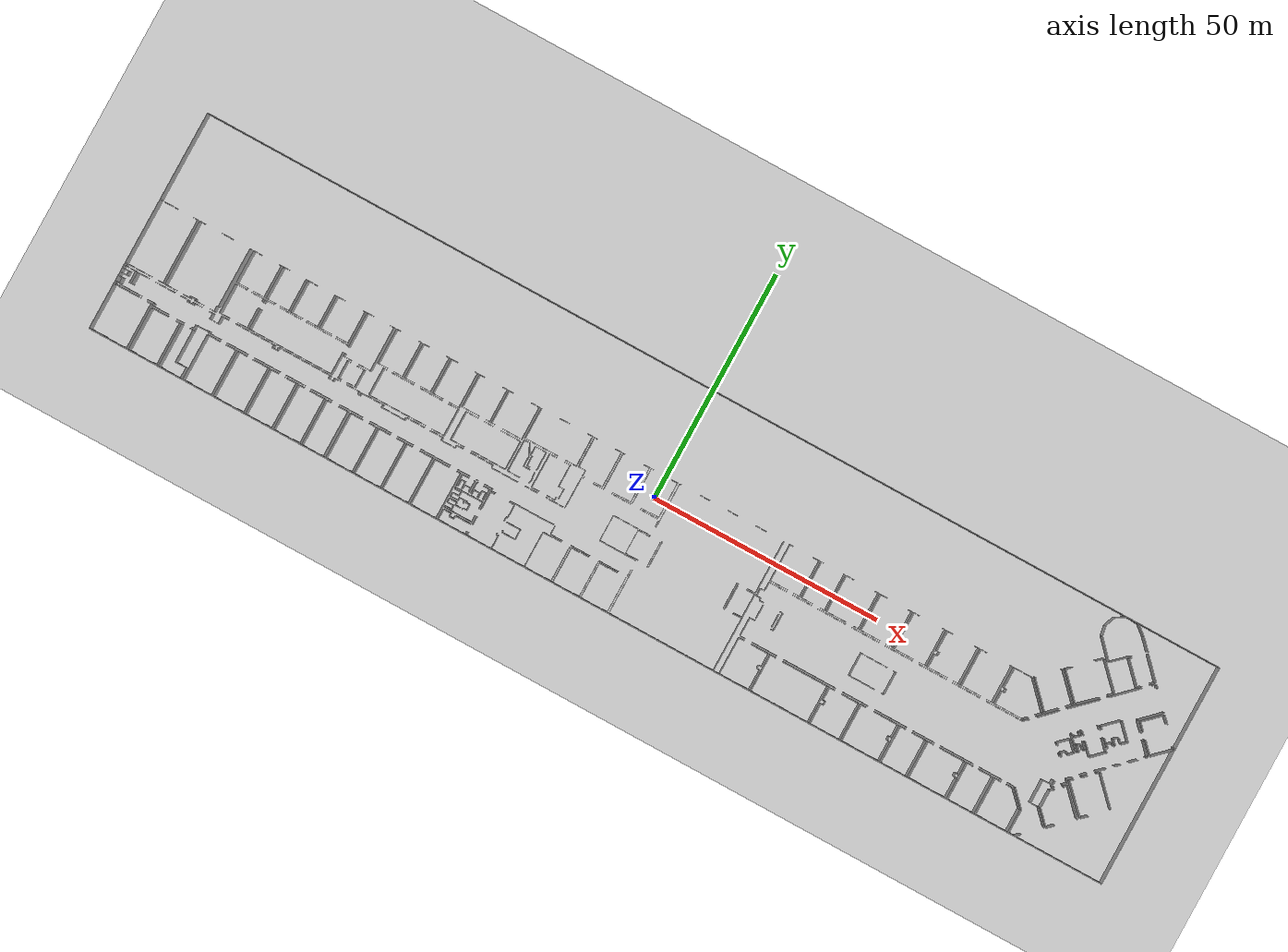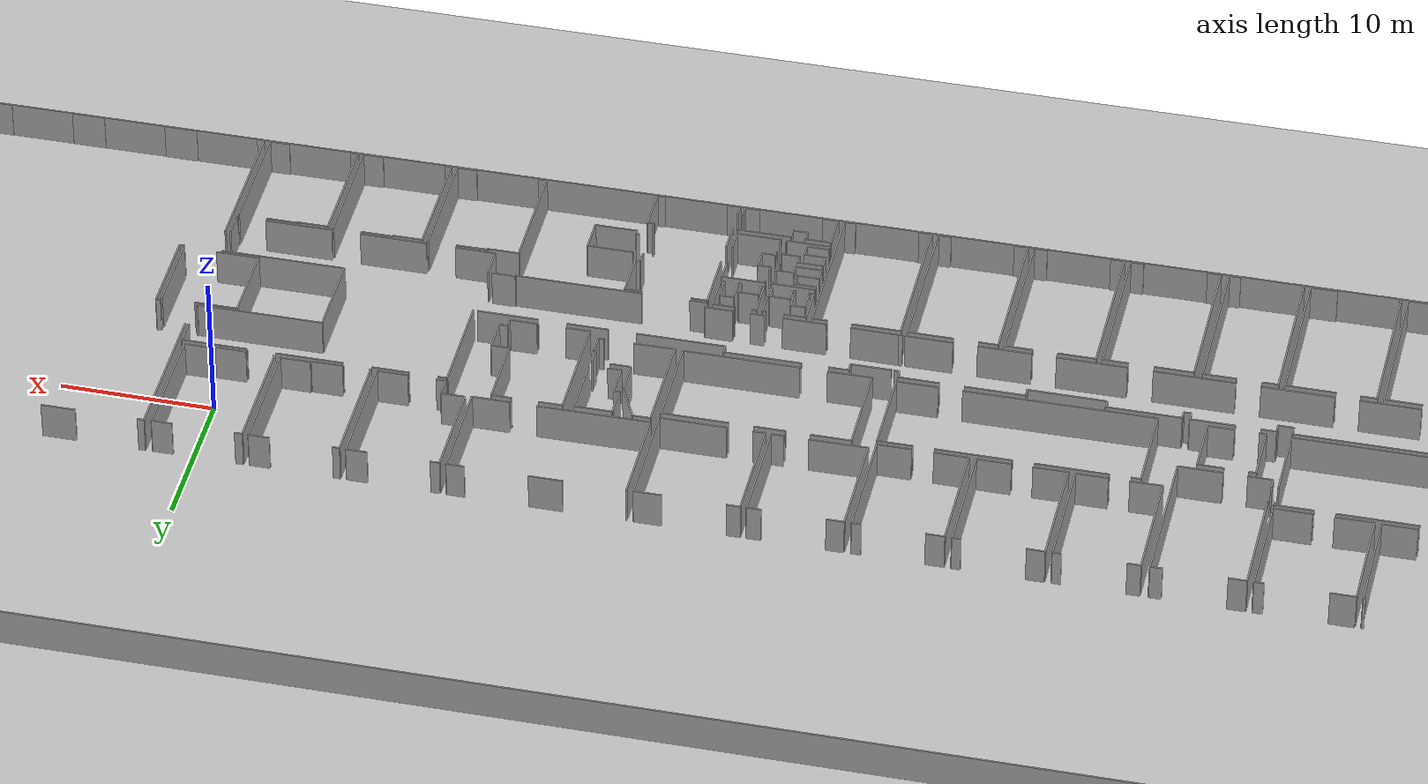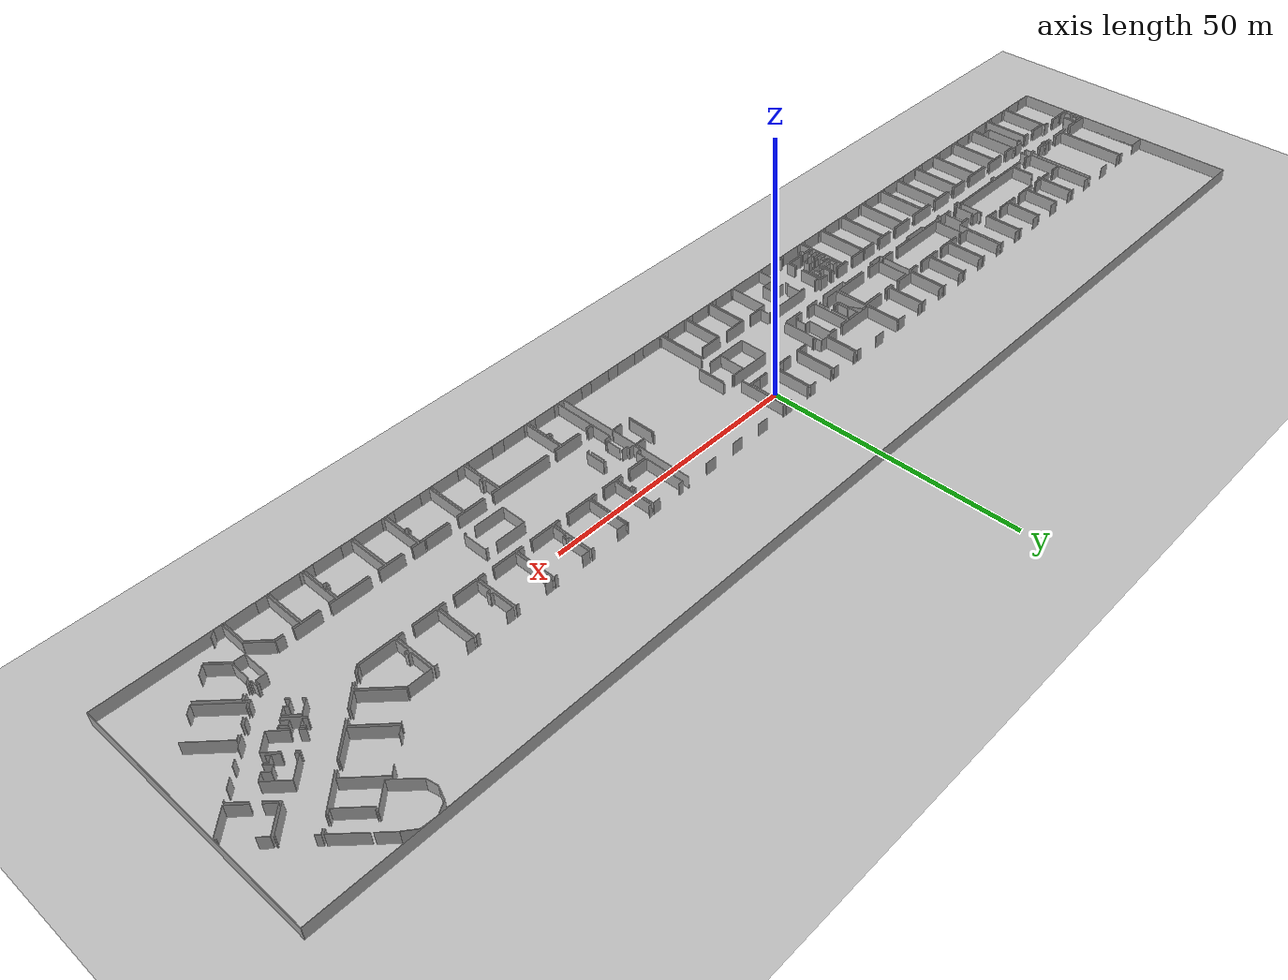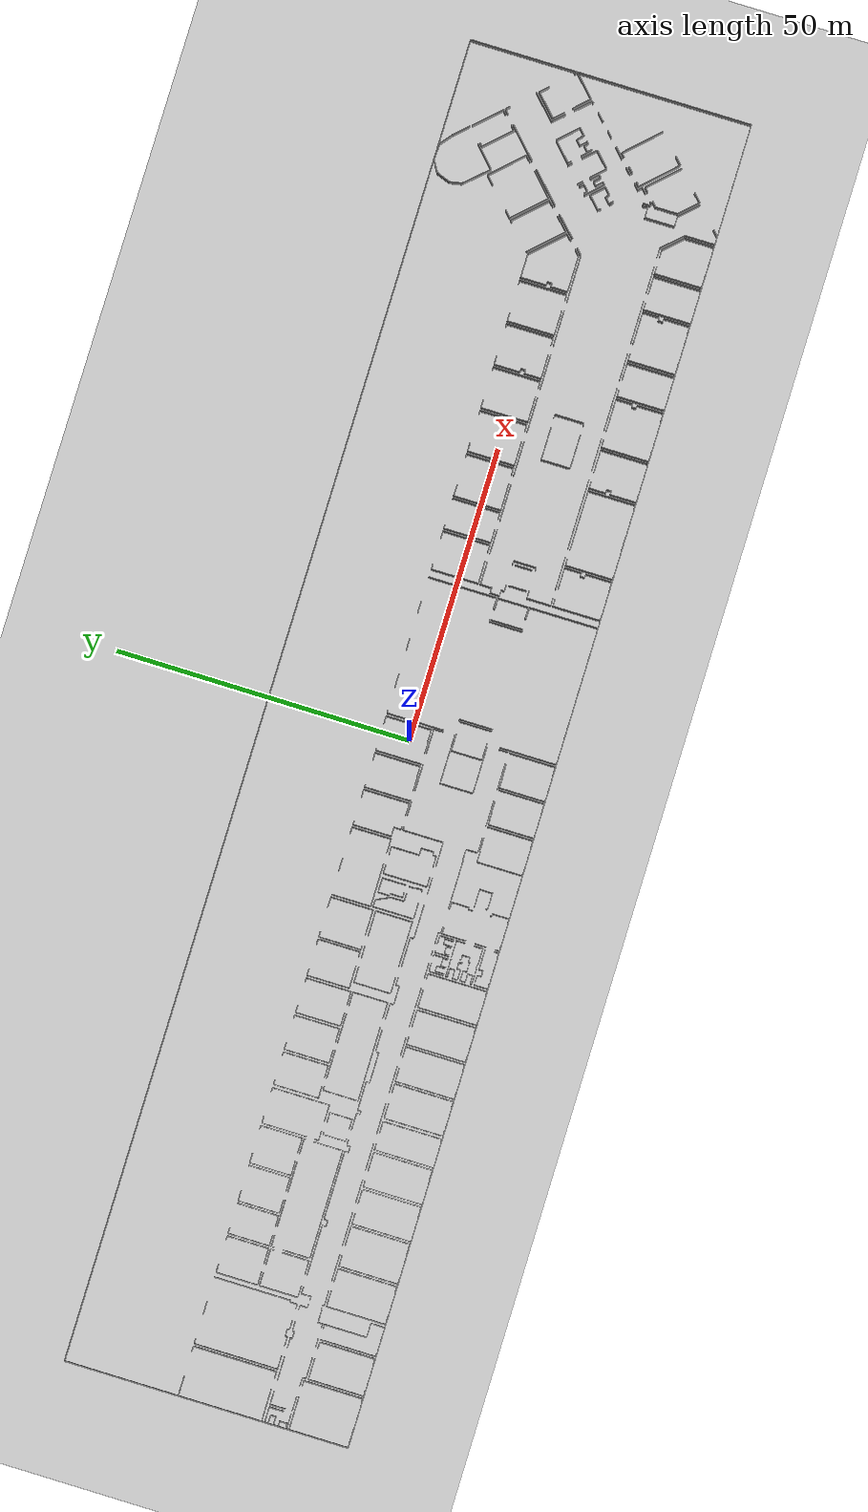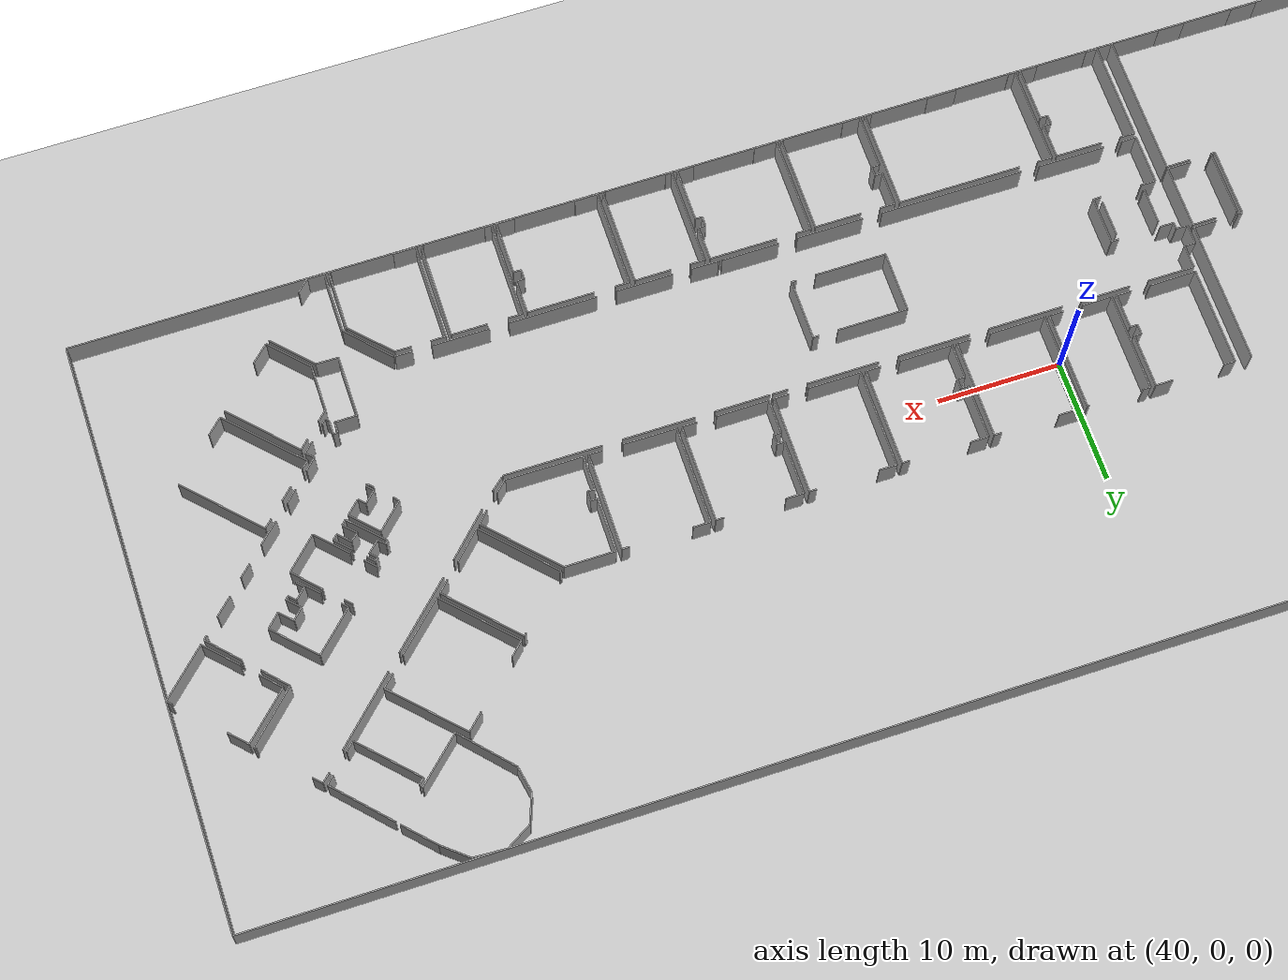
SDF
<sdf version="1.6">
  <world name="default">
    <light name="sun" type="directional">
      <cast_shadows>1</cast_shadows>
      <pose frame="">0 0 10 0 -0 0</pose>
      <diffuse>0.8 0.8 0.8 1</diffuse>
      <specular>0.1 0.1 0.1 1</specular>
      <attenuation>
        <range>1000</range>
        <constant>0.9</constant>
        <linear>0.01</linear>
        <quadratic>0.001</quadratic>
      </attenuation>
      <direction>-0.5 0.5 -1</direction>
    </light>
    <model name="ground_plane">
      <static>1</static>
      <link name="link">
        <collision name="collision">
          <geometry>
            <plane>
              <normal>0 0 1</normal>
              <size>100 100</size>
            </plane>
          </geometry>
          <surface>
            <friction>
              <ode>
                <mu>100</mu>
                <mu2>50</mu2>
              </ode>
              <torsional>
                <ode />
              </torsional>
            </friction>
            <contact>
              <ode />
            </contact>
            <bounce />
          </surface>
          <max_contacts>10</max_contacts>
        </collision>
        <visual name="visual">
          <cast_shadows>0</cast_shadows>
          <geometry>
            <plane>
              <normal>0 0 1</normal>
              <size>100 100</size>
            </plane>
          </geometry>
          <material>
            <script>
              <uri>file://media/materials/scripts/gazebo.material</uri>
              <name>Gazebo/Grey</name>
            </script>
          </material>
        </visual>
        <self_collide>0</self_collide>
        <kinematic>0</kinematic>
        <gravity>1</gravity>
      </link>
    </model>
    <gravity>0 0 -9.8</gravity>
    <magnetic_field>6e-06 2.3e-05 -4.2e-05</magnetic_field>
    <atmosphere type="adiabatic" />
    <physics default="0" name="default_physics" type="ode">
      <max_step_size>0.001</max_step_size>
      <real_time_factor>1</real_time_factor>
      <real_time_update_rate>1000</real_time_update_rate>
    </physics>
    <scene>
      <ambient>0.4 0.4 0.4 1</ambient>
      <background>0.7 0.7 0.7 1</background>
      <shadows>1</shadows>
    </scene>
    <spherical_coordinates>
      <surface_model>EARTH_WGS84</surface_model>
      <latitude_deg>0</latitude_deg>
      <longitude_deg>0</longitude_deg>
      <elevation>0</elevation>
      <heading_deg>0</heading_deg>
    </spherical_coordinates>
  <model name="0510035341_A_40_1_103">
		<static>1</static>
		<link name="Wall_0">
			<collision name="Wall_0_Collision">
				<geometry>
					<box>
						<size>14.1568154403 0.1 2.5</size>
					</box>
				</geometry>
				<pose frame="">7.07840772014 0 1.25 0 0 0</pose>
			</collision>
			<visual name="Wall_0_Visual">
				<pose frame="">7.07840772014 0 1.25 0 0 0</pose>
				<geometry>
					<box>
						<size>14.1568154403 0.1 2.5</size>
					</box>
				</geometry>
				<material>
					<script>
						<uri>file://media/materials/scripts/gazebo.material</uri>
						<name>Gazebo/Grey</name>
					</script>
					<ambient>1 1 1 1</ambient>
				</material>
			</visual>
			<pose frame="">0.0 -33.466827503 0 0 0 1.57079632679</pose>
		</link>
		<link name="Wall_1">
			<collision name="Wall_1_Collision">
				<geometry>
					<box>
						<size>3.42683004254 0.1 2.5</size>
					</box>
				</geometry>
				<pose frame="">1.71341502127 0 1.25 0 0 0</pose>
			</collision>
			<visual name="Wall_1_Visual">
				<pose frame="">1.71341502127 0 1.25 0 0 0</pose>
				<geometry>
					<box>
						<size>3.42683004254 0.1 2.5</size>
					</box>
				</geometry>
				<material>
					<script>
						<uri>file://media/materials/scripts/gazebo.material</uri>
						<name>Gazebo/Grey</name>
					</script>
					<ambient>1 1 1 1</ambient>
				</material>
			</visual>
			<pose frame="">0.0 -19.3100120627 0 0 0 0.0</pose>
		</link>
		<link name="Wall_2">
			<collision name="Wall_2_Collision">
				<geometry>
					<box>
						<size>0.943940067297 0.1 2.5</size>
					</box>
				</geometry>
				<pose frame="">0.471970033649 0 1.25 0 0 0</pose>
			</collision>
			<visual name="Wall_2_Visual">
				<pose frame="">0.471970033649 0 1.25 0 0 0</pose>
				<geometry>
					<box>
						<size>0.943940067297 0.1 2.5</size>
					</box>
				</geometry>
				<material>
					<script>
						<uri>file://media/materials/scripts/gazebo.material</uri>
						<name>Gazebo/Grey</name>
					</script>
					<ambient>1 1 1 1</ambient>
				</material>
			</visual>
			<pose frame="">7.44866992572 -19.3100120627 0 0 0 0.0</pose>
		</link>
		<link name="Wall_3">
			<collision name="Wall_3_Collision">
				<geometry>
					<box>
						<size>14.1222779506 0.1 2.5</size>
					</box>
				</geometry>
				<pose frame="">7.0611389753 0 1.25 0 0 0</pose>
			</collision>
			<visual name="Wall_3_Visual">
				<pose frame="">7.0611389753 0 1.25 0 0 0</pose>
				<geometry>
					<box>
						<size>14.1222779506 0.1 2.5</size>
					</box>
				</geometry>
				<material>
					<script>
						<uri>file://media/materials/scripts/gazebo.material</uri>
						<name>Gazebo/Grey</name>
					</script>
					<ambient>1 1 1 1</ambient>
				</material>
			</visual>
			<pose frame="">8.39260999302 -19.3100120627 0 0 0 -1.57079632679</pose>
		</link>
		<link name="Wall_4">
			<collision name="Wall_4_Collision">
				<geometry>
					<box>
						<size>1.29718748016 0.1 2.5</size>
					</box>
				</geometry>
				<pose frame="">0.64859374008 0 1.25 0 0 0</pose>
			</collision>
			<visual name="Wall_4_Visual">
				<pose frame="">0.64859374008 0 1.25 0 0 0</pose>
				<geometry>
					<box>
						<size>1.29718748016 0.1 2.5</size>
					</box>
				</geometry>
				<material>
					<script>
						<uri>file://media/materials/scripts/gazebo.material</uri>
						<name>Gazebo/Grey</name>
					</script>
					<ambient>1 1 1 1</ambient>
				</material>
			</visual>
			<pose frame="">8.39260999302 -33.4322900133 0 0 0 3.14159265359</pose>
		</link>
		<link name="Wall_5">
			<collision name="Wall_5_Collision">
				<geometry>
					<box>
						<size>5.35012100205 0.1 2.5</size>
					</box>
				</geometry>
				<pose frame="">2.67506050102 0 1.25 0 0 0</pose>
			</collision>
			<visual name="Wall_5_Visual">
				<pose frame="">2.67506050102 0 1.25 0 0 0</pose>
				<geometry>
					<box>
						<size>5.35012100205 0.1 2.5</size>
					</box>
				</geometry>
				<material>
					<script>
						<uri>file://media/materials/scripts/gazebo.material</uri>
						<name>Gazebo/Grey</name>
					</script>
					<ambient>1 1 1 1</ambient>
				</material>
			</visual>
			<pose frame="">5.3500095232 -33.4322900133 0 0 0 -3.13513714921</pose>
		</link>
		<link name="Wall_6">
			<collision name="Wall_6_Collision">
				<geometry>
					<box>
						<size>14.1573233445 0.1 2.5</size>
					</box>
				</geometry>
				<pose frame="">7.07866167227 0 1.25 0 0 0</pose>
			</collision>
			<visual name="Wall_6_Visual">
				<pose frame="">7.07866167227 0 1.25 0 0 0</pose>
				<geometry>
					<box>
						<size>14.1573233445 0.1 2.5</size>
					</box>
				</geometry>
				<material>
					<script>
						<uri>file://media/materials/scripts/gazebo.material</uri>
						<name>Gazebo/Grey</name>
					</script>
					<ambient>1 1 1 1</ambient>
				</material>
			</visual>
			<pose frame="">8.8136626246 -33.4673354073 0 0 0 1.57079632679</pose>
		</link>
		<link name="Wall_7">
			<collision name="Wall_7_Collision">
				<geometry>
					<box>
						<size>0.871055805981 0.1 2.5</size>
					</box>
				</geometry>
				<pose frame="">0.43552790299 0 1.25 0 0 0</pose>
			</collision>
			<visual name="Wall_7_Visual">
				<pose frame="">0.43552790299 0 1.25 0 0 0</pose>
				<geometry>
					<box>
						<size>0.871055805981 0.1 2.5</size>
					</box>
				</geometry>
				<material>
					<script>
						<uri>file://media/materials/scripts/gazebo.material</uri>
						<name>Gazebo/Grey</name>
					</script>
					<ambient>1 1 1 1</ambient>
				</material>
			</visual>
			<pose frame="">8.8136626246 -19.3100120627 0 0 0 0.0</pose>
		</link>
		<link name="Wall_8">
			<collision name="Wall_8_Collision">
				<geometry>
					<box>
						<size>2.24747635071 0.1 2.5</size>
					</box>
				</geometry>
				<pose frame="">1.12373817535 0 1.25 0 0 0</pose>
			</collision>
			<visual name="Wall_8_Visual">
				<pose frame="">1.12373817535 0 1.25 0 0 0</pose>
				<geometry>
					<box>
						<size>2.24747635071 0.1 2.5</size>
					</box>
				</geometry>
				<material>
					<script>
						<uri>file://media/materials/scripts/gazebo.material</uri>
						<name>Gazebo/Grey</name>
					</script>
					<ambient>1 1 1 1</ambient>
				</material>
			</visual>
			<pose frame="">13.7502380801 -19.3100120627 0 0 0 0.0</pose>
		</link>
		<link name="Wall_9">
			<collision name="Wall_9_Collision">
				<geometry>
					<box>
						<size>0.0581550377754 0.1 2.5</size>
					</box>
				</geometry>
				<pose frame="">0.0290775188877 0 1.25 0 0 0</pose>
			</collision>
			<visual name="Wall_9_Visual">
				<pose frame="">0.0290775188877 0 1.25 0 0 0</pose>
				<geometry>
					<box>
						<size>0.0581550377754 0.1 2.5</size>
					</box>
				</geometry>
				<material>
					<script>
						<uri>file://media/materials/scripts/gazebo.material</uri>
						<name>Gazebo/Grey</name>
					</script>
					<ambient>1 1 1 1</ambient>
				</material>
			</visual>
			<pose frame="">20.0380928195 -19.3100120627 0 0 0 0.0</pose>
		</link>
		<link name="Wall_10">
			<collision name="Wall_10_Collision">
				<geometry>
					<box>
						<size>12.9017840137 0.1 2.5</size>
					</box>
				</geometry>
				<pose frame="">6.45089200686 0 1.25 0 0 0</pose>
			</collision>
			<visual name="Wall_10_Visual">
				<pose frame="">6.45089200686 0 1.25 0 0 0</pose>
				<geometry>
					<box>
						<size>12.9017840137 0.1 2.5</size>
					</box>
				</geometry>
				<material>
					<script>
						<uri>file://media/materials/scripts/gazebo.material</uri>
						<name>Gazebo/Grey</name>
					</script>
					<ambient>1 1 1 1</ambient>
				</material>
			</visual>
			<pose frame="">20.0962478573 -19.3100120627 0 0 0 -1.57079632679</pose>
		</link>
		<link name="Wall_11">
			<collision name="Wall_11_Collision">
				<geometry>
					<box>
						<size>0.278585486636 0.1 2.5</size>
					</box>
				</geometry>
				<pose frame="">0.139292743318 0 1.25 0 0 0</pose>
			</collision>
			<visual name="Wall_11_Visual">
				<pose frame="">0.139292743318 0 1.25 0 0 0</pose>
				<geometry>
					<box>
						<size>0.278585486636 0.1 2.5</size>
					</box>
				</geometry>
				<material>
					<script>
						<uri>file://media/materials/scripts/gazebo.material</uri>
						<name>Gazebo/Grey</name>
					</script>
					<ambient>1 1 1 1</ambient>
				</material>
			</visual>
			<pose frame="">20.0962478573 -32.2117960764 0 0 0 3.14159265359</pose>
		</link>
		<link name="Wall_12">
			<collision name="Wall_12_Collision">
				<geometry>
					<box>
						<size>1.24817471907 0.1 2.5</size>
					</box>
				</geometry>
				<pose frame="">0.624087359533 0 1.25 0 0 0</pose>
			</collision>
			<visual name="Wall_12_Visual">
				<pose frame="">0.624087359533 0 1.25 0 0 0</pose>
				<geometry>
					<box>
						<size>1.24817471907 0.1 2.5</size>
					</box>
				</geometry>
				<material>
					<script>
						<uri>file://media/materials/scripts/gazebo.material</uri>
						<name>Gazebo/Grey</name>
					</script>
					<ambient>1 1 1 1</ambient>
				</material>
			</visual>
			<pose frame="">19.8176623706 -32.2117960764 0 0 0 -1.57079632679</pose>
		</link>
		<link name="Wall_13">
			<collision name="Wall_13_Collision">
				<geometry>
					<box>
						<size>0.806551964955 0.1 2.5</size>
					</box>
				</geometry>
				<pose frame="">0.403275982477 0 1.25 0 0 0</pose>
			</collision>
			<visual name="Wall_13_Visual">
				<pose frame="">0.403275982477 0 1.25 0 0 0</pose>
				<geometry>
					<box>
						<size>0.806551964955 0.1 2.5</size>
					</box>
				</geometry>
				<material>
					<script>
						<uri>file://media/materials/scripts/gazebo.material</uri>
						<name>Gazebo/Grey</name>
					</script>
					<ambient>1 1 1 1</ambient>
				</material>
			</visual>
			<pose frame="">19.8176623706 -33.4599707955 0 0 0 3.14159265359</pose>
		</link>
		<link name="Wall_14">
			<collision name="Wall_14_Collision">
				<geometry>
					<box>
						<size>1.62884896197 0.1 2.5</size>
					</box>
				</geometry>
				<pose frame="">0.814424480985 0 1.25 0 0 0</pose>
			</collision>
			<visual name="Wall_14_Visual">
				<pose frame="">0.814424480985 0 1.25 0 0 0</pose>
				<geometry>
					<box>
						<size>1.62884896197 0.1 2.5</size>
					</box>
				</geometry>
				<material>
					<script>
						<uri>file://media/materials/scripts/gazebo.material</uri>
						<name>Gazebo/Grey</name>
					</script>
					<ambient>1 1 1 1</ambient>
				</material>
			</visual>
			<pose frame="">17.1341502127 -33.4599707955 0 0 0 3.14159265359</pose>
		</link>
		<link name="Wall_15">
			<collision name="Wall_15_Collision">
				<geometry>
					<box>
						<size>0.371278014094 0.1 2.5</size>
					</box>
				</geometry>
				<pose frame="">0.185639007047 0 1.25 0 0 0</pose>
			</collision>
			<visual name="Wall_15_Visual">
				<pose frame="">0.185639007047 0 1.25 0 0 0</pose>
				<geometry>
					<box>
						<size>0.371278014094 0.1 2.5</size>
					</box>
				</geometry>
				<material>
					<script>
						<uri>file://media/materials/scripts/gazebo.material</uri>
						<name>Gazebo/Grey</name>
					</script>
					<ambient>1 1 1 1</ambient>
				</material>
			</visual>
			<pose frame="">15.5053012507 -33.4599707955 0 0 0 1.57079632679</pose>
		</link>
		<link name="Wall_16">
			<collision name="Wall_16_Collision">
				<geometry>
					<box>
						<size>1.2121135166 0.1 2.5</size>
					</box>
				</geometry>
				<pose frame="">0.606056758301 0 1.25 0 0 0</pose>
			</collision>
			<visual name="Wall_16_Visual">
				<pose frame="">0.606056758301 0 1.25 0 0 0</pose>
				<geometry>
					<box>
						<size>1.2121135166 0.1 2.5</size>
					</box>
				</geometry>
				<material>
					<script>
						<uri>file://media/materials/scripts/gazebo.material</uri>
						<name>Gazebo/Grey</name>
					</script>
					<ambient>1 1 1 1</ambient>
				</material>
			</visual>
			<pose frame="">15.5053012507 -33.0886927814 0 0 0 3.14159265359</pose>
		</link>
		<link name="Wall_17">
			<collision name="Wall_17_Collision">
				<geometry>
					<box>
						<size>0.365945019364 0.1 2.5</size>
					</box>
				</geometry>
				<pose frame="">0.182972509682 0 1.25 0 0 0</pose>
			</collision>
			<visual name="Wall_17_Visual">
				<pose frame="">0.182972509682 0 1.25 0 0 0</pose>
				<geometry>
					<box>
						<size>0.365945019364 0.1 2.5</size>
					</box>
				</geometry>
				<material>
					<script>
						<uri>file://media/materials/scripts/gazebo.material</uri>
						<name>Gazebo/Grey</name>
					</script>
					<ambient>1 1 1 1</ambient>
				</material>
			</visual>
			<pose frame="">14.2931877341 -33.0886927814 0 0 0 -1.57079632679</pose>
		</link>
		<link name="Wall_18">
			<collision name="Wall_18_Collision">
				<geometry>
					<box>
						<size>1.54377499841 0.1 2.5</size>
					</box>
				</geometry>
				<pose frame="">0.771887499206 0 1.25 0 0 0</pose>
			</collision>
			<visual name="Wall_18_Visual">
				<pose frame="">0.771887499206 0 1.25 0 0 0</pose>
				<geometry>
					<box>
						<size>1.54377499841 0.1 2.5</size>
					</box>
				</geometry>
				<material>
					<script>
						<uri>file://media/materials/scripts/gazebo.material</uri>
						<name>Gazebo/Grey</name>
					</script>
					<ambient>1 1 1 1</ambient>
				</material>
			</visual>
			<pose frame="">14.2931877341 -33.4546378008 0 0 0 3.14159265359</pose>
		</link>
		<link name="Wall_19">
			<collision name="Wall_19_Collision">
				<geometry>
					<box>
						<size>2.24751221937 0.1 2.5</size>
					</box>
				</geometry>
				<pose frame="">1.12375610968 0 1.25 0 0 0</pose>
			</collision>
			<visual name="Wall_19_Visual">
				<pose frame="">1.12375610968 0 1.25 0 0 0</pose>
				<geometry>
					<box>
						<size>2.24751221937 0.1 2.5</size>
					</box>
				</geometry>
				<material>
					<script>
						<uri>file://media/materials/scripts/gazebo.material</uri>
						<name>Gazebo/Grey</name>
					</script>
					<ambient>1 1 1 1</ambient>
				</material>
			</visual>
			<pose frame="">11.0611389753 -33.4546378008 0 0 0 -3.13594299619</pose>
		</link>
		<link name="Wall_20">
			<collision name="Wall_20_Collision">
				<geometry>
					<box>
						<size>7.07993143292 0.1 2.5</size>
					</box>
				</geometry>
				<pose frame="">3.53996571646 0 1.25 0 0 0</pose>
			</collision>
			<visual name="Wall_20_Visual">
				<pose frame="">3.53996571646 0 1.25 0 0 0</pose>
				<geometry>
					<box>
						<size>7.07993143292 0.1 2.5</size>
					</box>
				</geometry>
				<material>
					<script>
						<uri>file://media/materials/scripts/gazebo.material</uri>
						<name>Gazebo/Grey</name>
					</script>
					<ambient>1 1 1 1</ambient>
				</material>
			</visual>
			<pose frame="">20.8954352105 -26.3993397245 0 0 0 1.57079632679</pose>
		</link>
		<link name="Wall_21">
			<collision name="Wall_21_Collision">
				<geometry>
					<box>
						<size>1.4193384547 0.1 2.5</size>
					</box>
				</geometry>
				<pose frame="">0.709669227351 0 1.25 0 0 0</pose>
			</collision>
			<visual name="Wall_21_Visual">
				<pose frame="">0.709669227351 0 1.25 0 0 0</pose>
				<geometry>
					<box>
						<size>1.4193384547 0.1 2.5</size>
					</box>
				</geometry>
				<material>
					<script>
						<uri>file://media/materials/scripts/gazebo.material</uri>
						<name>Gazebo/Grey</name>
					</script>
					<ambient>1 1 1 1</ambient>
				</material>
			</visual>
			<pose frame="">20.8954352105 -19.3194082915 0 0 0 0.0</pose>
		</link>
		<link name="Wall_22">
			<collision name="Wall_22_Collision">
				<geometry>
					<box>
						<size>0.718176623706 0.1 2.5</size>
					</box>
				</geometry>
				<pose frame="">0.359088311853 0 1.25 0 0 0</pose>
			</collision>
			<visual name="Wall_22_Visual">
				<pose frame="">0.359088311853 0 1.25 0 0 0</pose>
				<geometry>
					<box>
						<size>0.718176623706 0.1 2.5</size>
					</box>
				</geometry>
				<material>
					<script>
						<uri>file://media/materials/scripts/gazebo.material</uri>
						<name>Gazebo/Grey</name>
					</script>
					<ambient>1 1 1 1</ambient>
				</material>
			</visual>
			<pose frame="">26.3556599581 -19.3194082915 0 0 0 0.0</pose>
		</link>
		<link name="Wall_23">
			<collision name="Wall_23_Collision">
				<geometry>
					<box>
						<size>7.02685543775 0.1 2.5</size>
					</box>
				</geometry>
				<pose frame="">3.51342771887 0 1.25 0 0 0</pose>
			</collision>
			<visual name="Wall_23_Visual">
				<pose frame="">3.51342771887 0 1.25 0 0 0</pose>
				<geometry>
					<box>
						<size>7.02685543775 0.1 2.5</size>
					</box>
				</geometry>
				<material>
					<script>
						<uri>file://media/materials/scripts/gazebo.material</uri>
						<name>Gazebo/Grey</name>
					</script>
					<ambient>1 1 1 1</ambient>
				</material>
			</visual>
			<pose frame="">27.0738365818 -19.3194082915 0 0 0 -1.57079632679</pose>
		</link>
		<link name="Wall_24">
			<collision name="Wall_24_Collision">
				<geometry>
					<box>
						<size>2.60402514126 0.1 2.5</size>
					</box>
				</geometry>
				<pose frame="">1.30201257063 0 1.25 0 0 0</pose>
			</collision>
			<visual name="Wall_24_Visual">
				<pose frame="">1.30201257063 0 1.25 0 0 0</pose>
				<geometry>
					<box>
						<size>2.60402514126 0.1 2.5</size>
					</box>
				</geometry>
				<material>
					<script>
						<uri>file://media/materials/scripts/gazebo.material</uri>
						<name>Gazebo/Grey</name>
					</script>
					<ambient>1 1 1 1</ambient>
				</material>
			</visual>
			<pose frame="">27.0738365818 -26.3462637293 0 0 0 3.14159265359</pose>
		</link>
		<link name="Wall_25">
			<collision name="Wall_25_Collision">
				<geometry>
					<box>
						<size>2.20976708239 0.1 2.5</size>
					</box>
				</geometry>
				<pose frame="">1.10488354119 0 1.25 0 0 0</pose>
			</collision>
			<visual name="Wall_25_Visual">
				<pose frame="">1.10488354119 0 1.25 0 0 0</pose>
				<geometry>
					<box>
						<size>2.20976708239 0.1 2.5</size>
					</box>
				</geometry>
				<material>
					<script>
						<uri>file://media/materials/scripts/gazebo.material</uri>
						<name>Gazebo/Grey</name>
					</script>
					<ambient>1 1 1 1</ambient>
				</material>
			</visual>
			<pose frame="">23.1045647895 -26.3462637293 0 0 0 -3.11757152475</pose>
		</link>
		<link name="Wall_26">
			<collision name="Wall_26_Collision">
				<geometry>
					<box>
						<size>6.52758555012 0.1 2.5</size>
					</box>
				</geometry>
				<pose frame="">3.26379277506 0 1.25 0 0 0</pose>
			</collision>
			<visual name="Wall_26_Visual">
				<pose frame="">3.26379277506 0 1.25 0 0 0</pose>
				<geometry>
					<box>
						<size>6.52758555012 0.1 2.5</size>
					</box>
				</geometry>
				<material>
					<script>
						<uri>file://media/materials/scripts/gazebo.material</uri>
						<name>Gazebo/Grey</name>
					</script>
					<ambient>1 1 1 1</ambient>
				</material>
			</visual>
			<pose frame="">20.8967049711 -33.21490699 0 0 0 1.57079632679</pose>
		</link>
		<link name="Wall_27">
			<collision name="Wall_27_Collision">
				<geometry>
					<box>
						<size>2.19693987683 0.1 2.5</size>
					</box>
				</geometry>
				<pose frame="">1.09846993842 0 1.25 0 0 0</pose>
			</collision>
			<visual name="Wall_27_Visual">
				<pose frame="">1.09846993842 0 1.25 0 0 0</pose>
				<geometry>
					<box>
						<size>2.19693987683 0.1 2.5</size>
					</box>
				</geometry>
				<material>
					<script>
						<uri>file://media/materials/scripts/gazebo.material</uri>
						<name>Gazebo/Grey</name>
					</script>
					<ambient>1 1 1 1</ambient>
				</material>
			</visual>
			<pose frame="">20.8967049711 -26.6873214399 0 0 0 0.0</pose>
		</link>
		<link name="Wall_28">
			<collision name="Wall_28_Collision">
				<geometry>
					<box>
						<size>2.64262586502 0.1 2.5</size>
					</box>
				</geometry>
				<pose frame="">1.32131293251 0 1.25 0 0 0</pose>
			</collision>
			<visual name="Wall_28_Visual">
				<pose frame="">1.32131293251 0 1.25 0 0 0</pose>
				<geometry>
					<box>
						<size>2.64262586502 0.1 2.5</size>
					</box>
				</geometry>
				<material>
					<script>
						<uri>file://media/materials/scripts/gazebo.material</uri>
						<name>Gazebo/Grey</name>
					</script>
					<ambient>1 1 1 1</ambient>
				</material>
			</visual>
			<pose frame="">24.4367976636 -26.6873214399 0 0 0 0.0</pose>
		</link>
		<link name="Wall_29">
			<collision name="Wall_29_Collision">
				<geometry>
					<box>
						<size>0.579518760714 0.1 2.5</size>
					</box>
				</geometry>
				<pose frame="">0.289759380357 0 1.25 0 0 0</pose>
			</collision>
			<visual name="Wall_29_Visual">
				<pose frame="">0.289759380357 0 1.25 0 0 0</pose>
				<geometry>
					<box>
						<size>0.579518760714 0.1 2.5</size>
					</box>
				</geometry>
				<material>
					<script>
						<uri>file://media/materials/scripts/gazebo.material</uri>
						<name>Gazebo/Grey</name>
					</script>
					<ambient>1 1 1 1</ambient>
				</material>
			</visual>
			<pose frame="">27.0794235287 -26.6873214399 0 0 0 -1.57079632679</pose>
		</link>
		<link name="Wall_30">
			<collision name="Wall_30_Collision">
				<geometry>
					<box>
						<size>4.54548917529 0.1 2.5</size>
					</box>
				</geometry>
				<pose frame="">2.27274458765 0 1.25 0 0 0</pose>
			</collision>
			<visual name="Wall_30_Visual">
				<pose frame="">2.27274458765 0 1.25 0 0 0</pose>
				<geometry>
					<box>
						<size>4.54548917529 0.1 2.5</size>
					</box>
				</geometry>
				<material>
					<script>
						<uri>file://media/materials/scripts/gazebo.material</uri>
						<name>Gazebo/Grey</name>
					</script>
					<ambient>1 1 1 1</ambient>
				</material>
			</visual>
			<pose frame="">27.0794235287 -28.6727191924 0 0 0 -1.57079632679</pose>
		</link>
		<link name="Wall_31">
			<collision name="Wall_31_Collision">
				<geometry>
					<box>
						<size>2.32797917593 0.1 2.5</size>
					</box>
				</geometry>
				<pose frame="">1.16398958796 0 1.25 0 0 0</pose>
			</collision>
			<visual name="Wall_31_Visual">
				<pose frame="">1.16398958796 0 1.25 0 0 0</pose>
				<geometry>
					<box>
						<size>2.32797917593 0.1 2.5</size>
					</box>
				</geometry>
				<material>
					<script>
						<uri>file://media/materials/scripts/gazebo.material</uri>
						<name>Gazebo/Grey</name>
					</script>
					<ambient>1 1 1 1</ambient>
				</material>
			</visual>
			<pose frame="">27.0794235287 -33.2182083677 0 0 0 3.14159265359</pose>
		</link>
		<link name="Wall_32">
			<collision name="Wall_32_Collision">
				<geometry>
					<box>
						<size>1.90565964336 0.1 2.5</size>
					</box>
				</geometry>
				<pose frame="">0.952829821681 0 1.25 0 0 0</pose>
			</collision>
			<visual name="Wall_32_Visual">
				<pose frame="">0.952829821681 0 1.25 0 0 0</pose>
				<geometry>
					<box>
						<size>1.90565964336 0.1 2.5</size>
					</box>
				</geometry>
				<material>
					<script>
						<uri>file://media/materials/scripts/gazebo.material</uri>
						<name>Gazebo/Grey</name>
					</script>
					<ambient>1 1 1 1</ambient>
				</material>
			</visual>
			<pose frame="">22.8023617548 -33.2182083677 0 0 0 3.13986024594</pose>
		</link>
		<link name="Wall_33">
			<collision name="Wall_33_Collision">
				<geometry>
					<box>
						<size>7.04640975176 0.1 2.5</size>
					</box>
				</geometry>
				<pose frame="">3.52320487588 0 1.25 0 0 0</pose>
			</collision>
			<visual name="Wall_33_Visual">
				<pose frame="">3.52320487588 0 1.25 0 0 0</pose>
				<geometry>
					<box>
						<size>7.04640975176 0.1 2.5</size>
					</box>
				</geometry>
				<material>
					<script>
						<uri>file://media/materials/scripts/gazebo.material</uri>
						<name>Gazebo/Grey</name>
					</script>
					<ambient>1 1 1 1</ambient>
				</material>
			</visual>
			<pose frame="">27.507840772 -26.3490572027 0 0 0 1.57079632679</pose>
		</link>
		<link name="Wall_34">
			<collision name="Wall_34_Collision">
				<geometry>
					<box>
						<size>1.03129960003 0.1 2.5</size>
					</box>
				</geometry>
				<pose frame="">0.515649800013 0 1.25 0 0 0</pose>
			</collision>
			<visual name="Wall_34_Visual">
				<pose frame="">0.515649800013 0 1.25 0 0 0</pose>
				<geometry>
					<box>
						<size>1.03129960003 0.1 2.5</size>
					</box>
				</geometry>
				<material>
					<script>
						<uri>file://media/materials/scripts/gazebo.material</uri>
						<name>Gazebo/Grey</name>
					</script>
					<ambient>1 1 1 1</ambient>
				</material>
			</visual>
			<pose frame="">27.507840772 -19.302647451 0 0 0 0.0</pose>
		</link>
		<link name="Wall_35">
			<collision name="Wall_35_Collision">
				<geometry>
					<box>
						<size>7.05656783696 0.1 2.5</size>
					</box>
				</geometry>
				<pose frame="">3.52828391848 0 1.25 0 0 0</pose>
			</collision>
			<visual name="Wall_35_Visual">
				<pose frame="">3.52828391848 0 1.25 0 0 0</pose>
				<geometry>
					<box>
						<size>7.05656783696 0.1 2.5</size>
					</box>
				</geometry>
				<material>
					<script>
						<uri>file://media/materials/scripts/gazebo.material</uri>
						<name>Gazebo/Grey</name>
					</script>
					<ambient>1 1 1 1</ambient>
				</material>
			</visual>
			<pose frame="">32.6122785855 -19.302647451 0 0 0 -1.57079632679</pose>
		</link>
		<link name="Wall_36">
			<collision name="Wall_36_Collision">
				<geometry>
					<box>
						<size>1.85689797473 0.1 2.5</size>
					</box>
				</geometry>
				<pose frame="">0.928448987366 0 1.25 0 0 0</pose>
			</collision>
			<visual name="Wall_36_Visual">
				<pose frame="">0.928448987366 0 1.25 0 0 0</pose>
				<geometry>
					<box>
						<size>1.85689797473 0.1 2.5</size>
					</box>
				</geometry>
				<material>
					<script>
						<uri>file://media/materials/scripts/gazebo.material</uri>
						<name>Gazebo/Grey</name>
					</script>
					<ambient>1 1 1 1</ambient>
				</material>
			</visual>
			<pose frame="">32.6122785855 -26.3592152879 0 0 0 3.14159265359</pose>
		</link>
		<link name="Wall_37">
			<collision name="Wall_37_Collision">
				<geometry>
					<box>
						<size>1.88765351466 0.1 2.5</size>
					</box>
				</geometry>
				<pose frame="">0.943826757332 0 1.25 0 0 0</pose>
			</collision>
			<visual name="Wall_37_Visual">
				<pose frame="">0.943826757332 0 1.25 0 0 0</pose>
				<geometry>
					<box>
						<size>1.88765351466 0.1 2.5</size>
					</box>
				</geometry>
				<material>
					<script>
						<uri>file://media/materials/scripts/gazebo.material</uri>
						<name>Gazebo/Grey</name>
					</script>
					<ambient>1 1 1 1</ambient>
				</material>
			</visual>
			<pose frame="">29.3954669545 -26.3592152879 0 0 0 3.1362112983</pose>
		</link>
		<link name="Wall_38">
			<collision name="Wall_38_Collision">
				<geometry>
					<box>
						<size>7.05453621992 0.1 2.5</size>
					</box>
				</geometry>
				<pose frame="">3.52726810996 0 1.25 0 0 0</pose>
			</collision>
			<visual name="Wall_38_Visual">
				<pose frame="">3.52726810996 0 1.25 0 0 0</pose>
				<geometry>
					<box>
						<size>7.05453621992 0.1 2.5</size>
					</box>
				</geometry>
				<material>
					<script>
						<uri>file://media/materials/scripts/gazebo.material</uri>
						<name>Gazebo/Grey</name>
					</script>
					<ambient>1 1 1 1</ambient>
				</material>
			</visual>
			<pose frame="">33.017586185 -26.3820709796 0 0 0 1.57079632679</pose>
		</link>
		<link name="Wall_39">
			<collision name="Wall_39_Collision">
				<geometry>
					<box>
						<size>1.78909275602 0.1 2.5</size>
					</box>
				</geometry>
				<pose frame="">0.894546378008 0 1.25 0 0 0</pose>
			</collision>
			<visual name="Wall_39_Visual">
				<pose frame="">0.894546378008 0 1.25 0 0 0</pose>
				<geometry>
					<box>
						<size>1.78909275602 0.1 2.5</size>
					</box>
				</geometry>
				<material>
					<script>
						<uri>file://media/materials/scripts/gazebo.material</uri>
						<name>Gazebo/Grey</name>
					</script>
					<ambient>1 1 1 1</ambient>
				</material>
			</visual>
			<pose frame="">33.017586185 -19.3275347597 0 0 0 0.0</pose>
		</link>
		<link name="Wall_40">
			<collision name="Wall_40_Collision">
				<geometry>
					<box>
						<size>0.141197384293 0.1 2.5</size>
					</box>
				</geometry>
				<pose frame="">0.0705986921465 0 1.25 0 0 0</pose>
			</collision>
			<visual name="Wall_40_Visual">
				<pose frame="">0.0705986921465 0 1.25 0 0 0</pose>
				<geometry>
					<box>
						<size>0.141197384293 0.1 2.5</size>
					</box>
				</geometry>
				<material>
					<script>
						<uri>file://media/materials/scripts/gazebo.material</uri>
						<name>Gazebo/Grey</name>
					</script>
					<ambient>1 1 1 1</ambient>
				</material>
			</visual>
			<pose frame="">38.9077518888 -19.3275347597 0 0 0 0.0</pose>
		</link>
		<link name="Wall_41">
			<collision name="Wall_41_Collision">
				<geometry>
					<box>
						<size>7.00704717161 0.1 2.5</size>
					</box>
				</geometry>
				<pose frame="">3.5035235858 0 1.25 0 0 0</pose>
			</collision>
			<visual name="Wall_41_Visual">
				<pose frame="">3.5035235858 0 1.25 0 0 0</pose>
				<geometry>
					<box>
						<size>7.00704717161 0.1 2.5</size>
					</box>
				</geometry>
				<material>
					<script>
						<uri>file://media/materials/scripts/gazebo.material</uri>
						<name>Gazebo/Grey</name>
					</script>
					<ambient>1 1 1 1</ambient>
				</material>
			</visual>
			<pose frame="">39.0489492731 -19.3275347597 0 0 0 -1.57079632679</pose>
		</link>
		<link name="Wall_42">
			<collision name="Wall_42_Collision">
				<geometry>
					<box>
						<size>2.2990286331 0.1 2.5</size>
					</box>
				</geometry>
				<pose frame="">1.14951431655 0 1.25 0 0 0</pose>
			</collision>
			<visual name="Wall_42_Visual">
				<pose frame="">1.14951431655 0 1.25 0 0 0</pose>
				<geometry>
					<box>
						<size>2.2990286331 0.1 2.5</size>
					</box>
				</geometry>
				<material>
					<script>
						<uri>file://media/materials/scripts/gazebo.material</uri>
						<name>Gazebo/Grey</name>
					</script>
					<ambient>1 1 1 1</ambient>
				</material>
			</visual>
			<pose frame="">39.0489492731 -26.3345819313 0 0 0 3.14159265359</pose>
		</link>
		<link name="Wall_43">
			<collision name="Wall_43_Collision">
				<geometry>
					<box>
						<size>2.34902937764 0.1 2.5</size>
					</box>
				</geometry>
				<pose frame="">1.17451468882 0 1.25 0 0 0</pose>
			</collision>
			<visual name="Wall_43_Visual">
				<pose frame="">1.17451468882 0 1.25 0 0 0</pose>
				<geometry>
					<box>
						<size>2.34902937764 0.1 2.5</size>
					</box>
				</geometry>
				<material>
					<script>
						<uri>file://media/materials/scripts/gazebo.material</uri>
						<name>Gazebo/Grey</name>
					</script>
					<ambient>1 1 1 1</ambient>
				</material>
			</visual>
			<pose frame="">35.3661354835 -26.3345819313 0 0 0 -3.12137482056</pose>
		</link>
		<link name="Wall_44">
			<collision name="Wall_44_Collision">
				<geometry>
					<box>
						<size>7.07307472541 0.1 2.5</size>
					</box>
				</geometry>
				<pose frame="">3.53653736271 0 1.25 0 0 0</pose>
			</collision>
			<visual name="Wall_44_Visual">
				<pose frame="">3.53653736271 0 1.25 0 0 0</pose>
				<geometry>
					<box>
						<size>7.07307472541 0.1 2.5</size>
					</box>
				</geometry>
				<material>
					<script>
						<uri>file://media/materials/scripts/gazebo.material</uri>
						<name>Gazebo/Grey</name>
					</script>
					<ambient>1 1 1 1</ambient>
				</material>
			</visual>
			<pose frame="">39.4639070535 -26.3841025967 0 0 0 1.57079632679</pose>
		</link>
		<link name="Wall_45">
			<collision name="Wall_45_Collision">
				<geometry>
					<box>
						<size>1.64383213764 0.1 2.5</size>
					</box>
				</geometry>
				<pose frame="">0.821916068821 0 1.25 0 0 0</pose>
			</collision>
			<visual name="Wall_45_Visual">
				<pose frame="">0.821916068821 0 1.25 0 0 0</pose>
				<geometry>
					<box>
						<size>1.64383213764 0.1 2.5</size>
					</box>
				</geometry>
				<material>
					<script>
						<uri>file://media/materials/scripts/gazebo.material</uri>
						<name>Gazebo/Grey</name>
					</script>
					<ambient>1 1 1 1</ambient>
				</material>
			</visual>
			<pose frame="">39.4639070535 -19.3110278712 0 0 0 0.0</pose>
		</link>
		<link name="Wall_46">
			<collision name="Wall_46_Collision">
				<geometry>
					<box>
						<size>0.639197511269 0.1 2.5</size>
					</box>
				</geometry>
				<pose frame="">0.319598755635 0 1.25 0 0 0</pose>
			</collision>
			<visual name="Wall_46_Visual">
				<pose frame="">0.319598755635 0 1.25 0 0 0</pose>
				<geometry>
					<box>
						<size>0.639197511269 0.1 2.5</size>
					</box>
				</geometry>
				<material>
					<script>
						<uri>file://media/materials/scripts/gazebo.material</uri>
						<name>Gazebo/Grey</name>
					</script>
					<ambient>1 1 1 1</ambient>
				</material>
			</visual>
			<pose frame="">45.1506571011 -19.3110278712 0 0 0 0.0</pose>
		</link>
		<link name="Wall_47">
			<collision name="Wall_47_Collision">
				<geometry>
					<box>
						<size>7.02355406006 0.1 2.5</size>
					</box>
				</geometry>
				<pose frame="">3.51177703003 0 1.25 0 0 0</pose>
			</collision>
			<visual name="Wall_47_Visual">
				<pose frame="">3.51177703003 0 1.25 0 0 0</pose>
				<geometry>
					<box>
						<size>7.02355406006 0.1 2.5</size>
					</box>
				</geometry>
				<material>
					<script>
						<uri>file://media/materials/scripts/gazebo.material</uri>
						<name>Gazebo/Grey</name>
					</script>
					<ambient>1 1 1 1</ambient>
				</material>
			</visual>
			<pose frame="">45.7898546124 -19.3110278712 0 0 0 -1.57079632679</pose>
		</link>
		<link name="Wall_48">
			<collision name="Wall_48_Collision">
				<geometry>
					<box>
						<size>2.47781093264 0.1 2.5</size>
					</box>
				</geometry>
				<pose frame="">1.23890546632 0 1.25 0 0 0</pose>
			</collision>
			<visual name="Wall_48_Visual">
				<pose frame="">1.23890546632 0 1.25 0 0 0</pose>
				<geometry>
					<box>
						<size>2.47781093264 0.1 2.5</size>
					</box>
				</geometry>
				<material>
					<script>
						<uri>file://media/materials/scripts/gazebo.material</uri>
						<name>Gazebo/Grey</name>
					</script>
					<ambient>1 1 1 1</ambient>
				</material>
			</visual>
			<pose frame="">45.7898546124 -26.3345819313 0 0 0 3.14159265359</pose>
		</link>
		<link name="Wall_49">
			<collision name="Wall_49_Collision">
				<geometry>
					<box>
						<size>2.49100081891 0.1 2.5</size>
					</box>
				</geometry>
				<pose frame="">1.24550040946 0 1.25 0 0 0</pose>
			</collision>
			<visual name="Wall_49_Visual">
				<pose frame="">1.24550040946 0 1.25 0 0 0</pose>
				<geometry>
					<box>
						<size>2.49100081891 0.1 2.5</size>
					</box>
				</geometry>
				<material>
					<script>
						<uri>file://media/materials/scripts/gazebo.material</uri>
						<name>Gazebo/Grey</name>
					</script>
					<ambient>1 1 1 1</ambient>
				</material>
			</visual>
			<pose frame="">41.9544155927 -26.3345819313 0 0 0 -3.12171151691</pose>
		</link>
		<link name="Wall_50">
			<collision name="Wall_50_Collision">
				<geometry>
					<box>
						<size>0.697098596914 0.1 2.5</size>
					</box>
				</geometry>
				<pose frame="">0.348549298457 0 1.25 0 0 0</pose>
			</collision>
			<visual name="Wall_50_Visual">
				<pose frame="">0.348549298457 0 1.25 0 0 0</pose>
				<geometry>
					<box>
						<size>0.697098596914 0.1 2.5</size>
					</box>
				</geometry>
				<material>
					<script>
						<uri>file://media/materials/scripts/gazebo.material</uri>
						<name>Gazebo/Grey</name>
					</script>
					<ambient>1 1 1 1</ambient>
				</material>
			</visual>
			<pose frame="">46.2210653292 -28.9883816901 0 0 0 1.57079632679</pose>
		</link>
		<link name="Wall_51">
			<collision name="Wall_51_Collision">
				<geometry>
					<box>
						<size>7.6084058155 0.1 2.5</size>
					</box>
				</geometry>
				<pose frame="">3.80420290775 0 1.25 0 0 0</pose>
			</collision>
			<visual name="Wall_51_Visual">
				<pose frame="">3.80420290775 0 1.25 0 0 0</pose>
				<geometry>
					<box>
						<size>7.6084058155 0.1 2.5</size>
					</box>
				</geometry>
				<material>
					<script>
						<uri>file://media/materials/scripts/gazebo.material</uri>
						<name>Gazebo/Grey</name>
					</script>
					<ambient>1 1 1 1</ambient>
				</material>
			</visual>
			<pose frame="">46.2210653292 -26.9184178782 0 0 0 1.57079632679</pose>
		</link>
		<link name="Wall_52">
			<collision name="Wall_52_Collision">
				<geometry>
					<box>
						<size>1.17173512793 0.1 2.5</size>
					</box>
				</geometry>
				<pose frame="">0.585867563964 0 1.25 0 0 0</pose>
			</collision>
			<visual name="Wall_52_Visual">
				<pose frame="">0.585867563964 0 1.25 0 0 0</pose>
				<geometry>
					<box>
						<size>1.17173512793 0.1 2.5</size>
					</box>
				</geometry>
				<material>
					<script>
						<uri>file://media/materials/scripts/gazebo.material</uri>
						<name>Gazebo/Grey</name>
					</script>
					<ambient>1 1 1 1</ambient>
				</material>
			</visual>
			<pose frame="">46.2210653292 -19.3100120627 0 0 0 0.0</pose>
		</link>
		<link name="Wall_53">
			<collision name="Wall_53_Collision">
				<geometry>
					<box>
						<size>0.790552980763 0.1 2.5</size>
					</box>
				</geometry>
				<pose frame="">0.395276490382 0 1.25 0 0 0</pose>
			</collision>
			<visual name="Wall_53_Visual">
				<pose frame="">0.395276490382 0 1.25 0 0 0</pose>
				<geometry>
					<box>
						<size>0.790552980763 0.1 2.5</size>
					</box>
				</geometry>
				<material>
					<script>
						<uri>file://media/materials/scripts/gazebo.material</uri>
						<name>Gazebo/Grey</name>
					</script>
					<ambient>1 1 1 1</ambient>
				</material>
			</visual>
			<pose frame="">51.4413053139 -19.3100120627 0 0 0 0.0</pose>
		</link>
		<link name="Wall_54">
			<collision name="Wall_54_Collision">
				<geometry>
					<box>
						<size>9.67024315916 0.1 2.5</size>
					</box>
				</geometry>
				<pose frame="">4.83512157958 0 1.25 0 0 0</pose>
			</collision>
			<visual name="Wall_54_Visual">
				<pose frame="">4.83512157958 0 1.25 0 0 0</pose>
				<geometry>
					<box>
						<size>9.67024315916 0.1 2.5</size>
					</box>
				</geometry>
				<material>
					<script>
						<uri>file://media/materials/scripts/gazebo.material</uri>
						<name>Gazebo/Grey</name>
					</script>
					<ambient>1 1 1 1</ambient>
				</material>
			</visual>
			<pose frame="">52.2318582947 -19.3100120627 0 0 0 -1.57079632679</pose>
		</link>
		<link name="Wall_55">
			<collision name="Wall_55_Collision">
				<geometry>
					<box>
						<size>2.86534188306 0.1 2.5</size>
					</box>
				</geometry>
				<pose frame="">1.43267094153 0 1.25 0 0 0</pose>
			</collision>
			<visual name="Wall_55_Visual">
				<pose frame="">1.43267094153 0 1.25 0 0 0</pose>
				<geometry>
					<box>
						<size>2.86534188306 0.1 2.5</size>
					</box>
				</geometry>
				<material>
					<script>
						<uri>file://media/materials/scripts/gazebo.material</uri>
						<name>Gazebo/Grey</name>
					</script>
					<ambient>1 1 1 1</ambient>
				</material>
			</visual>
			<pose frame="">52.2318582947 -28.9802552219 0 0 0 3.14159265359</pose>
		</link>
		<link name="Wall_56">
			<collision name="Wall_56_Collision">
				<geometry>
					<box>
						<size>1.5940782343 0.1 2.5</size>
					</box>
				</geometry>
				<pose frame="">0.797039117148 0 1.25 0 0 0</pose>
			</collision>
			<visual name="Wall_56_Visual">
				<pose frame="">0.797039117148 0 1.25 0 0 0</pose>
				<geometry>
					<box>
						<size>1.5940782343 0.1 2.5</size>
					</box>
				</geometry>
				<material>
					<script>
						<uri>file://media/materials/scripts/gazebo.material</uri>
						<name>Gazebo/Grey</name>
					</script>
					<ambient>1 1 1 1</ambient>
				</material>
			</visual>
			<pose frame="">47.8151228493 -28.9802552219 0 0 0 -3.13649472101</pose>
		</link>
		<link name="Wall_57">
			<collision name="Wall_57_Collision">
				<geometry>
					<box>
						<size>4.55717097327 0.1 2.5</size>
					</box>
				</geometry>
				<pose frame="">2.27858548664 0 1.25 0 0 0</pose>
			</collision>
			<visual name="Wall_57_Visual">
				<pose frame="">2.27858548664 0 1.25 0 0 0</pose>
				<geometry>
					<box>
						<size>4.55717097327 0.1 2.5</size>
					</box>
				</geometry>
				<material>
					<script>
						<uri>file://media/materials/scripts/gazebo.material</uri>
						<name>Gazebo/Grey</name>
					</script>
					<ambient>1 1 1 1</ambient>
				</material>
			</visual>
			<pose frame="">27.5126658625 -33.2400482509 0 0 0 1.57079632679</pose>
		</link>
		<link name="Wall_58">
			<collision name="Wall_58_Collision">
				<geometry>
					<box>
						<size>0.655958351851 0.1 2.5</size>
					</box>
				</geometry>
				<pose frame="">0.327979175925 0 1.25 0 0 0</pose>
			</collision>
			<visual name="Wall_58_Visual">
				<pose frame="">0.327979175925 0 1.25 0 0 0</pose>
				<geometry>
					<box>
						<size>0.655958351851 0.1 2.5</size>
					</box>
				</geometry>
				<material>
					<script>
						<uri>file://media/materials/scripts/gazebo.material</uri>
						<name>Gazebo/Grey</name>
					</script>
					<ambient>1 1 1 1</ambient>
				</material>
			</visual>
			<pose frame="">27.5126658625 -27.322201765 0 0 0 1.57079632679</pose>
		</link>
		<link name="Wall_59">
			<collision name="Wall_59_Collision">
				<geometry>
					<box>
						<size>1.86477049076 0.1 2.5</size>
					</box>
				</geometry>
				<pose frame="">0.932385245381 0 1.25 0 0 0</pose>
			</collision>
			<visual name="Wall_59_Visual">
				<pose frame="">0.932385245381 0 1.25 0 0 0</pose>
				<geometry>
					<box>
						<size>1.86477049076 0.1 2.5</size>
					</box>
				</geometry>
				<material>
					<script>
						<uri>file://media/materials/scripts/gazebo.material</uri>
						<name>Gazebo/Grey</name>
					</script>
					<ambient>1 1 1 1</ambient>
				</material>
			</visual>
			<pose frame="">27.5126658625 -26.6662434131 0 0 0 0.0</pose>
		</link>
		<link name="Wall_60">
			<collision name="Wall_60_Collision">
				<geometry>
					<box>
						<size>4.63234080376 0.1 2.5</size>
					</box>
				</geometry>
				<pose frame="">2.31617040188 0 1.25 0 0 0</pose>
			</collision>
			<visual name="Wall_60_Visual">
				<pose frame="">2.31617040188 0 1.25 0 0 0</pose>
				<geometry>
					<box>
						<size>4.63234080376 0.1 2.5</size>
					</box>
				</geometry>
				<material>
					<script>
						<uri>file://media/materials/scripts/gazebo.material</uri>
						<name>Gazebo/Grey</name>
					</script>
					<ambient>1 1 1 1</ambient>
				</material>
			</visual>
			<pose frame="">30.7056059933 -26.6662434131 0 0 0 0.0</pose>
		</link>
		<link name="Wall_61">
			<collision name="Wall_61_Collision">
				<geometry>
					<box>
						<size>5.23344549552 0.1 2.5</size>
					</box>
				</geometry>
				<pose frame="">2.61672274776 0 1.25 0 0 0</pose>
			</collision>
			<visual name="Wall_61_Visual">
				<pose frame="">2.61672274776 0 1.25 0 0 0</pose>
				<geometry>
					<box>
						<size>5.23344549552 0.1 2.5</size>
					</box>
				</geometry>
				<material>
					<script>
						<uri>file://media/materials/scripts/gazebo.material</uri>
						<name>Gazebo/Grey</name>
					</script>
					<ambient>1 1 1 1</ambient>
				</material>
			</visual>
			<pose frame="">36.6915116501 -26.6662434131 0 0 0 0.0</pose>
		</link>
		<link name="Wall_62">
			<collision name="Wall_62_Collision">
				<geometry>
					<box>
						<size>2.51260237445 0.1 2.5</size>
					</box>
				</geometry>
				<pose frame="">1.25630118723 0 1.25 0 0 0</pose>
			</collision>
			<visual name="Wall_62_Visual">
				<pose frame="">1.25630118723 0 1.25 0 0 0</pose>
				<geometry>
					<box>
						<size>2.51260237445 0.1 2.5</size>
					</box>
				</geometry>
				<material>
					<script>
						<uri>file://media/materials/scripts/gazebo.material</uri>
						<name>Gazebo/Grey</name>
					</script>
					<ambient>1 1 1 1</ambient>
				</material>
			</visual>
			<pose frame="">43.2696336741 -26.6662434131 0 0 0 0.0</pose>
		</link>
		<link name="Wall_63">
			<collision name="Wall_63_Collision">
				<geometry>
					<box>
						<size>0.248365183163 0.1 2.5</size>
					</box>
				</geometry>
				<pose frame="">0.124182591581 0 1.25 0 0 0</pose>
			</collision>
			<visual name="Wall_63_Visual">
				<pose frame="">0.124182591581 0 1.25 0 0 0</pose>
				<geometry>
					<box>
						<size>0.248365183163 0.1 2.5</size>
					</box>
				</geometry>
				<material>
					<script>
						<uri>file://media/materials/scripts/gazebo.material</uri>
						<name>Gazebo/Grey</name>
					</script>
					<ambient>1 1 1 1</ambient>
				</material>
			</visual>
			<pose frame="">45.7822360485 -26.6662434131 0 0 0 -1.57079632679</pose>
		</link>
		<link name="Wall_64">
			<collision name="Wall_64_Collision">
				<geometry>
					<box>
						<size>4.93098850867 0.1 2.5</size>
					</box>
				</geometry>
				<pose frame="">2.46549425433 0 1.25 0 0 0</pose>
			</collision>
			<visual name="Wall_64_Visual">
				<pose frame="">2.46549425433 0 1.25 0 0 0</pose>
				<geometry>
					<box>
						<size>4.93098850867 0.1 2.5</size>
					</box>
				</geometry>
				<material>
					<script>
						<uri>file://media/materials/scripts/gazebo.material</uri>
						<name>Gazebo/Grey</name>
					</script>
					<ambient>1 1 1 1</ambient>
				</material>
			</visual>
			<pose frame="">45.7822360485 -28.3034727954 0 0 0 -1.57079632679</pose>
		</link>
		<link name="Wall_65">
			<collision name="Wall_65_Collision">
				<geometry>
					<box>
						<size>18.2695710403 0.1 2.5</size>
					</box>
				</geometry>
				<pose frame="">9.13478552014 0 1.25 0 0 0</pose>
			</collision>
			<visual name="Wall_65_Visual">
				<pose frame="">9.13478552014 0 1.25 0 0 0</pose>
				<geometry>
					<box>
						<size>18.2695710403 0.1 2.5</size>
					</box>
				</geometry>
				<material>
					<script>
						<uri>file://media/materials/scripts/gazebo.material</uri>
						<name>Gazebo/Grey</name>
					</script>
					<ambient>1 1 1 1</ambient>
				</material>
			</visual>
			<pose frame="">45.7822360485 -33.234461304 0 0 0 -3.14128684745</pose>
		</link>
		<link name="Wall_66">
			<collision name="Wall_66_Collision">
				<geometry>
					<box>
						<size>3.81867817916 0.1 2.5</size>
					</box>
				</geometry>
				<pose frame="">1.90933908958 0 1.25 0 0 0</pose>
			</collision>
			<visual name="Wall_66_Visual">
				<pose frame="">1.90933908958 0 1.25 0 0 0</pose>
				<geometry>
					<box>
						<size>3.81867817916 0.1 2.5</size>
					</box>
				</geometry>
				<material>
					<script>
						<uri>file://media/materials/scripts/gazebo.material</uri>
						<name>Gazebo/Grey</name>
					</script>
					<ambient>1 1 1 1</ambient>
				</material>
			</visual>
			<pose frame="">47.3635959622 -33.234461304 0 0 0 1.57079632679</pose>
		</link>
		<link name="Wall_67">
			<collision name="Wall_67_Collision">
				<geometry>
					<box>
						<size>0.450257126532 0.1 2.5</size>
					</box>
				</geometry>
				<pose frame="">0.225128563266 0 1.25 0 0 0</pose>
			</collision>
			<visual name="Wall_67_Visual">
				<pose frame="">0.225128563266 0 1.25 0 0 0</pose>
				<geometry>
					<box>
						<size>0.450257126532 0.1 2.5</size>
					</box>
				</geometry>
				<material>
					<script>
						<uri>file://media/materials/scripts/gazebo.material</uri>
						<name>Gazebo/Grey</name>
					</script>
					<ambient>1 1 1 1</ambient>
				</material>
			</visual>
			<pose frame="">47.3635959622 -29.4157831249 0 0 0 0.0</pose>
		</link>
		<link name="Wall_68">
			<collision name="Wall_68_Collision">
				<geometry>
					<box>
						<size>1.70884388293 0.1 2.5</size>
					</box>
				</geometry>
				<pose frame="">0.854421941464 0 1.25 0 0 0</pose>
			</collision>
			<visual name="Wall_68_Visual">
				<pose frame="">0.854421941464 0 1.25 0 0 0</pose>
				<geometry>
					<box>
						<size>1.70884388293 0.1 2.5</size>
					</box>
				</geometry>
				<material>
					<script>
						<uri>file://media/materials/scripts/gazebo.material</uri>
						<name>Gazebo/Grey</name>
					</script>
					<ambient>1 1 1 1</ambient>
				</material>
			</visual>
			<pose frame="">49.3703256936 -29.4157831249 0 0 0 0.0</pose>
		</link>
		<link name="Wall_69">
			<collision name="Wall_69_Collision">
				<geometry>
					<box>
						<size>3.79455272681 0.1 2.5</size>
					</box>
				</geometry>
				<pose frame="">1.89727636341 0 1.25 0 0 0</pose>
			</collision>
			<visual name="Wall_69_Visual">
				<pose frame="">1.89727636341 0 1.25 0 0 0</pose>
				<geometry>
					<box>
						<size>3.79455272681 0.1 2.5</size>
					</box>
				</geometry>
				<material>
					<script>
						<uri>file://media/materials/scripts/gazebo.material</uri>
						<name>Gazebo/Grey</name>
					</script>
					<ambient>1 1 1 1</ambient>
				</material>
			</visual>
			<pose frame="">51.0791695765 -29.4157831249 0 0 0 -1.57079632679</pose>
		</link>
		<link name="Wall_70">
			<collision name="Wall_70_Collision">
				<geometry>
					<box>
						<size>1.70884388293 0.1 2.5</size>
					</box>
				</geometry>
				<pose frame="">0.854421941464 0 1.25 0 0 0</pose>
			</collision>
			<visual name="Wall_70_Visual">
				<pose frame="">0.854421941464 0 1.25 0 0 0</pose>
				<geometry>
					<box>
						<size>1.70884388293 0.1 2.5</size>
					</box>
				</geometry>
				<material>
					<script>
						<uri>file://media/materials/scripts/gazebo.material</uri>
						<name>Gazebo/Grey</name>
					</script>
					<ambient>1 1 1 1</ambient>
				</material>
			</visual>
			<pose frame="">51.0791695765 -33.2103358517 0 0 0 3.14159265359</pose>
		</link>
		<link name="Wall_71">
			<collision name="Wall_71_Collision">
				<geometry>
					<box>
						<size>0.443041963091 0.1 2.5</size>
					</box>
				</geometry>
				<pose frame="">0.221520981545 0 1.25 0 0 0</pose>
			</collision>
			<visual name="Wall_71_Visual">
				<pose frame="">0.221520981545 0 1.25 0 0 0</pose>
				<geometry>
					<box>
						<size>0.443041963091 0.1 2.5</size>
					</box>
				</geometry>
				<material>
					<script>
						<uri>file://media/materials/scripts/gazebo.material</uri>
						<name>Gazebo/Grey</name>
					</script>
					<ambient>1 1 1 1</ambient>
				</material>
			</visual>
			<pose frame="">47.8059805727 -33.2103358517 0 0 0 -3.08711160372</pose>
		</link>
		<link name="Wall_72">
			<collision name="Wall_72_Collision">
				<geometry>
					<box>
						<size>7.64649863501 0.1 2.5</size>
					</box>
				</geometry>
				<pose frame="">3.8232493175 0 1.25 0 0 0</pose>
			</collision>
			<visual name="Wall_72_Visual">
				<pose frame="">3.8232493175 0 1.25 0 0 0</pose>
				<geometry>
					<box>
						<size>7.64649863501 0.1 2.5</size>
					</box>
				</geometry>
				<material>
					<script>
						<uri>file://media/materials/scripts/gazebo.material</uri>
						<name>Gazebo/Grey</name>
					</script>
					<ambient>1 1 1 1</ambient>
				</material>
			</visual>
			<pose frame="">52.7918227414 -26.949146086 0 0 0 1.57079632679</pose>
		</link>
		<link name="Wall_73">
			<collision name="Wall_73_Collision">
				<geometry>
					<box>
						<size>0.85988191226 0.1 2.5</size>
					</box>
				</geometry>
				<pose frame="">0.42994095613 0 1.25 0 0 0</pose>
			</collision>
			<visual name="Wall_73_Visual">
				<pose frame="">0.42994095613 0 1.25 0 0 0</pose>
				<geometry>
					<box>
						<size>0.85988191226 0.1 2.5</size>
					</box>
				</geometry>
				<material>
					<script>
						<uri>file://media/materials/scripts/gazebo.material</uri>
						<name>Gazebo/Grey</name>
					</script>
					<ambient>1 1 1 1</ambient>
				</material>
			</visual>
			<pose frame="">52.7918227414 -19.302647451 0 0 0 0.0</pose>
		</link>
		<link name="Wall_74">
			<collision name="Wall_74_Collision">
				<geometry>
					<box>
						<size>0.572916005333 0.1 2.5</size>
					</box>
				</geometry>
				<pose frame="">0.286458002666 0 1.25 0 0 0</pose>
			</collision>
			<visual name="Wall_74_Visual">
				<pose frame="">0.286458002666 0 1.25 0 0 0</pose>
				<geometry>
					<box>
						<size>0.572916005333 0.1 2.5</size>
					</box>
				</geometry>
				<material>
					<script>
						<uri>file://media/materials/scripts/gazebo.material</uri>
						<name>Gazebo/Grey</name>
					</script>
					<ambient>1 1 1 1</ambient>
				</material>
			</visual>
			<pose frame="">57.7276363405 -19.302647451 0 0 0 0.0</pose>
		</link>
		<link name="Wall_75">
			<collision name="Wall_75_Collision">
				<geometry>
					<box>
						<size>7.6244047997 0.1 2.5</size>
					</box>
				</geometry>
				<pose frame="">3.81220239985 0 1.25 0 0 0</pose>
			</collision>
			<visual name="Wall_75_Visual">
				<pose frame="">3.81220239985 0 1.25 0 0 0</pose>
				<geometry>
					<box>
						<size>7.6244047997 0.1 2.5</size>
					</box>
				</geometry>
				<material>
					<script>
						<uri>file://media/materials/scripts/gazebo.material</uri>
						<name>Gazebo/Grey</name>
					</script>
					<ambient>1 1 1 1</ambient>
				</material>
			</visual>
			<pose frame="">58.3005523459 -19.302647451 0 0 0 -1.57079632679</pose>
		</link>
		<link name="Wall_76">
			<collision name="Wall_76_Collision">
				<geometry>
					<box>
						<size>2.08316932258 0.1 2.5</size>
					</box>
				</geometry>
				<pose frame="">1.04158466129 0 1.25 0 0 0</pose>
			</collision>
			<visual name="Wall_76_Visual">
				<pose frame="">1.04158466129 0 1.25 0 0 0</pose>
				<geometry>
					<box>
						<size>2.08316932258 0.1 2.5</size>
					</box>
				</geometry>
				<material>
					<script>
						<uri>file://media/materials/scripts/gazebo.material</uri>
						<name>Gazebo/Grey</name>
					</script>
					<ambient>1 1 1 1</ambient>
				</material>
			</visual>
			<pose frame="">58.3005523459 -26.9270522507 0 0 0 3.14159265359</pose>
		</link>
		<link name="Wall_77">
			<collision name="Wall_77_Collision">
				<geometry>
					<box>
						<size>2.07516047217 0.1 2.5</size>
					</box>
				</geometry>
				<pose frame="">1.03758023608 0 1.25 0 0 0</pose>
			</collision>
			<visual name="Wall_77_Visual">
				<pose frame="">1.03758023608 0 1.25 0 0 0</pose>
				<geometry>
					<box>
						<size>2.07516047217 0.1 2.5</size>
					</box>
				</geometry>
				<material>
					<script>
						<uri>file://media/materials/scripts/gazebo.material</uri>
						<name>Gazebo/Grey</name>
					</script>
					<ambient>1 1 1 1</ambient>
				</material>
			</visual>
			<pose frame="">54.8668655958 -26.9270522507 0 0 0 -3.13094564434</pose>
		</link>
		<link name="Wall_78">
			<collision name="Wall_78_Collision">
				<geometry>
					<box>
						<size>7.66884642245 0.1 2.5</size>
					</box>
				</geometry>
				<pose frame="">3.83442321122 0 1.25 0 0 0</pose>
			</collision>
			<visual name="Wall_78_Visual">
				<pose frame="">3.83442321122 0 1.25 0 0 0</pose>
				<geometry>
					<box>
						<size>7.66884642245 0.1 2.5</size>
					</box>
				</geometry>
				<material>
					<script>
						<uri>file://media/materials/scripts/gazebo.material</uri>
						<name>Gazebo/Grey</name>
					</script>
					<ambient>1 1 1 1</ambient>
				</material>
			</visual>
			<pose frame="">58.7467462383 -26.9547330328 0 0 0 1.57079632679</pose>
		</link>
		<link name="Wall_79">
			<collision name="Wall_79_Collision">
				<geometry>
					<box>
						<size>1.18138530887 0.1 2.5</size>
					</box>
				</geometry>
				<pose frame="">0.590692654435 0 1.25 0 0 0</pose>
			</collision>
			<visual name="Wall_79_Visual">
				<pose frame="">0.590692654435 0 1.25 0 0 0</pose>
				<geometry>
					<box>
						<size>1.18138530887 0.1 2.5</size>
					</box>
				</geometry>
				<material>
					<script>
						<uri>file://media/materials/scripts/gazebo.material</uri>
						<name>Gazebo/Grey</name>
					</script>
					<ambient>1 1 1 1</ambient>
				</material>
			</visual>
			<pose frame="">58.7467462383 -19.2858866104 0 0 0 0.0</pose>
		</link>
		<link name="Wall_80">
			<collision name="Wall_80_Collision">
				<geometry>
					<box>
						<size>0.570884388293 0.1 2.5</size>
					</box>
				</geometry>
				<pose frame="">0.285442194146 0 1.25 0 0 0</pose>
			</collision>
			<visual name="Wall_80_Visual">
				<pose frame="">0.285442194146 0 1.25 0 0 0</pose>
				<geometry>
					<box>
						<size>0.570884388293 0.1 2.5</size>
					</box>
				</geometry>
				<material>
					<script>
						<uri>file://media/materials/scripts/gazebo.material</uri>
						<name>Gazebo/Grey</name>
					</script>
					<ambient>1 1 1 1</ambient>
				</material>
			</visual>
			<pose frame="">64.0015237128 -19.2858866104 0 0 0 0.0</pose>
		</link>
		<link name="Wall_81">
			<collision name="Wall_81_Collision">
				<geometry>
					<box>
						<size>7.64116564028 0.1 2.5</size>
					</box>
				</geometry>
				<pose frame="">3.82058282014 0 1.25 0 0 0</pose>
			</collision>
			<visual name="Wall_81_Visual">
				<pose frame="">3.82058282014 0 1.25 0 0 0</pose>
				<geometry>
					<box>
						<size>7.64116564028 0.1 2.5</size>
					</box>
				</geometry>
				<material>
					<script>
						<uri>file://media/materials/scripts/gazebo.material</uri>
						<name>Gazebo/Grey</name>
					</script>
					<ambient>1 1 1 1</ambient>
				</material>
			</visual>
			<pose frame="">64.5724081011 -19.2858866104 0 0 0 -1.57079632679</pose>
		</link>
		<link name="Wall_82">
			<collision name="Wall_82_Collision">
				<geometry>
					<box>
						<size>2.23985778681 0.1 2.5</size>
					</box>
				</geometry>
				<pose frame="">1.1199288934 0 1.25 0 0 0</pose>
			</collision>
			<visual name="Wall_82_Visual">
				<pose frame="">1.1199288934 0 1.25 0 0 0</pose>
				<geometry>
					<box>
						<size>2.23985778681 0.1 2.5</size>
					</box>
				</geometry>
				<material>
					<script>
						<uri>file://media/materials/scripts/gazebo.material</uri>
						<name>Gazebo/Grey</name>
					</script>
					<ambient>1 1 1 1</ambient>
				</material>
			</visual>
			<pose frame="">64.5724081011 -26.9270522507 0 0 0 3.14159265359</pose>
		</link>
		<link name="Wall_83">
			<collision name="Wall_83_Collision">
				<geometry>
					<box>
						<size>2.23672769842 0.1 2.5</size>
					</box>
				</geometry>
				<pose frame="">1.11836384921 0 1.25 0 0 0</pose>
			</collision>
			<visual name="Wall_83_Visual">
				<pose frame="">1.11836384921 0 1.25 0 0 0</pose>
				<geometry>
					<box>
						<size>2.23672769842 0.1 2.5</size>
					</box>
				</geometry>
				<material>
					<script>
						<uri>file://media/materials/scripts/gazebo.material</uri>
						<name>Gazebo/Grey</name>
					</script>
					<ambient>1 1 1 1</ambient>
				</material>
			</visual>
			<pose frame="">60.9833026475 -26.9270522507 0 0 0 -3.12921676679</pose>
		</link>
		<link name="Wall_84">
			<collision name="Wall_84_Collision">
				<geometry>
					<box>
						<size>5.96482762999 0.1 2.5</size>
					</box>
				</geometry>
				<pose frame="">2.982413815 0 1.25 0 0 0</pose>
			</collision>
			<visual name="Wall_84_Visual">
				<pose frame="">2.982413815 0 1.25 0 0 0</pose>
				<geometry>
					<box>
						<size>5.96482762999 0.1 2.5</size>
					</box>
				</geometry>
				<material>
					<script>
						<uri>file://media/materials/scripts/gazebo.material</uri>
						<name>Gazebo/Grey</name>
					</script>
					<ambient>1 1 1 1</ambient>
				</material>
			</visual>
			<pose frame="">54.2314773665 -33.2489365755 0 0 0 1.57079632679</pose>
		</link>
		<link name="Wall_85">
			<collision name="Wall_85_Collision">
				<geometry>
					<box>
						<size>0.616087867437 0.1 2.5</size>
					</box>
				</geometry>
				<pose frame="">0.308043933718 0 1.25 0 0 0</pose>
			</collision>
			<visual name="Wall_85_Visual">
				<pose frame="">0.308043933718 0 1.25 0 0 0</pose>
				<geometry>
					<box>
						<size>0.616087867437 0.1 2.5</size>
					</box>
				</geometry>
				<material>
					<script>
						<uri>file://media/materials/scripts/gazebo.material</uri>
						<name>Gazebo/Grey</name>
					</script>
					<ambient>1 1 1 1</ambient>
				</material>
			</visual>
			<pose frame="">54.2314773665 -27.2841089455 0 0 0 0.0</pose>
		</link>
		<link name="Wall_86">
			<collision name="Wall_86_Collision">
				<geometry>
					<box>
						<size>4.77277633166 0.1 2.5</size>
					</box>
				</geometry>
				<pose frame="">2.38638816583 0 1.25 0 0 0</pose>
			</collision>
			<visual name="Wall_86_Visual">
				<pose frame="">2.38638816583 0 1.25 0 0 0</pose>
				<geometry>
					<box>
						<size>4.77277633166 0.1 2.5</size>
					</box>
				</geometry>
				<material>
					<script>
						<uri>file://media/materials/scripts/gazebo.material</uri>
						<name>Gazebo/Grey</name>
					</script>
					<ambient>1 1 1 1</ambient>
				</material>
			</visual>
			<pose frame="">56.1985905657 -27.2841089455 0 0 0 0.0</pose>
		</link>
		<link name="Wall_87">
			<collision name="Wall_87_Collision">
				<geometry>
					<box>
						<size>4.94774934925 0.1 2.5</size>
					</box>
				</geometry>
				<pose frame="">2.47387467462 0 1.25 0 0 0</pose>
			</collision>
			<visual name="Wall_87_Visual">
				<pose frame="">2.47387467462 0 1.25 0 0 0</pose>
				<geometry>
					<box>
						<size>4.94774934925 0.1 2.5</size>
					</box>
				</geometry>
				<material>
					<script>
						<uri>file://media/materials/scripts/gazebo.material</uri>
						<name>Gazebo/Grey</name>
					</script>
					<ambient>1 1 1 1</ambient>
				</material>
			</visual>
			<pose frame="">62.3226461812 -27.2841089455 0 0 0 0.0</pose>
		</link>
		<link name="Wall_88">
			<collision name="Wall_88_Collision">
				<geometry>
					<box>
						<size>2.29801282458 0.1 2.5</size>
					</box>
				</geometry>
				<pose frame="">1.14900641229 0 1.25 0 0 0</pose>
			</collision>
			<visual name="Wall_88_Visual">
				<pose frame="">1.14900641229 0 1.25 0 0 0</pose>
				<geometry>
					<box>
						<size>2.29801282458 0.1 2.5</size>
					</box>
				</geometry>
				<material>
					<script>
						<uri>file://media/materials/scripts/gazebo.material</uri>
						<name>Gazebo/Grey</name>
					</script>
					<ambient>1 1 1 1</ambient>
				</material>
			</visual>
			<pose frame="">68.6224366707 -27.2841089455 0 0 0 0.0</pose>
		</link>
		<link name="Wall_89">
			<collision name="Wall_89_Collision">
				<geometry>
					<box>
						<size>5.90540283157 0.1 2.5</size>
					</box>
				</geometry>
				<pose frame="">2.95270141578 0 1.25 0 0 0</pose>
			</collision>
			<visual name="Wall_89_Visual">
				<pose frame="">2.95270141578 0 1.25 0 0 0</pose>
				<geometry>
					<box>
						<size>5.90540283157 0.1 2.5</size>
					</box>
				</geometry>
				<material>
					<script>
						<uri>file://media/materials/scripts/gazebo.material</uri>
						<name>Gazebo/Grey</name>
					</script>
					<ambient>1 1 1 1</ambient>
				</material>
			</visual>
			<pose frame="">70.9204494953 -27.2841089455 0 0 0 -1.57079632679</pose>
		</link>
		<link name="Wall_90">
			<collision name="Wall_90_Collision">
				<geometry>
					<box>
						<size>2.70205066345 0.1 2.5</size>
					</box>
				</geometry>
				<pose frame="">1.35102533172 0 1.25 0 0 0</pose>
			</collision>
			<visual name="Wall_90_Visual">
				<pose frame="">1.35102533172 0 1.25 0 0 0</pose>
				<geometry>
					<box>
						<size>2.70205066345 0.1 2.5</size>
					</box>
				</geometry>
				<material>
					<script>
						<uri>file://media/materials/scripts/gazebo.material</uri>
						<name>Gazebo/Grey</name>
					</script>
					<ambient>1 1 1 1</ambient>
				</material>
			</visual>
			<pose frame="">70.9204494953 -33.189511777 0 0 0 3.14159265359</pose>
		</link>
		<link name="Wall_91">
			<collision name="Wall_91_Collision">
				<geometry>
					<box>
						<size>12.4290672068 0.1 2.5</size>
					</box>
				</geometry>
				<pose frame="">6.21453360341 0 1.25 0 0 0</pose>
			</collision>
			<visual name="Wall_91_Visual">
				<pose frame="">6.21453360341 0 1.25 0 0 0</pose>
				<geometry>
					<box>
						<size>12.4290672068 0.1 2.5</size>
					</box>
				</geometry>
				<material>
					<script>
						<uri>file://media/materials/scripts/gazebo.material</uri>
						<name>Gazebo/Grey</name>
					</script>
					<ambient>1 1 1 1</ambient>
				</material>
			</visual>
			<pose frame="">66.6604025141 -33.189511777 0 0 0 -3.13681152047</pose>
		</link>
		<link name="Wall_92">
			<collision name="Wall_92_Collision">
				<geometry>
					<box>
						<size>7.63532474129 0.1 2.5</size>
					</box>
				</geometry>
				<pose frame="">3.81766237064 0 1.25 0 0 0</pose>
			</collision>
			<visual name="Wall_92_Visual">
				<pose frame="">3.81766237064 0 1.25 0 0 0</pose>
				<geometry>
					<box>
						<size>7.63532474129 0.1 2.5</size>
					</box>
				</geometry>
				<material>
					<script>
						<uri>file://media/materials/scripts/gazebo.material</uri>
						<name>Gazebo/Grey</name>
					</script>
					<ambient>1 1 1 1</ambient>
				</material>
			</visual>
			<pose frame="">65.0287600787 -26.945336804 0 0 0 1.57079632679</pose>
		</link>
		<link name="Wall_93">
			<collision name="Wall_93_Collision">
				<geometry>
					<box>
						<size>1.20754237826 0.1 2.5</size>
					</box>
				</geometry>
				<pose frame="">0.603771189131 0 1.25 0 0 0</pose>
			</collision>
			<visual name="Wall_93_Visual">
				<pose frame="">0.603771189131 0 1.25 0 0 0</pose>
				<geometry>
					<box>
						<size>1.20754237826 0.1 2.5</size>
					</box>
				</geometry>
				<material>
					<script>
						<uri>file://media/materials/scripts/gazebo.material</uri>
						<name>Gazebo/Grey</name>
					</script>
					<ambient>1 1 1 1</ambient>
				</material>
			</visual>
			<pose frame="">65.0287600787 -19.3100120627 0 0 0 0.0</pose>
		</link>
		<link name="Wall_94">
			<collision name="Wall_94_Collision">
				<geometry>
					<box>
						<size>0.618627388737 0.1 2.5</size>
					</box>
				</geometry>
				<pose frame="">0.309313694369 0 1.25 0 0 0</pose>
			</collision>
			<visual name="Wall_94_Visual">
				<pose frame="">0.309313694369 0 1.25 0 0 0</pose>
				<geometry>
					<box>
						<size>0.618627388737 0.1 2.5</size>
					</box>
				</geometry>
				<material>
					<script>
						<uri>file://media/materials/scripts/gazebo.material</uri>
						<name>Gazebo/Grey</name>
					</script>
					<ambient>1 1 1 1</ambient>
				</material>
			</visual>
			<pose frame="">70.2639832392 -19.3100120627 0 0 0 0.0</pose>
		</link>
		<link name="Wall_95">
			<collision name="Wall_95_Collision">
				<geometry>
					<box>
						<size>7.64243540093 0.1 2.5</size>
					</box>
				</geometry>
				<pose frame="">3.82121770046 0 1.25 0 0 0</pose>
			</collision>
			<visual name="Wall_95_Visual">
				<pose frame="">3.82121770046 0 1.25 0 0 0</pose>
				<geometry>
					<box>
						<size>7.64243540093 0.1 2.5</size>
					</box>
				</geometry>
				<material>
					<script>
						<uri>file://media/materials/scripts/gazebo.material</uri>
						<name>Gazebo/Grey</name>
					</script>
					<ambient>1 1 1 1</ambient>
				</material>
			</visual>
			<pose frame="">70.8826106279 -19.3100120627 0 0 0 -1.57079632679</pose>
		</link>
		<link name="Wall_96">
			<collision name="Wall_96_Collision">
				<geometry>
					<box>
						<size>2.22208113771 0.1 2.5</size>
					</box>
				</geometry>
				<pose frame="">1.11104056885 0 1.25 0 0 0</pose>
			</collision>
			<visual name="Wall_96_Visual">
				<pose frame="">1.11104056885 0 1.25 0 0 0</pose>
				<geometry>
					<box>
						<size>2.22208113771 0.1 2.5</size>
					</box>
				</geometry>
				<material>
					<script>
						<uri>file://media/materials/scripts/gazebo.material</uri>
						<name>Gazebo/Grey</name>
					</script>
					<ambient>1 1 1 1</ambient>
				</material>
			</visual>
			<pose frame="">70.8826106279 -26.9524474637 0 0 0 3.14159265359</pose>
		</link>
		<link name="Wall_97">
			<collision name="Wall_97_Collision">
				<geometry>
					<box>
						<size>2.22691758055 0.1 2.5</size>
					</box>
				</geometry>
				<pose frame="">1.11345879028 0 1.25 0 0 0</pose>
			</collision>
			<visual name="Wall_97_Visual">
				<pose frame="">1.11345879028 0 1.25 0 0 0</pose>
				<geometry>
					<box>
						<size>2.22691758055 0.1 2.5</size>
					</box>
				</geometry>
				<material>
					<script>
						<uri>file://media/materials/scripts/gazebo.material</uri>
						<name>Gazebo/Grey</name>
					</script>
					<ambient>1 1 1 1</ambient>
				</material>
			</visual>
			<pose frame="">67.2556663069 -26.9524474637 0 0 0 3.13839959796</pose>
		</link>
		<link name="Wall_98">
			<collision name="Wall_98_Collision">
				<geometry>
					<box>
						<size>7.20919306711 0.1 2.5</size>
					</box>
				</geometry>
				<pose frame="">3.60459653355 0 1.25 0 0 0</pose>
			</collision>
			<visual name="Wall_98_Visual">
				<pose frame="">3.60459653355 0 1.25 0 0 0</pose>
				<geometry>
					<box>
						<size>7.20919306711 0.1 2.5</size>
					</box>
				</geometry>
				<material>
					<script>
						<uri>file://media/materials/scripts/gazebo.material</uri>
						<name>Gazebo/Grey</name>
					</script>
					<ambient>1 1 1 1</ambient>
				</material>
			</visual>
			<pose frame="">71.33591518 -26.5118405181 0 0 0 1.57079632679</pose>
		</link>
		<link name="Wall_99">
			<collision name="Wall_99_Collision">
				<geometry>
					<box>
						<size>1.15573614374 0.1 2.5</size>
					</box>
				</geometry>
				<pose frame="">0.577868071868 0 1.25 0 0 0</pose>
			</collision>
			<visual name="Wall_99_Visual">
				<pose frame="">0.577868071868 0 1.25 0 0 0</pose>
				<geometry>
					<box>
						<size>1.15573614374 0.1 2.5</size>
					</box>
				</geometry>
				<material>
					<script>
						<uri>file://media/materials/scripts/gazebo.material</uri>
						<name>Gazebo/Grey</name>
					</script>
					<ambient>1 1 1 1</ambient>
				</material>
			</visual>
			<pose frame="">71.33591518 -19.302647451 0 0 0 0.0</pose>
		</link>
		<link name="Wall_100">
			<collision name="Wall_100_Collision">
				<geometry>
					<box>
						<size>0.943686115167 0.1 2.5</size>
					</box>
				</geometry>
				<pose frame="">0.471843057584 0 1.25 0 0 0</pose>
			</collision>
			<visual name="Wall_100_Visual">
				<pose frame="">0.471843057584 0 1.25 0 0 0</pose>
				<geometry>
					<box>
						<size>0.943686115167 0.1 2.5</size>
					</box>
				</geometry>
				<material>
					<script>
						<uri>file://media/materials/scripts/gazebo.material</uri>
						<name>Gazebo/Grey</name>
					</script>
					<ambient>1 1 1 1</ambient>
				</material>
			</visual>
			<pose frame="">76.5630118723 -19.302647451 0 0 0 0.0</pose>
		</link>
		<link name="Wall_101">
			<collision name="Wall_101_Collision">
				<geometry>
					<box>
						<size>7.17998857215 0.1 2.5</size>
					</box>
				</geometry>
				<pose frame="">3.58999428608 0 1.25 0 0 0</pose>
			</collision>
			<visual name="Wall_101_Visual">
				<pose frame="">3.58999428608 0 1.25 0 0 0</pose>
				<geometry>
					<box>
						<size>7.17998857215 0.1 2.5</size>
					</box>
				</geometry>
				<material>
					<script>
						<uri>file://media/materials/scripts/gazebo.material</uri>
						<name>Gazebo/Grey</name>
					</script>
					<ambient>1 1 1 1</ambient>
				</material>
			</visual>
			<pose frame="">77.5066979874 -19.302647451 0 0 0 -1.57079632679</pose>
		</link>
		<link name="Wall_102">
			<collision name="Wall_102_Collision">
				<geometry>
					<box>
						<size>0.823820709796 0.1 2.5</size>
					</box>
				</geometry>
				<pose frame="">0.411910354898 0 1.25 0 0 0</pose>
			</collision>
			<visual name="Wall_102_Visual">
				<pose frame="">0.411910354898 0 1.25 0 0 0</pose>
				<geometry>
					<box>
						<size>0.823820709796 0.1 2.5</size>
					</box>
				</geometry>
				<material>
					<script>
						<uri>file://media/materials/scripts/gazebo.material</uri>
						<name>Gazebo/Grey</name>
					</script>
					<ambient>1 1 1 1</ambient>
				</material>
			</visual>
			<pose frame="">77.5066979874 -26.4826360231 0 0 0 3.14159265359</pose>
		</link>
		<link name="Wall_103">
			<collision name="Wall_103_Collision">
				<geometry>
					<box>
						<size>3.76063654179 0.1 2.5</size>
					</box>
				</geometry>
				<pose frame="">1.88031827089 0 1.25 0 0 0</pose>
			</collision>
			<visual name="Wall_103_Visual">
				<pose frame="">1.88031827089 0 1.25 0 0 0</pose>
				<geometry>
					<box>
						<size>3.76063654179 0.1 2.5</size>
					</box>
				</geometry>
				<material>
					<script>
						<uri>file://media/materials/scripts/gazebo.material</uri>
						<name>Gazebo/Grey</name>
					</script>
					<ambient>1 1 1 1</ambient>
				</material>
			</visual>
			<pose frame="">75.0964383214 -26.4826360231 0 0 0 -3.13382673732</pose>
		</link>
		<link name="Wall_104">
			<collision name="Wall_104_Collision">
				<geometry>
					<box>
						<size>7.23001714177 0.1 2.5</size>
					</box>
				</geometry>
				<pose frame="">3.61500857088 0 1.25 0 0 0</pose>
			</collision>
			<visual name="Wall_104_Visual">
				<pose frame="">3.61500857088 0 1.25 0 0 0</pose>
				<geometry>
					<box>
						<size>7.23001714177 0.1 2.5</size>
					</box>
				</geometry>
				<material>
					<script>
						<uri>file://media/materials/scripts/gazebo.material</uri>
						<name>Gazebo/Grey</name>
					</script>
					<ambient>1 1 1 1</ambient>
				</material>
			</visual>
			<pose frame="">77.888641991 -26.525299981 0 0 0 1.57079632679</pose>
		</link>
		<link name="Wall_105">
			<collision name="Wall_105_Collision">
				<geometry>
					<box>
						<size>0.887816646562 0.1 2.5</size>
					</box>
				</geometry>
				<pose frame="">0.443908323281 0 1.25 0 0 0</pose>
			</collision>
			<visual name="Wall_105_Visual">
				<pose frame="">0.443908323281 0 1.25 0 0 0</pose>
				<geometry>
					<box>
						<size>0.887816646562 0.1 2.5</size>
					</box>
				</geometry>
				<material>
					<script>
						<uri>file://media/materials/scripts/gazebo.material</uri>
						<name>Gazebo/Grey</name>
					</script>
					<ambient>1 1 1 1</ambient>
				</material>
			</visual>
			<pose frame="">77.888641991 -19.2952828392 0 0 0 0.0</pose>
		</link>
		<link name="Wall_106">
			<collision name="Wall_106_Collision">
				<geometry>
					<box>
						<size>1.82337629357 0.1 2.5</size>
					</box>
				</geometry>
				<pose frame="">0.911688146784 0 1.25 0 0 0</pose>
			</collision>
			<visual name="Wall_106_Visual">
				<pose frame="">0.911688146784 0 1.25 0 0 0</pose>
				<geometry>
					<box>
						<size>1.82337629357 0.1 2.5</size>
					</box>
				</geometry>
				<material>
					<script>
						<uri>file://media/materials/scripts/gazebo.material</uri>
						<name>Gazebo/Grey</name>
					</script>
					<ambient>1 1 1 1</ambient>
				</material>
			</visual>
			<pose frame="">82.8435019999 -19.2952828392 0 0 0 0.0</pose>
		</link>
		<link name="Wall_107">
			<collision name="Wall_107_Collision">
				<geometry>
					<box>
						<size>7.18989270523 0.1 2.5</size>
					</box>
				</geometry>
				<pose frame="">3.59494635261 0 1.25 0 0 0</pose>
			</collision>
			<visual name="Wall_107_Visual">
				<pose frame="">3.59494635261 0 1.25 0 0 0</pose>
				<geometry>
					<box>
						<size>7.18989270523 0.1 2.5</size>
					</box>
				</geometry>
				<material>
					<script>
						<uri>file://media/materials/scripts/gazebo.material</uri>
						<name>Gazebo/Grey</name>
					</script>
					<ambient>1 1 1 1</ambient>
				</material>
			</visual>
			<pose frame="">84.6668782934 -19.2952828392 0 0 0 -1.57079632679</pose>
		</link>
		<link name="Wall_108">
			<collision name="Wall_108_Collision">
				<geometry>
					<box>
						<size>4.3400419021 0.1 2.5</size>
					</box>
				</geometry>
				<pose frame="">2.17002095105 0 1.25 0 0 0</pose>
			</collision>
			<visual name="Wall_108_Visual">
				<pose frame="">2.17002095105 0 1.25 0 0 0</pose>
				<geometry>
					<box>
						<size>4.3400419021 0.1 2.5</size>
					</box>
				</geometry>
				<material>
					<script>
						<uri>file://media/materials/scripts/gazebo.material</uri>
						<name>Gazebo/Grey</name>
					</script>
					<ambient>1 1 1 1</ambient>
				</material>
			</visual>
			<pose frame="">84.6668782934 -26.4851755444 0 0 0 3.14159265359</pose>
		</link>
		<link name="Wall_109">
			<collision name="Wall_109_Collision">
				<geometry>
					<box>
						<size>0.795121361394 0.1 2.5</size>
					</box>
				</geometry>
				<pose frame="">0.397560680697 0 1.25 0 0 0</pose>
			</collision>
			<visual name="Wall_109_Visual">
				<pose frame="">0.397560680697 0 1.25 0 0 0</pose>
				<geometry>
					<box>
						<size>0.795121361394 0.1 2.5</size>
					</box>
				</geometry>
				<material>
					<script>
						<uri>file://media/materials/scripts/gazebo.material</uri>
						<name>Gazebo/Grey</name>
					</script>
					<ambient>1 1 1 1</ambient>
				</material>
			</visual>
			<pose frame="">78.6827503016 -26.4851755444 0 0 0 -3.09110792534</pose>
		</link>
		<link name="Wall_110">
			<collision name="Wall_110_Collision">
				<geometry>
					<box>
						<size>6.26906228176 0.1 2.5</size>
					</box>
				</geometry>
				<pose frame="">3.13453114088 0 1.25 0 0 0</pose>
			</collision>
			<visual name="Wall_110_Visual">
				<pose frame="">3.13453114088 0 1.25 0 0 0</pose>
				<geometry>
					<box>
						<size>6.26906228176 0.1 2.5</size>
					</box>
				</geometry>
				<material>
					<script>
						<uri>file://media/materials/scripts/gazebo.material</uri>
						<name>Gazebo/Grey</name>
					</script>
					<ambient>1 1 1 1</ambient>
				</material>
			</visual>
			<pose frame="">72.4771760523 -33.2182083677 0 0 0 1.57079632679</pose>
		</link>
		<link name="Wall_111">
			<collision name="Wall_111_Collision">
				<geometry>
					<box>
						<size>2.60224747635 0.1 2.5</size>
					</box>
				</geometry>
				<pose frame="">1.30112373818 0 1.25 0 0 0</pose>
			</collision>
			<visual name="Wall_111_Visual">
				<pose frame="">1.30112373818 0 1.25 0 0 0</pose>
				<geometry>
					<box>
						<size>2.60224747635 0.1 2.5</size>
					</box>
				</geometry>
				<material>
					<script>
						<uri>file://media/materials/scripts/gazebo.material</uri>
						<name>Gazebo/Grey</name>
					</script>
					<ambient>1 1 1 1</ambient>
				</material>
			</visual>
			<pose frame="">72.4771760523 -26.949146086 0 0 0 0.0</pose>
		</link>
		<link name="Wall_112">
			<collision name="Wall_112_Collision">
				<geometry>
					<box>
						<size>2.04533045521 0.1 2.5</size>
					</box>
				</geometry>
				<pose frame="">1.0226652276 0 1.25 0 0 0</pose>
			</collision>
			<visual name="Wall_112_Visual">
				<pose frame="">1.0226652276 0 1.25 0 0 0</pose>
				<geometry>
					<box>
						<size>2.04533045521 0.1 2.5</size>
					</box>
				</geometry>
				<material>
					<script>
						<uri>file://media/materials/scripts/gazebo.material</uri>
						<name>Gazebo/Grey</name>
					</script>
					<ambient>1 1 1 1</ambient>
				</material>
			</visual>
			<pose frame="">76.6653545807 -26.949146086 0 0 0 0.0</pose>
		</link>
		<link name="Wall_113">
			<collision name="Wall_113_Collision">
				<geometry>
					<box>
						<size>4.35604088629 0.1 2.5</size>
					</box>
				</geometry>
				<pose frame="">2.17802044315 0 1.25 0 0 0</pose>
			</collision>
			<visual name="Wall_113_Visual">
				<pose frame="">2.17802044315 0 1.25 0 0 0</pose>
				<geometry>
					<box>
						<size>4.35604088629 0.1 2.5</size>
					</box>
				</geometry>
				<material>
					<script>
						<uri>file://media/materials/scripts/gazebo.material</uri>
						<name>Gazebo/Grey</name>
					</script>
					<ambient>1 1 1 1</ambient>
				</material>
			</visual>
			<pose frame="">80.2945844708 -26.949146086 0 0 0 0.0</pose>
		</link>
		<link name="Wall_114">
			<collision name="Wall_114_Collision">
				<geometry>
					<box>
						<size>6.24036569107 0.1 2.5</size>
					</box>
				</geometry>
				<pose frame="">3.12018284553 0 1.25 0 0 0</pose>
			</collision>
			<visual name="Wall_114_Visual">
				<pose frame="">3.12018284553 0 1.25 0 0 0</pose>
				<geometry>
					<box>
						<size>6.24036569107 0.1 2.5</size>
					</box>
				</geometry>
				<material>
					<script>
						<uri>file://media/materials/scripts/gazebo.material</uri>
						<name>Gazebo/Grey</name>
					</script>
					<ambient>1 1 1 1</ambient>
				</material>
			</visual>
			<pose frame="">84.6506253571 -26.949146086 0 0 0 -1.57079632679</pose>
		</link>
		<link name="Wall_115">
			<collision name="Wall_115_Collision">
				<geometry>
					<box>
						<size>7.54339407022 0.1 2.5</size>
					</box>
				</geometry>
				<pose frame="">3.77169703511 0 1.25 0 0 0</pose>
			</collision>
			<visual name="Wall_115_Visual">
				<pose frame="">3.77169703511 0 1.25 0 0 0</pose>
				<geometry>
					<box>
						<size>7.54339407022 0.1 2.5</size>
					</box>
				</geometry>
				<material>
					<script>
						<uri>file://media/materials/scripts/gazebo.material</uri>
						<name>Gazebo/Grey</name>
					</script>
					<ambient>1 1 1 1</ambient>
				</material>
			</visual>
			<pose frame="">84.6506253571 -33.189511777 0 0 0 3.14159265359</pose>
		</link>
		<link name="Wall_116">
			<collision name="Wall_116_Collision">
				<geometry>
					<box>
						<size>2.84999527971 0.1 2.5</size>
					</box>
				</geometry>
				<pose frame="">1.42499763986 0 1.25 0 0 0</pose>
			</collision>
			<visual name="Wall_116_Visual">
				<pose frame="">1.42499763986 0 1.25 0 0 0</pose>
				<geometry>
					<box>
						<size>2.84999527971 0.1 2.5</size>
					</box>
				</geometry>
				<material>
					<script>
						<uri>file://media/materials/scripts/gazebo.material</uri>
						<name>Gazebo/Grey</name>
					</script>
					<ambient>1 1 1 1</ambient>
				</material>
			</visual>
			<pose frame="">75.3270268554 -33.189511777 0 0 0 -3.13152348757</pose>
		</link>
		<link name="Wall_117">
			<collision name="Wall_117_Collision">
				<geometry>
					<box>
						<size>6.6906228176 0.1 2.5</size>
					</box>
				</geometry>
				<pose frame="">3.3453114088 0 1.25 0 0 0</pose>
			</collision>
			<visual name="Wall_117_Visual">
				<pose frame="">3.3453114088 0 1.25 0 0 0</pose>
				<geometry>
					<box>
						<size>6.6906228176 0.1 2.5</size>
					</box>
				</geometry>
				<material>
					<script>
						<uri>file://media/materials/scripts/gazebo.material</uri>
						<name>Gazebo/Grey</name>
					</script>
					<ambient>1 1 1 1</ambient>
				</material>
			</visual>
			<pose frame="">85.1006285315 -25.9600025395 0 0 0 1.57079632679</pose>
		</link>
		<link name="Wall_118">
			<collision name="Wall_118_Collision">
				<geometry>
					<box>
						<size>2.18627388737 0.1 2.5</size>
					</box>
				</geometry>
				<pose frame="">1.09313694369 0 1.25 0 0 0</pose>
			</collision>
			<visual name="Wall_118_Visual">
				<pose frame="">1.09313694369 0 1.25 0 0 0</pose>
				<geometry>
					<box>
						<size>2.18627388737 0.1 2.5</size>
					</box>
				</geometry>
				<material>
					<script>
						<uri>file://media/materials/scripts/gazebo.material</uri>
						<name>Gazebo/Grey</name>
					</script>
					<ambient>1 1 1 1</ambient>
				</material>
			</visual>
			<pose frame="">89.1577677608 -19.2693797219 0 0 0 0.0</pose>
		</link>
		<link name="Wall_119">
			<collision name="Wall_119_Collision">
				<geometry>
					<box>
						<size>1.16157704273 0.1 2.5</size>
					</box>
				</geometry>
				<pose frame="">0.580788521364 0 1.25 0 0 0</pose>
			</collision>
			<visual name="Wall_119_Visual">
				<pose frame="">0.580788521364 0 1.25 0 0 0</pose>
				<geometry>
					<box>
						<size>1.16157704273 0.1 2.5</size>
					</box>
				</geometry>
				<material>
					<script>
						<uri>file://media/materials/scripts/gazebo.material</uri>
						<name>Gazebo/Grey</name>
					</script>
					<ambient>1 1 1 1</ambient>
				</material>
			</visual>
			<pose frame="">95.4242905212 -19.2693797219 0 0 0 0.0</pose>
		</link>
		<link name="Wall_120">
			<collision name="Wall_120_Collision">
				<geometry>
					<box>
						<size>6.64694305123 0.1 2.5</size>
					</box>
				</geometry>
				<pose frame="">3.32347152562 0 1.25 0 0 0</pose>
			</collision>
			<visual name="Wall_120_Visual">
				<pose frame="">3.32347152562 0 1.25 0 0 0</pose>
				<geometry>
					<box>
						<size>6.64694305123 0.1 2.5</size>
					</box>
				</geometry>
				<material>
					<script>
						<uri>file://media/materials/scripts/gazebo.material</uri>
						<name>Gazebo/Grey</name>
					</script>
					<ambient>1 1 1 1</ambient>
				</material>
			</visual>
			<pose frame="">96.585867564 -19.2693797219 0 0 0 -1.57079632679</pose>
		</link>
		<link name="Wall_121">
			<collision name="Wall_121_Collision">
				<geometry>
					<box>
						<size>2.43946416101 0.1 2.5</size>
					</box>
				</geometry>
				<pose frame="">1.2197320805 0 1.25 0 0 0</pose>
			</collision>
			<visual name="Wall_121_Visual">
				<pose frame="">1.2197320805 0 1.25 0 0 0</pose>
				<geometry>
					<box>
						<size>2.43946416101 0.1 2.5</size>
					</box>
				</geometry>
				<material>
					<script>
						<uri>file://media/materials/scripts/gazebo.material</uri>
						<name>Gazebo/Grey</name>
					</script>
					<ambient>1 1 1 1</ambient>
				</material>
			</visual>
			<pose frame="">96.585867564 -25.9163227732 0 0 0 3.14159265359</pose>
		</link>
		<link name="Wall_122">
			<collision name="Wall_122_Collision">
				<geometry>
					<box>
						<size>7.29668333999 0.1 2.5</size>
					</box>
				</geometry>
				<pose frame="">3.64834167 0 1.25 0 0 0</pose>
			</collision>
			<visual name="Wall_122_Visual">
				<pose frame="">3.64834167 0 1.25 0 0 0</pose>
				<geometry>
					<box>
						<size>7.29668333999 0.1 2.5</size>
					</box>
				</geometry>
				<material>
					<script>
						<uri>file://media/materials/scripts/gazebo.material</uri>
						<name>Gazebo/Grey</name>
					</script>
					<ambient>1 1 1 1</ambient>
				</material>
			</visual>
			<pose frame="">92.3971811314 -25.9163227732 0 0 0 -3.13560636842</pose>
		</link>
		<link name="Wall_123">
			<collision name="Wall_123_Collision">
				<geometry>
					<box>
						<size>7.4654307663 0.1 2.5</size>
					</box>
				</geometry>
				<pose frame="">3.73271538315 0 1.25 0 0 0</pose>
			</collision>
			<visual name="Wall_123_Visual">
				<pose frame="">3.73271538315 0 1.25 0 0 0</pose>
				<geometry>
					<box>
						<size>7.4654307663 0.1 2.5</size>
					</box>
				</geometry>
				<material>
					<script>
						<uri>file://media/materials/scripts/gazebo.material</uri>
						<name>Gazebo/Grey</name>
					</script>
					<ambient>1 1 1 1</ambient>
				</material>
			</visual>
			<pose frame="">90.8343597232 -33.8000126976 0 0 0 1.57079632679</pose>
		</link>
		<link name="Wall_124">
			<collision name="Wall_124_Collision">
				<geometry>
					<box>
						<size>1.56612278585 0.1 2.5</size>
					</box>
				</geometry>
				<pose frame="">0.783061392927 0 1.25 0 0 0</pose>
			</collision>
			<visual name="Wall_124_Visual">
				<pose frame="">0.783061392927 0 1.25 0 0 0</pose>
				<geometry>
					<box>
						<size>1.56612278585 0.1 2.5</size>
					</box>
				</geometry>
				<material>
					<script>
						<uri>file://media/materials/scripts/gazebo.material</uri>
						<name>Gazebo/Grey</name>
					</script>
					<ambient>1 1 1 1</ambient>
				</material>
			</visual>
			<pose frame="">90.8343597232 -26.3345819313 0 0 0 0.0</pose>
		</link>
		<link name="Wall_125">
			<collision name="Wall_125_Collision">
				<geometry>
					<box>
						<size>1.3068376611 0.1 2.5</size>
					</box>
				</geometry>
				<pose frame="">0.65341883055 0 1.25 0 0 0</pose>
			</collision>
			<visual name="Wall_125_Visual">
				<pose frame="">0.65341883055 0 1.25 0 0 0</pose>
				<geometry>
					<box>
						<size>1.3068376611 0.1 2.5</size>
					</box>
				</geometry>
				<material>
					<script>
						<uri>file://media/materials/scripts/gazebo.material</uri>
						<name>Gazebo/Grey</name>
					</script>
					<ambient>1 1 1 1</ambient>
				</material>
			</visual>
			<pose frame="">94.1174528601 -26.3345819313 0 0 0 0.0</pose>
		</link>
		<link name="Wall_126">
			<collision name="Wall_126_Collision">
				<geometry>
					<box>
						<size>4.73392165577 0.1 2.5</size>
					</box>
				</geometry>
				<pose frame="">2.36696082788 0 1.25 0 0 0</pose>
			</collision>
			<visual name="Wall_126_Visual">
				<pose frame="">2.36696082788 0 1.25 0 0 0</pose>
				<geometry>
					<box>
						<size>4.73392165577 0.1 2.5</size>
					</box>
				</geometry>
				<material>
					<script>
						<uri>file://media/materials/scripts/gazebo.material</uri>
						<name>Gazebo/Grey</name>
					</script>
					<ambient>1 1 1 1</ambient>
				</material>
			</visual>
			<pose frame="">95.4242905212 -26.3345819313 0 0 0 -1.57079632679</pose>
		</link>
		<link name="Wall_127">
			<collision name="Wall_127_Collision">
				<geometry>
					<box>
						<size>1.16462446829 0.1 2.5</size>
					</box>
				</geometry>
				<pose frame="">0.582312234144 0 1.25 0 0 0</pose>
			</collision>
			<visual name="Wall_127_Visual">
				<pose frame="">0.582312234144 0 1.25 0 0 0</pose>
				<geometry>
					<box>
						<size>1.16462446829 0.1 2.5</size>
					</box>
				</geometry>
				<material>
					<script>
						<uri>file://media/materials/scripts/gazebo.material</uri>
						<name>Gazebo/Grey</name>
					</script>
					<ambient>1 1 1 1</ambient>
				</material>
			</visual>
			<pose frame="">95.4242905212 -31.0685035871 0 0 0 0.0</pose>
		</link>
		<link name="Wall_128">
			<collision name="Wall_128_Collision">
				<geometry>
					<box>
						<size>2.10856453559 0.1 2.5</size>
					</box>
				</geometry>
				<pose frame="">1.05428226779 0 1.25 0 0 0</pose>
			</collision>
			<visual name="Wall_128_Visual">
				<pose frame="">1.05428226779 0 1.25 0 0 0</pose>
				<geometry>
					<box>
						<size>2.10856453559 0.1 2.5</size>
					</box>
				</geometry>
				<material>
					<script>
						<uri>file://media/materials/scripts/gazebo.material</uri>
						<name>Gazebo/Grey</name>
					</script>
					<ambient>1 1 1 1</ambient>
				</material>
			</visual>
			<pose frame="">96.5889149895 -31.0685035871 0 0 0 -1.57079632679</pose>
		</link>
		<link name="Wall_129">
			<collision name="Wall_129_Collision">
				<geometry>
					<box>
						<size>0.54294965399 0.1 2.5</size>
					</box>
				</geometry>
				<pose frame="">0.271474826995 0 1.25 0 0 0</pose>
			</collision>
			<visual name="Wall_129_Visual">
				<pose frame="">0.271474826995 0 1.25 0 0 0</pose>
				<geometry>
					<box>
						<size>0.54294965399 0.1 2.5</size>
					</box>
				</geometry>
				<material>
					<script>
						<uri>file://media/materials/scripts/gazebo.material</uri>
						<name>Gazebo/Grey</name>
					</script>
					<ambient>1 1 1 1</ambient>
				</material>
			</visual>
			<pose frame="">96.5889149895 -33.1770681227 0 0 0 3.14159265359</pose>
		</link>
		<link name="Wall_130">
			<collision name="Wall_130_Collision">
				<geometry>
					<box>
						<size>0.605929782236 0.1 2.5</size>
					</box>
				</geometry>
				<pose frame="">0.302964891118 0 1.25 0 0 0</pose>
			</collision>
			<visual name="Wall_130_Visual">
				<pose frame="">0.302964891118 0 1.25 0 0 0</pose>
				<geometry>
					<box>
						<size>0.605929782236 0.1 2.5</size>
					</box>
				</geometry>
				<material>
					<script>
						<uri>file://media/materials/scripts/gazebo.material</uri>
						<name>Gazebo/Grey</name>
					</script>
					<ambient>1 1 1 1</ambient>
				</material>
			</visual>
			<pose frame="">96.0459653355 -33.1770681227 0 0 0 -1.57079632679</pose>
		</link>
		<link name="Wall_131">
			<collision name="Wall_131_Collision">
				<geometry>
					<box>
						<size>1.76750682496 0.1 2.5</size>
					</box>
				</geometry>
				<pose frame="">0.883753412482 0 1.25 0 0 0</pose>
			</collision>
			<visual name="Wall_131_Visual">
				<pose frame="">0.883753412482 0 1.25 0 0 0</pose>
				<geometry>
					<box>
						<size>1.76750682496 0.1 2.5</size>
					</box>
				</geometry>
				<material>
					<script>
						<uri>file://media/materials/scripts/gazebo.material</uri>
						<name>Gazebo/Grey</name>
					</script>
					<ambient>1 1 1 1</ambient>
				</material>
			</visual>
			<pose frame="">96.0459653355 -33.7829979049 0 0 0 3.14159265359</pose>
		</link>
		<link name="Wall_132">
			<collision name="Wall_132_Collision">
				<geometry>
					<box>
						<size>1.57561088748 0.1 2.5</size>
					</box>
				</geometry>
				<pose frame="">0.78780544374 0 1.25 0 0 0</pose>
			</collision>
			<visual name="Wall_132_Visual">
				<pose frame="">0.78780544374 0 1.25 0 0 0</pose>
				<geometry>
					<box>
						<size>1.57561088748 0.1 2.5</size>
					</box>
				</geometry>
				<material>
					<script>
						<uri>file://media/materials/scripts/gazebo.material</uri>
						<name>Gazebo/Grey</name>
					</script>
					<ambient>1 1 1 1</ambient>
				</material>
			</visual>
			<pose frame="">92.4098787379 -33.7829979049 0 0 0 -3.1307935892</pose>
		</link>
		<link name="Wall_133">
			<collision name="Wall_133_Collision">
				<geometry>
					<box>
						<size>2.13370579646 0.1 2.5</size>
					</box>
				</geometry>
				<pose frame="">1.06685289823 0 1.25 0 0 0</pose>
			</collision>
			<visual name="Wall_133_Visual">
				<pose frame="">1.06685289823 0 1.25 0 0 0</pose>
				<geometry>
					<box>
						<size>2.13370579646 0.1 2.5</size>
					</box>
				</geometry>
				<material>
					<script>
						<uri>file://media/materials/scripts/gazebo.material</uri>
						<name>Gazebo/Grey</name>
					</script>
					<ambient>1 1 1 1</ambient>
				</material>
			</visual>
			<pose frame="">88.0208240747 -30.5184432734 0 0 0 1.57079632679</pose>
		</link>
		<link name="Wall_134">
			<collision name="Wall_134_Collision">
				<geometry>
					<box>
						<size>0.357056694813 0.1 2.5</size>
					</box>
				</geometry>
				<pose frame="">0.178528347407 0 1.25 0 0 0</pose>
			</collision>
			<visual name="Wall_134_Visual">
				<pose frame="">0.178528347407 0 1.25 0 0 0</pose>
				<geometry>
					<box>
						<size>0.357056694813 0.1 2.5</size>
					</box>
				</geometry>
				<material>
					<script>
						<uri>file://media/materials/scripts/gazebo.material</uri>
						<name>Gazebo/Grey</name>
					</script>
					<ambient>1 1 1 1</ambient>
				</material>
			</visual>
			<pose frame="">88.0208240747 -28.384737477 0 0 0 3.14159265359</pose>
		</link>
		<link name="Wall_135">
			<collision name="Wall_135_Collision">
				<geometry>
					<box>
						<size>1.96736715129 0.1 2.5</size>
					</box>
				</geometry>
				<pose frame="">0.983683575646 0 1.25 0 0 0</pose>
			</collision>
			<visual name="Wall_135_Visual">
				<pose frame="">0.983683575646 0 1.25 0 0 0</pose>
				<geometry>
					<box>
						<size>1.96736715129 0.1 2.5</size>
					</box>
				</geometry>
				<material>
					<script>
						<uri>file://media/materials/scripts/gazebo.material</uri>
						<name>Gazebo/Grey</name>
					</script>
					<ambient>1 1 1 1</ambient>
				</material>
			</visual>
			<pose frame="">87.6637673798 -28.384737477 0 0 0 1.57079632679</pose>
		</link>
		<link name="Wall_136">
			<collision name="Wall_136_Collision">
				<geometry>
					<box>
						<size>2.44073392166 0.1 2.5</size>
					</box>
				</geometry>
				<pose frame="">1.22036696083 0 1.25 0 0 0</pose>
			</collision>
			<visual name="Wall_136_Visual">
				<pose frame="">1.22036696083 0 1.25 0 0 0</pose>
				<geometry>
					<box>
						<size>2.44073392166 0.1 2.5</size>
					</box>
				</geometry>
				<material>
					<script>
						<uri>file://media/materials/scripts/gazebo.material</uri>
						<name>Gazebo/Grey</name>
					</script>
					<ambient>1 1 1 1</ambient>
				</material>
			</visual>
			<pose frame="">87.6637673798 -26.4173703257 0 0 0 0.0</pose>
		</link>
		<link name="Wall_137">
			<collision name="Wall_137_Collision">
				<geometry>
					<box>
						<size>4.05942479843 0.1 2.5</size>
					</box>
				</geometry>
				<pose frame="">2.02971239921 0 1.25 0 0 0</pose>
			</collision>
			<visual name="Wall_137_Visual">
				<pose frame="">2.02971239921 0 1.25 0 0 0</pose>
				<geometry>
					<box>
						<size>4.05942479843 0.1 2.5</size>
					</box>
				</geometry>
				<material>
					<script>
						<uri>file://media/materials/scripts/gazebo.material</uri>
						<name>Gazebo/Grey</name>
					</script>
					<ambient>1 1 1 1</ambient>
				</material>
			</visual>
			<pose frame="">90.1045013015 -26.4173703257 0 0 0 -1.57079632679</pose>
		</link>
		<link name="Wall_138">
			<collision name="Wall_138_Collision">
				<geometry>
					<box>
						<size>0.882958542428 0.1 2.5</size>
					</box>
				</geometry>
				<pose frame="">0.441479271214 0 1.25 0 0 0</pose>
			</collision>
			<visual name="Wall_138_Visual">
				<pose frame="">0.441479271214 0 1.25 0 0 0</pose>
				<geometry>
					<box>
						<size>0.882958542428 0.1 2.5</size>
					</box>
				</geometry>
				<material>
					<script>
						<uri>file://media/materials/scripts/gazebo.material</uri>
						<name>Gazebo/Grey</name>
					</script>
					<ambient>1 1 1 1</ambient>
				</material>
			</visual>
			<pose frame="">88.9027998222 -30.4767951241 0 0 0 -3.0944062834</pose>
		</link>
		<link name="Wall_139">
			<collision name="Wall_139_Collision">
				<geometry>
					<box>
						<size>6.91283093137 0.1 2.5</size>
					</box>
				</geometry>
				<pose frame="">3.45641546568 0 1.25 0 0 0</pose>
			</collision>
			<visual name="Wall_139_Visual">
				<pose frame="">3.45641546568 0 1.25 0 0 0</pose>
				<geometry>
					<box>
						<size>6.91283093137 0.1 2.5</size>
					</box>
				</geometry>
				<material>
					<script>
						<uri>file://media/materials/scripts/gazebo.material</uri>
						<name>Gazebo/Grey</name>
					</script>
					<ambient>1 1 1 1</ambient>
				</material>
			</visual>
			<pose frame="">85.1818932131 -33.2453812456 0 0 0 1.57079632679</pose>
		</link>
		<link name="Wall_140">
			<collision name="Wall_140_Collision">
				<geometry>
					<box>
						<size>1.15218081392 0.1 2.5</size>
					</box>
				</geometry>
				<pose frame="">0.576090406958 0 1.25 0 0 0</pose>
			</collision>
			<visual name="Wall_140_Visual">
				<pose frame="">0.576090406958 0 1.25 0 0 0</pose>
				<geometry>
					<box>
						<size>1.15218081392 0.1 2.5</size>
					</box>
				</geometry>
				<material>
					<script>
						<uri>file://media/materials/scripts/gazebo.material</uri>
						<name>Gazebo/Grey</name>
					</script>
					<ambient>1 1 1 1</ambient>
				</material>
			</visual>
			<pose frame="">85.1818932131 -26.3325503143 0 0 0 0.0</pose>
		</link>
		<link name="Wall_141">
			<collision name="Wall_141_Collision">
				<geometry>
					<box>
						<size>2.65111882077 0.1 2.5</size>
					</box>
				</geometry>
				<pose frame="">1.32555941039 0 1.25 0 0 0</pose>
			</collision>
			<visual name="Wall_141_Visual">
				<pose frame="">1.32555941039 0 1.25 0 0 0</pose>
				<geometry>
					<box>
						<size>2.65111882077 0.1 2.5</size>
					</box>
				</geometry>
				<material>
					<script>
						<uri>file://media/materials/scripts/gazebo.material</uri>
						<name>Gazebo/Grey</name>
					</script>
					<ambient>1 1 1 1</ambient>
				</material>
			</visual>
			<pose frame="">86.334074027 -26.3325503143 0 0 0 -1.1212003185</pose>
		</link>
		<link name="Wall_142">
			<collision name="Wall_142_Collision">
				<geometry>
					<box>
						<size>2.20405053647 0.1 2.5</size>
					</box>
				</geometry>
				<pose frame="">1.10202526824 0 1.25 0 0 0</pose>
			</collision>
			<visual name="Wall_142_Visual">
				<pose frame="">1.10202526824 0 1.25 0 0 0</pose>
				<geometry>
					<box>
						<size>2.20405053647 0.1 2.5</size>
					</box>
				</geometry>
				<material>
					<script>
						<uri>file://media/materials/scripts/gazebo.material</uri>
						<name>Gazebo/Grey</name>
					</script>
					<ambient>1 1 1 1</ambient>
				</material>
			</visual>
			<pose frame="">87.486254841 -28.7202082407 0 0 0 -1.57079632679</pose>
		</link>
		<link name="Wall_143">
			<collision name="Wall_143_Collision">
				<geometry>
					<box>
						<size>1.38581677354 0.1 2.5</size>
					</box>
				</geometry>
				<pose frame="">0.692908386769 0 1.25 0 0 0</pose>
			</collision>
			<visual name="Wall_143_Visual">
				<pose frame="">0.692908386769 0 1.25 0 0 0</pose>
				<geometry>
					<box>
						<size>1.38581677354 0.1 2.5</size>
					</box>
				</geometry>
				<material>
					<script>
						<uri>file://media/materials/scripts/gazebo.material</uri>
						<name>Gazebo/Grey</name>
					</script>
					<ambient>1 1 1 1</ambient>
				</material>
			</visual>
			<pose frame="">87.486254841 -30.9242587772 0 0 0 0.0</pose>
		</link>
		<link name="Wall_144">
			<collision name="Wall_144_Collision">
				<geometry>
					<box>
						<size>1.09681924957 0.1 2.5</size>
					</box>
				</geometry>
				<pose frame="">0.548409624786 0 1.25 0 0 0</pose>
			</collision>
			<visual name="Wall_144_Visual">
				<pose frame="">0.548409624786 0 1.25 0 0 0</pose>
				<geometry>
					<box>
						<size>1.09681924957 0.1 2.5</size>
					</box>
				</geometry>
				<material>
					<script>
						<uri>file://media/materials/scripts/gazebo.material</uri>
						<name>Gazebo/Grey</name>
					</script>
					<ambient>1 1 1 1</ambient>
				</material>
			</visual>
			<pose frame="">90.0227287156 -30.9242587772 0 0 0 -1.57079632679</pose>
		</link>
		<link name="Wall_145">
			<collision name="Wall_145_Collision">
				<geometry>
					<box>
						<size>0.10665989461 0.1 2.5</size>
					</box>
				</geometry>
				<pose frame="">0.0533299473049 0 1.25 0 0 0</pose>
			</collision>
			<visual name="Wall_145_Visual">
				<pose frame="">0.0533299473049 0 1.25 0 0 0</pose>
				<geometry>
					<box>
						<size>0.10665989461 0.1 2.5</size>
					</box>
				</geometry>
				<material>
					<script>
						<uri>file://media/materials/scripts/gazebo.material</uri>
						<name>Gazebo/Grey</name>
					</script>
					<ambient>1 1 1 1</ambient>
				</material>
			</visual>
			<pose frame="">90.0227287156 -32.0210780268 0 0 0 0.0</pose>
		</link>
		<link name="Wall_146">
			<collision name="Wall_146_Collision">
				<geometry>
					<box>
						<size>1.18697225573 0.1 2.5</size>
					</box>
				</geometry>
				<pose frame="">0.593486127865 0 1.25 0 0 0</pose>
			</collision>
			<visual name="Wall_146_Visual">
				<pose frame="">0.593486127865 0 1.25 0 0 0</pose>
				<geometry>
					<box>
						<size>1.18697225573 0.1 2.5</size>
					</box>
				</geometry>
				<material>
					<script>
						<uri>file://media/materials/scripts/gazebo.material</uri>
						<name>Gazebo/Grey</name>
					</script>
					<ambient>1 1 1 1</ambient>
				</material>
			</visual>
			<pose frame="">90.1293886102 -32.0210780268 0 0 0 -1.57079632679</pose>
		</link>
		<link name="Wall_147">
			<collision name="Wall_147_Collision">
				<geometry>
					<box>
						<size>0.348676274522 0.1 2.5</size>
					</box>
				</geometry>
				<pose frame="">0.174338137261 0 1.25 0 0 0</pose>
			</collision>
			<visual name="Wall_147_Visual">
				<pose frame="">0.174338137261 0 1.25 0 0 0</pose>
				<geometry>
					<box>
						<size>0.348676274522 0.1 2.5</size>
					</box>
				</geometry>
				<material>
					<script>
						<uri>file://media/materials/scripts/gazebo.material</uri>
						<name>Gazebo/Grey</name>
					</script>
					<ambient>1 1 1 1</ambient>
				</material>
			</visual>
			<pose frame="">90.1293886102 -33.2080502825 0 0 0 3.14159265359</pose>
		</link>
		<link name="Wall_148">
			<collision name="Wall_148_Collision">
				<geometry>
					<box>
						<size>2.67386863394 0.1 2.5</size>
					</box>
				</geometry>
				<pose frame="">1.33693431697 0 1.25 0 0 0</pose>
			</collision>
			<visual name="Wall_148_Visual">
				<pose frame="">1.33693431697 0 1.25 0 0 0</pose>
				<geometry>
					<box>
						<size>2.67386863394 0.1 2.5</size>
					</box>
				</geometry>
				<material>
					<script>
						<uri>file://media/materials/scripts/gazebo.material</uri>
						<name>Gazebo/Grey</name>
					</script>
					<ambient>1 1 1 1</ambient>
				</material>
			</visual>
			<pose frame="">87.855501238 -33.2080502825 0 0 0 -3.12763079491</pose>
		</link>
		<link name="Wall_149">
			<collision name="Wall_149_Collision">
				<geometry>
					<box>
						<size>6.53012507142 0.1 2.5</size>
					</box>
				</geometry>
				<pose frame="">3.26506253571 0 1.25 0 0 0</pose>
			</collision>
			<visual name="Wall_149_Visual">
				<pose frame="">3.26506253571 0 1.25 0 0 0</pose>
				<geometry>
					<box>
						<size>6.53012507142 0.1 2.5</size>
					</box>
				</geometry>
				<material>
					<script>
						<uri>file://media/materials/scripts/gazebo.material</uri>
						<name>Gazebo/Grey</name>
					</script>
					<ambient>1 1 1 1</ambient>
				</material>
			</visual>
			<pose frame="">97.0112373818 -25.8091549743 0 0 0 1.57079632679</pose>
		</link>
		<link name="Wall_150">
			<collision name="Wall_150_Collision">
				<geometry>
					<box>
						<size>0.601358643896 0.1 2.5</size>
					</box>
				</geometry>
				<pose frame="">0.300679321948 0 1.25 0 0 0</pose>
			</collision>
			<visual name="Wall_150_Visual">
				<pose frame="">0.300679321948 0 1.25 0 0 0</pose>
				<geometry>
					<box>
						<size>0.601358643896 0.1 2.5</size>
					</box>
				</geometry>
				<material>
					<script>
						<uri>file://media/materials/scripts/gazebo.material</uri>
						<name>Gazebo/Grey</name>
					</script>
					<ambient>1 1 1 1</ambient>
				</material>
			</visual>
			<pose frame="">97.0112373818 -19.2790299029 0 0 0 0.0</pose>
		</link>
		<link name="Wall_151">
			<collision name="Wall_151_Collision">
				<geometry>
					<box>
						<size>1.37489683195 0.1 2.5</size>
					</box>
				</geometry>
				<pose frame="">0.687448415974 0 1.25 0 0 0</pose>
			</collision>
			<visual name="Wall_151_Visual">
				<pose frame="">0.687448415974 0 1.25 0 0 0</pose>
				<geometry>
					<box>
						<size>1.37489683195 0.1 2.5</size>
					</box>
				</geometry>
				<material>
					<script>
						<uri>file://media/materials/scripts/gazebo.material</uri>
						<name>Gazebo/Grey</name>
					</script>
					<ambient>1 1 1 1</ambient>
				</material>
			</visual>
			<pose frame="">101.650942797 -19.2790299029 0 0 0 0.0</pose>
		</link>
		<link name="Wall_152">
			<collision name="Wall_152_Collision">
				<geometry>
					<box>
						<size>7.78464859374 0.1 2.5</size>
					</box>
				</geometry>
				<pose frame="">3.89232429687 0 1.25 0 0 0</pose>
			</collision>
			<visual name="Wall_152_Visual">
				<pose frame="">3.89232429687 0 1.25 0 0 0</pose>
				<geometry>
					<box>
						<size>7.78464859374 0.1 2.5</size>
					</box>
				</geometry>
				<material>
					<script>
						<uri>file://media/materials/scripts/gazebo.material</uri>
						<name>Gazebo/Grey</name>
					</script>
					<ambient>1 1 1 1</ambient>
				</material>
			</visual>
			<pose frame="">103.025839629 -19.2790299029 0 0 0 -1.57079632679</pose>
		</link>
		<link name="Wall_153">
			<collision name="Wall_153_Collision">
				<geometry>
					<box>
						<size>2.01409434322 0.1 2.5</size>
					</box>
				</geometry>
				<pose frame="">1.00704717161 0 1.25 0 0 0</pose>
			</collision>
			<visual name="Wall_153_Visual">
				<pose frame="">1.00704717161 0 1.25 0 0 0</pose>
				<geometry>
					<box>
						<size>2.01409434322 0.1 2.5</size>
					</box>
				</geometry>
				<material>
					<script>
						<uri>file://media/materials/scripts/gazebo.material</uri>
						<name>Gazebo/Grey</name>
					</script>
					<ambient>1 1 1 1</ambient>
				</material>
			</visual>
			<pose frame="">103.025839629 -27.0636784966 0 0 0 3.14159265359</pose>
		</link>
		<link name="Wall_154">
			<collision name="Wall_154_Collision">
				<geometry>
					<box>
						<size>0.639451463399 0.1 2.5</size>
					</box>
				</geometry>
				<pose frame="">0.3197257317 0 1.25 0 0 0</pose>
			</collision>
			<visual name="Wall_154_Visual">
				<pose frame="">0.3197257317 0 1.25 0 0 0</pose>
				<geometry>
					<box>
						<size>0.639451463399 0.1 2.5</size>
					</box>
				</geometry>
				<material>
					<script>
						<uri>file://media/materials/scripts/gazebo.material</uri>
						<name>Gazebo/Grey</name>
					</script>
					<ambient>1 1 1 1</ambient>
				</material>
			</visual>
			<pose frame="">99.1784648594 -27.0636784966 0 0 0 3.14159265359</pose>
		</link>
		<link name="Wall_155">
			<collision name="Wall_155_Collision">
				<geometry>
					<box>
						<size>1.25249190528 0.1 2.5</size>
					</box>
				</geometry>
				<pose frame="">0.626245952638 0 1.25 0 0 0</pose>
			</collision>
			<visual name="Wall_155_Visual">
				<pose frame="">0.626245952638 0 1.25 0 0 0</pose>
				<geometry>
					<box>
						<size>1.25249190528 0.1 2.5</size>
					</box>
				</geometry>
				<material>
					<script>
						<uri>file://media/materials/scripts/gazebo.material</uri>
						<name>Gazebo/Grey</name>
					</script>
					<ambient>1 1 1 1</ambient>
				</material>
			</visual>
			<pose frame="">98.539013396 -27.0636784966 0 0 0 1.57079632679</pose>
		</link>
		<link name="Wall_156">
			<collision name="Wall_156_Collision">
				<geometry>
					<box>
						<size>1.52777736503 0.1 2.5</size>
					</box>
				</geometry>
				<pose frame="">0.763888682515 0 1.25 0 0 0</pose>
			</collision>
			<visual name="Wall_156_Visual">
				<pose frame="">0.763888682515 0 1.25 0 0 0</pose>
				<geometry>
					<box>
						<size>1.52777736503 0.1 2.5</size>
					</box>
				</geometry>
				<material>
					<script>
						<uri>file://media/materials/scripts/gazebo.material</uri>
						<name>Gazebo/Grey</name>
					</script>
					<ambient>1 1 1 1</ambient>
				</material>
			</visual>
			<pose frame="">98.539013396 -25.8111865913 0 0 0 3.14026286714</pose>
		</link>
		<link name="Wall_157">
			<collision name="Wall_157_Collision">
				<geometry>
					<box>
						<size>7.7749984128 0.1 2.5</size>
					</box>
				</geometry>
				<pose frame="">3.8874992064 0 1.25 0 0 0</pose>
			</collision>
			<visual name="Wall_157_Visual">
				<pose frame="">3.8874992064 0 1.25 0 0 0</pose>
				<geometry>
					<box>
						<size>7.7749984128 0.1 2.5</size>
					</box>
				</geometry>
				<material>
					<script>
						<uri>file://media/materials/scripts/gazebo.material</uri>
						<name>Gazebo/Grey</name>
					</script>
					<ambient>1 1 1 1</ambient>
				</material>
			</visual>
			<pose frame="">103.430893277 -27.0636784966 0 0 0 1.57079632679</pose>
		</link>
		<link name="Wall_158">
			<collision name="Wall_158_Collision">
				<geometry>
					<box>
						<size>0.454066408482 0.1 2.5</size>
					</box>
				</geometry>
				<pose frame="">0.227033204241 0 1.25 0 0 0</pose>
			</collision>
			<visual name="Wall_158_Visual">
				<pose frame="">0.227033204241 0 1.25 0 0 0</pose>
				<geometry>
					<box>
						<size>0.454066408482 0.1 2.5</size>
					</box>
				</geometry>
				<material>
					<script>
						<uri>file://media/materials/scripts/gazebo.material</uri>
						<name>Gazebo/Grey</name>
					</script>
					<ambient>1 1 1 1</ambient>
				</material>
			</visual>
			<pose frame="">103.430893277 -19.2886800838 0 0 0 0.0</pose>
		</link>
		<link name="Wall_159">
			<collision name="Wall_159_Collision">
				<geometry>
					<box>
						<size>1.3533109009 0.1 2.5</size>
					</box>
				</geometry>
				<pose frame="">0.676655450448 0 1.25 0 0 0</pose>
			</collision>
			<visual name="Wall_159_Visual">
				<pose frame="">0.676655450448 0 1.25 0 0 0</pose>
				<geometry>
					<box>
						<size>1.3533109009 0.1 2.5</size>
					</box>
				</geometry>
				<material>
					<script>
						<uri>file://media/materials/scripts/gazebo.material</uri>
						<name>Gazebo/Grey</name>
					</script>
					<ambient>1 1 1 1</ambient>
				</material>
			</visual>
			<pose frame="">107.944892388 -19.2886800838 0 0 0 0.0</pose>
		</link>
		<link name="Wall_160">
			<collision name="Wall_160_Collision">
				<geometry>
					<box>
						<size>7.69576534823 0.1 2.5</size>
					</box>
				</geometry>
				<pose frame="">3.84788267412 0 1.25 0 0 0</pose>
			</collision>
			<visual name="Wall_160_Visual">
				<pose frame="">3.84788267412 0 1.25 0 0 0</pose>
				<geometry>
					<box>
						<size>7.69576534823 0.1 2.5</size>
					</box>
				</geometry>
				<material>
					<script>
						<uri>file://media/materials/scripts/gazebo.material</uri>
						<name>Gazebo/Grey</name>
					</script>
					<ambient>1 1 1 1</ambient>
				</material>
			</visual>
			<pose frame="">109.298203289 -19.2886800838 0 0 0 -1.57079632679</pose>
		</link>
		<link name="Wall_161">
			<collision name="Wall_161_Collision">
				<geometry>
					<box>
						<size>1.96178020443 0.1 2.5</size>
					</box>
				</geometry>
				<pose frame="">0.980890102216 0 1.25 0 0 0</pose>
			</collision>
			<visual name="Wall_161_Visual">
				<pose frame="">0.980890102216 0 1.25 0 0 0</pose>
				<geometry>
					<box>
						<size>1.96178020443 0.1 2.5</size>
					</box>
				</geometry>
				<material>
					<script>
						<uri>file://media/materials/scripts/gazebo.material</uri>
						<name>Gazebo/Grey</name>
					</script>
					<ambient>1 1 1 1</ambient>
				</material>
			</visual>
			<pose frame="">109.298203289 -26.984445432 0 0 0 3.14159265359</pose>
		</link>
		<link name="Wall_162">
			<collision name="Wall_162_Collision">
				<geometry>
					<box>
						<size>0.0792330645673 0.1 2.5</size>
					</box>
				</geometry>
				<pose frame="">0.0396165322837 0 1.25 0 0 0</pose>
			</collision>
			<visual name="Wall_162_Visual">
				<pose frame="">0.0396165322837 0 1.25 0 0 0</pose>
				<geometry>
					<box>
						<size>0.0792330645673 0.1 2.5</size>
					</box>
				</geometry>
				<material>
					<script>
						<uri>file://media/materials/scripts/gazebo.material</uri>
						<name>Gazebo/Grey</name>
					</script>
					<ambient>1 1 1 1</ambient>
				</material>
			</visual>
			<pose frame="">107.336423084 -26.984445432 0 0 0 -1.57079632679</pose>
		</link>
		<link name="Wall_163">
			<collision name="Wall_163_Collision">
				<geometry>
					<box>
						<size>2.0791060885 0.1 2.5</size>
					</box>
				</geometry>
				<pose frame="">1.03955304425 0 1.25 0 0 0</pose>
			</collision>
			<visual name="Wall_163_Visual">
				<pose frame="">1.03955304425 0 1.25 0 0 0</pose>
				<geometry>
					<box>
						<size>2.0791060885 0.1 2.5</size>
					</box>
				</geometry>
				<material>
					<script>
						<uri>file://media/materials/scripts/gazebo.material</uri>
						<name>Gazebo/Grey</name>
					</script>
					<ambient>1 1 1 1</ambient>
				</material>
			</visual>
			<pose frame="">107.336423084 -27.0636784966 0 0 0 3.14159265359</pose>
		</link>
		<link name="Wall_164">
			<collision name="Wall_164_Collision">
				<geometry>
					<box>
						<size>0.0840581550378 0.1 2.5</size>
					</box>
				</geometry>
				<pose frame="">0.0420290775189 0 1.25 0 0 0</pose>
			</collision>
			<visual name="Wall_164_Visual">
				<pose frame="">0.0420290775189 0 1.25 0 0 0</pose>
				<geometry>
					<box>
						<size>0.0840581550378 0.1 2.5</size>
					</box>
				</geometry>
				<material>
					<script>
						<uri>file://media/materials/scripts/gazebo.material</uri>
						<name>Gazebo/Grey</name>
					</script>
					<ambient>1 1 1 1</ambient>
				</material>
			</visual>
			<pose frame="">103.514951432 -27.0636784966 0 0 0 3.14159265359</pose>
		</link>
		<link name="Wall_165">
			<collision name="Wall_165_Collision">
				<geometry>
					<box>
						<size>7.75645990731 0.1 2.5</size>
					</box>
				</geometry>
				<pose frame="">3.87822995365 0 1.25 0 0 0</pose>
			</collision>
			<visual name="Wall_165_Visual">
				<pose frame="">3.87822995365 0 1.25 0 0 0</pose>
				<geometry>
					<box>
						<size>7.75645990731 0.1 2.5</size>
					</box>
				</geometry>
				<material>
					<script>
						<uri>file://media/materials/scripts/gazebo.material</uri>
						<name>Gazebo/Grey</name>
					</script>
					<ambient>1 1 1 1</ambient>
				</material>
			</visual>
			<pose frame="">109.696654181 -27.0398069964 0 0 0 1.57079632679</pose>
		</link>
		<link name="Wall_166">
			<collision name="Wall_166_Collision">
				<geometry>
					<box>
						<size>0.501555456796 0.1 2.5</size>
					</box>
				</geometry>
				<pose frame="">0.250777728398 0 1.25 0 0 0</pose>
			</collision>
			<visual name="Wall_166_Visual">
				<pose frame="">0.250777728398 0 1.25 0 0 0</pose>
				<geometry>
					<box>
						<size>0.501555456796 0.1 2.5</size>
					</box>
				</geometry>
				<material>
					<script>
						<uri>file://media/materials/scripts/gazebo.material</uri>
						<name>Gazebo/Grey</name>
					</script>
					<ambient>1 1 1 1</ambient>
				</material>
			</visual>
			<pose frame="">109.696654181 -19.2833470891 0 0 0 0.0</pose>
		</link>
		<link name="Wall_167">
			<collision name="Wall_167_Collision">
				<geometry>
					<box>
						<size>1.33070916132 0.1 2.5</size>
					</box>
				</geometry>
				<pose frame="">0.665354580662 0 1.25 0 0 0</pose>
			</collision>
			<visual name="Wall_167_Visual">
				<pose frame="">0.665354580662 0 1.25 0 0 0</pose>
				<geometry>
					<box>
						<size>1.33070916132 0.1 2.5</size>
					</box>
				</geometry>
				<material>
					<script>
						<uri>file://media/materials/scripts/gazebo.material</uri>
						<name>Gazebo/Grey</name>
					</script>
					<ambient>1 1 1 1</ambient>
				</material>
			</visual>
			<pose frame="">114.234524792 -19.2833470891 0 0 0 0.0</pose>
		</link>
		<link name="Wall_168">
			<collision name="Wall_168_Collision">
				<geometry>
					<box>
						<size>7.69601930036 0.1 2.5</size>
					</box>
				</geometry>
				<pose frame="">3.84800965018 0 1.25 0 0 0</pose>
			</collision>
			<visual name="Wall_168_Visual">
				<pose frame="">3.84800965018 0 1.25 0 0 0</pose>
				<geometry>
					<box>
						<size>7.69601930036 0.1 2.5</size>
					</box>
				</geometry>
				<material>
					<script>
						<uri>file://media/materials/scripts/gazebo.material</uri>
						<name>Gazebo/Grey</name>
					</script>
					<ambient>1 1 1 1</ambient>
				</material>
			</visual>
			<pose frame="">115.565233953 -19.2833470891 0 0 0 -1.57079632679</pose>
		</link>
		<link name="Wall_169">
			<collision name="Wall_169_Collision">
				<geometry>
					<box>
						<size>1.95213002349 0.1 2.5</size>
					</box>
				</geometry>
				<pose frame="">0.976065011745 0 1.25 0 0 0</pose>
			</collision>
			<visual name="Wall_169_Visual">
				<pose frame="">0.976065011745 0 1.25 0 0 0</pose>
				<geometry>
					<box>
						<size>1.95213002349 0.1 2.5</size>
					</box>
				</geometry>
				<material>
					<script>
						<uri>file://media/materials/scripts/gazebo.material</uri>
						<name>Gazebo/Grey</name>
					</script>
					<ambient>1 1 1 1</ambient>
				</material>
			</visual>
			<pose frame="">115.565233953 -26.9793663894 0 0 0 3.14159265359</pose>
		</link>
		<link name="Wall_170">
			<collision name="Wall_170_Collision">
				<geometry>
					<box>
						<size>0.100311091359 0.1 2.5</size>
					</box>
				</geometry>
				<pose frame="">0.0501555456796 0 1.25 0 0 0</pose>
			</collision>
			<visual name="Wall_170_Visual">
				<pose frame="">0.0501555456796 0 1.25 0 0 0</pose>
				<geometry>
					<box>
						<size>0.100311091359 0.1 2.5</size>
					</box>
				</geometry>
				<material>
					<script>
						<uri>file://media/materials/scripts/gazebo.material</uri>
						<name>Gazebo/Grey</name>
					</script>
					<ambient>1 1 1 1</ambient>
				</material>
			</visual>
			<pose frame="">113.61310393 -26.9793663894 0 0 0 -1.57079632679</pose>
		</link>
		<link name="Wall_171">
			<collision name="Wall_171_Collision">
				<geometry>
					<box>
						<size>2.05269506698 0.1 2.5</size>
					</box>
				</geometry>
				<pose frame="">1.02634753349 0 1.25 0 0 0</pose>
			</collision>
			<visual name="Wall_171_Visual">
				<pose frame="">1.02634753349 0 1.25 0 0 0</pose>
				<geometry>
					<box>
						<size>2.05269506698 0.1 2.5</size>
					</box>
				</geometry>
				<material>
					<script>
						<uri>file://media/materials/scripts/gazebo.material</uri>
						<name>Gazebo/Grey</name>
					</script>
					<ambient>1 1 1 1</ambient>
				</material>
			</visual>
			<pose frame="">113.61310393 -27.0796774808 0 0 0 3.14159265359</pose>
		</link>
		<link name="Wall_172">
			<collision name="Wall_172_Collision">
				<geometry>
					<box>
						<size>0.100204310339 0.1 2.5</size>
					</box>
				</geometry>
				<pose frame="">0.0501021551694 0 1.25 0 0 0</pose>
			</collision>
			<visual name="Wall_172_Visual">
				<pose frame="">0.0501021551694 0 1.25 0 0 0</pose>
				<geometry>
					<box>
						<size>0.100204310339 0.1 2.5</size>
					</box>
				</geometry>
				<material>
					<script>
						<uri>file://media/materials/scripts/gazebo.material</uri>
						<name>Gazebo/Grey</name>
					</script>
					<ambient>1 1 1 1</ambient>
				</material>
			</visual>
			<pose frame="">109.788584852 -27.0796774808 0 0 0 2.73237477116</pose>
		</link>
		<link name="Wall_173">
			<collision name="Wall_173_Collision">
				<geometry>
					<box>
						<size>1.95695511396 0.1 2.5</size>
					</box>
				</geometry>
				<pose frame="">0.978477556981 0 1.25 0 0 0</pose>
			</collision>
			<visual name="Wall_173_Visual">
				<pose frame="">0.978477556981 0 1.25 0 0 0</pose>
				<geometry>
					<box>
						<size>1.95695511396 0.1 2.5</size>
					</box>
				</geometry>
				<material>
					<script>
						<uri>file://media/materials/scripts/gazebo.material</uri>
						<name>Gazebo/Grey</name>
					</script>
					<ambient>1 1 1 1</ambient>
				</material>
			</visual>
			<pose frame="">98.5334264491 -40.0832962986 0 0 0 1.57079632679</pose>
		</link>
		<link name="Wall_174">
			<collision name="Wall_174_Collision">
				<geometry>
					<box>
						<size>6.89353056949 0.1 2.5</size>
					</box>
				</geometry>
				<pose frame="">3.44676528474 0 1.25 0 0 0</pose>
			</collision>
			<visual name="Wall_174_Visual">
				<pose frame="">3.44676528474 0 1.25 0 0 0</pose>
				<geometry>
					<box>
						<size>6.89353056949 0.1 2.5</size>
					</box>
				</geometry>
				<material>
					<script>
						<uri>file://media/materials/scripts/gazebo.material</uri>
						<name>Gazebo/Grey</name>
					</script>
					<ambient>1 1 1 1</ambient>
				</material>
			</visual>
			<pose frame="">98.5334264491 -34.2279220367 0 0 0 1.57079632679</pose>
		</link>
		<link name="Wall_175">
			<collision name="Wall_175_Collision">
				<geometry>
					<box>
						<size>0.616849723827 0.1 2.5</size>
					</box>
				</geometry>
				<pose frame="">0.308424861914 0 1.25 0 0 0</pose>
			</collision>
			<visual name="Wall_175_Visual">
				<pose frame="">0.308424861914 0 1.25 0 0 0</pose>
				<geometry>
					<box>
						<size>0.616849723827 0.1 2.5</size>
					</box>
				</geometry>
				<material>
					<script>
						<uri>file://media/materials/scripts/gazebo.material</uri>
						<name>Gazebo/Grey</name>
					</script>
					<ambient>1 1 1 1</ambient>
				</material>
			</visual>
			<pose frame="">98.5334264491 -27.3343914672 0 0 0 0.0</pose>
		</link>
		<link name="Wall_176">
			<collision name="Wall_176_Collision">
				<geometry>
					<box>
						<size>2.4115294267 0.1 2.5</size>
					</box>
				</geometry>
				<pose frame="">1.20576471335 0 1.25 0 0 0</pose>
			</collision>
			<visual name="Wall_176_Visual">
				<pose frame="">1.20576471335 0 1.25 0 0 0</pose>
				<geometry>
					<box>
						<size>2.4115294267 0.1 2.5</size>
					</box>
				</geometry>
				<material>
					<script>
						<uri>file://media/materials/scripts/gazebo.material</uri>
						<name>Gazebo/Grey</name>
					</script>
					<ambient>1 1 1 1</ambient>
				</material>
			</visual>
			<pose frame="">100.99549235 -27.3343914672 0 0 0 0.0</pose>
		</link>
		<link name="Wall_177">
			<collision name="Wall_177_Collision">
				<geometry>
					<box>
						<size>4.41546568472 0.1 2.5</size>
					</box>
				</geometry>
				<pose frame="">2.20773284236 0 1.25 0 0 0</pose>
			</collision>
			<visual name="Wall_177_Visual">
				<pose frame="">2.20773284236 0 1.25 0 0 0</pose>
				<geometry>
					<box>
						<size>4.41546568472 0.1 2.5</size>
					</box>
				</geometry>
				<material>
					<script>
						<uri>file://media/materials/scripts/gazebo.material</uri>
						<name>Gazebo/Grey</name>
					</script>
					<ambient>1 1 1 1</ambient>
				</material>
			</visual>
			<pose frame="">105.259856517 -27.3343914672 0 0 0 0.0</pose>
		</link>
		<link name="Wall_178">
			<collision name="Wall_178_Collision">
				<geometry>
					<box>
						<size>4.28036315155 0.1 2.5</size>
					</box>
				</geometry>
				<pose frame="">2.14018157577 0 1.25 0 0 0</pose>
			</collision>
			<visual name="Wall_178_Visual">
				<pose frame="">2.14018157577 0 1.25 0 0 0</pose>
				<geometry>
					<box>
						<size>4.28036315155 0.1 2.5</size>
					</box>
				</geometry>
				<material>
					<script>
						<uri>file://media/materials/scripts/gazebo.material</uri>
						<name>Gazebo/Grey</name>
					</script>
					<ambient>1 1 1 1</ambient>
				</material>
			</visual>
			<pose frame="">111.529680655 -27.3343914672 0 0 0 0.0</pose>
		</link>
		<link name="Wall_179">
			<collision name="Wall_179_Collision">
				<geometry>
					<box>
						<size>1.60193003619 0.1 2.5</size>
					</box>
				</geometry>
				<pose frame="">0.800965018094 0 1.25 0 0 0</pose>
			</collision>
			<visual name="Wall_179_Visual">
				<pose frame="">0.800965018094 0 1.25 0 0 0</pose>
				<geometry>
					<box>
						<size>1.60193003619 0.1 2.5</size>
					</box>
				</geometry>
				<material>
					<script>
						<uri>file://media/materials/scripts/gazebo.material</uri>
						<name>Gazebo/Grey</name>
					</script>
					<ambient>1 1 1 1</ambient>
				</material>
			</visual>
			<pose frame="">115.810043807 -27.3343914672 0 0 0 -1.57079632679</pose>
		</link>
		<link name="Wall_180">
			<collision name="Wall_180_Collision">
				<geometry>
					<box>
						<size>0.0987873785791 0.1 2.5</size>
					</box>
				</geometry>
				<pose frame="">0.0493936892896 0 1.25 0 0 0</pose>
			</collision>
			<visual name="Wall_180_Visual">
				<pose frame="">0.0493936892896 0 1.25 0 0 0</pose>
				<geometry>
					<box>
						<size>0.0987873785791 0.1 2.5</size>
					</box>
				</geometry>
				<material>
					<script>
						<uri>file://media/materials/scripts/gazebo.material</uri>
						<name>Gazebo/Grey</name>
					</script>
					<ambient>1 1 1 1</ambient>
				</material>
			</visual>
			<pose frame="">115.810043807 -30.7916957653 0 0 0 -1.57079632679</pose>
		</link>
		<link name="Wall_181">
			<collision name="Wall_181_Collision">
				<geometry>
					<box>
						<size>8.21966859247 0.1 2.5</size>
					</box>
				</geometry>
				<pose frame="">4.10983429624 0 1.25 0 0 0</pose>
			</collision>
			<visual name="Wall_181_Visual">
				<pose frame="">4.10983429624 0 1.25 0 0 0</pose>
				<geometry>
					<box>
						<size>8.21966859247 0.1 2.5</size>
					</box>
				</geometry>
				<material>
					<script>
						<uri>file://media/materials/scripts/gazebo.material</uri>
						<name>Gazebo/Grey</name>
					</script>
					<ambient>1 1 1 1</ambient>
				</material>
			</visual>
			<pose frame="">115.810043807 -30.8904831439 0 0 0 3.14159265359</pose>
		</link>
		<link name="Wall_182">
			<collision name="Wall_182_Collision">
				<geometry>
					<box>
						<size>5.61081836074 0.1 2.5</size>
					</box>
				</geometry>
				<pose frame="">2.80540918037 0 1.25 0 0 0</pose>
			</collision>
			<visual name="Wall_182_Visual">
				<pose frame="">2.80540918037 0 1.25 0 0 0</pose>
				<geometry>
					<box>
						<size>5.61081836074 0.1 2.5</size>
					</box>
				</geometry>
				<material>
					<script>
						<uri>file://media/materials/scripts/gazebo.material</uri>
						<name>Gazebo/Grey</name>
					</script>
					<ambient>1 1 1 1</ambient>
				</material>
			</visual>
			<pose frame="">107.590375214 -30.8904831439 0 0 0 -1.57079632679</pose>
		</link>
		<link name="Wall_183">
			<collision name="Wall_183_Collision">
				<geometry>
					<box>
						<size>8.09827947432 0.1 2.5</size>
					</box>
				</geometry>
				<pose frame="">4.04913973716 0 1.25 0 0 0</pose>
			</collision>
			<visual name="Wall_183_Visual">
				<pose frame="">4.04913973716 0 1.25 0 0 0</pose>
				<geometry>
					<box>
						<size>8.09827947432 0.1 2.5</size>
					</box>
				</geometry>
				<material>
					<script>
						<uri>file://media/materials/scripts/gazebo.material</uri>
						<name>Gazebo/Grey</name>
					</script>
					<ambient>1 1 1 1</ambient>
				</material>
			</visual>
			<pose frame="">107.590375214 -36.5013015047 0 0 0 0.0</pose>
		</link>
		<link name="Wall_184">
			<collision name="Wall_184_Collision">
				<geometry>
					<box>
						<size>1.61970668529 0.1 2.5</size>
					</box>
				</geometry>
				<pose frame="">0.809853342645 0 1.25 0 0 0</pose>
			</collision>
			<visual name="Wall_184_Visual">
				<pose frame="">0.809853342645 0 1.25 0 0 0</pose>
				<geometry>
					<box>
						<size>1.61970668529 0.1 2.5</size>
					</box>
				</geometry>
				<material>
					<script>
						<uri>file://media/materials/scripts/gazebo.material</uri>
						<name>Gazebo/Grey</name>
					</script>
					<ambient>1 1 1 1</ambient>
				</material>
			</visual>
			<pose frame="">115.688654689 -38.4884769221 0 0 0 -1.57079632679</pose>
		</link>
		<link name="Wall_185">
			<collision name="Wall_185_Collision">
				<geometry>
					<box>
						<size>4.40657736017 0.1 2.5</size>
					</box>
				</geometry>
				<pose frame="">2.20328868008 0 1.25 0 0 0</pose>
			</collision>
			<visual name="Wall_185_Visual">
				<pose frame="">2.20328868008 0 1.25 0 0 0</pose>
				<geometry>
					<box>
						<size>4.40657736017 0.1 2.5</size>
					</box>
				</geometry>
				<material>
					<script>
						<uri>file://media/materials/scripts/gazebo.material</uri>
						<name>Gazebo/Grey</name>
					</script>
					<ambient>1 1 1 1</ambient>
				</material>
			</visual>
			<pose frame="">113.77283982 -40.1081836074 0 0 0 3.14159265359</pose>
		</link>
		<link name="Wall_186">
			<collision name="Wall_186_Collision">
				<geometry>
					<box>
						<size>4.3915941845 0.1 2.5</size>
					</box>
				</geometry>
				<pose frame="">2.19579709225 0 1.25 0 0 0</pose>
			</collision>
			<visual name="Wall_186_Visual">
				<pose frame="">2.19579709225 0 1.25 0 0 0</pose>
				<geometry>
					<box>
						<size>4.3915941845 0.1 2.5</size>
					</box>
				</geometry>
				<material>
					<script>
						<uri>file://media/materials/scripts/gazebo.material</uri>
						<name>Gazebo/Grey</name>
					</script>
					<ambient>1 1 1 1</ambient>
				</material>
			</visual>
			<pose frame="">107.474573043 -40.1081836074 0 0 0 3.14159265359</pose>
		</link>
		<link name="Wall_187">
			<collision name="Wall_187_Collision">
				<geometry>
					<box>
						<size>2.64325093407 0.1 2.5</size>
					</box>
				</geometry>
				<pose frame="">1.32162546704 0 1.25 0 0 0</pose>
			</collision>
			<visual name="Wall_187_Visual">
				<pose frame="">1.32162546704 0 1.25 0 0 0</pose>
				<geometry>
					<box>
						<size>2.64325093407 0.1 2.5</size>
					</box>
				</geometry>
				<material>
					<script>
						<uri>file://media/materials/scripts/gazebo.material</uri>
						<name>Gazebo/Grey</name>
					</script>
					<ambient>1 1 1 1</ambient>
				</material>
			</visual>
			<pose frame="">101.176560218 -40.1081836074 0 0 0 3.13217709786</pose>
		</link>
		<link name="Wall_188">
			<collision name="Wall_188_Collision">
				<geometry>
					<box>
						<size>5.22303345819 0.1 2.5</size>
					</box>
				</geometry>
				<pose frame="">2.6115167291 0 1.25 0 0 0</pose>
			</collision>
			<visual name="Wall_188_Visual">
				<pose frame="">2.6115167291 0 1.25 0 0 0</pose>
				<geometry>
					<box>
						<size>5.22303345819 0.1 2.5</size>
					</box>
				</geometry>
				<material>
					<script>
						<uri>file://media/materials/scripts/gazebo.material</uri>
						<name>Gazebo/Grey</name>
					</script>
					<ambient>1 1 1 1</ambient>
				</material>
			</visual>
			<pose frame="">113.220493937 -36.3141387848 0 0 0 1.57079632679</pose>
		</link>
		<link name="Wall_189">
			<collision name="Wall_189_Collision">
				<geometry>
					<box>
						<size>2.80210780268 0.1 2.5</size>
					</box>
				</geometry>
				<pose frame="">1.40105390134 0 1.25 0 0 0</pose>
			</collision>
			<visual name="Wall_189_Visual">
				<pose frame="">1.40105390134 0 1.25 0 0 0</pose>
				<geometry>
					<box>
						<size>2.80210780268 0.1 2.5</size>
					</box>
				</geometry>
				<material>
					<script>
						<uri>file://media/materials/scripts/gazebo.material</uri>
						<name>Gazebo/Grey</name>
					</script>
					<ambient>1 1 1 1</ambient>
				</material>
			</visual>
			<pose frame="">113.220493937 -31.0911053266 0 0 0 0.0</pose>
		</link>
		<link name="Wall_190">
			<collision name="Wall_190_Collision">
				<geometry>
					<box>
						<size>5.22303345819 0.1 2.5</size>
					</box>
				</geometry>
				<pose frame="">2.6115167291 0 1.25 0 0 0</pose>
			</collision>
			<visual name="Wall_190_Visual">
				<pose frame="">2.6115167291 0 1.25 0 0 0</pose>
				<geometry>
					<box>
						<size>5.22303345819 0.1 2.5</size>
					</box>
				</geometry>
				<material>
					<script>
						<uri>file://media/materials/scripts/gazebo.material</uri>
						<name>Gazebo/Grey</name>
					</script>
					<ambient>1 1 1 1</ambient>
				</material>
			</visual>
			<pose frame="">118.19135293 -31.0911053266 0 0 0 -1.57079632679</pose>
		</link>
		<link name="Wall_191">
			<collision name="Wall_191_Collision">
				<geometry>
					<box>
						<size>2.78864833979 0.1 2.5</size>
					</box>
				</geometry>
				<pose frame="">1.39432416989 0 1.25 0 0 0</pose>
			</collision>
			<visual name="Wall_191_Visual">
				<pose frame="">1.39432416989 0 1.25 0 0 0</pose>
				<geometry>
					<box>
						<size>2.78864833979 0.1 2.5</size>
					</box>
				</geometry>
				<material>
					<script>
						<uri>file://media/materials/scripts/gazebo.material</uri>
						<name>Gazebo/Grey</name>
					</script>
					<ambient>1 1 1 1</ambient>
				</material>
			</visual>
			<pose frame="">116.009142277 -36.3141387848 0 0 0 3.14159265359</pose>
		</link>
		<link name="Wall_192">
			<collision name="Wall_192_Collision">
				<geometry>
					<box>
						<size>9.62935686623 0.1 2.5</size>
					</box>
				</geometry>
				<pose frame="">4.81467843312 0 1.25 0 0 0</pose>
			</collision>
			<visual name="Wall_192_Visual">
				<pose frame="">4.81467843312 0 1.25 0 0 0</pose>
				<geometry>
					<box>
						<size>9.62935686623 0.1 2.5</size>
					</box>
				</geometry>
				<material>
					<script>
						<uri>file://media/materials/scripts/gazebo.material</uri>
						<name>Gazebo/Grey</name>
					</script>
					<ambient>1 1 1 1</ambient>
				</material>
			</visual>
			<pose frame="">116.013205511 -48.1173258841 0 0 0 1.57079632679</pose>
		</link>
		<link name="Wall_193">
			<collision name="Wall_193_Collision">
				<geometry>
					<box>
						<size>0.32836010412 0.1 2.5</size>
					</box>
				</geometry>
				<pose frame="">0.16418005206 0 1.25 0 0 0</pose>
			</collision>
			<visual name="Wall_193_Visual">
				<pose frame="">0.16418005206 0 1.25 0 0 0</pose>
				<geometry>
					<box>
						<size>0.32836010412 0.1 2.5</size>
					</box>
				</geometry>
				<material>
					<script>
						<uri>file://media/materials/scripts/gazebo.material</uri>
						<name>Gazebo/Grey</name>
					</script>
					<ambient>1 1 1 1</ambient>
				</material>
			</visual>
			<pose frame="">118.179163228 -36.4789537172 0 0 0 0.0</pose>
		</link>
		<link name="Wall_194">
			<collision name="Wall_194_Collision">
				<geometry>
					<box>
						<size>5.61259602565 0.1 2.5</size>
					</box>
				</geometry>
				<pose frame="">2.80629801282 0 1.25 0 0 0</pose>
			</collision>
			<visual name="Wall_194_Visual">
				<pose frame="">2.80629801282 0 1.25 0 0 0</pose>
				<geometry>
					<box>
						<size>5.61259602565 0.1 2.5</size>
					</box>
				</geometry>
				<material>
					<script>
						<uri>file://media/materials/scripts/gazebo.material</uri>
						<name>Gazebo/Grey</name>
					</script>
					<ambient>1 1 1 1</ambient>
				</material>
			</visual>
			<pose frame="">118.507523332 -36.4789537172 0 0 0 1.57079632679</pose>
		</link>
		<link name="Wall_195">
			<collision name="Wall_195_Collision">
				<geometry>
					<box>
						<size>0.290521236747 0.1 2.5</size>
					</box>
				</geometry>
				<pose frame="">0.145260618373 0 1.25 0 0 0</pose>
			</collision>
			<visual name="Wall_195_Visual">
				<pose frame="">0.145260618373 0 1.25 0 0 0</pose>
				<geometry>
					<box>
						<size>0.290521236747 0.1 2.5</size>
					</box>
				</geometry>
				<material>
					<script>
						<uri>file://media/materials/scripts/gazebo.material</uri>
						<name>Gazebo/Grey</name>
					</script>
					<ambient>1 1 1 1</ambient>
				</material>
			</visual>
			<pose frame="">118.507523332 -30.8663576916 0 0 0 3.14159265359</pose>
		</link>
		<link name="Wall_196">
			<collision name="Wall_196_Collision">
				<geometry>
					<box>
						<size>9.67532220176 0.1 2.5</size>
					</box>
				</geometry>
				<pose frame="">4.83766110088 0 1.25 0 0 0</pose>
			</collision>
			<visual name="Wall_196_Visual">
				<pose frame="">4.83766110088 0 1.25 0 0 0</pose>
				<geometry>
					<box>
						<size>9.67532220176 0.1 2.5</size>
					</box>
				</geometry>
				<material>
					<script>
						<uri>file://media/materials/scripts/gazebo.material</uri>
						<name>Gazebo/Grey</name>
					</script>
					<ambient>1 1 1 1</ambient>
				</material>
			</visual>
			<pose frame="">116.042410006 -28.9254015618 0 0 0 1.57079632679</pose>
		</link>
		<link name="Wall_197">
			<collision name="Wall_197_Collision">
				<geometry>
					<box>
						<size>0.43501999873 0.1 2.5</size>
					</box>
				</geometry>
				<pose frame="">0.217509999365 0 1.25 0 0 0</pose>
			</collision>
			<visual name="Wall_197_Visual">
				<pose frame="">0.217509999365 0 1.25 0 0 0</pose>
				<geometry>
					<box>
						<size>0.43501999873 0.1 2.5</size>
					</box>
				</geometry>
				<material>
					<script>
						<uri>file://media/materials/scripts/gazebo.material</uri>
						<name>Gazebo/Grey</name>
					</script>
					<ambient>1 1 1 1</ambient>
				</material>
			</visual>
			<pose frame="">116.042410006 -19.25007936 0 0 0 0.0</pose>
		</link>
		<link name="Wall_198">
			<collision name="Wall_198_Collision">
				<geometry>
					<box>
						<size>2.23401688782 0.1 2.5</size>
					</box>
				</geometry>
				<pose frame="">1.11700844391 0 1.25 0 0 0</pose>
			</collision>
			<visual name="Wall_198_Visual">
				<pose frame="">1.11700844391 0 1.25 0 0 0</pose>
				<geometry>
					<box>
						<size>2.23401688782 0.1 2.5</size>
					</box>
				</geometry>
				<material>
					<script>
						<uri>file://media/materials/scripts/gazebo.material</uri>
						<name>Gazebo/Grey</name>
					</script>
					<ambient>1 1 1 1</ambient>
				</material>
			</visual>
			<pose frame="">120.496730366 -19.25007936 0 0 0 0.0</pose>
		</link>
		<link name="Wall_199">
			<collision name="Wall_199_Collision">
				<geometry>
					<box>
						<size>2.23401688782 0.1 2.5</size>
					</box>
				</geometry>
				<pose frame="">1.11700844391 0 1.25 0 0 0</pose>
			</collision>
			<visual name="Wall_199_Visual">
				<pose frame="">1.11700844391 0 1.25 0 0 0</pose>
				<geometry>
					<box>
						<size>2.23401688782 0.1 2.5</size>
					</box>
				</geometry>
				<material>
					<script>
						<uri>file://media/materials/scripts/gazebo.material</uri>
						<name>Gazebo/Grey</name>
					</script>
					<ambient>1 1 1 1</ambient>
				</material>
			</visual>
			<pose frame="">126.759697797 -19.25007936 0 0 0 0.0</pose>
		</link>
		<link name="Wall_200">
			<collision name="Wall_200_Collision">
				<geometry>
					<box>
						<size>2.22893784522 0.1 2.5</size>
					</box>
				</geometry>
				<pose frame="">1.11446892261 0 1.25 0 0 0</pose>
			</collision>
			<visual name="Wall_200_Visual">
				<pose frame="">1.11446892261 0 1.25 0 0 0</pose>
				<geometry>
					<box>
						<size>2.22893784522 0.1 2.5</size>
					</box>
				</geometry>
				<material>
					<script>
						<uri>file://media/materials/scripts/gazebo.material</uri>
						<name>Gazebo/Grey</name>
					</script>
					<ambient>1 1 1 1</ambient>
				</material>
			</visual>
			<pose frame="">133.081582122 -19.25007936 0 0 0 0.0</pose>
		</link>
		<link name="Wall_201">
			<collision name="Wall_201_Collision">
				<geometry>
					<box>
						<size>11.6365945019 0.1 2.5</size>
					</box>
				</geometry>
				<pose frame="">5.81829725097 0 1.25 0 0 0</pose>
			</collision>
			<visual name="Wall_201_Visual">
				<pose frame="">5.81829725097 0 1.25 0 0 0</pose>
				<geometry>
					<box>
						<size>11.6365945019 0.1 2.5</size>
					</box>
				</geometry>
				<material>
					<script>
						<uri>file://media/materials/scripts/gazebo.material</uri>
						<name>Gazebo/Grey</name>
					</script>
					<ambient>1 1 1 1</ambient>
				</material>
			</visual>
			<pose frame="">139.317630627 -19.25007936 0 0 0 -1.57079632679</pose>
		</link>
		<link name="Wall_202">
			<collision name="Wall_202_Collision">
				<geometry>
					<box>
						<size>1.90413307092 0.1 2.5</size>
					</box>
				</geometry>
				<pose frame="">0.952066535458 0 1.25 0 0 0</pose>
			</collision>
			<visual name="Wall_202_Visual">
				<pose frame="">0.952066535458 0 1.25 0 0 0</pose>
				<geometry>
					<box>
						<size>1.90413307092 0.1 2.5</size>
					</box>
				</geometry>
				<material>
					<script>
						<uri>file://media/materials/scripts/gazebo.material</uri>
						<name>Gazebo/Grey</name>
					</script>
					<ambient>1 1 1 1</ambient>
				</material>
			</visual>
			<pose frame="">139.317630627 -30.886673862 0 0 0 3.14159265359</pose>
		</link>
		<link name="Wall_203">
			<collision name="Wall_203_Collision">
				<geometry>
					<box>
						<size>0.340803758492 0.1 2.5</size>
					</box>
				</geometry>
				<pose frame="">0.170401879246 0 1.25 0 0 0</pose>
			</collision>
			<visual name="Wall_203_Visual">
				<pose frame="">0.170401879246 0 1.25 0 0 0</pose>
				<geometry>
					<box>
						<size>0.340803758492 0.1 2.5</size>
					</box>
				</geometry>
				<material>
					<script>
						<uri>file://media/materials/scripts/gazebo.material</uri>
						<name>Gazebo/Grey</name>
					</script>
					<ambient>1 1 1 1</ambient>
				</material>
			</visual>
			<pose frame="">135.577677608 -30.886673862 0 0 0 3.14159265359</pose>
		</link>
		<link name="Wall_204">
			<collision name="Wall_204_Collision">
				<geometry>
					<box>
						<size>5.59837470637 0.1 2.5</size>
					</box>
				</geometry>
				<pose frame="">2.79918735318 0 1.25 0 0 0</pose>
			</collision>
			<visual name="Wall_204_Visual">
				<pose frame="">2.79918735318 0 1.25 0 0 0</pose>
				<geometry>
					<box>
						<size>5.59837470637 0.1 2.5</size>
					</box>
				</geometry>
				<material>
					<script>
						<uri>file://media/materials/scripts/gazebo.material</uri>
						<name>Gazebo/Grey</name>
					</script>
					<ambient>1 1 1 1</ambient>
				</material>
			</visual>
			<pose frame="">135.236873849 -30.886673862 0 0 0 -1.57079632679</pose>
		</link>
		<link name="Wall_205">
			<collision name="Wall_205_Collision">
				<geometry>
					<box>
						<size>0.315662497619 0.1 2.5</size>
					</box>
				</geometry>
				<pose frame="">0.15783124881 0 1.25 0 0 0</pose>
			</collision>
			<visual name="Wall_205_Visual">
				<pose frame="">0.15783124881 0 1.25 0 0 0</pose>
				<geometry>
					<box>
						<size>0.315662497619 0.1 2.5</size>
					</box>
				</geometry>
				<material>
					<script>
						<uri>file://media/materials/scripts/gazebo.material</uri>
						<name>Gazebo/Grey</name>
					</script>
					<ambient>1 1 1 1</ambient>
				</material>
			</visual>
			<pose frame="">135.236873849 -36.4850485683 0 0 0 0.0</pose>
		</link>
		<link name="Wall_206">
			<collision name="Wall_206_Collision">
				<geometry>
					<box>
						<size>1.98412799187 0.1 2.5</size>
					</box>
				</geometry>
				<pose frame="">0.992063995937 0 1.25 0 0 0</pose>
			</collision>
			<visual name="Wall_206_Visual">
				<pose frame="">0.992063995937 0 1.25 0 0 0</pose>
				<geometry>
					<box>
						<size>1.98412799187 0.1 2.5</size>
					</box>
				</geometry>
				<material>
					<script>
						<uri>file://media/materials/scripts/gazebo.material</uri>
						<name>Gazebo/Grey</name>
					</script>
					<ambient>1 1 1 1</ambient>
				</material>
			</visual>
			<pose frame="">137.358135991 -36.4850485683 0 0 0 0.0</pose>
		</link>
		<link name="Wall_207">
			<collision name="Wall_207_Collision">
				<geometry>
					<box>
						<size>11.6612278585 0.1 2.5</size>
					</box>
				</geometry>
				<pose frame="">5.83061392927 0 1.25 0 0 0</pose>
			</collision>
			<visual name="Wall_207_Visual">
				<pose frame="">5.83061392927 0 1.25 0 0 0</pose>
				<geometry>
					<box>
						<size>11.6612278585 0.1 2.5</size>
					</box>
				</geometry>
				<material>
					<script>
						<uri>file://media/materials/scripts/gazebo.material</uri>
						<name>Gazebo/Grey</name>
					</script>
					<ambient>1 1 1 1</ambient>
				</material>
			</visual>
			<pose frame="">139.342263983 -36.4850485683 0 0 0 -1.57079632679</pose>
		</link>
		<link name="Wall_208">
			<collision name="Wall_208_Collision">
				<geometry>
					<box>
						<size>2.20024125452 0.1 2.5</size>
					</box>
				</geometry>
				<pose frame="">1.10012062726 0 1.25 0 0 0</pose>
			</collision>
			<visual name="Wall_208_Visual">
				<pose frame="">1.10012062726 0 1.25 0 0 0</pose>
				<geometry>
					<box>
						<size>2.20024125452 0.1 2.5</size>
					</box>
				</geometry>
				<material>
					<script>
						<uri>file://media/materials/scripts/gazebo.material</uri>
						<name>Gazebo/Grey</name>
					</script>
					<ambient>1 1 1 1</ambient>
				</material>
			</visual>
			<pose frame="">135.324487334 -48.1462764269 0 0 0 3.14159265359</pose>
		</link>
		<link name="Wall_209">
			<collision name="Wall_209_Collision">
				<geometry>
					<box>
						<size>2.18322646181 0.1 2.5</size>
					</box>
				</geometry>
				<pose frame="">1.09161323091 0 1.25 0 0 0</pose>
			</collision>
			<visual name="Wall_209_Visual">
				<pose frame="">1.09161323091 0 1.25 0 0 0</pose>
				<geometry>
					<box>
						<size>2.18322646181 0.1 2.5</size>
					</box>
				</geometry>
				<material>
					<script>
						<uri>file://media/materials/scripts/gazebo.material</uri>
						<name>Gazebo/Grey</name>
					</script>
					<ambient>1 1 1 1</ambient>
				</material>
			</visual>
			<pose frame="">129.014792712 -48.1462764269 0 0 0 3.14159265359</pose>
		</link>
		<link name="Wall_210">
			<collision name="Wall_210_Collision">
				<geometry>
					<box>
						<size>2.18348041394 0.1 2.5</size>
					</box>
				</geometry>
				<pose frame="">1.09174020697 0 1.25 0 0 0</pose>
			</collision>
			<visual name="Wall_210_Visual">
				<pose frame="">1.09174020697 0 1.25 0 0 0</pose>
				<geometry>
					<box>
						<size>2.18348041394 0.1 2.5</size>
					</box>
				</geometry>
				<material>
					<script>
						<uri>file://media/materials/scripts/gazebo.material</uri>
						<name>Gazebo/Grey</name>
					</script>
					<ambient>1 1 1 1</ambient>
				</material>
			</visual>
			<pose frame="">122.74700019 -48.1462764269 0 0 0 3.14159265359</pose>
		</link>
		<link name="Wall_211">
			<collision name="Wall_211_Collision">
				<geometry>
					<box>
						<size>0.466900573723 0.1 2.5</size>
					</box>
				</geometry>
				<pose frame="">0.233450286862 0 1.25 0 0 0</pose>
			</collision>
			<visual name="Wall_211_Visual">
				<pose frame="">0.233450286862 0 1.25 0 0 0</pose>
				<geometry>
					<box>
						<size>0.466900573723 0.1 2.5</size>
					</box>
				</geometry>
				<material>
					<script>
						<uri>file://media/materials/scripts/gazebo.material</uri>
						<name>Gazebo/Grey</name>
					</script>
					<ambient>1 1 1 1</ambient>
				</material>
			</visual>
			<pose frame="">116.479207669 -48.1462764269 0 0 0 3.07954705386</pose>
		</link>
		<link name="Wall_212">
			<collision name="Wall_212_Collision">
				<geometry>
					<box>
						<size>7.74046092312 0.1 2.5</size>
					</box>
				</geometry>
				<pose frame="">3.87023046156 0 1.25 0 0 0</pose>
			</collision>
			<visual name="Wall_212_Visual">
				<pose frame="">3.87023046156 0 1.25 0 0 0</pose>
				<geometry>
					<box>
						<size>7.74046092312 0.1 2.5</size>
					</box>
				</geometry>
				<material>
					<script>
						<uri>file://media/materials/scripts/gazebo.material</uri>
						<name>Gazebo/Grey</name>
					</script>
					<ambient>1 1 1 1</ambient>
				</material>
			</visual>
			<pose frame="">109.696400229 -48.1168179798 0 0 0 1.57079632679</pose>
		</link>
		<link name="Wall_213">
			<collision name="Wall_213_Collision">
				<geometry>
					<box>
						<size>2.01993524221 0.1 2.5</size>
					</box>
				</geometry>
				<pose frame="">1.0099676211 0 1.25 0 0 0</pose>
			</collision>
			<visual name="Wall_213_Visual">
				<pose frame="">1.0099676211 0 1.25 0 0 0</pose>
				<geometry>
					<box>
						<size>2.01993524221 0.1 2.5</size>
					</box>
				</geometry>
				<material>
					<script>
						<uri>file://media/materials/scripts/gazebo.material</uri>
						<name>Gazebo/Grey</name>
					</script>
					<ambient>1 1 1 1</ambient>
				</material>
			</visual>
			<pose frame="">109.696400229 -40.3763570567 0 0 0 0.0</pose>
		</link>
		<link name="Wall_214">
			<collision name="Wall_214_Collision">
				<geometry>
					<box>
						<size>0.0548536600851 0.1 2.5</size>
					</box>
				</geometry>
				<pose frame="">0.0274268300425 0 1.25 0 0 0</pose>
			</collision>
			<visual name="Wall_214_Visual">
				<pose frame="">0.0274268300425 0 1.25 0 0 0</pose>
				<geometry>
					<box>
						<size>0.0548536600851 0.1 2.5</size>
					</box>
				</geometry>
				<material>
					<script>
						<uri>file://media/materials/scripts/gazebo.material</uri>
						<name>Gazebo/Grey</name>
					</script>
					<ambient>1 1 1 1</ambient>
				</material>
			</visual>
			<pose frame="">111.716335471 -40.3763570567 0 0 0 1.57079632679</pose>
		</link>
		<link name="Wall_215">
			<collision name="Wall_215_Collision">
				<geometry>
					<box>
						<size>2.05320297124 0.1 2.5</size>
					</box>
				</geometry>
				<pose frame="">1.02660148562 0 1.25 0 0 0</pose>
			</collision>
			<visual name="Wall_215_Visual">
				<pose frame="">1.02660148562 0 1.25 0 0 0</pose>
				<geometry>
					<box>
						<size>2.05320297124 0.1 2.5</size>
					</box>
				</geometry>
				<material>
					<script>
						<uri>file://media/materials/scripts/gazebo.material</uri>
						<name>Gazebo/Grey</name>
					</script>
					<ambient>1 1 1 1</ambient>
				</material>
			</visual>
			<pose frame="">111.716335471 -40.3215033966 0 0 0 0.0</pose>
		</link>
		<link name="Wall_216">
			<collision name="Wall_216_Collision">
				<geometry>
					<box>
						<size>7.77931559901 0.1 2.5</size>
					</box>
				</geometry>
				<pose frame="">3.8896577995 0 1.25 0 0 0</pose>
			</collision>
			<visual name="Wall_216_Visual">
				<pose frame="">3.8896577995 0 1.25 0 0 0</pose>
				<geometry>
					<box>
						<size>7.77931559901 0.1 2.5</size>
					</box>
				</geometry>
				<material>
					<script>
						<uri>file://media/materials/scripts/gazebo.material</uri>
						<name>Gazebo/Grey</name>
					</script>
					<ambient>1 1 1 1</ambient>
				</material>
			</visual>
			<pose frame="">115.616786236 -40.3215033966 0 0 0 -1.57079632679</pose>
		</link>
		<link name="Wall_217">
			<collision name="Wall_217_Collision">
				<geometry>
					<box>
						<size>1.31369436861 0.1 2.5</size>
					</box>
				</geometry>
				<pose frame="">0.656847184306 0 1.25 0 0 0</pose>
			</collision>
			<visual name="Wall_217_Visual">
				<pose frame="">0.656847184306 0 1.25 0 0 0</pose>
				<geometry>
					<box>
						<size>1.31369436861 0.1 2.5</size>
					</box>
				</geometry>
				<material>
					<script>
						<uri>file://media/materials/scripts/gazebo.material</uri>
						<name>Gazebo/Grey</name>
					</script>
					<ambient>1 1 1 1</ambient>
				</material>
			</visual>
			<pose frame="">115.616786236 -48.1008189956 0 0 0 3.14159265359</pose>
		</link>
		<link name="Wall_218">
			<collision name="Wall_218_Collision">
				<geometry>
					<box>
						<size>0.503587329966 0.1 2.5</size>
					</box>
				</geometry>
				<pose frame="">0.251793664983 0 1.25 0 0 0</pose>
			</collision>
			<visual name="Wall_218_Visual">
				<pose frame="">0.251793664983 0 1.25 0 0 0</pose>
				<geometry>
					<box>
						<size>0.503587329966 0.1 2.5</size>
					</box>
				</geometry>
				<material>
					<script>
						<uri>file://media/materials/scripts/gazebo.material</uri>
						<name>Gazebo/Grey</name>
					</script>
					<ambient>1 1 1 1</ambient>
				</material>
			</visual>
			<pose frame="">110.19973335 -48.1008189956 0 0 0 -3.1098172775</pose>
		</link>
		<link name="Wall_219">
			<collision name="Wall_219_Collision">
				<geometry>
					<box>
						<size>7.73588978478 0.1 2.5</size>
					</box>
				</geometry>
				<pose frame="">3.86794489239 0 1.25 0 0 0</pose>
			</collision>
			<visual name="Wall_219_Visual">
				<pose frame="">3.86794489239 0 1.25 0 0 0</pose>
				<geometry>
					<box>
						<size>7.73588978478 0.1 2.5</size>
					</box>
				</geometry>
				<material>
					<script>
						<uri>file://media/materials/scripts/gazebo.material</uri>
						<name>Gazebo/Grey</name>
					</script>
					<ambient>1 1 1 1</ambient>
				</material>
			</visual>
			<pose frame="">103.438257888 -48.1277379214 0 0 0 1.57079632679</pose>
		</link>
		<link name="Wall_220">
			<collision name="Wall_220_Collision">
				<geometry>
					<box>
						<size>1.96482762999 0.1 2.5</size>
					</box>
				</geometry>
				<pose frame="">0.982413814996 0 1.25 0 0 0</pose>
			</collision>
			<visual name="Wall_220_Visual">
				<pose frame="">0.982413814996 0 1.25 0 0 0</pose>
				<geometry>
					<box>
						<size>1.96482762999 0.1 2.5</size>
					</box>
				</geometry>
				<material>
					<script>
						<uri>file://media/materials/scripts/gazebo.material</uri>
						<name>Gazebo/Grey</name>
					</script>
					<ambient>1 1 1 1</ambient>
				</material>
			</visual>
			<pose frame="">103.438257888 -40.3918481366 0 0 0 0.0</pose>
		</link>
		<link name="Wall_221">
			<collision name="Wall_221_Collision">
				<geometry>
					<box>
						<size>0.0711065964066 0.1 2.5</size>
					</box>
				</geometry>
				<pose frame="">0.0355532982033 0 1.25 0 0 0</pose>
			</collision>
			<visual name="Wall_221_Visual">
				<pose frame="">0.0355532982033 0 1.25 0 0 0</pose>
				<geometry>
					<box>
						<size>0.0711065964066 0.1 2.5</size>
					</box>
				</geometry>
				<material>
					<script>
						<uri>file://media/materials/scripts/gazebo.material</uri>
						<name>Gazebo/Grey</name>
					</script>
					<ambient>1 1 1 1</ambient>
				</material>
			</visual>
			<pose frame="">105.403085518 -40.3918481366 0 0 0 1.57079632679</pose>
		</link>
		<link name="Wall_222">
			<collision name="Wall_222_Collision">
				<geometry>
					<box>
						<size>2.06209129579 0.1 2.5</size>
					</box>
				</geometry>
				<pose frame="">1.0310456479 0 1.25 0 0 0</pose>
			</collision>
			<visual name="Wall_222_Visual">
				<pose frame="">1.0310456479 0 1.25 0 0 0</pose>
				<geometry>
					<box>
						<size>2.06209129579 0.1 2.5</size>
					</box>
				</geometry>
				<material>
					<script>
						<uri>file://media/materials/scripts/gazebo.material</uri>
						<name>Gazebo/Grey</name>
					</script>
					<ambient>1 1 1 1</ambient>
				</material>
			</visual>
			<pose frame="">105.403085518 -40.3207415402 0 0 0 0.0</pose>
		</link>
		<link name="Wall_223">
			<collision name="Wall_223_Collision">
				<geometry>
					<box>
						<size>7.78490254587 0.1 2.5</size>
					</box>
				</geometry>
				<pose frame="">3.89245127294 0 1.25 0 0 0</pose>
			</collision>
			<visual name="Wall_223_Visual">
				<pose frame="">3.89245127294 0 1.25 0 0 0</pose>
				<geometry>
					<box>
						<size>7.78490254587 0.1 2.5</size>
					</box>
				</geometry>
				<material>
					<script>
						<uri>file://media/materials/scripts/gazebo.material</uri>
						<name>Gazebo/Grey</name>
					</script>
					<ambient>1 1 1 1</ambient>
				</material>
			</visual>
			<pose frame="">109.34366072 -40.3207415402 0 0 0 -1.57079632679</pose>
		</link>
		<link name="Wall_224">
			<collision name="Wall_224_Collision">
				<geometry>
					<box>
						<size>1.34924766681 0.1 2.5</size>
					</box>
				</geometry>
				<pose frame="">0.674623833407 0 1.25 0 0 0</pose>
			</collision>
			<visual name="Wall_224_Visual">
				<pose frame="">0.674623833407 0 1.25 0 0 0</pose>
				<geometry>
					<box>
						<size>1.34924766681 0.1 2.5</size>
					</box>
				</geometry>
				<material>
					<script>
						<uri>file://media/materials/scripts/gazebo.material</uri>
						<name>Gazebo/Grey</name>
					</script>
					<ambient>1 1 1 1</ambient>
				</material>
			</visual>
			<pose frame="">109.34366072 -48.1056440861 0 0 0 3.14159265359</pose>
		</link>
		<link name="Wall_225">
			<collision name="Wall_225_Collision">
				<geometry>
					<box>
						<size>0.448008770456 0.1 2.5</size>
					</box>
				</geometry>
				<pose frame="">0.224004385228 0 1.25 0 0 0</pose>
			</collision>
			<visual name="Wall_225_Visual">
				<pose frame="">0.224004385228 0 1.25 0 0 0</pose>
				<geometry>
					<box>
						<size>0.448008770456 0.1 2.5</size>
					</box>
				</geometry>
				<material>
					<script>
						<uri>file://media/materials/scripts/gazebo.material</uri>
						<name>Gazebo/Grey</name>
					</script>
					<ambient>1 1 1 1</ambient>
				</material>
			</visual>
			<pose frame="">103.885721541 -48.1056440861 0 0 0 -3.09225701092</pose>
		</link>
		<link name="Wall_226">
			<collision name="Wall_226_Collision">
				<geometry>
					<box>
						<size>7.68738492794 0.1 2.5</size>
					</box>
				</geometry>
				<pose frame="">3.84369246397 0 1.25 0 0 0</pose>
			</collision>
			<visual name="Wall_226_Visual">
				<pose frame="">3.84369246397 0 1.25 0 0 0</pose>
				<geometry>
					<box>
						<size>7.68738492794 0.1 2.5</size>
					</box>
				</geometry>
				<material>
					<script>
						<uri>file://media/materials/scripts/gazebo.material</uri>
						<name>Gazebo/Grey</name>
					</script>
					<ambient>1 1 1 1</ambient>
				</material>
			</visual>
			<pose frame="">97.068376611 -48.1013268999 0 0 0 1.57079632679</pose>
		</link>
		<link name="Wall_227">
			<collision name="Wall_227_Collision">
				<geometry>
					<box>
						<size>2.08012189702 0.1 2.5</size>
					</box>
				</geometry>
				<pose frame="">1.04006094851 0 1.25 0 0 0</pose>
			</collision>
			<visual name="Wall_227_Visual">
				<pose frame="">1.04006094851 0 1.25 0 0 0</pose>
				<geometry>
					<box>
						<size>2.08012189702 0.1 2.5</size>
					</box>
				</geometry>
				<material>
					<script>
						<uri>file://media/materials/scripts/gazebo.material</uri>
						<name>Gazebo/Grey</name>
					</script>
					<ambient>1 1 1 1</ambient>
				</material>
			</visual>
			<pose frame="">97.068376611 -40.4139419719 0 0 0 0.0</pose>
		</link>
		<link name="Wall_228">
			<collision name="Wall_228_Collision">
				<geometry>
					<box>
						<size>0.0853279156879 0.1 2.5</size>
					</box>
				</geometry>
				<pose frame="">0.0426639578439 0 1.25 0 0 0</pose>
			</collision>
			<visual name="Wall_228_Visual">
				<pose frame="">0.0426639578439 0 1.25 0 0 0</pose>
				<geometry>
					<box>
						<size>0.0853279156879 0.1 2.5</size>
					</box>
				</geometry>
				<material>
					<script>
						<uri>file://media/materials/scripts/gazebo.material</uri>
						<name>Gazebo/Grey</name>
					</script>
					<ambient>1 1 1 1</ambient>
				</material>
			</visual>
			<pose frame="">99.148498508 -40.4139419719 0 0 0 1.57079632679</pose>
		</link>
		<link name="Wall_229">
			<collision name="Wall_229_Collision">
				<geometry>
					<box>
						<size>2.02526823694 0.1 2.5</size>
					</box>
				</geometry>
				<pose frame="">1.01263411847 0 1.25 0 0 0</pose>
			</collision>
			<visual name="Wall_229_Visual">
				<pose frame="">1.01263411847 0 1.25 0 0 0</pose>
				<geometry>
					<box>
						<size>2.02526823694 0.1 2.5</size>
					</box>
				</geometry>
				<material>
					<script>
						<uri>file://media/materials/scripts/gazebo.material</uri>
						<name>Gazebo/Grey</name>
					</script>
					<ambient>1 1 1 1</ambient>
				</material>
			</visual>
			<pose frame="">99.148498508 -40.3286140563 0 0 0 0.0</pose>
		</link>
		<link name="Wall_230">
			<collision name="Wall_230_Collision">
				<geometry>
					<box>
						<size>7.76331661482 0.1 2.5</size>
					</box>
				</geometry>
				<pose frame="">3.88165830741 0 1.25 0 0 0</pose>
			</collision>
			<visual name="Wall_230_Visual">
				<pose frame="">3.88165830741 0 1.25 0 0 0</pose>
				<geometry>
					<box>
						<size>7.76331661482 0.1 2.5</size>
					</box>
				</geometry>
				<material>
					<script>
						<uri>file://media/materials/scripts/gazebo.material</uri>
						<name>Gazebo/Grey</name>
					</script>
					<ambient>1 1 1 1</ambient>
				</material>
			</visual>
			<pose frame="">103.042854422 -40.3286140563 0 0 0 -1.57079632679</pose>
		</link>
		<link name="Wall_231">
			<collision name="Wall_231_Collision">
				<geometry>
					<box>
						<size>1.31547203352 0.1 2.5</size>
					</box>
				</geometry>
				<pose frame="">0.657736016761 0 1.25 0 0 0</pose>
			</collision>
			<visual name="Wall_231_Visual">
				<pose frame="">0.657736016761 0 1.25 0 0 0</pose>
				<geometry>
					<box>
						<size>1.31547203352 0.1 2.5</size>
					</box>
				</geometry>
				<material>
					<script>
						<uri>file://media/materials/scripts/gazebo.material</uri>
						<name>Gazebo/Grey</name>
					</script>
					<ambient>1 1 1 1</ambient>
				</material>
			</visual>
			<pose frame="">103.042854422 -48.0919306711 0 0 0 3.14159265359</pose>
		</link>
		<link name="Wall_232">
			<collision name="Wall_232_Collision">
				<geometry>
					<box>
						<size>0.551410137668 0.1 2.5</size>
					</box>
				</geometry>
				<pose frame="">0.275705068834 0 1.25 0 0 0</pose>
			</collision>
			<visual name="Wall_232_Visual">
				<pose frame="">0.275705068834 0 1.25 0 0 0</pose>
				<geometry>
					<box>
						<size>0.551410137668 0.1 2.5</size>
					</box>
				</geometry>
				<material>
					<script>
						<uri>file://media/materials/scripts/gazebo.material</uri>
						<name>Gazebo/Grey</name>
					</script>
					<ambient>1 1 1 1</ambient>
				</material>
			</visual>
			<pose frame="">97.6197066853 -48.0919306711 0 0 0 -3.12455146598</pose>
		</link>
		<link name="Wall_233">
			<collision name="Wall_233_Collision">
				<geometry>
					<box>
						<size>0.261316741794 0.1 2.5</size>
					</box>
				</geometry>
				<pose frame="">0.130658370897 0 1.25 0 0 0</pose>
			</collision>
			<visual name="Wall_233_Visual">
				<pose frame="">0.130658370897 0 1.25 0 0 0</pose>
				<geometry>
					<box>
						<size>0.261316741794 0.1 2.5</size>
					</box>
				</geometry>
				<material>
					<script>
						<uri>file://media/materials/scripts/gazebo.material</uri>
						<name>Gazebo/Grey</name>
					</script>
					<ambient>1 1 1 1</ambient>
				</material>
			</visual>
			<pose frame="">71.669862231 -37.6920830423 0 0 0 3.14159265359</pose>
		</link>
		<link name="Wall_234">
			<collision name="Wall_234_Collision">
				<geometry>
					<box>
						<size>2.63881658307 0.1 2.5</size>
					</box>
				</geometry>
				<pose frame="">1.31940829154 0 1.25 0 0 0</pose>
			</collision>
			<visual name="Wall_234_Visual">
				<pose frame="">1.31940829154 0 1.25 0 0 0</pose>
				<geometry>
					<box>
						<size>2.63881658307 0.1 2.5</size>
					</box>
				</geometry>
				<material>
					<script>
						<uri>file://media/materials/scripts/gazebo.material</uri>
						<name>Gazebo/Grey</name>
					</script>
					<ambient>1 1 1 1</ambient>
				</material>
			</visual>
			<pose frame="">71.4085454892 -34.2088756269 0 0 0 0.0</pose>
		</link>
		<link name="Wall_235">
			<collision name="Wall_235_Collision">
				<geometry>
					<box>
						<size>0.595517744905 0.1 2.5</size>
					</box>
				</geometry>
				<pose frame="">0.297758872453 0 1.25 0 0 0</pose>
			</collision>
			<visual name="Wall_235_Visual">
				<pose frame="">0.297758872453 0 1.25 0 0 0</pose>
				<geometry>
					<box>
						<size>0.595517744905 0.1 2.5</size>
					</box>
				</geometry>
				<material>
					<script>
						<uri>file://media/materials/scripts/gazebo.material</uri>
						<name>Gazebo/Grey</name>
					</script>
					<ambient>1 1 1 1</ambient>
				</material>
			</visual>
			<pose frame="">74.0473620722 -34.2088756269 0 0 0 1.57079632679</pose>
		</link>
		<link name="Wall_236">
			<collision name="Wall_236_Collision">
				<geometry>
					<box>
						<size>1.28448987366 0.1 2.5</size>
					</box>
				</geometry>
				<pose frame="">0.642244936829 0 1.25 0 0 0</pose>
			</collision>
			<visual name="Wall_236_Visual">
				<pose frame="">0.642244936829 0 1.25 0 0 0</pose>
				<geometry>
					<box>
						<size>1.28448987366 0.1 2.5</size>
					</box>
				</geometry>
				<material>
					<script>
						<uri>file://media/materials/scripts/gazebo.material</uri>
						<name>Gazebo/Grey</name>
					</script>
					<ambient>1 1 1 1</ambient>
				</material>
			</visual>
			<pose frame="">74.0473620722 -33.613357882 0 0 0 0.0</pose>
		</link>
		<link name="Wall_237">
			<collision name="Wall_237_Collision">
				<geometry>
					<box>
						<size>5.03790235541 0.1 2.5</size>
					</box>
				</geometry>
				<pose frame="">2.5189511777 0 1.25 0 0 0</pose>
			</collision>
			<visual name="Wall_237_Visual">
				<pose frame="">2.5189511777 0 1.25 0 0 0</pose>
				<geometry>
					<box>
						<size>5.03790235541 0.1 2.5</size>
					</box>
				</geometry>
				<material>
					<script>
						<uri>file://media/materials/scripts/gazebo.material</uri>
						<name>Gazebo/Grey</name>
					</script>
					<ambient>1 1 1 1</ambient>
				</material>
			</visual>
			<pose frame="">77.0818360739 -33.613357882 0 0 0 0.0</pose>
		</link>
		<link name="Wall_238">
			<collision name="Wall_238_Collision">
				<geometry>
					<box>
						<size>0.586375468224 0.1 2.5</size>
					</box>
				</geometry>
				<pose frame="">0.293187734112 0 1.25 0 0 0</pose>
			</collision>
			<visual name="Wall_238_Visual">
				<pose frame="">0.293187734112 0 1.25 0 0 0</pose>
				<geometry>
					<box>
						<size>0.586375468224 0.1 2.5</size>
					</box>
				</geometry>
				<material>
					<script>
						<uri>file://media/materials/scripts/gazebo.material</uri>
						<name>Gazebo/Grey</name>
					</script>
					<ambient>1 1 1 1</ambient>
				</material>
			</visual>
			<pose frame="">82.1197384293 -33.613357882 0 0 0 -1.57079632679</pose>
		</link>
		<link name="Wall_239">
			<collision name="Wall_239_Collision">
				<geometry>
					<box>
						<size>5.75150784077 0.1 2.5</size>
					</box>
				</geometry>
				<pose frame="">2.87575392039 0 1.25 0 0 0</pose>
			</collision>
			<visual name="Wall_239_Visual">
				<pose frame="">2.87575392039 0 1.25 0 0 0</pose>
				<geometry>
					<box>
						<size>5.75150784077 0.1 2.5</size>
					</box>
				</geometry>
				<material>
					<script>
						<uri>file://media/materials/scripts/gazebo.material</uri>
						<name>Gazebo/Grey</name>
					</script>
					<ambient>1 1 1 1</ambient>
				</material>
			</visual>
			<pose frame="">82.1197384293 -34.1997333503 0 0 0 0.0</pose>
		</link>
		<link name="Wall_240">
			<collision name="Wall_240_Collision">
				<geometry>
					<box>
						<size>2.67868706749 0.1 2.5</size>
					</box>
				</geometry>
				<pose frame="">1.33934353374 0 1.25 0 0 0</pose>
			</collision>
			<visual name="Wall_240_Visual">
				<pose frame="">1.33934353374 0 1.25 0 0 0</pose>
				<geometry>
					<box>
						<size>2.67868706749 0.1 2.5</size>
					</box>
				</geometry>
				<material>
					<script>
						<uri>file://media/materials/scripts/gazebo.material</uri>
						<name>Gazebo/Grey</name>
					</script>
					<ambient>1 1 1 1</ambient>
				</material>
			</visual>
			<pose frame="">89.7253507714 -34.1997333503 0 0 0 0.0</pose>
		</link>
		<link name="Wall_241">
			<collision name="Wall_241_Collision">
				<geometry>
					<box>
						<size>3.99593676592 0.1 2.5</size>
					</box>
				</geometry>
				<pose frame="">1.99796838296 0 1.25 0 0 0</pose>
			</collision>
			<visual name="Wall_241_Visual">
				<pose frame="">1.99796838296 0 1.25 0 0 0</pose>
				<geometry>
					<box>
						<size>3.99593676592 0.1 2.5</size>
					</box>
				</geometry>
				<material>
					<script>
						<uri>file://media/materials/scripts/gazebo.material</uri>
						<name>Gazebo/Grey</name>
					</script>
					<ambient>1 1 1 1</ambient>
				</material>
			</visual>
			<pose frame="">94.2710938988 -34.1997333503 0 0 0 0.0</pose>
		</link>
		<link name="Wall_242">
			<collision name="Wall_242_Collision">
				<geometry>
					<box>
						<size>1.52193511523 0.1 2.5</size>
					</box>
				</geometry>
				<pose frame="">0.760967557615 0 1.25 0 0 0</pose>
			</collision>
			<visual name="Wall_242_Visual">
				<pose frame="">0.760967557615 0 1.25 0 0 0</pose>
				<geometry>
					<box>
						<size>1.52193511523 0.1 2.5</size>
					</box>
				</geometry>
				<material>
					<script>
						<uri>file://media/materials/scripts/gazebo.material</uri>
						<name>Gazebo/Grey</name>
					</script>
					<ambient>1 1 1 1</ambient>
				</material>
			</visual>
			<pose frame="">98.2670306647 -38.0961208812 0 0 0 3.14159265359</pose>
		</link>
		<link name="Wall_243">
			<collision name="Wall_243_Collision">
				<geometry>
					<box>
						<size>0.0769474953971 0.1 2.5</size>
					</box>
				</geometry>
				<pose frame="">0.0384737476986 0 1.25 0 0 0</pose>
			</collision>
			<visual name="Wall_243_Visual">
				<pose frame="">0.0384737476986 0 1.25 0 0 0</pose>
				<geometry>
					<box>
						<size>0.0769474953971 0.1 2.5</size>
					</box>
				</geometry>
				<material>
					<script>
						<uri>file://media/materials/scripts/gazebo.material</uri>
						<name>Gazebo/Grey</name>
					</script>
					<ambient>1 1 1 1</ambient>
				</material>
			</visual>
			<pose frame="">96.7450955495 -38.0961208812 0 0 0 -1.57079632679</pose>
		</link>
		<link name="Wall_244">
			<collision name="Wall_244_Collision">
				<geometry>
					<box>
						<size>8.2867119548 0.1 2.5</size>
					</box>
				</geometry>
				<pose frame="">4.1433559774 0 1.25 0 0 0</pose>
			</collision>
			<visual name="Wall_244_Visual">
				<pose frame="">4.1433559774 0 1.25 0 0 0</pose>
				<geometry>
					<box>
						<size>8.2867119548 0.1 2.5</size>
					</box>
				</geometry>
				<material>
					<script>
						<uri>file://media/materials/scripts/gazebo.material</uri>
						<name>Gazebo/Grey</name>
					</script>
					<ambient>1 1 1 1</ambient>
				</material>
			</visual>
			<pose frame="">96.7450955495 -38.1730683766 0 0 0 3.14159265359</pose>
		</link>
		<link name="Wall_245">
			<collision name="Wall_245_Collision">
				<geometry>
					<box>
						<size>1.09224811123 0.1 2.5</size>
					</box>
				</geometry>
				<pose frame="">0.546124055616 0 1.25 0 0 0</pose>
			</collision>
			<visual name="Wall_245_Visual">
				<pose frame="">0.546124055616 0 1.25 0 0 0</pose>
				<geometry>
					<box>
						<size>1.09224811123 0.1 2.5</size>
					</box>
				</geometry>
				<material>
					<script>
						<uri>file://media/materials/scripts/gazebo.material</uri>
						<name>Gazebo/Grey</name>
					</script>
					<ambient>1 1 1 1</ambient>
				</material>
			</visual>
			<pose frame="">85.3276617358 -38.1730683766 0 0 0 3.14159265359</pose>
		</link>
		<link name="Wall_246">
			<collision name="Wall_246_Collision">
				<geometry>
					<box>
						<size>0.446955748841 0.1 2.5</size>
					</box>
				</geometry>
				<pose frame="">0.223477874421 0 1.25 0 0 0</pose>
			</collision>
			<visual name="Wall_246_Visual">
				<pose frame="">0.223477874421 0 1.25 0 0 0</pose>
				<geometry>
					<box>
						<size>0.446955748841 0.1 2.5</size>
					</box>
				</geometry>
				<material>
					<script>
						<uri>file://media/materials/scripts/gazebo.material</uri>
						<name>Gazebo/Grey</name>
					</script>
					<ambient>1 1 1 1</ambient>
				</material>
			</visual>
			<pose frame="">84.2354136245 -38.1730683766 0 0 0 1.57079632679</pose>
		</link>
		<link name="Wall_247">
			<collision name="Wall_247_Collision">
				<geometry>
					<box>
						<size>1.81829725097 0.1 2.5</size>
					</box>
				</geometry>
				<pose frame="">0.909148625484 0 1.25 0 0 0</pose>
			</collision>
			<visual name="Wall_247_Visual">
				<pose frame="">0.909148625484 0 1.25 0 0 0</pose>
				<geometry>
					<box>
						<size>1.81829725097 0.1 2.5</size>
					</box>
				</geometry>
				<material>
					<script>
						<uri>file://media/materials/scripts/gazebo.material</uri>
						<name>Gazebo/Grey</name>
					</script>
					<ambient>1 1 1 1</ambient>
				</material>
			</visual>
			<pose frame="">84.2354136245 -37.7261126278 0 0 0 3.14159265359</pose>
		</link>
		<link name="Wall_248">
			<collision name="Wall_248_Collision">
				<geometry>
					<box>
						<size>0.895181258333 0.1 2.5</size>
					</box>
				</geometry>
				<pose frame="">0.447590629166 0 1.25 0 0 0</pose>
			</collision>
			<visual name="Wall_248_Visual">
				<pose frame="">0.447590629166 0 1.25 0 0 0</pose>
				<geometry>
					<box>
						<size>0.895181258333 0.1 2.5</size>
					</box>
				</geometry>
				<material>
					<script>
						<uri>file://media/materials/scripts/gazebo.material</uri>
						<name>Gazebo/Grey</name>
					</script>
					<ambient>1 1 1 1</ambient>
				</material>
			</visual>
			<pose frame="">81.2827122087 -37.7261126278 0 0 0 3.14159265359</pose>
		</link>
		<link name="Wall_249">
			<collision name="Wall_249_Collision">
				<geometry>
					<box>
						<size>2.83969271792 0.1 2.5</size>
					</box>
				</geometry>
				<pose frame="">1.41984635896 0 1.25 0 0 0</pose>
			</collision>
			<visual name="Wall_249_Visual">
				<pose frame="">1.41984635896 0 1.25 0 0 0</pose>
				<geometry>
					<box>
						<size>2.83969271792 0.1 2.5</size>
					</box>
				</geometry>
				<material>
					<script>
						<uri>file://media/materials/scripts/gazebo.material</uri>
						<name>Gazebo/Grey</name>
					</script>
					<ambient>1 1 1 1</ambient>
				</material>
			</visual>
			<pose frame="">79.1962415085 -37.7261126278 0 0 0 3.14159265359</pose>
		</link>
		<link name="Wall_250">
			<collision name="Wall_250_Collision">
				<geometry>
					<box>
						<size>3.11440088862 0.1 2.5</size>
					</box>
				</geometry>
				<pose frame="">1.55720044431 0 1.25 0 0 0</pose>
			</collision>
			<visual name="Wall_250_Visual">
				<pose frame="">1.55720044431 0 1.25 0 0 0</pose>
				<geometry>
					<box>
						<size>3.11440088862 0.1 2.5</size>
					</box>
				</geometry>
				<material>
					<script>
						<uri>file://media/materials/scripts/gazebo.material</uri>
						<name>Gazebo/Grey</name>
					</script>
					<ambient>1 1 1 1</ambient>
				</material>
			</visual>
			<pose frame="">74.7840772014 -37.7261126278 0 0 0 3.13066590915</pose>
		</link>
		<link name="Wall_251">
			<collision name="Wall_251_Collision">
				<geometry>
					<box>
						<size>0.391594184496 0.1 2.5</size>
					</box>
				</geometry>
				<pose frame="">0.195797092248 0 1.25 0 0 0</pose>
			</collision>
			<visual name="Wall_251_Visual">
				<pose frame="">0.195797092248 0 1.25 0 0 0</pose>
				<geometry>
					<box>
						<size>0.391594184496 0.1 2.5</size>
					</box>
				</geometry>
				<material>
					<script>
						<uri>file://media/materials/scripts/gazebo.material</uri>
						<name>Gazebo/Grey</name>
					</script>
					<ambient>1 1 1 1</ambient>
				</material>
			</visual>
			<pose frame="">20.8461684972 -37.7350009523 0 0 0 1.57079632679</pose>
		</link>
		<link name="Wall_252">
			<collision name="Wall_252_Collision">
				<geometry>
					<box>
						<size>0.802996635134 0.1 2.5</size>
					</box>
				</geometry>
				<pose frame="">0.401498317567 0 1.25 0 0 0</pose>
			</collision>
			<visual name="Wall_252_Visual">
				<pose frame="">0.401498317567 0 1.25 0 0 0</pose>
				<geometry>
					<box>
						<size>0.802996635134 0.1 2.5</size>
					</box>
				</geometry>
				<material>
					<script>
						<uri>file://media/materials/scripts/gazebo.material</uri>
						<name>Gazebo/Grey</name>
					</script>
					<ambient>1 1 1 1</ambient>
				</material>
			</visual>
			<pose frame="">20.8461684972 -35.2236683385 0 0 0 0.0</pose>
		</link>
		<link name="Wall_253">
			<collision name="Wall_253_Collision">
				<geometry>
					<box>
						<size>1.62630944067 0.1 2.5</size>
					</box>
				</geometry>
				<pose frame="">0.813154720335 0 1.25 0 0 0</pose>
			</collision>
			<visual name="Wall_253_Visual">
				<pose frame="">0.813154720335 0 1.25 0 0 0</pose>
				<geometry>
					<box>
						<size>1.62630944067 0.1 2.5</size>
					</box>
				</geometry>
				<material>
					<script>
						<uri>file://media/materials/scripts/gazebo.material</uri>
						<name>Gazebo/Grey</name>
					</script>
					<ambient>1 1 1 1</ambient>
				</material>
			</visual>
			<pose frame="">21.6491651324 -35.2236683385 0 0 0 1.57079632679</pose>
		</link>
		<link name="Wall_254">
			<collision name="Wall_254_Collision">
				<geometry>
					<box>
						<size>1.13237254777 0.1 2.5</size>
					</box>
				</geometry>
				<pose frame="">0.566186273887 0 1.25 0 0 0</pose>
			</collision>
			<visual name="Wall_254_Visual">
				<pose frame="">0.566186273887 0 1.25 0 0 0</pose>
				<geometry>
					<box>
						<size>1.13237254777 0.1 2.5</size>
					</box>
				</geometry>
				<material>
					<script>
						<uri>file://media/materials/scripts/gazebo.material</uri>
						<name>Gazebo/Grey</name>
					</script>
					<ambient>1 1 1 1</ambient>
				</material>
			</visual>
			<pose frame="">21.6491651324 -33.5973588978 0 0 0 0.0</pose>
		</link>
		<link name="Wall_255">
			<collision name="Wall_255_Collision">
				<geometry>
					<box>
						<size>8.49800012698 0.1 2.5</size>
					</box>
				</geometry>
				<pose frame="">4.24900006349 0 1.25 0 0 0</pose>
			</collision>
			<visual name="Wall_255_Visual">
				<pose frame="">4.24900006349 0 1.25 0 0 0</pose>
				<geometry>
					<box>
						<size>8.49800012698 0.1 2.5</size>
					</box>
				</geometry>
				<material>
					<script>
						<uri>file://media/materials/scripts/gazebo.material</uri>
						<name>Gazebo/Grey</name>
					</script>
					<ambient>1 1 1 1</ambient>
				</material>
			</visual>
			<pose frame="">24.740270459 -33.5973588978 0 0 0 0.0</pose>
		</link>
		<link name="Wall_256">
			<collision name="Wall_256_Collision">
				<geometry>
					<box>
						<size>0.630817090978 0.1 2.5</size>
					</box>
				</geometry>
				<pose frame="">0.315408545489 0 1.25 0 0 0</pose>
			</collision>
			<visual name="Wall_256_Visual">
				<pose frame="">0.315408545489 0 1.25 0 0 0</pose>
				<geometry>
					<box>
						<size>0.630817090978 0.1 2.5</size>
					</box>
				</geometry>
				<material>
					<script>
						<uri>file://media/materials/scripts/gazebo.material</uri>
						<name>Gazebo/Grey</name>
					</script>
					<ambient>1 1 1 1</ambient>
				</material>
			</visual>
			<pose frame="">33.238270586 -33.5973588978 0 0 0 -1.57079632679</pose>
		</link>
		<link name="Wall_257">
			<collision name="Wall_257_Collision">
				<geometry>
					<box>
						<size>0.988127737921 0.1 2.5</size>
					</box>
				</geometry>
				<pose frame="">0.494063868961 0 1.25 0 0 0</pose>
			</collision>
			<visual name="Wall_257_Visual">
				<pose frame="">0.494063868961 0 1.25 0 0 0</pose>
				<geometry>
					<box>
						<size>0.988127737921 0.1 2.5</size>
					</box>
				</geometry>
				<material>
					<script>
						<uri>file://media/materials/scripts/gazebo.material</uri>
						<name>Gazebo/Grey</name>
					</script>
					<ambient>1 1 1 1</ambient>
				</material>
			</visual>
			<pose frame="">33.238270586 -34.2281759888 0 0 0 0.0</pose>
		</link>
		<link name="Wall_258">
			<collision name="Wall_258_Collision">
				<geometry>
					<box>
						<size>0.658751825281 0.1 2.5</size>
					</box>
				</geometry>
				<pose frame="">0.32937591264 0 1.25 0 0 0</pose>
			</collision>
			<visual name="Wall_258_Visual">
				<pose frame="">0.32937591264 0 1.25 0 0 0</pose>
				<geometry>
					<box>
						<size>0.658751825281 0.1 2.5</size>
					</box>
				</geometry>
				<material>
					<script>
						<uri>file://media/materials/scripts/gazebo.material</uri>
						<name>Gazebo/Grey</name>
					</script>
					<ambient>1 1 1 1</ambient>
				</material>
			</visual>
			<pose frame="">34.2263983239 -34.2281759888 0 0 0 1.57079632679</pose>
		</link>
		<link name="Wall_259">
			<collision name="Wall_259_Collision">
				<geometry>
					<box>
						<size>11.5487270649 0.1 2.5</size>
					</box>
				</geometry>
				<pose frame="">5.77436353247 0 1.25 0 0 0</pose>
			</collision>
			<visual name="Wall_259_Visual">
				<pose frame="">5.77436353247 0 1.25 0 0 0</pose>
				<geometry>
					<box>
						<size>11.5487270649 0.1 2.5</size>
					</box>
				</geometry>
				<material>
					<script>
						<uri>file://media/materials/scripts/gazebo.material</uri>
						<name>Gazebo/Grey</name>
					</script>
					<ambient>1 1 1 1</ambient>
				</material>
			</visual>
			<pose frame="">34.2263983239 -33.5694241635 0 0 0 0.0</pose>
		</link>
		<link name="Wall_260">
			<collision name="Wall_260_Collision">
				<geometry>
					<box>
						<size>0.627769665418 0.1 2.5</size>
					</box>
				</geometry>
				<pose frame="">0.313884832709 0 1.25 0 0 0</pose>
			</collision>
			<visual name="Wall_260_Visual">
				<pose frame="">0.313884832709 0 1.25 0 0 0</pose>
				<geometry>
					<box>
						<size>0.627769665418 0.1 2.5</size>
					</box>
				</geometry>
				<material>
					<script>
						<uri>file://media/materials/scripts/gazebo.material</uri>
						<name>Gazebo/Grey</name>
					</script>
					<ambient>1 1 1 1</ambient>
				</material>
			</visual>
			<pose frame="">45.7751253889 -33.5694241635 0 0 0 -1.57079632679</pose>
		</link>
		<link name="Wall_261">
			<collision name="Wall_261_Collision">
				<geometry>
					<box>
						<size>1.00184115294 0.1 2.5</size>
					</box>
				</geometry>
				<pose frame="">0.500920576471 0 1.25 0 0 0</pose>
			</collision>
			<visual name="Wall_261_Visual">
				<pose frame="">0.500920576471 0 1.25 0 0 0</pose>
				<geometry>
					<box>
						<size>1.00184115294 0.1 2.5</size>
					</box>
				</geometry>
				<material>
					<script>
						<uri>file://media/materials/scripts/gazebo.material</uri>
						<name>Gazebo/Grey</name>
					</script>
					<ambient>1 1 1 1</ambient>
				</material>
			</visual>
			<pose frame="">45.7751253889 -34.197193829 0 0 0 0.0</pose>
		</link>
		<link name="Wall_262">
			<collision name="Wall_262_Collision">
				<geometry>
					<box>
						<size>0.601358643896 0.1 2.5</size>
					</box>
				</geometry>
				<pose frame="">0.300679321948 0 1.25 0 0 0</pose>
			</collision>
			<visual name="Wall_262_Visual">
				<pose frame="">0.300679321948 0 1.25 0 0 0</pose>
				<geometry>
					<box>
						<size>0.601358643896 0.1 2.5</size>
					</box>
				</geometry>
				<material>
					<script>
						<uri>file://media/materials/scripts/gazebo.material</uri>
						<name>Gazebo/Grey</name>
					</script>
					<ambient>1 1 1 1</ambient>
				</material>
			</visual>
			<pose frame="">46.7769665418 -34.197193829 0 0 0 1.57079632679</pose>
		</link>
		<link name="Wall_263">
			<collision name="Wall_263_Collision">
				<geometry>
					<box>
						<size>1.00209510507 0.1 2.5</size>
					</box>
				</geometry>
				<pose frame="">0.501047552536 0 1.25 0 0 0</pose>
			</collision>
			<visual name="Wall_263_Visual">
				<pose frame="">0.501047552536 0 1.25 0 0 0</pose>
				<geometry>
					<box>
						<size>1.00209510507 0.1 2.5</size>
					</box>
				</geometry>
				<material>
					<script>
						<uri>file://media/materials/scripts/gazebo.material</uri>
						<name>Gazebo/Grey</name>
					</script>
					<ambient>1 1 1 1</ambient>
				</material>
			</visual>
			<pose frame="">46.7769665418 -33.5958351851 0 0 0 0.0</pose>
		</link>
		<link name="Wall_264">
			<collision name="Wall_264_Collision">
				<geometry>
					<box>
						<size>2.89759380357 0.1 2.5</size>
					</box>
				</geometry>
				<pose frame="">1.44879690178 0 1.25 0 0 0</pose>
			</collision>
			<visual name="Wall_264_Visual">
				<pose frame="">1.44879690178 0 1.25 0 0 0</pose>
				<geometry>
					<box>
						<size>2.89759380357 0.1 2.5</size>
					</box>
				</geometry>
				<material>
					<script>
						<uri>file://media/materials/scripts/gazebo.material</uri>
						<name>Gazebo/Grey</name>
					</script>
					<ambient>1 1 1 1</ambient>
				</material>
			</visual>
			<pose frame="">49.3586438956 -33.5958351851 0 0 0 0.0</pose>
		</link>
		<link name="Wall_265">
			<collision name="Wall_265_Collision">
				<geometry>
					<box>
						<size>0.578502952194 0.1 2.5</size>
					</box>
				</geometry>
				<pose frame="">0.289251476097 0 1.25 0 0 0</pose>
			</collision>
			<visual name="Wall_265_Visual">
				<pose frame="">0.289251476097 0 1.25 0 0 0</pose>
				<geometry>
					<box>
						<size>0.578502952194 0.1 2.5</size>
					</box>
				</geometry>
				<material>
					<script>
						<uri>file://media/materials/scripts/gazebo.material</uri>
						<name>Gazebo/Grey</name>
					</script>
					<ambient>1 1 1 1</ambient>
				</material>
			</visual>
			<pose frame="">52.2562376992 -33.5958351851 0 0 0 -1.57079632679</pose>
		</link>
		<link name="Wall_266">
			<collision name="Wall_266_Collision">
				<geometry>
					<box>
						<size>0.498000126976 0.1 2.5</size>
					</box>
				</geometry>
				<pose frame="">0.249000063488 0 1.25 0 0 0</pose>
			</collision>
			<visual name="Wall_266_Visual">
				<pose frame="">0.249000063488 0 1.25 0 0 0</pose>
				<geometry>
					<box>
						<size>0.498000126976 0.1 2.5</size>
					</box>
				</geometry>
				<material>
					<script>
						<uri>file://media/materials/scripts/gazebo.material</uri>
						<name>Gazebo/Grey</name>
					</script>
					<ambient>1 1 1 1</ambient>
				</material>
			</visual>
			<pose frame="">52.2562376992 -34.1743381373 0 0 0 0.0</pose>
		</link>
		<link name="Wall_267">
			<collision name="Wall_267_Collision">
				<geometry>
					<box>
						<size>0.563011872262 0.1 2.5</size>
					</box>
				</geometry>
				<pose frame="">0.281505936131 0 1.25 0 0 0</pose>
			</collision>
			<visual name="Wall_267_Visual">
				<pose frame="">0.281505936131 0 1.25 0 0 0</pose>
				<geometry>
					<box>
						<size>0.563011872262 0.1 2.5</size>
					</box>
				</geometry>
				<material>
					<script>
						<uri>file://media/materials/scripts/gazebo.material</uri>
						<name>Gazebo/Grey</name>
					</script>
					<ambient>1 1 1 1</ambient>
				</material>
			</visual>
			<pose frame="">52.7542378262 -34.1743381373 0 0 0 1.57079632679</pose>
		</link>
		<link name="Wall_268">
			<collision name="Wall_268_Collision">
				<geometry>
					<box>
						<size>4.84591454511 0.1 2.5</size>
					</box>
				</geometry>
				<pose frame="">2.42295727255 0 1.25 0 0 0</pose>
			</collision>
			<visual name="Wall_268_Visual">
				<pose frame="">2.42295727255 0 1.25 0 0 0</pose>
				<geometry>
					<box>
						<size>4.84591454511 0.1 2.5</size>
					</box>
				</geometry>
				<material>
					<script>
						<uri>file://media/materials/scripts/gazebo.material</uri>
						<name>Gazebo/Grey</name>
					</script>
					<ambient>1 1 1 1</ambient>
				</material>
			</visual>
			<pose frame="">52.7542378262 -33.611326265 0 0 0 0.0</pose>
		</link>
		<link name="Wall_269">
			<collision name="Wall_269_Collision">
				<geometry>
					<box>
						<size>0.566821154212 0.1 2.5</size>
					</box>
				</geometry>
				<pose frame="">0.283410577106 0 1.25 0 0 0</pose>
			</collision>
			<visual name="Wall_269_Visual">
				<pose frame="">0.283410577106 0 1.25 0 0 0</pose>
				<geometry>
					<box>
						<size>0.566821154212 0.1 2.5</size>
					</box>
				</geometry>
				<material>
					<script>
						<uri>file://media/materials/scripts/gazebo.material</uri>
						<name>Gazebo/Grey</name>
					</script>
					<ambient>1 1 1 1</ambient>
				</material>
			</visual>
			<pose frame="">57.6001523713 -33.611326265 0 0 0 -1.57079632679</pose>
		</link>
		<link name="Wall_270">
			<collision name="Wall_270_Collision">
				<geometry>
					<box>
						<size>5.11104056885 0.1 2.5</size>
					</box>
				</geometry>
				<pose frame="">2.55552028443 0 1.25 0 0 0</pose>
			</collision>
			<visual name="Wall_270_Visual">
				<pose frame="">2.55552028443 0 1.25 0 0 0</pose>
				<geometry>
					<box>
						<size>5.11104056885 0.1 2.5</size>
					</box>
				</geometry>
				<material>
					<script>
						<uri>file://media/materials/scripts/gazebo.material</uri>
						<name>Gazebo/Grey</name>
					</script>
					<ambient>1 1 1 1</ambient>
				</material>
			</visual>
			<pose frame="">57.6001523713 -34.1781474192 0 0 0 0.0</pose>
		</link>
		<link name="Wall_271">
			<collision name="Wall_271_Collision">
				<geometry>
					<box>
						<size>0.566313249952 0.1 2.5</size>
					</box>
				</geometry>
				<pose frame="">0.283156624976 0 1.25 0 0 0</pose>
			</collision>
			<visual name="Wall_271_Visual">
				<pose frame="">0.283156624976 0 1.25 0 0 0</pose>
				<geometry>
					<box>
						<size>0.566313249952 0.1 2.5</size>
					</box>
				</geometry>
				<material>
					<script>
						<uri>file://media/materials/scripts/gazebo.material</uri>
						<name>Gazebo/Grey</name>
					</script>
					<ambient>1 1 1 1</ambient>
				</material>
			</visual>
			<pose frame="">62.7111929401 -34.1781474192 0 0 0 1.57079632679</pose>
		</link>
		<link name="Wall_272">
			<collision name="Wall_272_Collision">
				<geometry>
					<box>
						<size>3.92025903117 0.1 2.5</size>
					</box>
				</geometry>
				<pose frame="">1.96012951559 0 1.25 0 0 0</pose>
			</collision>
			<visual name="Wall_272_Visual">
				<pose frame="">1.96012951559 0 1.25 0 0 0</pose>
				<geometry>
					<box>
						<size>3.92025903117 0.1 2.5</size>
					</box>
				</geometry>
				<material>
					<script>
						<uri>file://media/materials/scripts/gazebo.material</uri>
						<name>Gazebo/Grey</name>
					</script>
					<ambient>1 1 1 1</ambient>
				</material>
			</visual>
			<pose frame="">62.7111929401 -33.6118341693 0 0 0 0.0</pose>
		</link>
		<link name="Wall_273">
			<collision name="Wall_273_Collision">
				<geometry>
					<box>
						<size>2.68935305695 0.1 2.5</size>
					</box>
				</geometry>
				<pose frame="">1.34467652847 0 1.25 0 0 0</pose>
			</collision>
			<visual name="Wall_273_Visual">
				<pose frame="">1.34467652847 0 1.25 0 0 0</pose>
				<geometry>
					<box>
						<size>2.68935305695 0.1 2.5</size>
					</box>
				</geometry>
				<material>
					<script>
						<uri>file://media/materials/scripts/gazebo.material</uri>
						<name>Gazebo/Grey</name>
					</script>
					<ambient>1 1 1 1</ambient>
				</material>
			</visual>
			<pose frame="">68.2059551774 -33.6118341693 0 0 0 0.0</pose>
		</link>
		<link name="Wall_274">
			<collision name="Wall_274_Collision">
				<geometry>
					<box>
						<size>0.587899181004 0.1 2.5</size>
					</box>
				</geometry>
				<pose frame="">0.293949590502 0 1.25 0 0 0</pose>
			</collision>
			<visual name="Wall_274_Visual">
				<pose frame="">0.293949590502 0 1.25 0 0 0</pose>
				<geometry>
					<box>
						<size>0.587899181004 0.1 2.5</size>
					</box>
				</geometry>
				<material>
					<script>
						<uri>file://media/materials/scripts/gazebo.material</uri>
						<name>Gazebo/Grey</name>
					</script>
					<ambient>1 1 1 1</ambient>
				</material>
			</visual>
			<pose frame="">70.8953082344 -33.6118341693 0 0 0 -1.57079632679</pose>
		</link>
		<link name="Wall_275">
			<collision name="Wall_275_Collision">
				<geometry>
					<box>
						<size>0.365691067234 0.1 2.5</size>
					</box>
				</geometry>
				<pose frame="">0.182845533617 0 1.25 0 0 0</pose>
			</collision>
			<visual name="Wall_275_Visual">
				<pose frame="">0.182845533617 0 1.25 0 0 0</pose>
				<geometry>
					<box>
						<size>0.365691067234 0.1 2.5</size>
					</box>
				</geometry>
				<material>
					<script>
						<uri>file://media/materials/scripts/gazebo.material</uri>
						<name>Gazebo/Grey</name>
					</script>
					<ambient>1 1 1 1</ambient>
				</material>
			</visual>
			<pose frame="">70.8953082344 -34.1997333503 0 0 0 0.0</pose>
		</link>
		<link name="Wall_276">
			<collision name="Wall_276_Collision">
				<geometry>
					<box>
						<size>3.08704209257 0.1 2.5</size>
					</box>
				</geometry>
				<pose frame="">1.54352104628 0 1.25 0 0 0</pose>
			</collision>
			<visual name="Wall_276_Visual">
				<pose frame="">1.54352104628 0 1.25 0 0 0</pose>
				<geometry>
					<box>
						<size>3.08704209257 0.1 2.5</size>
					</box>
				</geometry>
				<material>
					<script>
						<uri>file://media/materials/scripts/gazebo.material</uri>
						<name>Gazebo/Grey</name>
					</script>
					<ambient>1 1 1 1</ambient>
				</material>
			</visual>
			<pose frame="">71.2609993016 -37.6971620849 0 0 0 3.14159265359</pose>
		</link>
		<link name="Wall_277">
			<collision name="Wall_277_Collision">
				<geometry>
					<box>
						<size>3.48015998984 0.1 2.5</size>
					</box>
				</geometry>
				<pose frame="">1.74007999492 0 1.25 0 0 0</pose>
			</collision>
			<visual name="Wall_277_Visual">
				<pose frame="">1.74007999492 0 1.25 0 0 0</pose>
				<geometry>
					<box>
						<size>3.48015998984 0.1 2.5</size>
					</box>
				</geometry>
				<material>
					<script>
						<uri>file://media/materials/scripts/gazebo.material</uri>
						<name>Gazebo/Grey</name>
					</script>
					<ambient>1 1 1 1</ambient>
				</material>
			</visual>
			<pose frame="">66.5814234017 -37.6971620849 0 0 0 3.14159265359</pose>
		</link>
		<link name="Wall_278">
			<collision name="Wall_278_Collision">
				<geometry>
					<box>
						<size>4.55386959558 0.1 2.5</size>
					</box>
				</geometry>
				<pose frame="">2.27693479779 0 1.25 0 0 0</pose>
			</collision>
			<visual name="Wall_278_Visual">
				<pose frame="">2.27693479779 0 1.25 0 0 0</pose>
				<geometry>
					<box>
						<size>4.55386959558 0.1 2.5</size>
					</box>
				</geometry>
				<material>
					<script>
						<uri>file://media/materials/scripts/gazebo.material</uri>
						<name>Gazebo/Grey</name>
					</script>
					<ambient>1 1 1 1</ambient>
				</material>
			</visual>
			<pose frame="">61.5153323599 -37.6971620849 0 0 0 3.14159265359</pose>
		</link>
		<link name="Wall_279">
			<collision name="Wall_279_Collision">
				<geometry>
					<box>
						<size>5.28499777792 0.1 2.5</size>
					</box>
				</geometry>
				<pose frame="">2.64249888896 0 1.25 0 0 0</pose>
			</collision>
			<visual name="Wall_279_Visual">
				<pose frame="">2.64249888896 0 1.25 0 0 0</pose>
				<geometry>
					<box>
						<size>5.28499777792 0.1 2.5</size>
					</box>
				</geometry>
				<material>
					<script>
						<uri>file://media/materials/scripts/gazebo.material</uri>
						<name>Gazebo/Grey</name>
					</script>
					<ambient>1 1 1 1</ambient>
				</material>
			</visual>
			<pose frame="">55.3204241001 -37.6971620849 0 0 0 3.14159265359</pose>
		</link>
		<link name="Wall_280">
			<collision name="Wall_280_Collision">
				<geometry>
					<box>
						<size>4.68897212875 0.1 2.5</size>
					</box>
				</geometry>
				<pose frame="">2.34448606438 0 1.25 0 0 0</pose>
			</collision>
			<visual name="Wall_280_Visual">
				<pose frame="">2.34448606438 0 1.25 0 0 0</pose>
				<geometry>
					<box>
						<size>4.68897212875 0.1 2.5</size>
					</box>
				</geometry>
				<material>
					<script>
						<uri>file://media/materials/scripts/gazebo.material</uri>
						<name>Gazebo/Grey</name>
					</script>
					<ambient>1 1 1 1</ambient>
				</material>
			</visual>
			<pose frame="">48.4469557488 -37.6971620849 0 0 0 3.14159265359</pose>
		</link>
		<link name="Wall_281">
			<collision name="Wall_281_Collision">
				<geometry>
					<box>
						<size>3.90857723319 0.1 2.5</size>
					</box>
				</geometry>
				<pose frame="">1.9542886166 0 1.25 0 0 0</pose>
			</collision>
			<visual name="Wall_281_Visual">
				<pose frame="">1.9542886166 0 1.25 0 0 0</pose>
				<geometry>
					<box>
						<size>3.90857723319 0.1 2.5</size>
					</box>
				</geometry>
				<material>
					<script>
						<uri>file://media/materials/scripts/gazebo.material</uri>
						<name>Gazebo/Grey</name>
					</script>
					<ambient>1 1 1 1</ambient>
				</material>
			</visual>
			<pose frame="">42.1641800521 -37.6971620849 0 0 0 3.14159265359</pose>
		</link>
		<link name="Wall_282">
			<collision name="Wall_282_Collision">
				<geometry>
					<box>
						<size>5.64357818551 0.1 2.5</size>
					</box>
				</geometry>
				<pose frame="">2.82178909276 0 1.25 0 0 0</pose>
			</collision>
			<visual name="Wall_282_Visual">
				<pose frame="">2.82178909276 0 1.25 0 0 0</pose>
				<geometry>
					<box>
						<size>5.64357818551 0.1 2.5</size>
					</box>
				</geometry>
				<material>
					<script>
						<uri>file://media/materials/scripts/gazebo.material</uri>
						<name>Gazebo/Grey</name>
					</script>
					<ambient>1 1 1 1</ambient>
				</material>
			</visual>
			<pose frame="">36.6915116501 -37.6971620849 0 0 0 3.14159265359</pose>
		</link>
		<link name="Wall_283">
			<collision name="Wall_283_Collision">
				<geometry>
					<box>
						<size>4.43171862104 0.1 2.5</size>
					</box>
				</geometry>
				<pose frame="">2.21585931052 0 1.25 0 0 0</pose>
			</collision>
			<visual name="Wall_283_Visual">
				<pose frame="">2.21585931052 0 1.25 0 0 0</pose>
				<geometry>
					<box>
						<size>4.43171862104 0.1 2.5</size>
					</box>
				</geometry>
				<material>
					<script>
						<uri>file://media/materials/scripts/gazebo.material</uri>
						<name>Gazebo/Grey</name>
					</script>
					<ambient>1 1 1 1</ambient>
				</material>
			</visual>
			<pose frame="">29.4947622373 -37.6971620849 0 0 0 3.14159265359</pose>
		</link>
		<link name="Wall_284">
			<collision name="Wall_284_Collision">
				<geometry>
					<box>
						<size>2.58855668347 0.1 2.5</size>
					</box>
				</geometry>
				<pose frame="">1.29427834174 0 1.25 0 0 0</pose>
			</collision>
			<visual name="Wall_284_Visual">
				<pose frame="">1.29427834174 0 1.25 0 0 0</pose>
				<geometry>
					<box>
						<size>2.58855668347 0.1 2.5</size>
					</box>
				</geometry>
				<material>
					<script>
						<uri>file://media/materials/scripts/gazebo.material</uri>
						<name>Gazebo/Grey</name>
					</script>
					<ambient>1 1 1 1</ambient>
				</material>
			</visual>
			<pose frame="">23.4344486064 -37.6971620849 0 0 0 -3.12697438569</pose>
		</link>
		<link name="Wall_285">
			<collision name="Wall_285_Collision">
				<geometry>
					<box>
						<size>0.716145006666 0.1 2.5</size>
					</box>
				</geometry>
				<pose frame="">0.358072503333 0 1.25 0 0 0</pose>
			</collision>
			<visual name="Wall_285_Visual">
				<pose frame="">0.358072503333 0 1.25 0 0 0</pose>
				<geometry>
					<box>
						<size>0.716145006666 0.1 2.5</size>
					</box>
				</geometry>
				<material>
					<script>
						<uri>file://media/materials/scripts/gazebo.material</uri>
						<name>Gazebo/Grey</name>
					</script>
					<ambient>1 1 1 1</ambient>
				</material>
			</visual>
			<pose frame="">84.2300806298 -48.1396736715 0 0 0 1.57079632679</pose>
		</link>
		<link name="Wall_286">
			<collision name="Wall_286_Collision">
				<geometry>
					<box>
						<size>1.87315091105 0.1 2.5</size>
					</box>
				</geometry>
				<pose frame="">0.936575455527 0 1.25 0 0 0</pose>
			</collision>
			<visual name="Wall_286_Visual">
				<pose frame="">0.936575455527 0 1.25 0 0 0</pose>
				<geometry>
					<box>
						<size>1.87315091105 0.1 2.5</size>
					</box>
				</geometry>
				<material>
					<script>
						<uri>file://media/materials/scripts/gazebo.material</uri>
						<name>Gazebo/Grey</name>
					</script>
					<ambient>1 1 1 1</ambient>
				</material>
			</visual>
			<pose frame="">84.2300806298 -45.8599454003 0 0 0 1.57079632679</pose>
		</link>
		<link name="Wall_287">
			<collision name="Wall_287_Collision">
				<geometry>
					<box>
						<size>4.01447527141 0.1 2.5</size>
					</box>
				</geometry>
				<pose frame="">2.00723763571 0 1.25 0 0 0</pose>
			</collision>
			<visual name="Wall_287_Visual">
				<pose frame="">2.00723763571 0 1.25 0 0 0</pose>
				<geometry>
					<box>
						<size>4.01447527141 0.1 2.5</size>
					</box>
				</geometry>
				<material>
					<script>
						<uri>file://media/materials/scripts/gazebo.material</uri>
						<name>Gazebo/Grey</name>
					</script>
					<ambient>1 1 1 1</ambient>
				</material>
			</visual>
			<pose frame="">84.2300806298 -42.4148308044 0 0 0 1.57079632679</pose>
		</link>
		<link name="Wall_288">
			<collision name="Wall_288_Collision">
				<geometry>
					<box>
						<size>1.06685289823 0.1 2.5</size>
					</box>
				</geometry>
				<pose frame="">0.533426449114 0 1.25 0 0 0</pose>
			</collision>
			<visual name="Wall_288_Visual">
				<pose frame="">0.533426449114 0 1.25 0 0 0</pose>
				<geometry>
					<box>
						<size>1.06685289823 0.1 2.5</size>
					</box>
				</geometry>
				<material>
					<script>
						<uri>file://media/materials/scripts/gazebo.material</uri>
						<name>Gazebo/Grey</name>
					</script>
					<ambient>1 1 1 1</ambient>
				</material>
			</visual>
			<pose frame="">84.2300806298 -38.400355533 0 0 0 0.0</pose>
		</link>
		<link name="Wall_289">
			<collision name="Wall_289_Collision">
				<geometry>
					<box>
						<size>1.14583201067 0.1 2.5</size>
					</box>
				</geometry>
				<pose frame="">0.572916005333 0 1.25 0 0 0</pose>
			</collision>
			<visual name="Wall_289_Visual">
				<pose frame="">0.572916005333 0 1.25 0 0 0</pose>
				<geometry>
					<box>
						<size>1.14583201067 0.1 2.5</size>
					</box>
				</geometry>
				<material>
					<script>
						<uri>file://media/materials/scripts/gazebo.material</uri>
						<name>Gazebo/Grey</name>
					</script>
					<ambient>1 1 1 1</ambient>
				</material>
			</visual>
			<pose frame="">88.4665100629 -38.400355533 0 0 0 0.0</pose>
		</link>
		<link name="Wall_290">
			<collision name="Wall_290_Collision">
				<geometry>
					<box>
						<size>2.90368865469 0.1 2.5</size>
					</box>
				</geometry>
				<pose frame="">1.45184432734 0 1.25 0 0 0</pose>
			</collision>
			<visual name="Wall_290_Visual">
				<pose frame="">1.45184432734 0 1.25 0 0 0</pose>
				<geometry>
					<box>
						<size>2.90368865469 0.1 2.5</size>
					</box>
				</geometry>
				<material>
					<script>
						<uri>file://media/materials/scripts/gazebo.material</uri>
						<name>Gazebo/Grey</name>
					</script>
					<ambient>1 1 1 1</ambient>
				</material>
			</visual>
			<pose frame="">89.6123420735 -38.400355533 0 0 0 -1.57079632679</pose>
		</link>
		<link name="Wall_291">
			<collision name="Wall_291_Collision">
				<geometry>
					<box>
						<size>0.3248047743 0.1 2.5</size>
					</box>
				</geometry>
				<pose frame="">0.16240238715 0 1.25 0 0 0</pose>
			</collision>
			<visual name="Wall_291_Visual">
				<pose frame="">0.16240238715 0 1.25 0 0 0</pose>
				<geometry>
					<box>
						<size>0.3248047743 0.1 2.5</size>
					</box>
				</geometry>
				<material>
					<script>
						<uri>file://media/materials/scripts/gazebo.material</uri>
						<name>Gazebo/Grey</name>
					</script>
					<ambient>1 1 1 1</ambient>
				</material>
			</visual>
			<pose frame="">89.6123420735 -41.3040441877 0 0 0 3.14159265359</pose>
		</link>
		<link name="Wall_292">
			<collision name="Wall_292_Collision">
				<geometry>
					<box>
						<size>0.830423465177 0.1 2.5</size>
					</box>
				</geometry>
				<pose frame="">0.415211732588 0 1.25 0 0 0</pose>
			</collision>
			<visual name="Wall_292_Visual">
				<pose frame="">0.415211732588 0 1.25 0 0 0</pose>
				<geometry>
					<box>
						<size>0.830423465177 0.1 2.5</size>
					</box>
				</geometry>
				<material>
					<script>
						<uri>file://media/materials/scripts/gazebo.material</uri>
						<name>Gazebo/Grey</name>
					</script>
					<ambient>1 1 1 1</ambient>
				</material>
			</visual>
			<pose frame="">89.2875372992 -41.3040441877 0 0 0 -1.57079632679</pose>
		</link>
		<link name="Wall_293">
			<collision name="Wall_293_Collision">
				<geometry>
					<box>
						<size>0.307282077328 0.1 2.5</size>
					</box>
				</geometry>
				<pose frame="">0.153641038664 0 1.25 0 0 0</pose>
			</collision>
			<visual name="Wall_293_Visual">
				<pose frame="">0.153641038664 0 1.25 0 0 0</pose>
				<geometry>
					<box>
						<size>0.307282077328 0.1 2.5</size>
					</box>
				</geometry>
				<material>
					<script>
						<uri>file://media/materials/scripts/gazebo.material</uri>
						<name>Gazebo/Grey</name>
					</script>
					<ambient>1 1 1 1</ambient>
				</material>
			</visual>
			<pose frame="">89.2875372992 -44.9467335407 0 0 0 -1.57079632679</pose>
		</link>
		<link name="Wall_294">
			<collision name="Wall_294_Collision">
				<geometry>
					<box>
						<size>0.426893530569 0.1 2.5</size>
					</box>
				</geometry>
				<pose frame="">0.213446765285 0 1.25 0 0 0</pose>
			</collision>
			<visual name="Wall_294_Visual">
				<pose frame="">0.213446765285 0 1.25 0 0 0</pose>
				<geometry>
					<box>
						<size>0.426893530569 0.1 2.5</size>
					</box>
				</geometry>
				<material>
					<script>
						<uri>file://media/materials/scripts/gazebo.material</uri>
						<name>Gazebo/Grey</name>
					</script>
					<ambient>1 1 1 1</ambient>
				</material>
			</visual>
			<pose frame="">89.2875372992 -45.2540156181 0 0 0 0.0</pose>
		</link>
		<link name="Wall_295">
			<collision name="Wall_295_Collision">
				<geometry>
					<box>
						<size>2.84858104247 0.1 2.5</size>
					</box>
				</geometry>
				<pose frame="">1.42429052124 0 1.25 0 0 0</pose>
			</collision>
			<visual name="Wall_295_Visual">
				<pose frame="">1.42429052124 0 1.25 0 0 0</pose>
				<geometry>
					<box>
						<size>2.84858104247 0.1 2.5</size>
					</box>
				</geometry>
				<material>
					<script>
						<uri>file://media/materials/scripts/gazebo.material</uri>
						<name>Gazebo/Grey</name>
					</script>
					<ambient>1 1 1 1</ambient>
				</material>
			</visual>
			<pose frame="">89.7144308298 -45.2540156181 0 0 0 -1.57079632679</pose>
		</link>
		<link name="Wall_296">
			<collision name="Wall_296_Collision">
				<geometry>
					<box>
						<size>0.548282648721 0.1 2.5</size>
					</box>
				</geometry>
				<pose frame="">0.27414132436 0 1.25 0 0 0</pose>
			</collision>
			<visual name="Wall_296_Visual">
				<pose frame="">0.27414132436 0 1.25 0 0 0</pose>
				<geometry>
					<box>
						<size>0.548282648721 0.1 2.5</size>
					</box>
				</geometry>
				<material>
					<script>
						<uri>file://media/materials/scripts/gazebo.material</uri>
						<name>Gazebo/Grey</name>
					</script>
					<ambient>1 1 1 1</ambient>
				</material>
			</visual>
			<pose frame="">89.7144308298 -48.1025966605 0 0 0 3.14159265359</pose>
		</link>
		<link name="Wall_297">
			<collision name="Wall_297_Collision">
				<geometry>
					<box>
						<size>0.829728572647 0.1 2.5</size>
					</box>
				</geometry>
				<pose frame="">0.414864286323 0 1.25 0 0 0</pose>
			</collision>
			<visual name="Wall_297_Visual">
				<pose frame="">0.414864286323 0 1.25 0 0 0</pose>
				<geometry>
					<box>
						<size>0.829728572647 0.1 2.5</size>
					</box>
				</geometry>
				<material>
					<script>
						<uri>file://media/materials/scripts/gazebo.material</uri>
						<name>Gazebo/Grey</name>
					</script>
					<ambient>1 1 1 1</ambient>
				</material>
			</visual>
			<pose frame="">85.0589803822 -48.1025966605 0 0 0 -3.09689205798</pose>
		</link>
		<link name="Wall_298">
			<collision name="Wall_298_Collision">
				<geometry>
					<box>
						<size>0.202145895499 0.1 2.5</size>
					</box>
				</geometry>
				<pose frame="">0.101072947749 0 1.25 0 0 0</pose>
			</collision>
			<visual name="Wall_298_Visual">
				<pose frame="">0.101072947749 0 1.25 0 0 0</pose>
				<geometry>
					<box>
						<size>0.202145895499 0.1 2.5</size>
					</box>
				</geometry>
				<material>
					<script>
						<uri>file://media/materials/scripts/gazebo.material</uri>
						<name>Gazebo/Grey</name>
					</script>
					<ambient>1 1 1 1</ambient>
				</material>
			</visual>
			<pose frame="">90.1481810679 -43.9847628722 0 0 0 3.14159265359</pose>
		</link>
		<link name="Wall_299">
			<collision name="Wall_299_Collision">
				<geometry>
					<box>
						<size>2.98876261825 0.1 2.5</size>
					</box>
				</geometry>
				<pose frame="">1.49438130912 0 1.25 0 0 0</pose>
			</collision>
			<visual name="Wall_299_Visual">
				<pose frame="">1.49438130912 0 1.25 0 0 0</pose>
				<geometry>
					<box>
						<size>2.98876261825 0.1 2.5</size>
					</box>
				</geometry>
				<material>
					<script>
						<uri>file://media/materials/scripts/gazebo.material</uri>
						<name>Gazebo/Grey</name>
					</script>
					<ambient>1 1 1 1</ambient>
				</material>
			</visual>
			<pose frame="">89.9460351724 -42.1296425624 0 0 0 0.0</pose>
		</link>
		<link name="Wall_300">
			<collision name="Wall_300_Collision">
				<geometry>
					<box>
						<size>2.18017903625 0.1 2.5</size>
					</box>
				</geometry>
				<pose frame="">1.09008951813 0 1.25 0 0 0</pose>
			</collision>
			<visual name="Wall_300_Visual">
				<pose frame="">1.09008951813 0 1.25 0 0 0</pose>
				<geometry>
					<box>
						<size>2.18017903625 0.1 2.5</size>
					</box>
				</geometry>
				<material>
					<script>
						<uri>file://media/materials/scripts/gazebo.material</uri>
						<name>Gazebo/Grey</name>
					</script>
					<ambient>1 1 1 1</ambient>
				</material>
			</visual>
			<pose frame="">92.9347977906 -42.1296425624 0 0 0 -1.57079632679</pose>
		</link>
		<link name="Wall_301">
			<collision name="Wall_301_Collision">
				<geometry>
					<box>
						<size>2.78661672275 0.1 2.5</size>
					</box>
				</geometry>
				<pose frame="">1.39330836137 0 1.25 0 0 0</pose>
			</collision>
			<visual name="Wall_301_Visual">
				<pose frame="">1.39330836137 0 1.25 0 0 0</pose>
				<geometry>
					<box>
						<size>2.78661672275 0.1 2.5</size>
					</box>
				</geometry>
				<material>
					<script>
						<uri>file://media/materials/scripts/gazebo.material</uri>
						<name>Gazebo/Grey</name>
					</script>
					<ambient>1 1 1 1</ambient>
				</material>
			</visual>
			<pose frame="">92.9347977906 -44.3098215986 0 0 0 3.14159265359</pose>
		</link>
		<link name="Wall_302">
			<collision name="Wall_302_Collision">
				<geometry>
					<box>
						<size>0.32505872643 0.1 2.5</size>
					</box>
				</geometry>
				<pose frame="">0.162529363215 0 1.25 0 0 0</pose>
			</collision>
			<visual name="Wall_302_Visual">
				<pose frame="">0.162529363215 0 1.25 0 0 0</pose>
				<geometry>
					<box>
						<size>0.32505872643 0.1 2.5</size>
					</box>
				</geometry>
				<material>
					<script>
						<uri>file://media/materials/scripts/gazebo.material</uri>
						<name>Gazebo/Grey</name>
					</script>
					<ambient>1 1 1 1</ambient>
				</material>
			</visual>
			<pose frame="">90.1481810679 -44.3098215986 0 0 0 1.57079632679</pose>
		</link>
		<link name="Wall_303">
			<collision name="Wall_303_Collision">
				<geometry>
					<box>
						<size>2.44403529935 0.1 2.5</size>
					</box>
				</geometry>
				<pose frame="">1.22201764967 0 1.25 0 0 0</pose>
			</collision>
			<visual name="Wall_303_Visual">
				<pose frame="">1.22201764967 0 1.25 0 0 0</pose>
				<geometry>
					<box>
						<size>2.44403529935 0.1 2.5</size>
					</box>
				</geometry>
				<material>
					<script>
						<uri>file://media/materials/scripts/gazebo.material</uri>
						<name>Gazebo/Grey</name>
					</script>
					<ambient>1 1 1 1</ambient>
				</material>
			</visual>
			<pose frame="">77.7644593994 -40.5498063615 0 0 0 1.57079632679</pose>
		</link>
		<link name="Wall_304">
			<collision name="Wall_304_Collision">
				<geometry>
					<box>
						<size>1.4320360612 0.1 2.5</size>
					</box>
				</geometry>
				<pose frame="">0.716018030601 0 1.25 0 0 0</pose>
			</collision>
			<visual name="Wall_304_Visual">
				<pose frame="">0.716018030601 0 1.25 0 0 0</pose>
				<geometry>
					<box>
						<size>1.4320360612 0.1 2.5</size>
					</box>
				</geometry>
				<material>
					<script>
						<uri>file://media/materials/scripts/gazebo.material</uri>
						<name>Gazebo/Grey</name>
					</script>
					<ambient>1 1 1 1</ambient>
				</material>
			</visual>
			<pose frame="">77.7644593994 -38.1057710622 0 0 0 0.0</pose>
		</link>
		<link name="Wall_305">
			<collision name="Wall_305_Collision">
				<geometry>
					<box>
						<size>0.232112246841 0.1 2.5</size>
					</box>
				</geometry>
				<pose frame="">0.116056123421 0 1.25 0 0 0</pose>
			</collision>
			<visual name="Wall_305_Visual">
				<pose frame="">0.116056123421 0 1.25 0 0 0</pose>
				<geometry>
					<box>
						<size>0.232112246841 0.1 2.5</size>
					</box>
				</geometry>
				<material>
					<script>
						<uri>file://media/materials/scripts/gazebo.material</uri>
						<name>Gazebo/Grey</name>
					</script>
					<ambient>1 1 1 1</ambient>
				</material>
			</visual>
			<pose frame="">80.3527395086 -38.1057710622 0 0 0 0.0</pose>
		</link>
		<link name="Wall_306">
			<collision name="Wall_306_Collision">
				<geometry>
					<box>
						<size>2.40797409688 0.1 2.5</size>
					</box>
				</geometry>
				<pose frame="">1.20398704844 0 1.25 0 0 0</pose>
			</collision>
			<visual name="Wall_306_Visual">
				<pose frame="">1.20398704844 0 1.25 0 0 0</pose>
				<geometry>
					<box>
						<size>2.40797409688 0.1 2.5</size>
					</box>
				</geometry>
				<material>
					<script>
						<uri>file://media/materials/scripts/gazebo.material</uri>
						<name>Gazebo/Grey</name>
					</script>
					<ambient>1 1 1 1</ambient>
				</material>
			</visual>
			<pose frame="">80.5848517554 -38.1057710622 0 0 0 -1.57079632679</pose>
		</link>
		<link name="Wall_307">
			<collision name="Wall_307_Collision">
				<geometry>
					<box>
						<size>0.118595644721 0.1 2.5</size>
					</box>
				</geometry>
				<pose frame="">0.0592978223605 0 1.25 0 0 0</pose>
			</collision>
			<visual name="Wall_307_Visual">
				<pose frame="">0.0592978223605 0 1.25 0 0 0</pose>
				<geometry>
					<box>
						<size>0.118595644721 0.1 2.5</size>
					</box>
				</geometry>
				<material>
					<script>
						<uri>file://media/materials/scripts/gazebo.material</uri>
						<name>Gazebo/Grey</name>
					</script>
					<ambient>1 1 1 1</ambient>
				</material>
			</visual>
			<pose frame="">80.5848517554 -40.513745159 0 0 0 3.14159265359</pose>
		</link>
		<link name="Wall_308">
			<collision name="Wall_308_Collision">
				<geometry>
					<box>
						<size>0.813662624595 0.1 2.5</size>
					</box>
				</geometry>
				<pose frame="">0.406831312298 0 1.25 0 0 0</pose>
			</collision>
			<visual name="Wall_308_Visual">
				<pose frame="">0.406831312298 0 1.25 0 0 0</pose>
				<geometry>
					<box>
						<size>0.813662624595 0.1 2.5</size>
					</box>
				</geometry>
				<material>
					<script>
						<uri>file://media/materials/scripts/gazebo.material</uri>
						<name>Gazebo/Grey</name>
					</script>
					<ambient>1 1 1 1</ambient>
				</material>
			</visual>
			<pose frame="">80.4662561107 -40.513745159 0 0 0 1.57079632679</pose>
		</link>
		<link name="Wall_309">
			<collision name="Wall_309_Collision">
				<geometry>
					<box>
						<size>1.31166275157 0.1 2.5</size>
					</box>
				</geometry>
				<pose frame="">0.655831375786 0 1.25 0 0 0</pose>
			</collision>
			<visual name="Wall_309_Visual">
				<pose frame="">0.655831375786 0 1.25 0 0 0</pose>
				<geometry>
					<box>
						<size>1.31166275157 0.1 2.5</size>
					</box>
				</geometry>
				<material>
					<script>
						<uri>file://media/materials/scripts/gazebo.material</uri>
						<name>Gazebo/Grey</name>
					</script>
					<ambient>1 1 1 1</ambient>
				</material>
			</visual>
			<pose frame="">80.4662561107 -39.7000825344 0 0 0 3.14159265359</pose>
		</link>
		<link name="Wall_310">
			<collision name="Wall_310_Collision">
				<geometry>
					<box>
						<size>0.821789092756 0.1 2.5</size>
					</box>
				</geometry>
				<pose frame="">0.410894546378 0 1.25 0 0 0</pose>
			</collision>
			<visual name="Wall_310_Visual">
				<pose frame="">0.410894546378 0 1.25 0 0 0</pose>
				<geometry>
					<box>
						<size>0.821789092756 0.1 2.5</size>
					</box>
				</geometry>
				<material>
					<script>
						<uri>file://media/materials/scripts/gazebo.material</uri>
						<name>Gazebo/Grey</name>
					</script>
					<ambient>1 1 1 1</ambient>
				</material>
			</visual>
			<pose frame="">79.1545933592 -39.7000825344 0 0 0 -1.57079632679</pose>
		</link>
		<link name="Wall_311">
			<collision name="Wall_311_Collision">
				<geometry>
					<box>
						<size>0.190972001778 0.1 2.5</size>
					</box>
				</geometry>
				<pose frame="">0.0954860008888 0 1.25 0 0 0</pose>
			</collision>
			<visual name="Wall_311_Visual">
				<pose frame="">0.0954860008888 0 1.25 0 0 0</pose>
				<geometry>
					<box>
						<size>0.190972001778 0.1 2.5</size>
					</box>
				</geometry>
				<material>
					<script>
						<uri>file://media/materials/scripts/gazebo.material</uri>
						<name>Gazebo/Grey</name>
					</script>
					<ambient>1 1 1 1</ambient>
				</material>
			</visual>
			<pose frame="">79.1545933592 -40.5218716272 0 0 0 3.14159265359</pose>
		</link>
		<link name="Wall_312">
			<collision name="Wall_312_Collision">
				<geometry>
					<box>
						<size>1.43609929528 0.1 2.5</size>
					</box>
				</geometry>
				<pose frame="">0.718049647641 0 1.25 0 0 0</pose>
			</collision>
			<visual name="Wall_312_Visual">
				<pose frame="">0.718049647641 0 1.25 0 0 0</pose>
				<geometry>
					<box>
						<size>1.43609929528 0.1 2.5</size>
					</box>
				</geometry>
				<material>
					<script>
						<uri>file://media/materials/scripts/gazebo.material</uri>
						<name>Gazebo/Grey</name>
					</script>
					<ambient>1 1 1 1</ambient>
				</material>
			</visual>
			<pose frame="">78.9636213574 -40.5218716272 0 0 0 1.57079632679</pose>
		</link>
		<link name="Wall_313">
			<collision name="Wall_313_Collision">
				<geometry>
					<box>
						<size>0.913211859564 0.1 2.5</size>
					</box>
				</geometry>
				<pose frame="">0.456605929782 0 1.25 0 0 0</pose>
			</collision>
			<visual name="Wall_313_Visual">
				<pose frame="">0.456605929782 0 1.25 0 0 0</pose>
				<geometry>
					<box>
						<size>0.913211859564 0.1 2.5</size>
					</box>
				</geometry>
				<material>
					<script>
						<uri>file://media/materials/scripts/gazebo.material</uri>
						<name>Gazebo/Grey</name>
					</script>
					<ambient>1 1 1 1</ambient>
				</material>
			</visual>
			<pose frame="">78.9636213574 -39.0857723319 0 0 0 3.14159265359</pose>
		</link>
		<link name="Wall_314">
			<collision name="Wall_314_Collision">
				<geometry>
					<box>
						<size>1.44447971557 0.1 2.5</size>
					</box>
				</geometry>
				<pose frame="">0.722239857787 0 1.25 0 0 0</pose>
			</collision>
			<visual name="Wall_314_Visual">
				<pose frame="">0.722239857787 0 1.25 0 0 0</pose>
				<geometry>
					<box>
						<size>1.44447971557 0.1 2.5</size>
					</box>
				</geometry>
				<material>
					<script>
						<uri>file://media/materials/scripts/gazebo.material</uri>
						<name>Gazebo/Grey</name>
					</script>
					<ambient>1 1 1 1</ambient>
				</material>
			</visual>
			<pose frame="">78.0504094978 -39.0857723319 0 0 0 -1.57079632679</pose>
		</link>
		<link name="Wall_315">
			<collision name="Wall_315_Collision">
				<geometry>
					<box>
						<size>0.286617916354 0.1 2.5</size>
					</box>
				</geometry>
				<pose frame="">0.143308958177 0 1.25 0 0 0</pose>
			</collision>
			<visual name="Wall_315_Visual">
				<pose frame="">0.143308958177 0 1.25 0 0 0</pose>
				<geometry>
					<box>
						<size>0.286617916354 0.1 2.5</size>
					</box>
				</geometry>
				<material>
					<script>
						<uri>file://media/materials/scripts/gazebo.material</uri>
						<name>Gazebo/Grey</name>
					</script>
					<ambient>1 1 1 1</ambient>
				</material>
			</visual>
			<pose frame="">78.0504094978 -40.5302520475 0 0 0 -3.07331529127</pose>
		</link>
		<link name="Wall_316">
			<collision name="Wall_316_Collision">
				<geometry>
					<box>
						<size>2.41051361818 0.1 2.5</size>
					</box>
				</geometry>
				<pose frame="">1.20525680909 0 1.25 0 0 0</pose>
			</collision>
			<visual name="Wall_316_Visual">
				<pose frame="">1.20525680909 0 1.25 0 0 0</pose>
				<geometry>
					<box>
						<size>2.41051361818 0.1 2.5</size>
					</box>
				</geometry>
				<material>
					<script>
						<uri>file://media/materials/scripts/gazebo.material</uri>
						<name>Gazebo/Grey</name>
					</script>
					<ambient>1 1 1 1</ambient>
				</material>
			</visual>
			<pose frame="">81.0026030093 -40.5320297124 0 0 0 1.57079632679</pose>
		</link>
		<link name="Wall_317">
			<collision name="Wall_317_Collision">
				<geometry>
					<box>
						<size>0.269697162085 0.1 2.5</size>
					</box>
				</geometry>
				<pose frame="">0.134848581042 0 1.25 0 0 0</pose>
			</collision>
			<visual name="Wall_317_Visual">
				<pose frame="">0.134848581042 0 1.25 0 0 0</pose>
				<geometry>
					<box>
						<size>0.269697162085 0.1 2.5</size>
					</box>
				</geometry>
				<material>
					<script>
						<uri>file://media/materials/scripts/gazebo.material</uri>
						<name>Gazebo/Grey</name>
					</script>
					<ambient>1 1 1 1</ambient>
				</material>
			</visual>
			<pose frame="">81.0026030093 -38.1215160942 0 0 0 0.0</pose>
		</link>
		<link name="Wall_318">
			<collision name="Wall_318_Collision">
				<geometry>
					<box>
						<size>1.44143229001 0.1 2.5</size>
					</box>
				</geometry>
				<pose frame="">0.720716145007 0 1.25 0 0 0</pose>
			</collision>
			<visual name="Wall_318_Visual">
				<pose frame="">0.720716145007 0 1.25 0 0 0</pose>
				<geometry>
					<box>
						<size>1.44143229001 0.1 2.5</size>
					</box>
				</geometry>
				<material>
					<script>
						<uri>file://media/materials/scripts/gazebo.material</uri>
						<name>Gazebo/Grey</name>
					</script>
					<ambient>1 1 1 1</ambient>
				</material>
			</visual>
			<pose frame="">82.3947685861 -38.1215160942 0 0 0 0.0</pose>
		</link>
		<link name="Wall_319">
			<collision name="Wall_319_Collision">
				<geometry>
					<box>
						<size>2.38994349565 0.1 2.5</size>
					</box>
				</geometry>
				<pose frame="">1.19497174783 0 1.25 0 0 0</pose>
			</collision>
			<visual name="Wall_319_Visual">
				<pose frame="">1.19497174783 0 1.25 0 0 0</pose>
				<geometry>
					<box>
						<size>2.38994349565 0.1 2.5</size>
					</box>
				</geometry>
				<material>
					<script>
						<uri>file://media/materials/scripts/gazebo.material</uri>
						<name>Gazebo/Grey</name>
					</script>
					<ambient>1 1 1 1</ambient>
				</material>
			</visual>
			<pose frame="">83.8362008761 -38.1215160942 0 0 0 -1.57079632679</pose>
		</link>
		<link name="Wall_320">
			<collision name="Wall_320_Collision">
				<geometry>
					<box>
						<size>0.267157640785 0.1 2.5</size>
					</box>
				</geometry>
				<pose frame="">0.133578820392 0 1.25 0 0 0</pose>
			</collision>
			<visual name="Wall_320_Visual">
				<pose frame="">0.133578820392 0 1.25 0 0 0</pose>
				<geometry>
					<box>
						<size>0.267157640785 0.1 2.5</size>
					</box>
				</geometry>
				<material>
					<script>
						<uri>file://media/materials/scripts/gazebo.material</uri>
						<name>Gazebo/Grey</name>
					</script>
					<ambient>1 1 1 1</ambient>
				</material>
			</visual>
			<pose frame="">83.8362008761 -40.5114595899 0 0 0 3.14159265359</pose>
		</link>
		<link name="Wall_321">
			<collision name="Wall_321_Collision">
				<geometry>
					<box>
						<size>1.4320360612 0.1 2.5</size>
					</box>
				</geometry>
				<pose frame="">0.716018030601 0 1.25 0 0 0</pose>
			</collision>
			<visual name="Wall_321_Visual">
				<pose frame="">0.716018030601 0 1.25 0 0 0</pose>
				<geometry>
					<box>
						<size>1.4320360612 0.1 2.5</size>
					</box>
				</geometry>
				<material>
					<script>
						<uri>file://media/materials/scripts/gazebo.material</uri>
						<name>Gazebo/Grey</name>
					</script>
					<ambient>1 1 1 1</ambient>
				</material>
			</visual>
			<pose frame="">83.5690432354 -40.5114595899 0 0 0 1.57079632679</pose>
		</link>
		<link name="Wall_322">
			<collision name="Wall_322_Collision">
				<geometry>
					<box>
						<size>0.887816646562 0.1 2.5</size>
					</box>
				</geometry>
				<pose frame="">0.443908323281 0 1.25 0 0 0</pose>
			</collision>
			<visual name="Wall_322_Visual">
				<pose frame="">0.443908323281 0 1.25 0 0 0</pose>
				<geometry>
					<box>
						<size>0.887816646562 0.1 2.5</size>
					</box>
				</geometry>
				<material>
					<script>
						<uri>file://media/materials/scripts/gazebo.material</uri>
						<name>Gazebo/Grey</name>
					</script>
					<ambient>1 1 1 1</ambient>
				</material>
			</visual>
			<pose frame="">83.5690432354 -39.0794235287 0 0 0 3.14159265359</pose>
		</link>
		<link name="Wall_323">
			<collision name="Wall_323_Collision">
				<geometry>
					<box>
						<size>1.44168624214 0.1 2.5</size>
					</box>
				</geometry>
				<pose frame="">0.720843121072 0 1.25 0 0 0</pose>
			</collision>
			<visual name="Wall_323_Visual">
				<pose frame="">0.720843121072 0 1.25 0 0 0</pose>
				<geometry>
					<box>
						<size>1.44168624214 0.1 2.5</size>
					</box>
				</geometry>
				<material>
					<script>
						<uri>file://media/materials/scripts/gazebo.material</uri>
						<name>Gazebo/Grey</name>
					</script>
					<ambient>1 1 1 1</ambient>
				</material>
			</visual>
			<pose frame="">82.6812265888 -39.0794235287 0 0 0 -1.57079632679</pose>
		</link>
		<link name="Wall_324">
			<collision name="Wall_324_Collision">
				<geometry>
					<box>
						<size>0.200622182719 0.1 2.5</size>
					</box>
				</geometry>
				<pose frame="">0.100311091359 0 1.25 0 0 0</pose>
			</collision>
			<visual name="Wall_324_Visual">
				<pose frame="">0.100311091359 0 1.25 0 0 0</pose>
				<geometry>
					<box>
						<size>0.200622182719 0.1 2.5</size>
					</box>
				</geometry>
				<material>
					<script>
						<uri>file://media/materials/scripts/gazebo.material</uri>
						<name>Gazebo/Grey</name>
					</script>
					<ambient>1 1 1 1</ambient>
				</material>
			</visual>
			<pose frame="">82.6812265888 -40.5211097708 0 0 0 3.14159265359</pose>
		</link>
		<link name="Wall_325">
			<collision name="Wall_325_Collision">
				<geometry>
					<box>
						<size>0.859120055869 0.1 2.5</size>
					</box>
				</geometry>
				<pose frame="">0.429560027935 0 1.25 0 0 0</pose>
			</collision>
			<visual name="Wall_325_Visual">
				<pose frame="">0.429560027935 0 1.25 0 0 0</pose>
				<geometry>
					<box>
						<size>0.859120055869 0.1 2.5</size>
					</box>
				</geometry>
				<material>
					<script>
						<uri>file://media/materials/scripts/gazebo.material</uri>
						<name>Gazebo/Grey</name>
					</script>
					<ambient>1 1 1 1</ambient>
				</material>
			</visual>
			<pose frame="">82.4806044061 -40.5211097708 0 0 0 1.57079632679</pose>
		</link>
		<link name="Wall_326">
			<collision name="Wall_326_Collision">
				<geometry>
					<box>
						<size>1.27915687893 0.1 2.5</size>
					</box>
				</geometry>
				<pose frame="">0.639578439464 0 1.25 0 0 0</pose>
			</collision>
			<visual name="Wall_326_Visual">
				<pose frame="">0.639578439464 0 1.25 0 0 0</pose>
				<geometry>
					<box>
						<size>1.27915687893 0.1 2.5</size>
					</box>
				</geometry>
				<material>
					<script>
						<uri>file://media/materials/scripts/gazebo.material</uri>
						<name>Gazebo/Grey</name>
					</script>
					<ambient>1 1 1 1</ambient>
				</material>
			</visual>
			<pose frame="">82.4806044061 -39.6619897149 0 0 0 3.14159265359</pose>
		</link>
		<link name="Wall_327">
			<collision name="Wall_327_Collision">
				<geometry>
					<box>
						<size>0.86877023681 0.1 2.5</size>
					</box>
				</geometry>
				<pose frame="">0.434385118405 0 1.25 0 0 0</pose>
			</collision>
			<visual name="Wall_327_Visual">
				<pose frame="">0.434385118405 0 1.25 0 0 0</pose>
				<geometry>
					<box>
						<size>0.86877023681 0.1 2.5</size>
					</box>
				</geometry>
				<material>
					<script>
						<uri>file://media/materials/scripts/gazebo.material</uri>
						<name>Gazebo/Grey</name>
					</script>
					<ambient>1 1 1 1</ambient>
				</material>
			</visual>
			<pose frame="">81.2014475271 -39.6619897149 0 0 0 -1.57079632679</pose>
		</link>
		<link name="Wall_328">
			<collision name="Wall_328_Collision">
				<geometry>
					<box>
						<size>0.19884857192 0.1 2.5</size>
					</box>
				</geometry>
				<pose frame="">0.0994242859599 0 1.25 0 0 0</pose>
			</collision>
			<visual name="Wall_328_Visual">
				<pose frame="">0.0994242859599 0 1.25 0 0 0</pose>
				<geometry>
					<box>
						<size>0.19884857192 0.1 2.5</size>
					</box>
				</geometry>
				<material>
					<script>
						<uri>file://media/materials/scripts/gazebo.material</uri>
						<name>Gazebo/Grey</name>
					</script>
					<ambient>1 1 1 1</ambient>
				</material>
			</visual>
			<pose frame="">81.2014475271 -40.5307599517 0 0 0 -3.13520704434</pose>
		</link>
		<link name="Wall_329">
			<collision name="Wall_329_Collision">
				<geometry>
					<box>
						<size>0.873595327281 0.1 2.5</size>
					</box>
				</geometry>
				<pose frame="">0.43679766364 0 1.25 0 0 0</pose>
			</collision>
			<visual name="Wall_329_Visual">
				<pose frame="">0.43679766364 0 1.25 0 0 0</pose>
				<geometry>
					<box>
						<size>0.873595327281 0.1 2.5</size>
					</box>
				</geometry>
				<material>
					<script>
						<uri>file://media/materials/scripts/gazebo.material</uri>
						<name>Gazebo/Grey</name>
					</script>
					<ambient>1 1 1 1</ambient>
				</material>
			</visual>
			<pose frame="">77.7606501175 -42.9742873468 0 0 0 1.57079632679</pose>
		</link>
		<link name="Wall_330">
			<collision name="Wall_330_Collision">
				<geometry>
					<box>
						<size>1.44371785918 0.1 2.5</size>
					</box>
				</geometry>
				<pose frame="">0.721858929592 0 1.25 0 0 0</pose>
			</collision>
			<visual name="Wall_330_Visual">
				<pose frame="">0.721858929592 0 1.25 0 0 0</pose>
				<geometry>
					<box>
						<size>1.44371785918 0.1 2.5</size>
					</box>
				</geometry>
				<material>
					<script>
						<uri>file://media/materials/scripts/gazebo.material</uri>
						<name>Gazebo/Grey</name>
					</script>
					<ambient>1 1 1 1</ambient>
				</material>
			</visual>
			<pose frame="">77.7606501175 -42.1006920196 0 0 0 0.0</pose>
		</link>
		<link name="Wall_331">
			<collision name="Wall_331_Collision">
				<geometry>
					<box>
						<size>0.844644784458 0.1 2.5</size>
					</box>
				</geometry>
				<pose frame="">0.422322392229 0 1.25 0 0 0</pose>
			</collision>
			<visual name="Wall_331_Visual">
				<pose frame="">0.422322392229 0 1.25 0 0 0</pose>
				<geometry>
					<box>
						<size>0.844644784458 0.1 2.5</size>
					</box>
				</geometry>
				<material>
					<script>
						<uri>file://media/materials/scripts/gazebo.material</uri>
						<name>Gazebo/Grey</name>
					</script>
					<ambient>1 1 1 1</ambient>
				</material>
			</visual>
			<pose frame="">79.2043679766 -42.1006920196 0 0 0 1.57079632679</pose>
		</link>
		<link name="Wall_332">
			<collision name="Wall_332_Collision">
				<geometry>
					<box>
						<size>1.42213192813 0.1 2.5</size>
					</box>
				</geometry>
				<pose frame="">0.711065964066 0 1.25 0 0 0</pose>
			</collision>
			<visual name="Wall_332_Visual">
				<pose frame="">0.711065964066 0 1.25 0 0 0</pose>
				<geometry>
					<box>
						<size>1.42213192813 0.1 2.5</size>
					</box>
				</geometry>
				<material>
					<script>
						<uri>file://media/materials/scripts/gazebo.material</uri>
						<name>Gazebo/Grey</name>
					</script>
					<ambient>1 1 1 1</ambient>
				</material>
			</visual>
			<pose frame="">79.2043679766 -41.2560472351 0 0 0 3.14159265359</pose>
		</link>
		<link name="Wall_333">
			<collision name="Wall_333_Collision">
				<geometry>
					<box>
						<size>0.295854231477 0.1 2.5</size>
					</box>
				</geometry>
				<pose frame="">0.147927115739 0 1.25 0 0 0</pose>
			</collision>
			<visual name="Wall_333_Visual">
				<pose frame="">0.147927115739 0 1.25 0 0 0</pose>
				<geometry>
					<box>
						<size>0.295854231477 0.1 2.5</size>
					</box>
				</geometry>
				<material>
					<script>
						<uri>file://media/materials/scripts/gazebo.material</uri>
						<name>Gazebo/Grey</name>
					</script>
					<ambient>1 1 1 1</ambient>
				</material>
			</visual>
			<pose frame="">77.7822360485 -41.2560472351 0 0 0 1.57079632679</pose>
		</link>
		<link name="Wall_334">
			<collision name="Wall_334_Collision">
				<geometry>
					<box>
						<size>2.83715319662 0.1 2.5</size>
					</box>
				</geometry>
				<pose frame="">1.41857659831 0 1.25 0 0 0</pose>
			</collision>
			<visual name="Wall_334_Visual">
				<pose frame="">1.41857659831 0 1.25 0 0 0</pose>
				<geometry>
					<box>
						<size>2.83715319662 0.1 2.5</size>
					</box>
				</geometry>
				<material>
					<script>
						<uri>file://media/materials/scripts/gazebo.material</uri>
						<name>Gazebo/Grey</name>
					</script>
					<ambient>1 1 1 1</ambient>
				</material>
			</visual>
			<pose frame="">77.7822360485 -40.9601930036 0 0 0 0.0</pose>
		</link>
		<link name="Wall_335">
			<collision name="Wall_335_Collision">
				<geometry>
					<box>
						<size>0.144244809853 0.1 2.5</size>
					</box>
				</geometry>
				<pose frame="">0.0721224049267 0 1.25 0 0 0</pose>
			</collision>
			<visual name="Wall_335_Visual">
				<pose frame="">0.0721224049267 0 1.25 0 0 0</pose>
				<geometry>
					<box>
						<size>0.144244809853 0.1 2.5</size>
					</box>
				</geometry>
				<material>
					<script>
						<uri>file://media/materials/scripts/gazebo.material</uri>
						<name>Gazebo/Grey</name>
					</script>
					<ambient>1 1 1 1</ambient>
				</material>
			</visual>
			<pose frame="">80.6193892451 -40.9601930036 0 0 0 -1.57079632679</pose>
		</link>
		<link name="Wall_336">
			<collision name="Wall_336_Collision">
				<geometry>
					<box>
						<size>0.715129198146 0.1 2.5</size>
					</box>
				</geometry>
				<pose frame="">0.357564599073 0 1.25 0 0 0</pose>
			</collision>
			<visual name="Wall_336_Visual">
				<pose frame="">0.357564599073 0 1.25 0 0 0</pose>
				<geometry>
					<box>
						<size>0.715129198146 0.1 2.5</size>
					</box>
				</geometry>
				<material>
					<script>
						<uri>file://media/materials/scripts/gazebo.material</uri>
						<name>Gazebo/Grey</name>
					</script>
					<ambient>1 1 1 1</ambient>
				</material>
			</visual>
			<pose frame="">80.6193892451 -42.2281759888 0 0 0 -1.57079632679</pose>
		</link>
		<link name="Wall_337">
			<collision name="Wall_337_Collision">
				<geometry>
					<box>
						<size>0.0733921655768 0.1 2.5</size>
					</box>
				</geometry>
				<pose frame="">0.0366960827884 0 1.25 0 0 0</pose>
			</collision>
			<visual name="Wall_337_Visual">
				<pose frame="">0.0366960827884 0 1.25 0 0 0</pose>
				<geometry>
					<box>
						<size>0.0733921655768 0.1 2.5</size>
					</box>
				</geometry>
				<material>
					<script>
						<uri>file://media/materials/scripts/gazebo.material</uri>
						<name>Gazebo/Grey</name>
					</script>
					<ambient>1 1 1 1</ambient>
				</material>
			</visual>
			<pose frame="">80.6193892451 -42.943305187 0 0 0 3.14159265359</pose>
		</link>
		<link name="Wall_338">
			<collision name="Wall_338_Collision">
				<geometry>
					<box>
						<size>0.605929782236 0.1 2.5</size>
					</box>
				</geometry>
				<pose frame="">0.302964891118 0 1.25 0 0 0</pose>
			</collision>
			<visual name="Wall_338_Visual">
				<pose frame="">0.302964891118 0 1.25 0 0 0</pose>
				<geometry>
					<box>
						<size>0.605929782236 0.1 2.5</size>
					</box>
				</geometry>
				<material>
					<script>
						<uri>file://media/materials/scripts/gazebo.material</uri>
						<name>Gazebo/Grey</name>
					</script>
					<ambient>1 1 1 1</ambient>
				</material>
			</visual>
			<pose frame="">80.5459970796 -42.943305187 0 0 0 1.57079632679</pose>
		</link>
		<link name="Wall_339">
			<collision name="Wall_339_Collision">
				<geometry>
					<box>
						<size>1.06990032379 0.1 2.5</size>
					</box>
				</geometry>
				<pose frame="">0.534950161894 0 1.25 0 0 0</pose>
			</collision>
			<visual name="Wall_339_Visual">
				<pose frame="">0.534950161894 0 1.25 0 0 0</pose>
				<geometry>
					<box>
						<size>1.06990032379 0.1 2.5</size>
					</box>
				</geometry>
				<material>
					<script>
						<uri>file://media/materials/scripts/gazebo.material</uri>
						<name>Gazebo/Grey</name>
					</script>
					<ambient>1 1 1 1</ambient>
				</material>
			</visual>
			<pose frame="">80.5459970796 -42.3373754047 0 0 0 3.14159265359</pose>
		</link>
		<link name="Wall_340">
			<collision name="Wall_340_Collision">
				<geometry>
					<box>
						<size>0.611516729097 0.1 2.5</size>
					</box>
				</geometry>
				<pose frame="">0.305758364548 0 1.25 0 0 0</pose>
			</collision>
			<visual name="Wall_340_Visual">
				<pose frame="">0.305758364548 0 1.25 0 0 0</pose>
				<geometry>
					<box>
						<size>0.611516729097 0.1 2.5</size>
					</box>
				</geometry>
				<material>
					<script>
						<uri>file://media/materials/scripts/gazebo.material</uri>
						<name>Gazebo/Grey</name>
					</script>
					<ambient>1 1 1 1</ambient>
				</material>
			</visual>
			<pose frame="">79.4760967558 -42.3373754047 0 0 0 -1.57079632679</pose>
		</link>
		<link name="Wall_341">
			<collision name="Wall_341_Collision">
				<geometry>
					<box>
						<size>1.71563460146 0.1 2.5</size>
					</box>
				</geometry>
				<pose frame="">0.85781730073 0 1.25 0 0 0</pose>
			</collision>
			<visual name="Wall_341_Visual">
				<pose frame="">0.85781730073 0 1.25 0 0 0</pose>
				<geometry>
					<box>
						<size>1.71563460146 0.1 2.5</size>
					</box>
				</geometry>
				<material>
					<script>
						<uri>file://media/materials/scripts/gazebo.material</uri>
						<name>Gazebo/Grey</name>
					</script>
					<ambient>1 1 1 1</ambient>
				</material>
			</visual>
			<pose frame="">79.4760967558 -42.9488921338 0 0 0 -3.12678988589</pose>
		</link>
		<link name="Wall_342">
			<collision name="Wall_342_Collision">
				<geometry>
					<box>
						<size>0.307028125198 0.1 2.5</size>
					</box>
				</geometry>
				<pose frame="">0.153514062599 0 1.25 0 0 0</pose>
			</collision>
			<visual name="Wall_342_Visual">
				<pose frame="">0.153514062599 0 1.25 0 0 0</pose>
				<geometry>
					<box>
						<size>0.307028125198 0.1 2.5</size>
					</box>
				</geometry>
				<material>
					<script>
						<uri>file://media/materials/scripts/gazebo.material</uri>
						<name>Gazebo/Grey</name>
					</script>
					<ambient>1 1 1 1</ambient>
				</material>
			</visual>
			<pose frame="">77.7598882611 -45.4282267793 0 0 0 1.57079632679</pose>
		</link>
		<link name="Wall_343">
			<collision name="Wall_343_Collision">
				<geometry>
					<box>
						<size>1.41959240683 0.1 2.5</size>
					</box>
				</geometry>
				<pose frame="">0.709796203416 0 1.25 0 0 0</pose>
			</collision>
			<visual name="Wall_343_Visual">
				<pose frame="">0.709796203416 0 1.25 0 0 0</pose>
				<geometry>
					<box>
						<size>1.41959240683 0.1 2.5</size>
					</box>
				</geometry>
				<material>
					<script>
						<uri>file://media/materials/scripts/gazebo.material</uri>
						<name>Gazebo/Grey</name>
					</script>
					<ambient>1 1 1 1</ambient>
				</material>
			</visual>
			<pose frame="">77.7598882611 -45.1211986541 0 0 0 0.0</pose>
		</link>
		<link name="Wall_344">
			<collision name="Wall_344_Collision">
				<geometry>
					<box>
						<size>0.846930353628 0.1 2.5</size>
					</box>
				</geometry>
				<pose frame="">0.423465176814 0 1.25 0 0 0</pose>
			</collision>
			<visual name="Wall_344_Visual">
				<pose frame="">0.423465176814 0 1.25 0 0 0</pose>
				<geometry>
					<box>
						<size>0.846930353628 0.1 2.5</size>
					</box>
				</geometry>
				<material>
					<script>
						<uri>file://media/materials/scripts/gazebo.material</uri>
						<name>Gazebo/Grey</name>
					</script>
					<ambient>1 1 1 1</ambient>
				</material>
			</visual>
			<pose frame="">79.1794806679 -45.1211986541 0 0 0 1.57079632679</pose>
		</link>
		<link name="Wall_345">
			<collision name="Wall_345_Collision">
				<geometry>
					<box>
						<size>1.39470509809 0.1 2.5</size>
					</box>
				</geometry>
				<pose frame="">0.697352549045 0 1.25 0 0 0</pose>
			</collision>
			<visual name="Wall_345_Visual">
				<pose frame="">0.697352549045 0 1.25 0 0 0</pose>
				<geometry>
					<box>
						<size>1.39470509809 0.1 2.5</size>
					</box>
				</geometry>
				<material>
					<script>
						<uri>file://media/materials/scripts/gazebo.material</uri>
						<name>Gazebo/Grey</name>
					</script>
					<ambient>1 1 1 1</ambient>
				</material>
			</visual>
			<pose frame="">79.1794806679 -44.2742683004 0 0 0 3.14159265359</pose>
		</link>
		<link name="Wall_346">
			<collision name="Wall_346_Collision">
				<geometry>
					<box>
						<size>0.871563710241 0.1 2.5</size>
					</box>
				</geometry>
				<pose frame="">0.43578185512 0 1.25 0 0 0</pose>
			</collision>
			<visual name="Wall_346_Visual">
				<pose frame="">0.43578185512 0 1.25 0 0 0</pose>
				<geometry>
					<box>
						<size>0.871563710241 0.1 2.5</size>
					</box>
				</geometry>
				<material>
					<script>
						<uri>file://media/materials/scripts/gazebo.material</uri>
						<name>Gazebo/Grey</name>
					</script>
					<ambient>1 1 1 1</ambient>
				</material>
			</visual>
			<pose frame="">77.7847755698 -44.2742683004 0 0 0 1.57079632679</pose>
		</link>
		<link name="Wall_347">
			<collision name="Wall_347_Collision">
				<geometry>
					<box>
						<size>1.66871944638 0.1 2.5</size>
					</box>
				</geometry>
				<pose frame="">0.834359723192 0 1.25 0 0 0</pose>
			</collision>
			<visual name="Wall_347_Visual">
				<pose frame="">0.834359723192 0 1.25 0 0 0</pose>
				<geometry>
					<box>
						<size>1.66871944638 0.1 2.5</size>
					</box>
				</geometry>
				<material>
					<script>
						<uri>file://media/materials/scripts/gazebo.material</uri>
						<name>Gazebo/Grey</name>
					</script>
					<ambient>1 1 1 1</ambient>
				</material>
			</visual>
			<pose frame="">77.7847755698 -43.4027045902 0 0 0 0.0</pose>
		</link>
		<link name="Wall_348">
			<collision name="Wall_348_Collision">
				<geometry>
					<box>
						<size>0.614310202527 0.1 2.5</size>
					</box>
				</geometry>
				<pose frame="">0.307155101263 0 1.25 0 0 0</pose>
			</collision>
			<visual name="Wall_348_Visual">
				<pose frame="">0.307155101263 0 1.25 0 0 0</pose>
				<geometry>
					<box>
						<size>0.614310202527 0.1 2.5</size>
					</box>
				</geometry>
				<material>
					<script>
						<uri>file://media/materials/scripts/gazebo.material</uri>
						<name>Gazebo/Grey</name>
					</script>
					<ambient>1 1 1 1</ambient>
				</material>
			</visual>
			<pose frame="">79.4534950162 -43.4027045902 0 0 0 -1.57079632679</pose>
		</link>
		<link name="Wall_349">
			<collision name="Wall_349_Collision">
				<geometry>
					<box>
						<size>1.14557805854 0.1 2.5</size>
					</box>
				</geometry>
				<pose frame="">0.572789029268 0 1.25 0 0 0</pose>
			</collision>
			<visual name="Wall_349_Visual">
				<pose frame="">0.572789029268 0 1.25 0 0 0</pose>
				<geometry>
					<box>
						<size>1.14557805854 0.1 2.5</size>
					</box>
				</geometry>
				<material>
					<script>
						<uri>file://media/materials/scripts/gazebo.material</uri>
						<name>Gazebo/Grey</name>
					</script>
					<ambient>1 1 1 1</ambient>
				</material>
			</visual>
			<pose frame="">79.4534950162 -44.0170147927 0 0 0 0.0</pose>
		</link>
		<link name="Wall_350">
			<collision name="Wall_350_Collision">
				<geometry>
					<box>
						<size>0.0995492349692 0.1 2.5</size>
					</box>
				</geometry>
				<pose frame="">0.0497746174846 0 1.25 0 0 0</pose>
			</collision>
			<visual name="Wall_350_Visual">
				<pose frame="">0.0497746174846 0 1.25 0 0 0</pose>
				<geometry>
					<box>
						<size>0.0995492349692 0.1 2.5</size>
					</box>
				</geometry>
				<material>
					<script>
						<uri>file://media/materials/scripts/gazebo.material</uri>
						<name>Gazebo/Grey</name>
					</script>
					<ambient>1 1 1 1</ambient>
				</material>
			</visual>
			<pose frame="">80.5990730747 -44.0170147927 0 0 0 -1.57079632679</pose>
		</link>
		<link name="Wall_351">
			<collision name="Wall_351_Collision">
				<geometry>
					<box>
						<size>0.158974033395 0.1 2.5</size>
					</box>
				</geometry>
				<pose frame="">0.0794870166974 0 1.25 0 0 0</pose>
			</collision>
			<visual name="Wall_351_Visual">
				<pose frame="">0.0794870166974 0 1.25 0 0 0</pose>
				<geometry>
					<box>
						<size>0.158974033395 0.1 2.5</size>
					</box>
				</geometry>
				<material>
					<script>
						<uri>file://media/materials/scripts/gazebo.material</uri>
						<name>Gazebo/Grey</name>
					</script>
					<ambient>1 1 1 1</ambient>
				</material>
			</visual>
			<pose frame="">80.5990730747 -45.2552853787 0 0 0 -1.57079632679</pose>
		</link>
		<link name="Wall_352">
			<collision name="Wall_352_Collision">
				<geometry>
					<box>
						<size>2.83921916968 0.1 2.5</size>
					</box>
				</geometry>
				<pose frame="">1.41960958484 0 1.25 0 0 0</pose>
			</collision>
			<visual name="Wall_352_Visual">
				<pose frame="">1.41960958484 0 1.25 0 0 0</pose>
				<geometry>
					<box>
						<size>2.83921916968 0.1 2.5</size>
					</box>
				</geometry>
				<material>
					<script>
						<uri>file://media/materials/scripts/gazebo.material</uri>
						<name>Gazebo/Grey</name>
					</script>
					<ambient>1 1 1 1</ambient>
				</material>
			</visual>
			<pose frame="">80.5990730747 -45.4142594121 0 0 0 -3.13667319417</pose>
		</link>
		<link name="Wall_353">
			<collision name="Wall_353_Collision">
				<geometry>
					<box>
						<size>0.171671639896 0.1 2.5</size>
					</box>
				</geometry>
				<pose frame="">0.0858358199479 0 1.25 0 0 0</pose>
			</collision>
			<visual name="Wall_353_Visual">
				<pose frame="">0.0858358199479 0 1.25 0 0 0</pose>
				<geometry>
					<box>
						<size>0.171671639896 0.1 2.5</size>
					</box>
				</geometry>
				<material>
					<script>
						<uri>file://media/materials/scripts/gazebo.material</uri>
						<name>Gazebo/Grey</name>
					</script>
					<ambient>1 1 1 1</ambient>
				</material>
			</visual>
			<pose frame="">80.9817789347 -45.447273189 0 0 0 1.57079632679</pose>
		</link>
		<link name="Wall_354">
			<collision name="Wall_354_Collision">
				<geometry>
					<box>
						<size>0.298901657038 0.1 2.5</size>
					</box>
				</geometry>
				<pose frame="">0.149450828519 0 1.25 0 0 0</pose>
			</collision>
			<visual name="Wall_354_Visual">
				<pose frame="">0.149450828519 0 1.25 0 0 0</pose>
				<geometry>
					<box>
						<size>0.298901657038 0.1 2.5</size>
					</box>
				</geometry>
				<material>
					<script>
						<uri>file://media/materials/scripts/gazebo.material</uri>
						<name>Gazebo/Grey</name>
					</script>
					<ambient>1 1 1 1</ambient>
				</material>
			</visual>
			<pose frame="">80.9817789347 -44.1333248683 0 0 0 1.57079632679</pose>
		</link>
		<link name="Wall_355">
			<collision name="Wall_355_Collision">
				<geometry>
					<box>
						<size>0.879182274141 0.1 2.5</size>
					</box>
				</geometry>
				<pose frame="">0.439591137071 0 1.25 0 0 0</pose>
			</collision>
			<visual name="Wall_355_Visual">
				<pose frame="">0.439591137071 0 1.25 0 0 0</pose>
				<geometry>
					<box>
						<size>0.879182274141 0.1 2.5</size>
					</box>
				</geometry>
				<material>
					<script>
						<uri>file://media/materials/scripts/gazebo.material</uri>
						<name>Gazebo/Grey</name>
					</script>
					<ambient>1 1 1 1</ambient>
				</material>
			</visual>
			<pose frame="">80.9817789347 -43.8344232112 0 0 0 0.0</pose>
		</link>
		<link name="Wall_356">
			<collision name="Wall_356_Collision">
				<geometry>
					<box>
						<size>1.26188813409 0.1 2.5</size>
					</box>
				</geometry>
				<pose frame="">0.630944067043 0 1.25 0 0 0</pose>
			</collision>
			<visual name="Wall_356_Visual">
				<pose frame="">0.630944067043 0 1.25 0 0 0</pose>
				<geometry>
					<box>
						<size>1.26188813409 0.1 2.5</size>
					</box>
				</geometry>
				<material>
					<script>
						<uri>file://media/materials/scripts/gazebo.material</uri>
						<name>Gazebo/Grey</name>
					</script>
					<ambient>1 1 1 1</ambient>
				</material>
			</visual>
			<pose frame="">81.8609612088 -43.8344232112 0 0 0 1.57079632679</pose>
		</link>
		<link name="Wall_357">
			<collision name="Wall_357_Collision">
				<geometry>
					<box>
						<size>0.822043044886 0.1 2.5</size>
					</box>
				</geometry>
				<pose frame="">0.411021522443 0 1.25 0 0 0</pose>
			</collision>
			<visual name="Wall_357_Visual">
				<pose frame="">0.411021522443 0 1.25 0 0 0</pose>
				<geometry>
					<box>
						<size>0.822043044886 0.1 2.5</size>
					</box>
				</geometry>
				<material>
					<script>
						<uri>file://media/materials/scripts/gazebo.material</uri>
						<name>Gazebo/Grey</name>
					</script>
					<ambient>1 1 1 1</ambient>
				</material>
			</visual>
			<pose frame="">81.8609612088 -42.5725350771 0 0 0 3.14159265359</pose>
		</link>
		<link name="Wall_358">
			<collision name="Wall_358_Collision">
				<geometry>
					<box>
						<size>0.307282077328 0.1 2.5</size>
					</box>
				</geometry>
				<pose frame="">0.153641038664 0 1.25 0 0 0</pose>
			</collision>
			<visual name="Wall_358_Visual">
				<pose frame="">0.153641038664 0 1.25 0 0 0</pose>
				<geometry>
					<box>
						<size>0.307282077328 0.1 2.5</size>
					</box>
				</geometry>
				<material>
					<script>
						<uri>file://media/materials/scripts/gazebo.material</uri>
						<name>Gazebo/Grey</name>
					</script>
					<ambient>1 1 1 1</ambient>
				</material>
			</visual>
			<pose frame="">81.0389181639 -42.5725350771 0 0 0 1.57079632679</pose>
		</link>
		<link name="Wall_359">
			<collision name="Wall_359_Collision">
				<geometry>
					<box>
						<size>0.151609421624 0.1 2.5</size>
					</box>
				</geometry>
				<pose frame="">0.075804710812 0 1.25 0 0 0</pose>
			</collision>
			<visual name="Wall_359_Visual">
				<pose frame="">0.075804710812 0 1.25 0 0 0</pose>
				<geometry>
					<box>
						<size>0.151609421624 0.1 2.5</size>
					</box>
				</geometry>
				<material>
					<script>
						<uri>file://media/materials/scripts/gazebo.material</uri>
						<name>Gazebo/Grey</name>
					</script>
					<ambient>1 1 1 1</ambient>
				</material>
			</visual>
			<pose frame="">81.0389181639 -41.1044378135 0 0 0 1.57079632679</pose>
		</link>
		<link name="Wall_360">
			<collision name="Wall_360_Collision">
				<geometry>
					<box>
						<size>2.80007618564 0.1 2.5</size>
					</box>
				</geometry>
				<pose frame="">1.40003809282 0 1.25 0 0 0</pose>
			</collision>
			<visual name="Wall_360_Visual">
				<pose frame="">1.40003809282 0 1.25 0 0 0</pose>
				<geometry>
					<box>
						<size>2.80007618564 0.1 2.5</size>
					</box>
				</geometry>
				<material>
					<script>
						<uri>file://media/materials/scripts/gazebo.material</uri>
						<name>Gazebo/Grey</name>
					</script>
					<ambient>1 1 1 1</ambient>
				</material>
			</visual>
			<pose frame="">81.0389181639 -40.9528283918 0 0 0 0.0</pose>
		</link>
		<link name="Wall_361">
			<collision name="Wall_361_Collision">
				<geometry>
					<box>
						<size>1.45819313059 0.1 2.5</size>
					</box>
				</geometry>
				<pose frame="">0.729096565297 0 1.25 0 0 0</pose>
			</collision>
			<visual name="Wall_361_Visual">
				<pose frame="">0.729096565297 0 1.25 0 0 0</pose>
				<geometry>
					<box>
						<size>1.45819313059 0.1 2.5</size>
					</box>
				</geometry>
				<material>
					<script>
						<uri>file://media/materials/scripts/gazebo.material</uri>
						<name>Gazebo/Grey</name>
					</script>
					<ambient>1 1 1 1</ambient>
				</material>
			</visual>
			<pose frame="">83.8389943496 -40.9528283918 0 0 0 -1.57079632679</pose>
		</link>
		<link name="Wall_362">
			<collision name="Wall_362_Collision">
				<geometry>
					<box>
						<size>1.44168624214 0.1 2.5</size>
					</box>
				</geometry>
				<pose frame="">0.720843121072 0 1.25 0 0 0</pose>
			</collision>
			<visual name="Wall_362_Visual">
				<pose frame="">0.720843121072 0 1.25 0 0 0</pose>
				<geometry>
					<box>
						<size>1.44168624214 0.1 2.5</size>
					</box>
				</geometry>
				<material>
					<script>
						<uri>file://media/materials/scripts/gazebo.material</uri>
						<name>Gazebo/Grey</name>
					</script>
					<ambient>1 1 1 1</ambient>
				</material>
			</visual>
			<pose frame="">83.8389943496 -43.996190718 0 0 0 -1.57079632679</pose>
		</link>
		<link name="Wall_363">
			<collision name="Wall_363_Collision">
				<geometry>
					<box>
						<size>2.85723086506 0.1 2.5</size>
					</box>
				</geometry>
				<pose frame="">1.42861543253 0 1.25 0 0 0</pose>
			</collision>
			<visual name="Wall_363_Visual">
				<pose frame="">1.42861543253 0 1.25 0 0 0</pose>
				<geometry>
					<box>
						<size>2.85723086506 0.1 2.5</size>
					</box>
				</geometry>
				<material>
					<script>
						<uri>file://media/materials/scripts/gazebo.material</uri>
						<name>Gazebo/Grey</name>
					</script>
					<ambient>1 1 1 1</ambient>
				</material>
			</visual>
			<pose frame="">83.8389943496 -45.4378769602 0 0 0 -3.13830406888</pose>
		</link>
		<link name="Wall_364">
			<collision name="Wall_364_Collision">
				<geometry>
					<box>
						<size>2.28175988826 0.1 2.5</size>
					</box>
				</geometry>
				<pose frame="">1.14087994413 0 1.25 0 0 0</pose>
			</collision>
			<visual name="Wall_364_Visual">
				<pose frame="">1.14087994413 0 1.25 0 0 0</pose>
				<geometry>
					<box>
						<size>2.28175988826 0.1 2.5</size>
					</box>
				</geometry>
				<material>
					<script>
						<uri>file://media/materials/scripts/gazebo.material</uri>
						<name>Gazebo/Grey</name>
					</script>
					<ambient>1 1 1 1</ambient>
				</material>
			</visual>
			<pose frame="">77.7644593994 -48.1109770808 0 0 0 1.57079632679</pose>
		</link>
		<link name="Wall_365">
			<collision name="Wall_365_Collision">
				<geometry>
					<box>
						<size>1.68014729224 0.1 2.5</size>
					</box>
				</geometry>
				<pose frame="">0.840073646118 0 1.25 0 0 0</pose>
			</collision>
			<visual name="Wall_365_Visual">
				<pose frame="">0.840073646118 0 1.25 0 0 0</pose>
				<geometry>
					<box>
						<size>1.68014729224 0.1 2.5</size>
					</box>
				</geometry>
				<material>
					<script>
						<uri>file://media/materials/scripts/gazebo.material</uri>
						<name>Gazebo/Grey</name>
					</script>
					<ambient>1 1 1 1</ambient>
				</material>
			</visual>
			<pose frame="">77.7644593994 -45.8292171926 0 0 0 0.0</pose>
		</link>
		<link name="Wall_366">
			<collision name="Wall_366_Collision">
				<geometry>
					<box>
						<size>0.687448415974 0.1 2.5</size>
					</box>
				</geometry>
				<pose frame="">0.343724207987 0 1.25 0 0 0</pose>
			</collision>
			<visual name="Wall_366_Visual">
				<pose frame="">0.343724207987 0 1.25 0 0 0</pose>
				<geometry>
					<box>
						<size>0.687448415974 0.1 2.5</size>
					</box>
				</geometry>
				<material>
					<script>
						<uri>file://media/materials/scripts/gazebo.material</uri>
						<name>Gazebo/Grey</name>
					</script>
					<ambient>1 1 1 1</ambient>
				</material>
			</visual>
			<pose frame="">79.4446066916 -45.8292171926 0 0 0 -1.57079632679</pose>
		</link>
		<link name="Wall_367">
			<collision name="Wall_367_Collision">
				<geometry>
					<box>
						<size>0.964256237699 0.1 2.5</size>
					</box>
				</geometry>
				<pose frame="">0.48212811885 0 1.25 0 0 0</pose>
			</collision>
			<visual name="Wall_367_Visual">
				<pose frame="">0.48212811885 0 1.25 0 0 0</pose>
				<geometry>
					<box>
						<size>0.964256237699 0.1 2.5</size>
					</box>
				</geometry>
				<material>
					<script>
						<uri>file://media/materials/scripts/gazebo.material</uri>
						<name>Gazebo/Grey</name>
					</script>
					<ambient>1 1 1 1</ambient>
				</material>
			</visual>
			<pose frame="">79.4446066916 -46.5166656085 0 0 0 0.0</pose>
		</link>
		<link name="Wall_368">
			<collision name="Wall_368_Collision">
				<geometry>
					<box>
						<size>0.677798235033 0.1 2.5</size>
					</box>
				</geometry>
				<pose frame="">0.338899117516 0 1.25 0 0 0</pose>
			</collision>
			<visual name="Wall_368_Visual">
				<pose frame="">0.338899117516 0 1.25 0 0 0</pose>
				<geometry>
					<box>
						<size>0.677798235033 0.1 2.5</size>
					</box>
				</geometry>
				<material>
					<script>
						<uri>file://media/materials/scripts/gazebo.material</uri>
						<name>Gazebo/Grey</name>
					</script>
					<ambient>1 1 1 1</ambient>
				</material>
			</visual>
			<pose frame="">80.4088629293 -46.5166656085 0 0 0 1.57079632679</pose>
		</link>
		<link name="Wall_369">
			<collision name="Wall_369_Collision">
				<geometry>
					<box>
						<size>3.48473112818 0.1 2.5</size>
					</box>
				</geometry>
				<pose frame="">1.74236556409 0 1.25 0 0 0</pose>
			</collision>
			<visual name="Wall_369_Visual">
				<pose frame="">1.74236556409 0 1.25 0 0 0</pose>
				<geometry>
					<box>
						<size>3.48473112818 0.1 2.5</size>
					</box>
				</geometry>
				<material>
					<script>
						<uri>file://media/materials/scripts/gazebo.material</uri>
						<name>Gazebo/Grey</name>
					</script>
					<ambient>1 1 1 1</ambient>
				</material>
			</visual>
			<pose frame="">80.4088629293 -45.8388673735 0 0 0 0.0</pose>
		</link>
		<link name="Wall_370">
			<collision name="Wall_370_Collision">
				<geometry>
					<box>
						<size>0.715891054536 0.1 2.5</size>
					</box>
				</geometry>
				<pose frame="">0.357945527268 0 1.25 0 0 0</pose>
			</collision>
			<visual name="Wall_370_Visual">
				<pose frame="">0.357945527268 0 1.25 0 0 0</pose>
				<geometry>
					<box>
						<size>0.715891054536 0.1 2.5</size>
					</box>
				</geometry>
				<material>
					<script>
						<uri>file://media/materials/scripts/gazebo.material</uri>
						<name>Gazebo/Grey</name>
					</script>
					<ambient>1 1 1 1</ambient>
				</material>
			</visual>
			<pose frame="">83.8935940575 -47.3854358453 0 0 0 -1.57079632679</pose>
		</link>
		<link name="Wall_371">
			<collision name="Wall_371_Collision">
				<geometry>
					<box>
						<size>0.956383721668 0.1 2.5</size>
					</box>
				</geometry>
				<pose frame="">0.478191860834 0 1.25 0 0 0</pose>
			</collision>
			<visual name="Wall_371_Visual">
				<pose frame="">0.478191860834 0 1.25 0 0 0</pose>
				<geometry>
					<box>
						<size>0.956383721668 0.1 2.5</size>
					</box>
				</geometry>
				<material>
					<script>
						<uri>file://media/materials/scripts/gazebo.material</uri>
						<name>Gazebo/Grey</name>
					</script>
					<ambient>1 1 1 1</ambient>
				</material>
			</visual>
			<pose frame="">83.8935940575 -48.1013268999 0 0 0 3.14159265359</pose>
		</link>
		<link name="Wall_372">
			<collision name="Wall_372_Collision">
				<geometry>
					<box>
						<size>1.0056967352 0.1 2.5</size>
					</box>
				</geometry>
				<pose frame="">0.5028483676 0 1.25 0 0 0</pose>
			</collision>
			<visual name="Wall_372_Visual">
				<pose frame="">0.5028483676 0 1.25 0 0 0</pose>
				<geometry>
					<box>
						<size>1.0056967352 0.1 2.5</size>
					</box>
				</geometry>
				<material>
					<script>
						<uri>file://media/materials/scripts/gazebo.material</uri>
						<name>Gazebo/Grey</name>
					</script>
					<ambient>1 1 1 1</ambient>
				</material>
			</visual>
			<pose frame="">78.7701098343 -48.1013268999 0 0 0 -3.13199698852</pose>
		</link>
		<link name="Wall_373">
			<collision name="Wall_373_Collision">
				<geometry>
					<box>
						<size>10.027299854 0.1 2.5</size>
					</box>
				</geometry>
				<pose frame="">5.01364992699 0 1.25 0 0 0</pose>
			</collision>
			<visual name="Wall_373_Visual">
				<pose frame="">5.01364992699 0 1.25 0 0 0</pose>
				<geometry>
					<box>
						<size>10.027299854 0.1 2.5</size>
					</box>
				</geometry>
				<material>
					<script>
						<uri>file://media/materials/scripts/gazebo.material</uri>
						<name>Gazebo/Grey</name>
					</script>
					<ambient>1 1 1 1</ambient>
				</material>
			</visual>
			<pose frame="">71.6150085709 -48.1259602565 0 0 0 1.57079632679</pose>
		</link>
		<link name="Wall_374">
			<collision name="Wall_374_Collision">
				<geometry>
					<box>
						<size>3.16195797092 0.1 2.5</size>
					</box>
				</geometry>
				<pose frame="">1.58097898546 0 1.25 0 0 0</pose>
			</collision>
			<visual name="Wall_374_Visual">
				<pose frame="">1.58097898546 0 1.25 0 0 0</pose>
				<geometry>
					<box>
						<size>3.16195797092 0.1 2.5</size>
					</box>
				</geometry>
				<material>
					<script>
						<uri>file://media/materials/scripts/gazebo.material</uri>
						<name>Gazebo/Grey</name>
					</script>
					<ambient>1 1 1 1</ambient>
				</material>
			</visual>
			<pose frame="">71.6150085709 -38.0986604025 0 0 0 0.0</pose>
		</link>
		<link name="Wall_375">
			<collision name="Wall_375_Collision">
				<geometry>
					<box>
						<size>0.998539775252 0.1 2.5</size>
					</box>
				</geometry>
				<pose frame="">0.499269887626 0 1.25 0 0 0</pose>
			</collision>
			<visual name="Wall_375_Visual">
				<pose frame="">0.499269887626 0 1.25 0 0 0</pose>
				<geometry>
					<box>
						<size>0.998539775252 0.1 2.5</size>
					</box>
				</geometry>
				<material>
					<script>
						<uri>file://media/materials/scripts/gazebo.material</uri>
						<name>Gazebo/Grey</name>
					</script>
					<ambient>1 1 1 1</ambient>
				</material>
			</visual>
			<pose frame="">76.349692083 -38.0986604025 0 0 0 0.0</pose>
		</link>
		<link name="Wall_376">
			<collision name="Wall_376_Collision">
				<geometry>
					<box>
						<size>9.9894609866 0.1 2.5</size>
					</box>
				</geometry>
				<pose frame="">4.9947304933 0 1.25 0 0 0</pose>
			</collision>
			<visual name="Wall_376_Visual">
				<pose frame="">4.9947304933 0 1.25 0 0 0</pose>
				<geometry>
					<box>
						<size>9.9894609866 0.1 2.5</size>
					</box>
				</geometry>
				<material>
					<script>
						<uri>file://media/materials/scripts/gazebo.material</uri>
						<name>Gazebo/Grey</name>
					</script>
					<ambient>1 1 1 1</ambient>
				</material>
			</visual>
			<pose frame="">77.3482318583 -38.0986604025 0 0 0 -1.57079632679</pose>
		</link>
		<link name="Wall_377">
			<collision name="Wall_377_Collision">
				<geometry>
					<box>
						<size>0.741794171799 0.1 2.5</size>
					</box>
				</geometry>
				<pose frame="">0.370897085899 0 1.25 0 0 0</pose>
			</collision>
			<visual name="Wall_377_Visual">
				<pose frame="">0.370897085899 0 1.25 0 0 0</pose>
				<geometry>
					<box>
						<size>0.741794171799 0.1 2.5</size>
					</box>
				</geometry>
				<material>
					<script>
						<uri>file://media/materials/scripts/gazebo.material</uri>
						<name>Gazebo/Grey</name>
					</script>
					<ambient>1 1 1 1</ambient>
				</material>
			</visual>
			<pose frame="">77.3482318583 -48.0881213891 0 0 0 3.14159265359</pose>
		</link>
		<link name="Wall_378">
			<collision name="Wall_378_Collision">
				<geometry>
					<box>
						<size>0.854117731609 0.1 2.5</size>
					</box>
				</geometry>
				<pose frame="">0.427058865804 0 1.25 0 0 0</pose>
			</collision>
			<visual name="Wall_378_Visual">
				<pose frame="">0.427058865804 0 1.25 0 0 0</pose>
				<geometry>
					<box>
						<size>0.854117731609 0.1 2.5</size>
					</box>
				</geometry>
				<material>
					<script>
						<uri>file://media/materials/scripts/gazebo.material</uri>
						<name>Gazebo/Grey</name>
					</script>
					<ambient>1 1 1 1</ambient>
				</material>
			</visual>
			<pose frame="">72.4682877278 -48.0881213891 0 0 0 -3.09727644955</pose>
		</link>
		<link name="Wall_379">
			<collision name="Wall_379_Collision">
				<geometry>
					<box>
						<size>10.0196812901 0.1 2.5</size>
					</box>
				</geometry>
				<pose frame="">5.00984064504 0 1.25 0 0 0</pose>
			</collision>
			<visual name="Wall_379_Visual">
				<pose frame="">5.00984064504 0 1.25 0 0 0</pose>
				<geometry>
					<box>
						<size>10.0196812901 0.1 2.5</size>
					</box>
				</geometry>
				<material>
					<script>
						<uri>file://media/materials/scripts/gazebo.material</uri>
						<name>Gazebo/Grey</name>
					</script>
					<ambient>1 1 1 1</ambient>
				</material>
			</visual>
			<pose frame="">65.3246143102 -48.1206272618 0 0 0 1.57079632679</pose>
		</link>
		<link name="Wall_380">
			<collision name="Wall_380_Collision">
				<geometry>
					<box>
						<size>1.27788711828 0.1 2.5</size>
					</box>
				</geometry>
				<pose frame="">0.638943559139 0 1.25 0 0 0</pose>
			</collision>
			<visual name="Wall_380_Visual">
				<pose frame="">0.638943559139 0 1.25 0 0 0</pose>
				<geometry>
					<box>
						<size>1.27788711828 0.1 2.5</size>
					</box>
				</geometry>
				<material>
					<script>
						<uri>file://media/materials/scripts/gazebo.material</uri>
						<name>Gazebo/Grey</name>
					</script>
					<ambient>1 1 1 1</ambient>
				</material>
			</visual>
			<pose frame="">65.3246143102 -38.1009459717 0 0 0 0.0</pose>
		</link>
		<link name="Wall_381">
			<collision name="Wall_381_Collision">
				<geometry>
					<box>
						<size>2.99739699067 0.1 2.5</size>
					</box>
				</geometry>
				<pose frame="">1.49869849533 0 1.25 0 0 0</pose>
			</collision>
			<visual name="Wall_381_Visual">
				<pose frame="">1.49869849533 0 1.25 0 0 0</pose>
				<geometry>
					<box>
						<size>2.99739699067 0.1 2.5</size>
					</box>
				</geometry>
				<material>
					<script>
						<uri>file://media/materials/scripts/gazebo.material</uri>
						<name>Gazebo/Grey</name>
					</script>
					<ambient>1 1 1 1</ambient>
				</material>
			</visual>
			<pose frame="">68.1843692464 -38.1009459717 0 0 0 0.0</pose>
		</link>
		<link name="Wall_382">
			<collision name="Wall_382_Collision">
				<geometry>
					<box>
						<size>9.98285823122 0.1 2.5</size>
					</box>
				</geometry>
				<pose frame="">4.99142911561 0 1.25 0 0 0</pose>
			</collision>
			<visual name="Wall_382_Visual">
				<pose frame="">4.99142911561 0 1.25 0 0 0</pose>
				<geometry>
					<box>
						<size>9.98285823122 0.1 2.5</size>
					</box>
				</geometry>
				<material>
					<script>
						<uri>file://media/materials/scripts/gazebo.material</uri>
						<name>Gazebo/Grey</name>
					</script>
					<ambient>1 1 1 1</ambient>
				</material>
			</visual>
			<pose frame="">71.1817662371 -38.1009459717 0 0 0 -1.57079632679</pose>
		</link>
		<link name="Wall_383">
			<collision name="Wall_383_Collision">
				<geometry>
					<box>
						<size>0.845406640848 0.1 2.5</size>
					</box>
				</geometry>
				<pose frame="">0.422703320424 0 1.25 0 0 0</pose>
			</collision>
			<visual name="Wall_383_Visual">
				<pose frame="">0.422703320424 0 1.25 0 0 0</pose>
				<geometry>
					<box>
						<size>0.845406640848 0.1 2.5</size>
					</box>
				</geometry>
				<material>
					<script>
						<uri>file://media/materials/scripts/gazebo.material</uri>
						<name>Gazebo/Grey</name>
					</script>
					<ambient>1 1 1 1</ambient>
				</material>
			</visual>
			<pose frame="">71.1817662371 -48.0838042029 0 0 0 3.14159265359</pose>
		</link>
		<link name="Wall_384">
			<collision name="Wall_384_Collision">
				<geometry>
					<box>
						<size>0.906341632506 0.1 2.5</size>
					</box>
				</geometry>
				<pose frame="">0.453170816253 0 1.25 0 0 0</pose>
			</collision>
			<visual name="Wall_384_Visual">
				<pose frame="">0.453170816253 0 1.25 0 0 0</pose>
				<geometry>
					<box>
						<size>0.906341632506 0.1 2.5</size>
					</box>
				</geometry>
				<material>
					<script>
						<uri>file://media/materials/scripts/gazebo.material</uri>
						<name>Gazebo/Grey</name>
					</script>
					<ambient>1 1 1 1</ambient>
				</material>
			</visual>
			<pose frame="">66.2302076059 -48.0838042029 0 0 0 -3.10095323528</pose>
		</link>
		<link name="Wall_385">
			<collision name="Wall_385_Collision">
				<geometry>
					<box>
						<size>10.0196812901 0.1 2.5</size>
					</box>
				</geometry>
				<pose frame="">5.00984064504 0 1.25 0 0 0</pose>
			</collision>
			<visual name="Wall_385_Visual">
				<pose frame="">5.00984064504 0 1.25 0 0 0</pose>
				<geometry>
					<box>
						<size>10.0196812901 0.1 2.5</size>
					</box>
				</geometry>
				<material>
					<script>
						<uri>file://media/materials/scripts/gazebo.material</uri>
						<name>Gazebo/Grey</name>
					</script>
					<ambient>1 1 1 1</ambient>
				</material>
			</visual>
			<pose frame="">59.0428544219 -48.1206272618 0 0 0 1.57079632679</pose>
		</link>
		<link name="Wall_386">
			<collision name="Wall_386_Collision">
				<geometry>
					<box>
						<size>2.47120817726 0.1 2.5</size>
					</box>
				</geometry>
				<pose frame="">1.23560408863 0 1.25 0 0 0</pose>
			</collision>
			<visual name="Wall_386_Visual">
				<pose frame="">1.23560408863 0 1.25 0 0 0</pose>
				<geometry>
					<box>
						<size>2.47120817726 0.1 2.5</size>
					</box>
				</geometry>
				<material>
					<script>
						<uri>file://media/materials/scripts/gazebo.material</uri>
						<name>Gazebo/Grey</name>
					</script>
					<ambient>1 1 1 1</ambient>
				</material>
			</visual>
			<pose frame="">59.0428544219 -38.1009459717 0 0 0 0.0</pose>
		</link>
		<link name="Wall_387">
			<collision name="Wall_387_Collision">
				<geometry>
					<box>
						<size>1.81499587328 0.1 2.5</size>
					</box>
				</geometry>
				<pose frame="">0.907497936639 0 1.25 0 0 0</pose>
			</collision>
			<visual name="Wall_387_Visual">
				<pose frame="">0.907497936639 0 1.25 0 0 0</pose>
				<geometry>
					<box>
						<size>1.81499587328 0.1 2.5</size>
					</box>
				</geometry>
				<material>
					<script>
						<uri>file://media/materials/scripts/gazebo.material</uri>
						<name>Gazebo/Grey</name>
					</script>
					<ambient>1 1 1 1</ambient>
				</material>
			</visual>
			<pose frame="">63.1030410768 -38.1009459717 0 0 0 0.0</pose>
		</link>
		<link name="Wall_388">
			<collision name="Wall_388_Collision">
				<geometry>
					<box>
						<size>9.98717541743 0.1 2.5</size>
					</box>
				</geometry>
				<pose frame="">4.99358770872 0 1.25 0 0 0</pose>
			</collision>
			<visual name="Wall_388_Visual">
				<pose frame="">4.99358770872 0 1.25 0 0 0</pose>
				<geometry>
					<box>
						<size>9.98717541743 0.1 2.5</size>
					</box>
				</geometry>
				<material>
					<script>
						<uri>file://media/materials/scripts/gazebo.material</uri>
						<name>Gazebo/Grey</name>
					</script>
					<ambient>1 1 1 1</ambient>
				</material>
			</visual>
			<pose frame="">64.91803695 -38.1009459717 0 0 0 -1.57079632679</pose>
		</link>
		<link name="Wall_389">
			<collision name="Wall_389_Collision">
				<geometry>
					<box>
						<size>0.86597676338 0.1 2.5</size>
					</box>
				</geometry>
				<pose frame="">0.43298838169 0 1.25 0 0 0</pose>
			</collision>
			<visual name="Wall_389_Visual">
				<pose frame="">0.43298838169 0 1.25 0 0 0</pose>
				<geometry>
					<box>
						<size>0.86597676338 0.1 2.5</size>
					</box>
				</geometry>
				<material>
					<script>
						<uri>file://media/materials/scripts/gazebo.material</uri>
						<name>Gazebo/Grey</name>
					</script>
					<ambient>1 1 1 1</ambient>
				</material>
			</visual>
			<pose frame="">64.91803695 -48.0881213891 0 0 0 3.14159265359</pose>
		</link>
		<link name="Wall_390">
			<collision name="Wall_390_Collision">
				<geometry>
					<box>
						<size>0.893740965547 0.1 2.5</size>
					</box>
				</geometry>
				<pose frame="">0.446870482774 0 1.25 0 0 0</pose>
			</collision>
			<visual name="Wall_390_Visual">
				<pose frame="">0.446870482774 0 1.25 0 0 0</pose>
				<geometry>
					<box>
						<size>0.893740965547 0.1 2.5</size>
					</box>
				</geometry>
				<material>
					<script>
						<uri>file://media/materials/scripts/gazebo.material</uri>
						<name>Gazebo/Grey</name>
					</script>
					<ambient>1 1 1 1</ambient>
				</material>
			</visual>
			<pose frame="">59.9360040632 -48.0881213891 0 0 0 -3.1052140554</pose>
		</link>
		<link name="Wall_391">
			<collision name="Wall_391_Collision">
				<geometry>
					<box>
						<size>9.97981080566 0.1 2.5</size>
					</box>
				</geometry>
				<pose frame="">4.98990540283 0 1.25 0 0 0</pose>
			</collision>
			<visual name="Wall_391_Visual">
				<pose frame="">4.98990540283 0 1.25 0 0 0</pose>
				<geometry>
					<box>
						<size>9.97981080566 0.1 2.5</size>
					</box>
				</geometry>
				<material>
					<script>
						<uri>file://media/materials/scripts/gazebo.material</uri>
						<name>Gazebo/Grey</name>
					</script>
					<ambient>1 1 1 1</ambient>
				</material>
			</visual>
			<pose frame="">52.7770935179 -48.1008189956 0 0 0 1.57079632679</pose>
		</link>
		<link name="Wall_392">
			<collision name="Wall_392_Collision">
				<geometry>
					<box>
						<size>2.54333058219 0.1 2.5</size>
					</box>
				</geometry>
				<pose frame="">1.27166529109 0 1.25 0 0 0</pose>
			</collision>
			<visual name="Wall_392_Visual">
				<pose frame="">1.27166529109 0 1.25 0 0 0</pose>
				<geometry>
					<box>
						<size>2.54333058219 0.1 2.5</size>
					</box>
				</geometry>
				<material>
					<script>
						<uri>file://media/materials/scripts/gazebo.material</uri>
						<name>Gazebo/Grey</name>
					</script>
					<ambient>1 1 1 1</ambient>
				</material>
			</visual>
			<pose frame="">52.7770935179 -38.12100819 0 0 0 0.0</pose>
		</link>
		<link name="Wall_393">
			<collision name="Wall_393_Collision">
				<geometry>
					<box>
						<size>1.67938543585 0.1 2.5</size>
					</box>
				</geometry>
				<pose frame="">0.839692717923 0 1.25 0 0 0</pose>
			</collision>
			<visual name="Wall_393_Visual">
				<pose frame="">0.839692717923 0 1.25 0 0 0</pose>
				<geometry>
					<box>
						<size>1.67938543585 0.1 2.5</size>
					</box>
				</geometry>
				<material>
					<script>
						<uri>file://media/materials/scripts/gazebo.material</uri>
						<name>Gazebo/Grey</name>
					</script>
					<ambient>1 1 1 1</ambient>
				</material>
			</visual>
			<pose frame="">56.9561297695 -38.12100819 0 0 0 0.0</pose>
		</link>
		<link name="Wall_394">
			<collision name="Wall_394_Collision">
				<geometry>
					<box>
						<size>9.96279601295 0.1 2.5</size>
					</box>
				</geometry>
				<pose frame="">4.98139800648 0 1.25 0 0 0</pose>
			</collision>
			<visual name="Wall_394_Visual">
				<pose frame="">4.98139800648 0 1.25 0 0 0</pose>
				<geometry>
					<box>
						<size>9.96279601295 0.1 2.5</size>
					</box>
				</geometry>
				<material>
					<script>
						<uri>file://media/materials/scripts/gazebo.material</uri>
						<name>Gazebo/Grey</name>
					</script>
					<ambient>1 1 1 1</ambient>
				</material>
			</visual>
			<pose frame="">58.6355152054 -38.12100819 0 0 0 -1.57079632679</pose>
		</link>
		<link name="Wall_395">
			<collision name="Wall_395_Collision">
				<geometry>
					<box>
						<size>0.87003999746 0.1 2.5</size>
					</box>
				</geometry>
				<pose frame="">0.43501999873 0 1.25 0 0 0</pose>
			</collision>
			<visual name="Wall_395_Visual">
				<pose frame="">0.43501999873 0 1.25 0 0 0</pose>
				<geometry>
					<box>
						<size>0.87003999746 0.1 2.5</size>
					</box>
				</geometry>
				<material>
					<script>
						<uri>file://media/materials/scripts/gazebo.material</uri>
						<name>Gazebo/Grey</name>
					</script>
					<ambient>1 1 1 1</ambient>
				</material>
			</visual>
			<pose frame="">58.6355152054 -48.0838042029 0 0 0 3.14159265359</pose>
		</link>
		<link name="Wall_396">
			<collision name="Wall_396_Collision">
				<geometry>
					<box>
						<size>0.871221969594 0.1 2.5</size>
					</box>
				</geometry>
				<pose frame="">0.435610984797 0 1.25 0 0 0</pose>
			</collision>
			<visual name="Wall_396_Visual">
				<pose frame="">0.435610984797 0 1.25 0 0 0</pose>
				<geometry>
					<box>
						<size>0.871221969594 0.1 2.5</size>
					</box>
				</geometry>
				<material>
					<script>
						<uri>file://media/materials/scripts/gazebo.material</uri>
						<name>Gazebo/Grey</name>
					</script>
					<ambient>1 1 1 1</ambient>
				</material>
			</visual>
			<pose frame="">53.6481493239 -48.0838042029 0 0 0 -3.12206160972</pose>
		</link>
		<link name="Wall_397">
			<collision name="Wall_397_Collision">
				<geometry>
					<box>
						<size>10.0049520665 0.1 2.5</size>
					</box>
				</geometry>
				<pose frame="">5.00247603327 0 1.25 0 0 0</pose>
			</collision>
			<visual name="Wall_397_Visual">
				<pose frame="">5.00247603327 0 1.25 0 0 0</pose>
				<geometry>
					<box>
						<size>10.0049520665 0.1 2.5</size>
					</box>
				</geometry>
				<material>
					<script>
						<uri>file://media/materials/scripts/gazebo.material</uri>
						<name>Gazebo/Grey</name>
					</script>
					<ambient>1 1 1 1</ambient>
				</material>
			</visual>
			<pose frame="">47.4087994413 -48.1180877405 0 0 0 1.57079632679</pose>
		</link>
		<link name="Wall_398">
			<collision name="Wall_398_Collision">
				<geometry>
					<box>
						<size>1.02926798299 0.1 2.5</size>
					</box>
				</geometry>
				<pose frame="">0.514633991493 0 1.25 0 0 0</pose>
			</collision>
			<visual name="Wall_398_Visual">
				<pose frame="">0.514633991493 0 1.25 0 0 0</pose>
				<geometry>
					<box>
						<size>1.02926798299 0.1 2.5</size>
					</box>
				</geometry>
				<material>
					<script>
						<uri>file://media/materials/scripts/gazebo.material</uri>
						<name>Gazebo/Grey</name>
					</script>
					<ambient>1 1 1 1</ambient>
				</material>
			</visual>
			<pose frame="">47.4087994413 -38.1131356739 0 0 0 0.0</pose>
		</link>
		<link name="Wall_399">
			<collision name="Wall_399_Collision">
				<geometry>
					<box>
						<size>2.17789346708 0.1 2.5</size>
					</box>
				</geometry>
				<pose frame="">1.08894673354 0 1.25 0 0 0</pose>
			</collision>
			<visual name="Wall_399_Visual">
				<pose frame="">1.08894673354 0 1.25 0 0 0</pose>
				<geometry>
					<box>
						<size>2.17789346708 0.1 2.5</size>
					</box>
				</geometry>
				<material>
					<script>
						<uri>file://media/materials/scripts/gazebo.material</uri>
						<name>Gazebo/Grey</name>
					</script>
					<ambient>1 1 1 1</ambient>
				</material>
			</visual>
			<pose frame="">50.064376865 -38.1131356739 0 0 0 0.0</pose>
		</link>
		<link name="Wall_400">
			<collision name="Wall_400_Collision">
				<geometry>
					<box>
						<size>9.9716843375 0.1 2.5</size>
					</box>
				</geometry>
				<pose frame="">4.98584216875 0 1.25 0 0 0</pose>
			</collision>
			<visual name="Wall_400_Visual">
				<pose frame="">4.98584216875 0 1.25 0 0 0</pose>
				<geometry>
					<box>
						<size>9.9716843375 0.1 2.5</size>
					</box>
				</geometry>
				<material>
					<script>
						<uri>file://media/materials/scripts/gazebo.material</uri>
						<name>Gazebo/Grey</name>
					</script>
					<ambient>1 1 1 1</ambient>
				</material>
			</visual>
			<pose frame="">52.242270332 -38.1131356739 0 0 0 -1.57079632679</pose>
		</link>
		<link name="Wall_401">
			<collision name="Wall_401_Collision">
				<geometry>
					<box>
						<size>0.75753920386 0.1 2.5</size>
					</box>
				</geometry>
				<pose frame="">0.37876960193 0 1.25 0 0 0</pose>
			</collision>
			<visual name="Wall_401_Visual">
				<pose frame="">0.37876960193 0 1.25 0 0 0</pose>
				<geometry>
					<box>
						<size>0.75753920386 0.1 2.5</size>
					</box>
				</geometry>
				<material>
					<script>
						<uri>file://media/materials/scripts/gazebo.material</uri>
						<name>Gazebo/Grey</name>
					</script>
					<ambient>1 1 1 1</ambient>
				</material>
			</visual>
			<pose frame="">52.242270332 -48.0848200114 0 0 0 3.14159265359</pose>
		</link>
		<link name="Wall_402">
			<collision name="Wall_402_Collision">
				<geometry>
					<box>
						<size>0.0817382714702 0.1 2.5</size>
					</box>
				</geometry>
				<pose frame="">0.0408691357351 0 1.25 0 0 0</pose>
			</collision>
			<visual name="Wall_402_Visual">
				<pose frame="">0.0408691357351 0 1.25 0 0 0</pose>
				<geometry>
					<box>
						<size>0.0817382714702 0.1 2.5</size>
					</box>
				</geometry>
				<material>
					<script>
						<uri>file://media/materials/scripts/gazebo.material</uri>
						<name>Gazebo/Grey</name>
					</script>
					<ambient>1 1 1 1</ambient>
				</material>
			</visual>
			<pose frame="">47.4834613675 -48.0848200114 0 0 0 -2.72242195205</pose>
		</link>
		<link name="Wall_403">
			<collision name="Wall_403_Collision">
				<geometry>
					<box>
						<size>10.0361881785 0.1 2.5</size>
					</box>
				</geometry>
				<pose frame="">5.01809408926 0 1.25 0 0 0</pose>
			</collision>
			<visual name="Wall_403_Visual">
				<pose frame="">5.01809408926 0 1.25 0 0 0</pose>
				<geometry>
					<box>
						<size>10.0361881785 0.1 2.5</size>
					</box>
				</geometry>
				<material>
					<script>
						<uri>file://media/materials/scripts/gazebo.material</uri>
						<name>Gazebo/Grey</name>
					</script>
					<ambient>1 1 1 1</ambient>
				</material>
			</visual>
			<pose frame="">41.1486254841 -48.1637991239 0 0 0 1.57079632679</pose>
		</link>
		<link name="Wall_404">
			<collision name="Wall_404_Collision">
				<geometry>
					<box>
						<size>1.03155355216 0.1 2.5</size>
					</box>
				</geometry>
				<pose frame="">0.515776776078 0 1.25 0 0 0</pose>
			</collision>
			<visual name="Wall_404_Visual">
				<pose frame="">0.515776776078 0 1.25 0 0 0</pose>
				<geometry>
					<box>
						<size>1.03155355216 0.1 2.5</size>
					</box>
				</geometry>
				<material>
					<script>
						<uri>file://media/materials/scripts/gazebo.material</uri>
						<name>Gazebo/Grey</name>
					</script>
					<ambient>1 1 1 1</ambient>
				</material>
			</visual>
			<pose frame="">41.1486254841 -38.1276109453 0 0 0 0.0</pose>
		</link>
		<link name="Wall_405">
			<collision name="Wall_405_Collision">
				<geometry>
					<box>
						<size>3.24601612596 0.1 2.5</size>
					</box>
				</geometry>
				<pose frame="">1.62300806298 0 1.25 0 0 0</pose>
			</collision>
			<visual name="Wall_405_Visual">
				<pose frame="">1.62300806298 0 1.25 0 0 0</pose>
				<geometry>
					<box>
						<size>3.24601612596 0.1 2.5</size>
					</box>
				</geometry>
				<material>
					<script>
						<uri>file://media/materials/scripts/gazebo.material</uri>
						<name>Gazebo/Grey</name>
					</script>
					<ambient>1 1 1 1</ambient>
				</material>
			</visual>
			<pose frame="">43.7389372103 -38.1276109453 0 0 0 0.0</pose>
		</link>
		<link name="Wall_406">
			<collision name="Wall_406_Collision">
				<geometry>
					<box>
						<size>9.94781283728 0.1 2.5</size>
					</box>
				</geometry>
				<pose frame="">4.97390641864 0 1.25 0 0 0</pose>
			</collision>
			<visual name="Wall_406_Visual">
				<pose frame="">4.97390641864 0 1.25 0 0 0</pose>
				<geometry>
					<box>
						<size>9.94781283728 0.1 2.5</size>
					</box>
				</geometry>
				<material>
					<script>
						<uri>file://media/materials/scripts/gazebo.material</uri>
						<name>Gazebo/Grey</name>
					</script>
					<ambient>1 1 1 1</ambient>
				</material>
			</visual>
			<pose frame="">46.9849533363 -38.1276109453 0 0 0 -1.57079632679</pose>
		</link>
		<link name="Wall_407">
			<collision name="Wall_407_Collision">
				<geometry>
					<box>
						<size>1.75811059615 0.1 2.5</size>
					</box>
				</geometry>
				<pose frame="">0.879055298076 0 1.25 0 0 0</pose>
			</collision>
			<visual name="Wall_407_Visual">
				<pose frame="">0.879055298076 0 1.25 0 0 0</pose>
				<geometry>
					<box>
						<size>1.75811059615 0.1 2.5</size>
					</box>
				</geometry>
				<material>
					<script>
						<uri>file://media/materials/scripts/gazebo.material</uri>
						<name>Gazebo/Grey</name>
					</script>
					<ambient>1 1 1 1</ambient>
				</material>
			</visual>
			<pose frame="">46.9849533363 -48.0754237826 0 0 0 3.14159265359</pose>
		</link>
		<link name="Wall_408">
			<collision name="Wall_408_Collision">
				<geometry>
					<box>
						<size>0.116349991307 0.1 2.5</size>
					</box>
				</geometry>
				<pose frame="">0.0581749956536 0 1.25 0 0 0</pose>
			</collision>
			<visual name="Wall_408_Visual">
				<pose frame="">0.0581749956536 0 1.25 0 0 0</pose>
				<geometry>
					<box>
						<size>0.116349991307 0.1 2.5</size>
					</box>
				</geometry>
				<material>
					<script>
						<uri>file://media/materials/scripts/gazebo.material</uri>
						<name>Gazebo/Grey</name>
					</script>
					<ambient>1 1 1 1</ambient>
				</material>
			</visual>
			<pose frame="">41.2243032188 -48.0754237826 0 0 0 -2.27894911411</pose>
		</link>
		<link name="Wall_409">
			<collision name="Wall_409_Collision">
				<geometry>
					<box>
						<size>10.0186654816 0.1 2.5</size>
					</box>
				</geometry>
				<pose frame="">5.00933274078 0 1.25 0 0 0</pose>
			</collision>
			<visual name="Wall_409_Visual">
				<pose frame="">5.00933274078 0 1.25 0 0 0</pose>
				<geometry>
					<box>
						<size>10.0186654816 0.1 2.5</size>
					</box>
				</geometry>
				<material>
					<script>
						<uri>file://media/materials/scripts/gazebo.material</uri>
						<name>Gazebo/Grey</name>
					</script>
					<ambient>1 1 1 1</ambient>
				</material>
			</visual>
			<pose frame="">34.8620405054 -48.1462764269 0 0 0 1.57079632679</pose>
		</link>
		<link name="Wall_410">
			<collision name="Wall_410_Collision">
				<geometry>
					<box>
						<size>1.81499587328 0.1 2.5</size>
					</box>
				</geometry>
				<pose frame="">0.907497936639 0 1.25 0 0 0</pose>
			</collision>
			<visual name="Wall_410_Visual">
				<pose frame="">0.907497936639 0 1.25 0 0 0</pose>
				<geometry>
					<box>
						<size>1.81499587328 0.1 2.5</size>
					</box>
				</geometry>
				<material>
					<script>
						<uri>file://media/materials/scripts/gazebo.material</uri>
						<name>Gazebo/Grey</name>
					</script>
					<ambient>1 1 1 1</ambient>
				</material>
			</visual>
			<pose frame="">34.8620405054 -38.1276109453 0 0 0 0.0</pose>
		</link>
		<link name="Wall_411">
			<collision name="Wall_411_Collision">
				<geometry>
					<box>
						<size>2.44835248556 0.1 2.5</size>
					</box>
				</geometry>
				<pose frame="">1.22417624278 0 1.25 0 0 0</pose>
			</collision>
			<visual name="Wall_411_Visual">
				<pose frame="">1.22417624278 0 1.25 0 0 0</pose>
				<geometry>
					<box>
						<size>2.44835248556 0.1 2.5</size>
					</box>
				</geometry>
				<material>
					<script>
						<uri>file://media/materials/scripts/gazebo.material</uri>
						<name>Gazebo/Grey</name>
					</script>
					<ambient>1 1 1 1</ambient>
				</material>
			</visual>
			<pose frame="">38.2665227605 -38.1276109453 0 0 0 0.0</pose>
		</link>
		<link name="Wall_412">
			<collision name="Wall_412_Collision">
				<geometry>
					<box>
						<size>9.96051044378 0.1 2.5</size>
					</box>
				</geometry>
				<pose frame="">4.98025522189 0 1.25 0 0 0</pose>
			</collision>
			<visual name="Wall_412_Visual">
				<pose frame="">4.98025522189 0 1.25 0 0 0</pose>
				<geometry>
					<box>
						<size>9.96051044378 0.1 2.5</size>
					</box>
				</geometry>
				<material>
					<script>
						<uri>file://media/materials/scripts/gazebo.material</uri>
						<name>Gazebo/Grey</name>
					</script>
					<ambient>1 1 1 1</ambient>
				</material>
			</visual>
			<pose frame="">40.714875246 -38.1276109453 0 0 0 -1.57079632679</pose>
		</link>
		<link name="Wall_413">
			<collision name="Wall_413_Collision">
				<geometry>
					<box>
						<size>1.75811059615 0.1 2.5</size>
					</box>
				</geometry>
				<pose frame="">0.879055298076 0 1.25 0 0 0</pose>
			</collision>
			<visual name="Wall_413_Visual">
				<pose frame="">0.879055298076 0 1.25 0 0 0</pose>
				<geometry>
					<box>
						<size>1.75811059615 0.1 2.5</size>
					</box>
				</geometry>
				<material>
					<script>
						<uri>file://media/materials/scripts/gazebo.material</uri>
						<name>Gazebo/Grey</name>
					</script>
					<ambient>1 1 1 1</ambient>
				</material>
			</visual>
			<pose frame="">40.714875246 -48.0881213891 0 0 0 3.14159265359</pose>
		</link>
		<link name="Wall_414">
			<collision name="Wall_414_Collision">
				<geometry>
					<box>
						<size>0.117270353256 0.1 2.5</size>
					</box>
				</geometry>
				<pose frame="">0.058635176628 0 1.25 0 0 0</pose>
			</collision>
			<visual name="Wall_414_Visual">
				<pose frame="">0.058635176628 0 1.25 0 0 0</pose>
				<geometry>
					<box>
						<size>0.117270353256 0.1 2.5</size>
					</box>
				</geometry>
				<material>
					<script>
						<uri>file://media/materials/scripts/gazebo.material</uri>
						<name>Gazebo/Grey</name>
					</script>
					<ambient>1 1 1 1</ambient>
				</material>
			</visual>
			<pose frame="">34.9638753095 -48.0881213891 0 0 0 -2.62271513993</pose>
		</link>
		<link name="Wall_415">
			<collision name="Wall_415_Collision">
				<geometry>
					<box>
						<size>10.0161259603 0.1 2.5</size>
					</box>
				</geometry>
				<pose frame="">5.00806298013 0 1.25 0 0 0</pose>
			</collision>
			<visual name="Wall_415_Visual">
				<pose frame="">5.00806298013 0 1.25 0 0 0</pose>
				<geometry>
					<box>
						<size>10.0161259603 0.1 2.5</size>
					</box>
				</geometry>
				<material>
					<script>
						<uri>file://media/materials/scripts/gazebo.material</uri>
						<name>Gazebo/Grey</name>
					</script>
					<ambient>1 1 1 1</ambient>
				</material>
			</visual>
			<pose frame="">27.6749412736 -48.1229128309 0 0 0 1.57079632679</pose>
		</link>
		<link name="Wall_416">
			<collision name="Wall_416_Collision">
				<geometry>
					<box>
						<size>1.80153641039 0.1 2.5</size>
					</box>
				</geometry>
				<pose frame="">0.900768205193 0 1.25 0 0 0</pose>
			</collision>
			<visual name="Wall_416_Visual">
				<pose frame="">0.900768205193 0 1.25 0 0 0</pose>
				<geometry>
					<box>
						<size>1.80153641039 0.1 2.5</size>
					</box>
				</geometry>
				<material>
					<script>
						<uri>file://media/materials/scripts/gazebo.material</uri>
						<name>Gazebo/Grey</name>
					</script>
					<ambient>1 1 1 1</ambient>
				</material>
			</visual>
			<pose frame="">27.6749412736 -38.1067868707 0 0 0 0.0</pose>
		</link>
		<link name="Wall_417">
			<collision name="Wall_417_Collision">
				<geometry>
					<box>
						<size>3.36842105263 0.1 2.5</size>
					</box>
				</geometry>
				<pose frame="">1.68421052632 0 1.25 0 0 0</pose>
			</collision>
			<visual name="Wall_417_Visual">
				<pose frame="">1.68421052632 0 1.25 0 0 0</pose>
				<geometry>
					<box>
						<size>3.36842105263 0.1 2.5</size>
					</box>
				</geometry>
				<material>
					<script>
						<uri>file://media/materials/scripts/gazebo.material</uri>
						<name>Gazebo/Grey</name>
					</script>
					<ambient>1 1 1 1</ambient>
				</material>
			</visual>
			<pose frame="">31.0725668212 -38.1067868707 0 0 0 0.0</pose>
		</link>
		<link name="Wall_418">
			<collision name="Wall_418_Collision">
				<geometry>
					<box>
						<size>9.97117643324 0.1 2.5</size>
					</box>
				</geometry>
				<pose frame="">4.98558821662 0 1.25 0 0 0</pose>
			</collision>
			<visual name="Wall_418_Visual">
				<pose frame="">4.98558821662 0 1.25 0 0 0</pose>
				<geometry>
					<box>
						<size>9.97117643324 0.1 2.5</size>
					</box>
				</geometry>
				<material>
					<script>
						<uri>file://media/materials/scripts/gazebo.material</uri>
						<name>Gazebo/Grey</name>
					</script>
					<ambient>1 1 1 1</ambient>
				</material>
			</visual>
			<pose frame="">34.4409878738 -38.1067868707 0 0 0 -1.57079632679</pose>
		</link>
		<link name="Wall_419">
			<collision name="Wall_419_Collision">
				<geometry>
					<box>
						<size>1.76242778236 0.1 2.5</size>
					</box>
				</geometry>
				<pose frame="">0.881213891182 0 1.25 0 0 0</pose>
			</collision>
			<visual name="Wall_419_Visual">
				<pose frame="">0.881213891182 0 1.25 0 0 0</pose>
				<geometry>
					<box>
						<size>1.76242778236 0.1 2.5</size>
					</box>
				</geometry>
				<material>
					<script>
						<uri>file://media/materials/scripts/gazebo.material</uri>
						<name>Gazebo/Grey</name>
					</script>
					<ambient>1 1 1 1</ambient>
				</material>
			</visual>
			<pose frame="">34.4409878738 -48.0779633039 0 0 0 3.14159265359</pose>
		</link>
		<link name="Wall_420">
			<collision name="Wall_420_Collision">
				<geometry>
					<box>
						<size>0.868410613374 0.1 2.5</size>
					</box>
				</geometry>
				<pose frame="">0.434205306687 0 1.25 0 0 0</pose>
			</collision>
			<visual name="Wall_420_Visual">
				<pose frame="">0.434205306687 0 1.25 0 0 0</pose>
				<geometry>
					<box>
						<size>0.868410613374 0.1 2.5</size>
					</box>
				</geometry>
				<material>
					<script>
						<uri>file://media/materials/scripts/gazebo.material</uri>
						<name>Gazebo/Grey</name>
					</script>
					<ambient>1 1 1 1</ambient>
				</material>
			</visual>
			<pose frame="">28.5421877976 -48.0779633039 0 0 0 -3.08980882946</pose>
		</link>
		<link name="Wall_421">
			<collision name="Wall_421_Collision">
				<geometry>
					<box>
						<size>10.0021585931 0.1 2.5</size>
					</box>
				</geometry>
				<pose frame="">5.00107929655 0 1.25 0 0 0</pose>
			</collision>
			<visual name="Wall_421_Visual">
				<pose frame="">5.00107929655 0 1.25 0 0 0</pose>
				<geometry>
					<box>
						<size>10.0021585931 0.1 2.5</size>
					</box>
				</geometry>
				<material>
					<script>
						<uri>file://media/materials/scripts/gazebo.material</uri>
						<name>Gazebo/Grey</name>
					</script>
					<ambient>1 1 1 1</ambient>
				</material>
			</visual>
			<pose frame="">20.8461684972 -48.1008189956 0 0 0 1.57079632679</pose>
		</link>
		<link name="Wall_422">
			<collision name="Wall_422_Collision">
				<geometry>
					<box>
						<size>2.603517237 0.1 2.5</size>
					</box>
				</geometry>
				<pose frame="">1.3017586185 0 1.25 0 0 0</pose>
			</collision>
			<visual name="Wall_422_Visual">
				<pose frame="">1.3017586185 0 1.25 0 0 0</pose>
				<geometry>
					<box>
						<size>2.603517237 0.1 2.5</size>
					</box>
				</geometry>
				<material>
					<script>
						<uri>file://media/materials/scripts/gazebo.material</uri>
						<name>Gazebo/Grey</name>
					</script>
					<ambient>1 1 1 1</ambient>
				</material>
			</visual>
			<pose frame="">20.8461684972 -38.0986604025 0 0 0 0.0</pose>
		</link>
		<link name="Wall_423">
			<collision name="Wall_423_Collision">
				<geometry>
					<box>
						<size>2.22081137706 0.1 2.5</size>
					</box>
				</geometry>
				<pose frame="">1.11040568853 0 1.25 0 0 0</pose>
			</collision>
			<visual name="Wall_423_Visual">
				<pose frame="">1.11040568853 0 1.25 0 0 0</pose>
				<geometry>
					<box>
						<size>2.22081137706 0.1 2.5</size>
					</box>
				</geometry>
				<material>
					<script>
						<uri>file://media/materials/scripts/gazebo.material</uri>
						<name>Gazebo/Grey</name>
					</script>
					<ambient>1 1 1 1</ambient>
				</material>
			</visual>
			<pose frame="">25.0198717542 -38.0986604025 0 0 0 0.0</pose>
		</link>
		<link name="Wall_424">
			<collision name="Wall_424_Collision">
				<geometry>
					<box>
						<size>9.9894609866 0.1 2.5</size>
					</box>
				</geometry>
				<pose frame="">4.9947304933 0 1.25 0 0 0</pose>
			</collision>
			<visual name="Wall_424_Visual">
				<pose frame="">4.9947304933 0 1.25 0 0 0</pose>
				<geometry>
					<box>
						<size>9.9894609866 0.1 2.5</size>
					</box>
				</geometry>
				<material>
					<script>
						<uri>file://media/materials/scripts/gazebo.material</uri>
						<name>Gazebo/Grey</name>
					</script>
					<ambient>1 1 1 1</ambient>
				</material>
			</visual>
			<pose frame="">27.2406831312 -38.0986604025 0 0 0 -1.57079632679</pose>
		</link>
		<link name="Wall_425">
			<collision name="Wall_425_Collision">
				<geometry>
					<box>
						<size>0.858104247349 0.1 2.5</size>
					</box>
				</geometry>
				<pose frame="">0.429052123675 0 1.25 0 0 0</pose>
			</collision>
			<visual name="Wall_425_Visual">
				<pose frame="">0.429052123675 0 1.25 0 0 0</pose>
				<geometry>
					<box>
						<size>0.858104247349 0.1 2.5</size>
					</box>
				</geometry>
				<material>
					<script>
						<uri>file://media/materials/scripts/gazebo.material</uri>
						<name>Gazebo/Grey</name>
					</script>
					<ambient>1 1 1 1</ambient>
				</material>
			</visual>
			<pose frame="">27.2406831312 -48.0881213891 0 0 0 3.14159265359</pose>
		</link>
		<link name="Wall_426">
			<collision name="Wall_426_Collision">
				<geometry>
					<box>
						<size>1.41279276093 0.1 2.5</size>
					</box>
				</geometry>
				<pose frame="">0.706396380467 0 1.25 0 0 0</pose>
			</collision>
			<visual name="Wall_426_Visual">
				<pose frame="">0.706396380467 0 1.25 0 0 0</pose>
				<geometry>
					<box>
						<size>1.41279276093 0.1 2.5</size>
					</box>
				</geometry>
				<material>
					<script>
						<uri>file://media/materials/scripts/gazebo.material</uri>
						<name>Gazebo/Grey</name>
					</script>
					<ambient>1 1 1 1</ambient>
				</material>
			</visual>
			<pose frame="">22.2589041966 -48.0881213891 0 0 0 -3.13260493947</pose>
		</link>
		<link name="Wall_427">
			<collision name="Wall_427_Collision">
				<geometry>
					<box>
						<size>9.47774744461 0.1 2.5</size>
					</box>
				</geometry>
				<pose frame="">4.7388737223 0 1.25 0 0 0</pose>
			</collision>
			<visual name="Wall_427_Visual">
				<pose frame="">4.7388737223 0 1.25 0 0 0</pose>
				<geometry>
					<box>
						<size>9.47774744461 0.1 2.5</size>
					</box>
				</geometry>
				<material>
					<script>
						<uri>file://media/materials/scripts/gazebo.material</uri>
						<name>Gazebo/Grey</name>
					</script>
					<ambient>1 1 1 1</ambient>
				</material>
			</visual>
			<pose frame="">15.4202272872 -48.1305313948 0 0 0 1.57079632679</pose>
		</link>
		<link name="Wall_428">
			<collision name="Wall_428_Collision">
				<geometry>
					<box>
						<size>0.772014475271 0.1 2.5</size>
					</box>
				</geometry>
				<pose frame="">0.386007237636 0 1.25 0 0 0</pose>
			</collision>
			<visual name="Wall_428_Visual">
				<pose frame="">0.386007237636 0 1.25 0 0 0</pose>
				<geometry>
					<box>
						<size>0.772014475271 0.1 2.5</size>
					</box>
				</geometry>
				<material>
					<script>
						<uri>file://media/materials/scripts/gazebo.material</uri>
						<name>Gazebo/Grey</name>
					</script>
					<ambient>1 1 1 1</ambient>
				</material>
			</visual>
			<pose frame="">17.1986540537 -38.6527839502 0 0 0 0.0</pose>
		</link>
		<link name="Wall_429">
			<collision name="Wall_429_Collision">
				<geometry>
					<box>
						<size>7.14113389626 0.1 2.5</size>
					</box>
				</geometry>
				<pose frame="">3.57056694813 0 1.25 0 0 0</pose>
			</collision>
			<visual name="Wall_429_Visual">
				<pose frame="">3.57056694813 0 1.25 0 0 0</pose>
				<geometry>
					<box>
						<size>7.14113389626 0.1 2.5</size>
					</box>
				</geometry>
				<material>
					<script>
						<uri>file://media/materials/scripts/gazebo.material</uri>
						<name>Gazebo/Grey</name>
					</script>
					<ambient>1 1 1 1</ambient>
				</material>
			</visual>
			<pose frame="">17.970668529 -38.6527839502 0 0 0 -1.57079632679</pose>
		</link>
		<link name="Wall_430">
			<collision name="Wall_430_Collision">
				<geometry>
					<box>
						<size>2.37038918164 0.1 2.5</size>
					</box>
				</geometry>
				<pose frame="">1.18519459082 0 1.25 0 0 0</pose>
			</collision>
			<visual name="Wall_430_Visual">
				<pose frame="">1.18519459082 0 1.25 0 0 0</pose>
				<geometry>
					<box>
						<size>2.37038918164 0.1 2.5</size>
					</box>
				</geometry>
				<material>
					<script>
						<uri>file://media/materials/scripts/gazebo.material</uri>
						<name>Gazebo/Grey</name>
					</script>
					<ambient>1 1 1 1</ambient>
				</material>
			</visual>
			<pose frame="">17.970668529 -45.7939178465 0 0 0 0.0</pose>
		</link>
		<link name="Wall_431">
			<collision name="Wall_431_Collision">
				<geometry>
					<box>
						<size>2.28150593613 0.1 2.5</size>
					</box>
				</geometry>
				<pose frame="">1.14075296807 0 1.25 0 0 0</pose>
			</collision>
			<visual name="Wall_431_Visual">
				<pose frame="">1.14075296807 0 1.25 0 0 0</pose>
				<geometry>
					<box>
						<size>2.28150593613 0.1 2.5</size>
					</box>
				</geometry>
				<material>
					<script>
						<uri>file://media/materials/scripts/gazebo.material</uri>
						<name>Gazebo/Grey</name>
					</script>
					<ambient>1 1 1 1</ambient>
				</material>
			</visual>
			<pose frame="">20.3410577106 -45.7939178465 0 0 0 -1.57079632679</pose>
		</link>
		<link name="Wall_432">
			<collision name="Wall_432_Collision">
				<geometry>
					<box>
						<size>0.252428417243 0.1 2.5</size>
					</box>
				</geometry>
				<pose frame="">0.126214208622 0 1.25 0 0 0</pose>
			</collision>
			<visual name="Wall_432_Visual">
				<pose frame="">0.126214208622 0 1.25 0 0 0</pose>
				<geometry>
					<box>
						<size>0.252428417243 0.1 2.5</size>
					</box>
				</geometry>
				<material>
					<script>
						<uri>file://media/materials/scripts/gazebo.material</uri>
						<name>Gazebo/Grey</name>
					</script>
					<ambient>1 1 1 1</ambient>
				</material>
			</visual>
			<pose frame="">20.3410577106 -48.0754237826 0 0 0 3.14159265359</pose>
		</link>
		<link name="Wall_433">
			<collision name="Wall_433_Collision">
				<geometry>
					<box>
						<size>0.567471647066 0.1 2.5</size>
					</box>
				</geometry>
				<pose frame="">0.283735823533 0 1.25 0 0 0</pose>
			</collision>
			<visual name="Wall_433_Visual">
				<pose frame="">0.283735823533 0 1.25 0 0 0</pose>
				<geometry>
					<box>
						<size>0.567471647066 0.1 2.5</size>
					</box>
				</geometry>
				<material>
					<script>
						<uri>file://media/materials/scripts/gazebo.material</uri>
						<name>Gazebo/Grey</name>
					</script>
					<ambient>1 1 1 1</ambient>
				</material>
			</visual>
			<pose frame="">15.9850168243 -48.0754237826 0 0 0 -3.04432859191</pose>
		</link>
		<link name="Wall_434">
			<collision name="Wall_434_Collision">
				<geometry>
					<box>
						<size>9.37032569361 0.1 2.5</size>
					</box>
				</geometry>
				<pose frame="">4.6851628468 0 1.25 0 0 0</pose>
			</collision>
			<visual name="Wall_434_Visual">
				<pose frame="">4.6851628468 0 1.25 0 0 0</pose>
				<geometry>
					<box>
						<size>9.37032569361 0.1 2.5</size>
					</box>
				</geometry>
				<material>
					<script>
						<uri>file://media/materials/scripts/gazebo.material</uri>
						<name>Gazebo/Grey</name>
					</script>
					<ambient>1 1 1 1</ambient>
				</material>
			</visual>
			<pose frame="">8.70141578312 -48.1109770808 0 0 0 1.57079632679</pose>
		</link>
		<link name="Wall_435">
			<collision name="Wall_435_Collision">
				<geometry>
					<box>
						<size>3.47889022919 0.1 2.5</size>
					</box>
				</geometry>
				<pose frame="">1.7394451146 0 1.25 0 0 0</pose>
			</collision>
			<visual name="Wall_435_Visual">
				<pose frame="">1.7394451146 0 1.25 0 0 0</pose>
				<geometry>
					<box>
						<size>3.47889022919 0.1 2.5</size>
					</box>
				</geometry>
				<material>
					<script>
						<uri>file://media/materials/scripts/gazebo.material</uri>
						<name>Gazebo/Grey</name>
					</script>
					<ambient>1 1 1 1</ambient>
				</material>
			</visual>
			<pose frame="">8.70141578312 -38.7406513872 0 0 0 0.0</pose>
		</link>
		<link name="Wall_436">
			<collision name="Wall_436_Collision">
				<geometry>
					<box>
						<size>1.0539013396 0.1 2.5</size>
					</box>
				</geometry>
				<pose frame="">0.526950669799 0 1.25 0 0 0</pose>
			</collision>
			<visual name="Wall_436_Visual">
				<pose frame="">0.526950669799 0 1.25 0 0 0</pose>
				<geometry>
					<box>
						<size>1.0539013396 0.1 2.5</size>
					</box>
				</geometry>
				<material>
					<script>
						<uri>file://media/materials/scripts/gazebo.material</uri>
						<name>Gazebo/Grey</name>
					</script>
					<ambient>1 1 1 1</ambient>
				</material>
			</visual>
			<pose frame="">13.9671131992 -38.7406513872 0 0 0 0.0</pose>
		</link>
		<link name="Wall_437">
			<collision name="Wall_437_Collision">
				<geometry>
					<box>
						<size>9.34162910291 0.1 2.5</size>
					</box>
				</geometry>
				<pose frame="">4.67081455146 0 1.25 0 0 0</pose>
			</collision>
			<visual name="Wall_437_Visual">
				<pose frame="">4.67081455146 0 1.25 0 0 0</pose>
				<geometry>
					<box>
						<size>9.34162910291 0.1 2.5</size>
					</box>
				</geometry>
				<material>
					<script>
						<uri>file://media/materials/scripts/gazebo.material</uri>
						<name>Gazebo/Grey</name>
					</script>
					<ambient>1 1 1 1</ambient>
				</material>
			</visual>
			<pose frame="">15.0210145388 -38.7406513872 0 0 0 -1.57079632679</pose>
		</link>
		<link name="Wall_438">
			<collision name="Wall_438_Collision">
				<geometry>
					<box>
						<size>1.20246333566 0.1 2.5</size>
					</box>
				</geometry>
				<pose frame="">0.601231667831 0 1.25 0 0 0</pose>
			</collision>
			<visual name="Wall_438_Visual">
				<pose frame="">0.601231667831 0 1.25 0 0 0</pose>
				<geometry>
					<box>
						<size>1.20246333566 0.1 2.5</size>
					</box>
				</geometry>
				<material>
					<script>
						<uri>file://media/materials/scripts/gazebo.material</uri>
						<name>Gazebo/Grey</name>
					</script>
					<ambient>1 1 1 1</ambient>
				</material>
			</visual>
			<pose frame="">15.0210145388 -48.0822804901 0 0 0 3.14159265359</pose>
		</link>
		<link name="Wall_439">
			<collision name="Wall_439_Collision">
				<geometry>
					<box>
						<size>0.993367411248 0.1 2.5</size>
					</box>
				</geometry>
				<pose frame="">0.496683705624 0 1.25 0 0 0</pose>
			</collision>
			<visual name="Wall_439_Visual">
				<pose frame="">0.496683705624 0 1.25 0 0 0</pose>
				<geometry>
					<box>
						<size>0.993367411248 0.1 2.5</size>
					</box>
				</geometry>
				<material>
					<script>
						<uri>file://media/materials/scripts/gazebo.material</uri>
						<name>Gazebo/Grey</name>
					</script>
					<ambient>1 1 1 1</ambient>
				</material>
			</visual>
			<pose frame="">9.69436861152 -48.0822804901 0 0 0 -3.11270043988</pose>
		</link>
		<link name="Wall_440">
			<collision name="Wall_440_Collision">
				<geometry>
					<box>
						<size>10.0161259603 0.1 2.5</size>
					</box>
				</geometry>
				<pose frame="">5.00806298013 0 1.25 0 0 0</pose>
			</collision>
			<visual name="Wall_440_Visual">
				<pose frame="">5.00806298013 0 1.25 0 0 0</pose>
				<geometry>
					<box>
						<size>10.0161259603 0.1 2.5</size>
					</box>
				</geometry>
				<material>
					<script>
						<uri>file://media/materials/scripts/gazebo.material</uri>
						<name>Gazebo/Grey</name>
					</script>
					<ambient>1 1 1 1</ambient>
				</material>
			</visual>
			<pose frame="">0.00660275538061 -48.1229128309 0 0 0 1.57079632679</pose>
		</link>
		<link name="Wall_441">
			<collision name="Wall_441_Collision">
				<geometry>
					<box>
						<size>5.46124055616 0.1 2.5</size>
					</box>
				</geometry>
				<pose frame="">2.73062027808 0 1.25 0 0 0</pose>
			</collision>
			<visual name="Wall_441_Visual">
				<pose frame="">2.73062027808 0 1.25 0 0 0</pose>
				<geometry>
					<box>
						<size>5.46124055616 0.1 2.5</size>
					</box>
				</geometry>
				<material>
					<script>
						<uri>file://media/materials/scripts/gazebo.material</uri>
						<name>Gazebo/Grey</name>
					</script>
					<ambient>1 1 1 1</ambient>
				</material>
			</visual>
			<pose frame="">0.00660275538061 -38.1067868707 0 0 0 0.0</pose>
		</link>
		<link name="Wall_442">
			<collision name="Wall_442_Collision">
				<geometry>
					<box>
						<size>1.02114151482 0.1 2.5</size>
					</box>
				</geometry>
				<pose frame="">0.510570757412 0 1.25 0 0 0</pose>
			</collision>
			<visual name="Wall_442_Visual">
				<pose frame="">0.510570757412 0 1.25 0 0 0</pose>
				<geometry>
					<box>
						<size>1.02114151482 0.1 2.5</size>
					</box>
				</geometry>
				<material>
					<script>
						<uri>file://media/materials/scripts/gazebo.material</uri>
						<name>Gazebo/Grey</name>
					</script>
					<ambient>1 1 1 1</ambient>
				</material>
			</visual>
			<pose frame="">7.26176115802 -38.1067868707 0 0 0 0.0</pose>
		</link>
		<link name="Wall_443">
			<collision name="Wall_443_Collision">
				<geometry>
					<box>
						<size>9.96863691194 0.1 2.5</size>
					</box>
				</geometry>
				<pose frame="">4.98431845597 0 1.25 0 0 0</pose>
			</collision>
			<visual name="Wall_443_Visual">
				<pose frame="">4.98431845597 0 1.25 0 0 0</pose>
				<geometry>
					<box>
						<size>9.96863691194 0.1 2.5</size>
					</box>
				</geometry>
				<material>
					<script>
						<uri>file://media/materials/scripts/gazebo.material</uri>
						<name>Gazebo/Grey</name>
					</script>
					<ambient>1 1 1 1</ambient>
				</material>
			</visual>
			<pose frame="">8.28290267285 -38.1067868707 0 0 0 -1.57079632679</pose>
		</link>
		<link name="Wall_444">
			<collision name="Wall_444_Collision">
				<geometry>
					<box>
						<size>0.769728906101 0.1 2.5</size>
					</box>
				</geometry>
				<pose frame="">0.384864453051 0 1.25 0 0 0</pose>
			</collision>
			<visual name="Wall_444_Visual">
				<pose frame="">0.384864453051 0 1.25 0 0 0</pose>
				<geometry>
					<box>
						<size>0.769728906101 0.1 2.5</size>
					</box>
				</geometry>
				<material>
					<script>
						<uri>file://media/materials/scripts/gazebo.material</uri>
						<name>Gazebo/Grey</name>
					</script>
					<ambient>1 1 1 1</ambient>
				</material>
			</visual>
			<pose frame="">8.28290267285 -48.0754237826 0 0 0 3.14159265359</pose>
		</link>
		<link name="Wall_445">
			<collision name="Wall_445_Collision">
				<geometry>
					<box>
						<size>3.44137903817 0.1 2.5</size>
					</box>
				</geometry>
				<pose frame="">1.72068951909 0 1.25 0 0 0</pose>
			</collision>
			<visual name="Wall_445_Visual">
				<pose frame="">1.72068951909 0 1.25 0 0 0</pose>
				<geometry>
					<box>
						<size>3.44137903817 0.1 2.5</size>
					</box>
				</geometry>
				<material>
					<script>
						<uri>file://media/materials/scripts/gazebo.material</uri>
						<name>Gazebo/Grey</name>
					</script>
					<ambient>1 1 1 1</ambient>
				</material>
			</visual>
			<pose frame="">3.4476541172 -48.0754237826 0 0 0 -3.12779279165</pose>
		</link>
		<link name="Wall_446">
			<collision name="Wall_446_Collision">
				<geometry>
					<box>
						<size>0.210018411529 0.1 2.5</size>
					</box>
				</geometry>
				<pose frame="">0.105009205765 0 1.25 0 0 0</pose>
			</collision>
			<visual name="Wall_446_Visual">
				<pose frame="">0.105009205765 0 1.25 0 0 0</pose>
				<geometry>
					<box>
						<size>0.210018411529 0.1 2.5</size>
					</box>
				</geometry>
				<material>
					<script>
						<uri>file://media/materials/scripts/gazebo.material</uri>
						<name>Gazebo/Grey</name>
					</script>
					<ambient>1 1 1 1</ambient>
				</material>
			</visual>
			<pose frame="">0.00406323408038 -37.7334772395 0 0 0 1.57079632679</pose>
		</link>
		<link name="Wall_447">
			<collision name="Wall_447_Collision">
				<geometry>
					<box>
						<size>0.887816646562 0.1 2.5</size>
					</box>
				</geometry>
				<pose frame="">0.443908323281 0 1.25 0 0 0</pose>
			</collision>
			<visual name="Wall_447_Visual">
				<pose frame="">0.443908323281 0 1.25 0 0 0</pose>
				<geometry>
					<box>
						<size>0.887816646562 0.1 2.5</size>
					</box>
				</geometry>
				<material>
					<script>
						<uri>file://media/materials/scripts/gazebo.material</uri>
						<name>Gazebo/Grey</name>
					</script>
					<ambient>1 1 1 1</ambient>
				</material>
			</visual>
			<pose frame="">0.00406323408038 -37.523458828 0 0 0 0.0</pose>
		</link>
		<link name="Wall_448">
			<collision name="Wall_448_Collision">
				<geometry>
					<box>
						<size>1.23166783061 0.1 2.5</size>
					</box>
				</geometry>
				<pose frame="">0.615833915307 0 1.25 0 0 0</pose>
			</collision>
			<visual name="Wall_448_Visual">
				<pose frame="">0.615833915307 0 1.25 0 0 0</pose>
				<geometry>
					<box>
						<size>1.23166783061 0.1 2.5</size>
					</box>
				</geometry>
				<material>
					<script>
						<uri>file://media/materials/scripts/gazebo.material</uri>
						<name>Gazebo/Grey</name>
					</script>
					<ambient>1 1 1 1</ambient>
				</material>
			</visual>
			<pose frame="">0.891879880642 -37.523458828 0 0 0 1.57079632679</pose>
		</link>
		<link name="Wall_449">
			<collision name="Wall_449_Collision">
				<geometry>
					<box>
						<size>0.859120055869 0.1 2.5</size>
					</box>
				</geometry>
				<pose frame="">0.429560027935 0 1.25 0 0 0</pose>
			</collision>
			<visual name="Wall_449_Visual">
				<pose frame="">0.429560027935 0 1.25 0 0 0</pose>
				<geometry>
					<box>
						<size>0.859120055869 0.1 2.5</size>
					</box>
				</geometry>
				<material>
					<script>
						<uri>file://media/materials/scripts/gazebo.material</uri>
						<name>Gazebo/Grey</name>
					</script>
					<ambient>1 1 1 1</ambient>
				</material>
			</visual>
			<pose frame="">0.891879880642 -36.2917909974 0 0 0 3.14159265359</pose>
		</link>
		<link name="Wall_450">
			<collision name="Wall_450_Collision">
				<geometry>
					<box>
						<size>0.830677417307 0.1 2.5</size>
					</box>
				</geometry>
				<pose frame="">0.415338708653 0 1.25 0 0 0</pose>
			</collision>
			<visual name="Wall_450_Visual">
				<pose frame="">0.415338708653 0 1.25 0 0 0</pose>
				<geometry>
					<box>
						<size>0.830677417307 0.1 2.5</size>
					</box>
				</geometry>
				<material>
					<script>
						<uri>file://media/materials/scripts/gazebo.material</uri>
						<name>Gazebo/Grey</name>
					</script>
					<ambient>1 1 1 1</ambient>
				</material>
			</visual>
			<pose frame="">0.032759824773 -36.2917909974 0 0 0 1.57079632679</pose>
		</link>
		<link name="Wall_451">
			<collision name="Wall_451_Collision">
				<geometry>
					<box>
						<size>1.38429306076 0.1 2.5</size>
					</box>
				</geometry>
				<pose frame="">0.692146530379 0 1.25 0 0 0</pose>
			</collision>
			<visual name="Wall_451_Visual">
				<pose frame="">0.692146530379 0 1.25 0 0 0</pose>
				<geometry>
					<box>
						<size>1.38429306076 0.1 2.5</size>
					</box>
				</geometry>
				<material>
					<script>
						<uri>file://media/materials/scripts/gazebo.material</uri>
						<name>Gazebo/Grey</name>
					</script>
					<ambient>1 1 1 1</ambient>
				</material>
			</visual>
			<pose frame="">0.032759824773 -35.4611135801 0 0 0 0.0</pose>
		</link>
		<link name="Wall_452">
			<collision name="Wall_452_Collision">
				<geometry>
					<box>
						<size>0.887816646562 0.1 2.5</size>
					</box>
				</geometry>
				<pose frame="">0.443908323281 0 1.25 0 0 0</pose>
			</collision>
			<visual name="Wall_452_Visual">
				<pose frame="">0.443908323281 0 1.25 0 0 0</pose>
				<geometry>
					<box>
						<size>0.887816646562 0.1 2.5</size>
					</box>
				</geometry>
				<material>
					<script>
						<uri>file://media/materials/scripts/gazebo.material</uri>
						<name>Gazebo/Grey</name>
					</script>
					<ambient>1 1 1 1</ambient>
				</material>
			</visual>
			<pose frame="">1.41705288553 -35.4611135801 0 0 0 1.57079632679</pose>
		</link>
		<link name="Wall_453">
			<collision name="Wall_453_Collision">
				<geometry>
					<box>
						<size>1.40333947051 0.1 2.5</size>
					</box>
				</geometry>
				<pose frame="">0.701669735255 0 1.25 0 0 0</pose>
			</collision>
			<visual name="Wall_453_Visual">
				<pose frame="">0.701669735255 0 1.25 0 0 0</pose>
				<geometry>
					<box>
						<size>1.40333947051 0.1 2.5</size>
					</box>
				</geometry>
				<material>
					<script>
						<uri>file://media/materials/scripts/gazebo.material</uri>
						<name>Gazebo/Grey</name>
					</script>
					<ambient>1 1 1 1</ambient>
				</material>
			</visual>
			<pose frame="">1.41705288553 -34.5732969335 0 0 0 3.14159265359</pose>
		</link>
		<link name="Wall_454">
			<collision name="Wall_454_Collision">
				<geometry>
					<box>
						<size>0.591962415085 0.1 2.5</size>
					</box>
				</geometry>
				<pose frame="">0.295981207542 0 1.25 0 0 0</pose>
			</collision>
			<visual name="Wall_454_Visual">
				<pose frame="">0.295981207542 0 1.25 0 0 0</pose>
				<geometry>
					<box>
						<size>0.591962415085 0.1 2.5</size>
					</box>
				</geometry>
				<material>
					<script>
						<uri>file://media/materials/scripts/gazebo.material</uri>
						<name>Gazebo/Grey</name>
					</script>
					<ambient>1 1 1 1</ambient>
				</material>
			</visual>
			<pose frame="">0.0137134150213 -34.5732969335 0 0 0 1.57079632679</pose>
		</link>
		<link name="Wall_455">
			<collision name="Wall_455_Collision">
				<geometry>
					<box>
						<size>2.5679639388 0.1 2.5</size>
					</box>
				</geometry>
				<pose frame="">1.2839819694 0 1.25 0 0 0</pose>
			</collision>
			<visual name="Wall_455_Visual">
				<pose frame="">1.2839819694 0 1.25 0 0 0</pose>
				<geometry>
					<box>
						<size>2.5679639388 0.1 2.5</size>
					</box>
				</geometry>
				<material>
					<script>
						<uri>file://media/materials/scripts/gazebo.material</uri>
						<name>Gazebo/Grey</name>
					</script>
					<ambient>1 1 1 1</ambient>
				</material>
			</visual>
			<pose frame="">0.0137134150213 -33.9813345184 0 0 0 0.0</pose>
		</link>
		<link name="Wall_456">
			<collision name="Wall_456_Collision">
				<geometry>
					<box>
						<size>2.53952130023 0.1 2.5</size>
					</box>
				</geometry>
				<pose frame="">1.26976065012 0 1.25 0 0 0</pose>
			</collision>
			<visual name="Wall_456_Visual">
				<pose frame="">1.26976065012 0 1.25 0 0 0</pose>
				<geometry>
					<box>
						<size>2.53952130023 0.1 2.5</size>
					</box>
				</geometry>
				<material>
					<script>
						<uri>file://media/materials/scripts/gazebo.material</uri>
						<name>Gazebo/Grey</name>
					</script>
					<ambient>1 1 1 1</ambient>
				</material>
			</visual>
			<pose frame="">2.58167735382 -33.9813345184 0 0 0 -1.57079632679</pose>
		</link>
		<link name="Wall_457">
			<collision name="Wall_457_Collision">
				<geometry>
					<box>
						<size>2.57805623375 0.1 2.5</size>
					</box>
				</geometry>
				<pose frame="">1.28902811687 0 1.25 0 0 0</pose>
			</collision>
			<visual name="Wall_457_Visual">
				<pose frame="">1.28902811687 0 1.25 0 0 0</pose>
				<geometry>
					<box>
						<size>2.57805623375 0.1 2.5</size>
					</box>
				</geometry>
				<material>
					<script>
						<uri>file://media/materials/scripts/gazebo.material</uri>
						<name>Gazebo/Grey</name>
					</script>
					<ambient>1 1 1 1</ambient>
				</material>
			</visual>
			<pose frame="">2.58167735382 -37.6857342391 0 0 0 -3.1230726038</pose>
		</link>
		<link name="Wall_458">
			<collision name="Wall_458_Collision">
				<geometry>
					<box>
						<size>0.0579010856454 0.1 2.5</size>
					</box>
				</geometry>
				<pose frame="">0.0289505428227 0 1.25 0 0 0</pose>
			</collision>
			<visual name="Wall_458_Visual">
				<pose frame="">0.0289505428227 0 1.25 0 0 0</pose>
				<geometry>
					<box>
						<size>0.0579010856454 0.1 2.5</size>
					</box>
				</geometry>
				<material>
					<script>
						<uri>file://media/materials/scripts/gazebo.material</uri>
						<name>Gazebo/Grey</name>
					</script>
					<ambient>1 1 1 1</ambient>
				</material>
			</visual>
			<pose frame="">3.11878610882 -37.7243349629 0 0 0 1.57079632679</pose>
		</link>
		<link name="Wall_459">
			<collision name="Wall_459_Collision">
				<geometry>
					<box>
						<size>0.0929464795886 0.1 2.5</size>
					</box>
				</geometry>
				<pose frame="">0.0464732397943 0 1.25 0 0 0</pose>
			</collision>
			<visual name="Wall_459_Visual">
				<pose frame="">0.0464732397943 0 1.25 0 0 0</pose>
				<geometry>
					<box>
						<size>0.0929464795886 0.1 2.5</size>
					</box>
				</geometry>
				<material>
					<script>
						<uri>file://media/materials/scripts/gazebo.material</uri>
						<name>Gazebo/Grey</name>
					</script>
					<ambient>1 1 1 1</ambient>
				</material>
			</visual>
			<pose frame="">3.11878610882 -36.5081582122 0 0 0 3.14159265359</pose>
		</link>
		<link name="Wall_460">
			<collision name="Wall_460_Collision">
				<geometry>
					<box>
						<size>2.52961716716 0.1 2.5</size>
					</box>
				</geometry>
				<pose frame="">1.26480858358 0 1.25 0 0 0</pose>
			</collision>
			<visual name="Wall_460_Visual">
				<pose frame="">1.26480858358 0 1.25 0 0 0</pose>
				<geometry>
					<box>
						<size>2.52961716716 0.1 2.5</size>
					</box>
				</geometry>
				<material>
					<script>
						<uri>file://media/materials/scripts/gazebo.material</uri>
						<name>Gazebo/Grey</name>
					</script>
					<ambient>1 1 1 1</ambient>
				</material>
			</visual>
			<pose frame="">3.02583962923 -36.5081582122 0 0 0 1.57079632679</pose>
		</link>
		<link name="Wall_461">
			<collision name="Wall_461_Collision">
				<geometry>
					<box>
						<size>2.33508983557 0.1 2.5</size>
					</box>
				</geometry>
				<pose frame="">1.16754491778 0 1.25 0 0 0</pose>
			</collision>
			<visual name="Wall_461_Visual">
				<pose frame="">1.16754491778 0 1.25 0 0 0</pose>
				<geometry>
					<box>
						<size>2.33508983557 0.1 2.5</size>
					</box>
				</geometry>
				<material>
					<script>
						<uri>file://media/materials/scripts/gazebo.material</uri>
						<name>Gazebo/Grey</name>
					</script>
					<ambient>1 1 1 1</ambient>
				</material>
			</visual>
			<pose frame="">3.02583962923 -33.978541045 0 0 0 0.0</pose>
		</link>
		<link name="Wall_462">
			<collision name="Wall_462_Collision">
				<geometry>
					<box>
						<size>4.01930036188 0.1 2.5</size>
					</box>
				</geometry>
				<pose frame="">2.00965018094 0 1.25 0 0 0</pose>
			</collision>
			<visual name="Wall_462_Visual">
				<pose frame="">2.00965018094 0 1.25 0 0 0</pose>
				<geometry>
					<box>
						<size>4.01930036188 0.1 2.5</size>
					</box>
				</geometry>
				<material>
					<script>
						<uri>file://media/materials/scripts/gazebo.material</uri>
						<name>Gazebo/Grey</name>
					</script>
					<ambient>1 1 1 1</ambient>
				</material>
			</visual>
			<pose frame="">7.01339597486 -33.978541045 0 0 0 0.0</pose>
		</link>
		<link name="Wall_463">
			<collision name="Wall_463_Collision">
				<geometry>
					<box>
						<size>1.61208812139 0.1 2.5</size>
					</box>
				</geometry>
				<pose frame="">0.806044060695 0 1.25 0 0 0</pose>
			</collision>
			<visual name="Wall_463_Visual">
				<pose frame="">0.806044060695 0 1.25 0 0 0</pose>
				<geometry>
					<box>
						<size>1.61208812139 0.1 2.5</size>
					</box>
				</geometry>
				<material>
					<script>
						<uri>file://media/materials/scripts/gazebo.material</uri>
						<name>Gazebo/Grey</name>
					</script>
					<ambient>1 1 1 1</ambient>
				</material>
			</visual>
			<pose frame="">12.6551964955 -33.978541045 0 0 0 0.0</pose>
		</link>
		<link name="Wall_464">
			<collision name="Wall_464_Collision">
				<geometry>
					<box>
						<size>0.32759824773 0.1 2.5</size>
					</box>
				</geometry>
				<pose frame="">0.163799123865 0 1.25 0 0 0</pose>
			</collision>
			<visual name="Wall_464_Visual">
				<pose frame="">0.163799123865 0 1.25 0 0 0</pose>
				<geometry>
					<box>
						<size>0.32759824773 0.1 2.5</size>
					</box>
				</geometry>
				<material>
					<script>
						<uri>file://media/materials/scripts/gazebo.material</uri>
						<name>Gazebo/Grey</name>
					</script>
					<ambient>1 1 1 1</ambient>
				</material>
			</visual>
			<pose frame="">14.2672846168 -33.978541045 0 0 0 -1.57079632679</pose>
		</link>
		<link name="Wall_465">
			<collision name="Wall_465_Collision">
				<geometry>
					<box>
						<size>1.18392483017 0.1 2.5</size>
					</box>
				</geometry>
				<pose frame="">0.591962415085 0 1.25 0 0 0</pose>
			</collision>
			<visual name="Wall_465_Visual">
				<pose frame="">0.591962415085 0 1.25 0 0 0</pose>
				<geometry>
					<box>
						<size>1.18392483017 0.1 2.5</size>
					</box>
				</geometry>
				<material>
					<script>
						<uri>file://media/materials/scripts/gazebo.material</uri>
						<name>Gazebo/Grey</name>
					</script>
					<ambient>1 1 1 1</ambient>
				</material>
			</visual>
			<pose frame="">14.2672846168 -34.3061392927 0 0 0 0.0</pose>
		</link>
		<link name="Wall_466">
			<collision name="Wall_466_Collision">
				<geometry>
					<box>
						<size>0.353247412863 0.1 2.5</size>
					</box>
				</geometry>
				<pose frame="">0.176623706431 0 1.25 0 0 0</pose>
			</collision>
			<visual name="Wall_466_Visual">
				<pose frame="">0.176623706431 0 1.25 0 0 0</pose>
				<geometry>
					<box>
						<size>0.353247412863 0.1 2.5</size>
					</box>
				</geometry>
				<material>
					<script>
						<uri>file://media/materials/scripts/gazebo.material</uri>
						<name>Gazebo/Grey</name>
					</script>
					<ambient>1 1 1 1</ambient>
				</material>
			</visual>
			<pose frame="">15.451209447 -34.3061392927 0 0 0 1.57079632679</pose>
		</link>
		<link name="Wall_467">
			<collision name="Wall_467_Collision">
				<geometry>
					<box>
						<size>1.68014729224 0.1 2.5</size>
					</box>
				</geometry>
				<pose frame="">0.840073646118 0 1.25 0 0 0</pose>
			</collision>
			<visual name="Wall_467_Visual">
				<pose frame="">0.840073646118 0 1.25 0 0 0</pose>
				<geometry>
					<box>
						<size>1.68014729224 0.1 2.5</size>
					</box>
				</geometry>
				<material>
					<script>
						<uri>file://media/materials/scripts/gazebo.material</uri>
						<name>Gazebo/Grey</name>
					</script>
					<ambient>1 1 1 1</ambient>
				</material>
			</visual>
			<pose frame="">15.451209447 -33.9528918799 0 0 0 0.0</pose>
		</link>
		<link name="Wall_468">
			<collision name="Wall_468_Collision">
				<geometry>
					<box>
						<size>0.787251603073 0.1 2.5</size>
					</box>
				</geometry>
				<pose frame="">0.393625801536 0 1.25 0 0 0</pose>
			</collision>
			<visual name="Wall_468_Visual">
				<pose frame="">0.393625801536 0 1.25 0 0 0</pose>
				<geometry>
					<box>
						<size>0.787251603073 0.1 2.5</size>
					</box>
				</geometry>
				<material>
					<script>
						<uri>file://media/materials/scripts/gazebo.material</uri>
						<name>Gazebo/Grey</name>
					</script>
					<ambient>1 1 1 1</ambient>
				</material>
			</visual>
			<pose frame="">18.9920639959 -33.9528918799 0 0 0 0.0</pose>
		</link>
		<link name="Wall_469">
			<collision name="Wall_469_Collision">
				<geometry>
					<box>
						<size>1.23522316043 0.1 2.5</size>
					</box>
				</geometry>
				<pose frame="">0.617611580217 0 1.25 0 0 0</pose>
			</collision>
			<visual name="Wall_469_Visual">
				<pose frame="">0.617611580217 0 1.25 0 0 0</pose>
				<geometry>
					<box>
						<size>1.23522316043 0.1 2.5</size>
					</box>
				</geometry>
				<material>
					<script>
						<uri>file://media/materials/scripts/gazebo.material</uri>
						<name>Gazebo/Grey</name>
					</script>
					<ambient>1 1 1 1</ambient>
				</material>
			</visual>
			<pose frame="">19.779315599 -33.9528918799 0 0 0 -1.57079632679</pose>
		</link>
		<link name="Wall_470">
			<collision name="Wall_470_Collision">
				<geometry>
					<box>
						<size>0.548536600851 0.1 2.5</size>
					</box>
				</geometry>
				<pose frame="">0.274268300425 0 1.25 0 0 0</pose>
			</collision>
			<visual name="Wall_470_Visual">
				<pose frame="">0.274268300425 0 1.25 0 0 0</pose>
				<geometry>
					<box>
						<size>0.548536600851 0.1 2.5</size>
					</box>
				</geometry>
				<material>
					<script>
						<uri>file://media/materials/scripts/gazebo.material</uri>
						<name>Gazebo/Grey</name>
					</script>
					<ambient>1 1 1 1</ambient>
				</material>
			</visual>
			<pose frame="">19.779315599 -35.1881150403 0 0 0 0.0</pose>
		</link>
		<link name="Wall_471">
			<collision name="Wall_471_Collision">
				<geometry>
					<box>
						<size>0.21128817218 0.1 2.5</size>
					</box>
				</geometry>
				<pose frame="">0.10564408609 0 1.25 0 0 0</pose>
			</collision>
			<visual name="Wall_471_Visual">
				<pose frame="">0.10564408609 0 1.25 0 0 0</pose>
				<geometry>
					<box>
						<size>0.21128817218 0.1 2.5</size>
					</box>
				</geometry>
				<material>
					<script>
						<uri>file://media/materials/scripts/gazebo.material</uri>
						<name>Gazebo/Grey</name>
					</script>
					<ambient>1 1 1 1</ambient>
				</material>
			</visual>
			<pose frame="">20.3278521999 -37.3195352676 0 0 0 -1.57079632679</pose>
		</link>
		<link name="Wall_472">
			<collision name="Wall_472_Collision">
				<geometry>
					<box>
						<size>2.37267475081 0.1 2.5</size>
					</box>
				</geometry>
				<pose frame="">1.1863373754 0 1.25 0 0 0</pose>
			</collision>
			<visual name="Wall_472_Visual">
				<pose frame="">1.1863373754 0 1.25 0 0 0</pose>
				<geometry>
					<box>
						<size>2.37267475081 0.1 2.5</size>
					</box>
				</geometry>
				<material>
					<script>
						<uri>file://media/materials/scripts/gazebo.material</uri>
						<name>Gazebo/Grey</name>
					</script>
					<ambient>1 1 1 1</ambient>
				</material>
			</visual>
			<pose frame="">20.3278521999 -37.5308234398 0 0 0 3.14159265359</pose>
		</link>
		<link name="Wall_473">
			<collision name="Wall_473_Collision">
				<geometry>
					<box>
						<size>0.806551964955 0.1 2.5</size>
					</box>
				</geometry>
				<pose frame="">0.403275982477 0 1.25 0 0 0</pose>
			</collision>
			<visual name="Wall_473_Visual">
				<pose frame="">0.403275982477 0 1.25 0 0 0</pose>
				<geometry>
					<box>
						<size>0.806551964955 0.1 2.5</size>
					</box>
				</geometry>
				<material>
					<script>
						<uri>file://media/materials/scripts/gazebo.material</uri>
						<name>Gazebo/Grey</name>
					</script>
					<ambient>1 1 1 1</ambient>
				</material>
			</visual>
			<pose frame="">17.9551774491 -37.5308234398 0 0 0 -1.57079632679</pose>
		</link>
		<link name="Wall_474">
			<collision name="Wall_474_Collision">
				<geometry>
					<box>
						<size>0.699638118215 0.1 2.5</size>
					</box>
				</geometry>
				<pose frame="">0.349819059107 0 1.25 0 0 0</pose>
			</collision>
			<visual name="Wall_474_Visual">
				<pose frame="">0.349819059107 0 1.25 0 0 0</pose>
				<geometry>
					<box>
						<size>0.699638118215 0.1 2.5</size>
					</box>
				</geometry>
				<material>
					<script>
						<uri>file://media/materials/scripts/gazebo.material</uri>
						<name>Gazebo/Grey</name>
					</script>
					<ambient>1 1 1 1</ambient>
				</material>
			</visual>
			<pose frame="">17.9551774491 -38.3373754047 0 0 0 3.14159265359</pose>
		</link>
		<link name="Wall_475">
			<collision name="Wall_475_Collision">
				<geometry>
					<box>
						<size>1.46657355089 0.1 2.5</size>
					</box>
				</geometry>
				<pose frame="">0.733286775443 0 1.25 0 0 0</pose>
			</collision>
			<visual name="Wall_475_Visual">
				<pose frame="">0.733286775443 0 1.25 0 0 0</pose>
				<geometry>
					<box>
						<size>1.46657355089 0.1 2.5</size>
					</box>
				</geometry>
				<material>
					<script>
						<uri>file://media/materials/scripts/gazebo.material</uri>
						<name>Gazebo/Grey</name>
					</script>
					<ambient>1 1 1 1</ambient>
				</material>
			</visual>
			<pose frame="">15.44917783 -38.3373754047 0 0 0 3.14159265359</pose>
		</link>
		<link name="Wall_476">
			<collision name="Wall_476_Collision">
				<geometry>
					<box>
						<size>3.48473112818 0.1 2.5</size>
					</box>
				</geometry>
				<pose frame="">1.74236556409 0 1.25 0 0 0</pose>
			</collision>
			<visual name="Wall_476_Visual">
				<pose frame="">1.74236556409 0 1.25 0 0 0</pose>
				<geometry>
					<box>
						<size>3.48473112818 0.1 2.5</size>
					</box>
				</geometry>
				<material>
					<script>
						<uri>file://media/materials/scripts/gazebo.material</uri>
						<name>Gazebo/Grey</name>
					</script>
					<ambient>1 1 1 1</ambient>
				</material>
			</visual>
			<pose frame="">12.1820836772 -38.3373754047 0 0 0 3.14159265359</pose>
		</link>
		<link name="Wall_477">
			<collision name="Wall_477_Collision">
				<geometry>
					<box>
						<size>0.601866548156 0.1 2.5</size>
					</box>
				</geometry>
				<pose frame="">0.300933274078 0 1.25 0 0 0</pose>
			</collision>
			<visual name="Wall_477_Visual">
				<pose frame="">0.300933274078 0 1.25 0 0 0</pose>
				<geometry>
					<box>
						<size>0.601866548156 0.1 2.5</size>
					</box>
				</geometry>
				<material>
					<script>
						<uri>file://media/materials/scripts/gazebo.material</uri>
						<name>Gazebo/Grey</name>
					</script>
					<ambient>1 1 1 1</ambient>
				</material>
			</visual>
			<pose frame="">8.69735254904 -38.3373754047 0 0 0 1.57079632679</pose>
		</link>
		<link name="Wall_478">
			<collision name="Wall_478_Collision">
				<geometry>
					<box>
						<size>1.40841851311 0.1 2.5</size>
					</box>
				</geometry>
				<pose frame="">0.704209256555 0 1.25 0 0 0</pose>
			</collision>
			<visual name="Wall_478_Visual">
				<pose frame="">0.704209256555 0 1.25 0 0 0</pose>
				<geometry>
					<box>
						<size>1.40841851311 0.1 2.5</size>
					</box>
				</geometry>
				<material>
					<script>
						<uri>file://media/materials/scripts/gazebo.material</uri>
						<name>Gazebo/Grey</name>
					</script>
					<ambient>1 1 1 1</ambient>
				</material>
			</visual>
			<pose frame="">8.69735254904 -37.7355088566 0 0 0 3.14159265359</pose>
		</link>
		<link name="Wall_479">
			<collision name="Wall_479_Collision">
				<geometry>
					<box>
						<size>2.36482863344 0.1 2.5</size>
					</box>
				</geometry>
				<pose frame="">1.18241431672 0 1.25 0 0 0</pose>
			</collision>
			<visual name="Wall_479_Visual">
				<pose frame="">1.18241431672 0 1.25 0 0 0</pose>
				<geometry>
					<box>
						<size>2.36482863344 0.1 2.5</size>
					</box>
				</geometry>
				<material>
					<script>
						<uri>file://media/materials/scripts/gazebo.material</uri>
						<name>Gazebo/Grey</name>
					</script>
					<ambient>1 1 1 1</ambient>
				</material>
			</visual>
			<pose frame="">5.4835883436 -37.7355088566 0 0 0 3.13686760284</pose>
		</link>
		<link name="Wall_480">
			<collision name="Wall_480_Collision">
				<geometry>
					<box>
						<size>2.95549488921 0.1 2.5</size>
					</box>
				</geometry>
				<pose frame="">1.47774744461 0 1.25 0 0 0</pose>
			</collision>
			<visual name="Wall_480_Visual">
				<pose frame="">1.47774744461 0 1.25 0 0 0</pose>
				<geometry>
					<box>
						<size>2.95549488921 0.1 2.5</size>
					</box>
				</geometry>
				<material>
					<script>
						<uri>file://media/materials/scripts/gazebo.material</uri>
						<name>Gazebo/Grey</name>
					</script>
					<ambient>1 1 1 1</ambient>
				</material>
			</visual>
			<pose frame="">141.787315091 -35.1655133007 0 0 0 1.57079632679</pose>
		</link>
		<link name="Wall_481">
			<collision name="Wall_481_Collision">
				<geometry>
					<box>
						<size>2.94889213383 0.1 2.5</size>
					</box>
				</geometry>
				<pose frame="">1.47444606692 0 1.25 0 0 0</pose>
			</collision>
			<visual name="Wall_481_Visual">
				<pose frame="">1.47444606692 0 1.25 0 0 0</pose>
				<geometry>
					<box>
						<size>2.94889213383 0.1 2.5</size>
					</box>
				</geometry>
				<material>
					<script>
						<uri>file://media/materials/scripts/gazebo.material</uri>
						<name>Gazebo/Grey</name>
					</script>
					<ambient>1 1 1 1</ambient>
				</material>
			</visual>
			<pose frame="">145.319535268 -32.2100184115 0 0 0 -1.57079632679</pose>
		</link>
		<link name="Wall_482">
			<collision name="Wall_482_Collision">
				<geometry>
					<box>
						<size>0.0871022488009 0.1 2.5</size>
					</box>
				</geometry>
				<pose frame="">0.0435511244004 0 1.25 0 0 0</pose>
			</collision>
			<visual name="Wall_482_Visual">
				<pose frame="">0.0435511244004 0 1.25 0 0 0</pose>
				<geometry>
					<box>
						<size>0.0871022488009 0.1 2.5</size>
					</box>
				</geometry>
				<material>
					<script>
						<uri>file://media/materials/scripts/gazebo.material</uri>
						<name>Gazebo/Grey</name>
					</script>
					<ambient>1 1 1 1</ambient>
				</material>
			</visual>
			<pose frame="">141.87416672 -35.1589105454 0 0 0 -3.06571521646</pose>
		</link>
		<link name="Wall_483">
			<collision name="Wall_483_Collision">
				<geometry>
					<box>
						<size>4.107421751 0.1 2.5</size>
					</box>
				</geometry>
				<pose frame="">2.0537108755 0 1.25 0 0 0</pose>
			</collision>
			<visual name="Wall_483_Visual">
				<pose frame="">2.0537108755 0 1.25 0 0 0</pose>
				<geometry>
					<box>
						<size>4.107421751 0.1 2.5</size>
					</box>
				</geometry>
				<material>
					<script>
						<uri>file://media/materials/scripts/gazebo.material</uri>
						<name>Gazebo/Grey</name>
					</script>
					<ambient>1 1 1 1</ambient>
				</material>
			</visual>
			<pose frame="">140.658497873 -39.7209066091 0 0 0 1.57079632679</pose>
		</link>
		<link name="Wall_484">
			<collision name="Wall_484_Collision">
				<geometry>
					<box>
						<size>1.20728842613 0.1 2.5</size>
					</box>
				</geometry>
				<pose frame="">0.603644213066 0 1.25 0 0 0</pose>
			</collision>
			<visual name="Wall_484_Visual">
				<pose frame="">0.603644213066 0 1.25 0 0 0</pose>
				<geometry>
					<box>
						<size>1.20728842613 0.1 2.5</size>
					</box>
				</geometry>
				<material>
					<script>
						<uri>file://media/materials/scripts/gazebo.material</uri>
						<name>Gazebo/Grey</name>
					</script>
					<ambient>1 1 1 1</ambient>
				</material>
			</visual>
			<pose frame="">140.658497873 -35.6134848581 0 0 0 0.0</pose>
		</link>
		<link name="Wall_485">
			<collision name="Wall_485_Collision">
				<geometry>
					<box>
						<size>0.624214335598 0.1 2.5</size>
					</box>
				</geometry>
				<pose frame="">0.312107167799 0 1.25 0 0 0</pose>
			</collision>
			<visual name="Wall_485_Visual">
				<pose frame="">0.312107167799 0 1.25 0 0 0</pose>
				<geometry>
					<box>
						<size>0.624214335598 0.1 2.5</size>
					</box>
				</geometry>
				<material>
					<script>
						<uri>file://media/materials/scripts/gazebo.material</uri>
						<name>Gazebo/Grey</name>
					</script>
					<ambient>1 1 1 1</ambient>
				</material>
			</visual>
			<pose frame="">145.28525173 -35.6134848581 0 0 0 0.0</pose>
		</link>
		<link name="Wall_486">
			<collision name="Wall_486_Collision">
				<geometry>
					<box>
						<size>3.86007237636 0.1 2.5</size>
					</box>
				</geometry>
				<pose frame="">1.93003618818 0 1.25 0 0 0</pose>
			</collision>
			<visual name="Wall_486_Visual">
				<pose frame="">1.93003618818 0 1.25 0 0 0</pose>
				<geometry>
					<box>
						<size>3.86007237636 0.1 2.5</size>
					</box>
				</geometry>
				<material>
					<script>
						<uri>file://media/materials/scripts/gazebo.material</uri>
						<name>Gazebo/Grey</name>
					</script>
					<ambient>1 1 1 1</ambient>
				</material>
			</visual>
			<pose frame="">145.909466066 -35.6134848581 0 0 0 1.57079632679</pose>
		</link>
		<link name="Wall_487">
			<collision name="Wall_487_Collision">
				<geometry>
					<box>
						<size>0.609739064186 0.1 2.5</size>
					</box>
				</geometry>
				<pose frame="">0.304869532093 0 1.25 0 0 0</pose>
			</collision>
			<visual name="Wall_487_Visual">
				<pose frame="">0.304869532093 0 1.25 0 0 0</pose>
				<geometry>
					<box>
						<size>0.609739064186 0.1 2.5</size>
					</box>
				</geometry>
				<material>
					<script>
						<uri>file://media/materials/scripts/gazebo.material</uri>
						<name>Gazebo/Grey</name>
					</script>
					<ambient>1 1 1 1</ambient>
				</material>
			</visual>
			<pose frame="">145.909466066 -31.7534124817 0 0 0 3.14159265359</pose>
		</link>
		<link name="Wall_488">
			<collision name="Wall_488_Collision">
				<geometry>
					<box>
						<size>1.11256428163 0.1 2.5</size>
					</box>
				</geometry>
				<pose frame="">0.556282140816 0 1.25 0 0 0</pose>
			</collision>
			<visual name="Wall_488_Visual">
				<pose frame="">0.556282140816 0 1.25 0 0 0</pose>
				<geometry>
					<box>
						<size>1.11256428163 0.1 2.5</size>
					</box>
				</geometry>
				<material>
					<script>
						<uri>file://media/materials/scripts/gazebo.material</uri>
						<name>Gazebo/Grey</name>
					</script>
					<ambient>1 1 1 1</ambient>
				</material>
			</visual>
			<pose frame="">141.799504793 -31.7534124817 0 0 0 3.14159265359</pose>
		</link>
		<link name="Wall_489">
			<collision name="Wall_489_Collision">
				<geometry>
					<box>
						<size>0.53761665926 0.1 2.5</size>
					</box>
				</geometry>
				<pose frame="">0.26880832963 0 1.25 0 0 0</pose>
			</collision>
			<visual name="Wall_489_Visual">
				<pose frame="">0.26880832963 0 1.25 0 0 0</pose>
				<geometry>
					<box>
						<size>0.53761665926 0.1 2.5</size>
					</box>
				</geometry>
				<material>
					<script>
						<uri>file://media/materials/scripts/gazebo.material</uri>
						<name>Gazebo/Grey</name>
					</script>
					<ambient>1 1 1 1</ambient>
				</material>
			</visual>
			<pose frame="">140.686940512 -31.7534124817 0 0 0 1.57079632679</pose>
		</link>
		<link name="Wall_490">
			<collision name="Wall_490_Collision">
				<geometry>
					<box>
						<size>0.954606056758 0.1 2.5</size>
					</box>
				</geometry>
				<pose frame="">0.477303028379 0 1.25 0 0 0</pose>
			</collision>
			<visual name="Wall_490_Visual">
				<pose frame="">0.477303028379 0 1.25 0 0 0</pose>
				<geometry>
					<box>
						<size>0.954606056758 0.1 2.5</size>
					</box>
				</geometry>
				<material>
					<script>
						<uri>file://media/materials/scripts/gazebo.material</uri>
						<name>Gazebo/Grey</name>
					</script>
					<ambient>1 1 1 1</ambient>
				</material>
			</visual>
			<pose frame="">140.686940512 -31.2157958225 0 0 0 3.14159265359</pose>
		</link>
		<link name="Wall_491">
			<collision name="Wall_491_Collision">
				<geometry>
					<box>
						<size>1.60243794045 0.1 2.5</size>
					</box>
				</geometry>
				<pose frame="">0.801218970224 0 1.25 0 0 0</pose>
			</collision>
			<visual name="Wall_491_Visual">
				<pose frame="">0.801218970224 0 1.25 0 0 0</pose>
				<geometry>
					<box>
						<size>1.60243794045 0.1 2.5</size>
					</box>
				</geometry>
				<material>
					<script>
						<uri>file://media/materials/scripts/gazebo.material</uri>
						<name>Gazebo/Grey</name>
					</script>
					<ambient>1 1 1 1</ambient>
				</material>
			</visual>
			<pose frame="">139.732334455 -31.2157958225 0 0 0 1.57079632679</pose>
		</link>
		<link name="Wall_492">
			<collision name="Wall_492_Collision">
				<geometry>
					<box>
						<size>0.896704971113 0.1 2.5</size>
					</box>
				</geometry>
				<pose frame="">0.448352485556 0 1.25 0 0 0</pose>
			</collision>
			<visual name="Wall_492_Visual">
				<pose frame="">0.448352485556 0 1.25 0 0 0</pose>
				<geometry>
					<box>
						<size>0.896704971113 0.1 2.5</size>
					</box>
				</geometry>
				<material>
					<script>
						<uri>file://media/materials/scripts/gazebo.material</uri>
						<name>Gazebo/Grey</name>
					</script>
					<ambient>1 1 1 1</ambient>
				</material>
			</visual>
			<pose frame="">139.732334455 -29.613357882 0 0 0 0.0</pose>
		</link>
		<link name="Wall_493">
			<collision name="Wall_493_Collision">
				<geometry>
					<box>
						<size>1.90921211352 0.1 2.5</size>
					</box>
				</geometry>
				<pose frame="">0.954606056758 0 1.25 0 0 0</pose>
			</collision>
			<visual name="Wall_493_Visual">
				<pose frame="">0.954606056758 0 1.25 0 0 0</pose>
				<geometry>
					<box>
						<size>1.90921211352 0.1 2.5</size>
					</box>
				</geometry>
				<material>
					<script>
						<uri>file://media/materials/scripts/gazebo.material</uri>
						<name>Gazebo/Grey</name>
					</script>
					<ambient>1 1 1 1</ambient>
				</material>
			</visual>
			<pose frame="">140.629039426 -29.613357882 0 0 0 1.57079632679</pose>
		</link>
		<link name="Wall_494">
			<collision name="Wall_494_Collision">
				<geometry>
					<box>
						<size>3.80572662053 0.1 2.5</size>
					</box>
				</geometry>
				<pose frame="">1.90286331027 0 1.25 0 0 0</pose>
			</collision>
			<visual name="Wall_494_Visual">
				<pose frame="">1.90286331027 0 1.25 0 0 0</pose>
				<geometry>
					<box>
						<size>3.80572662053 0.1 2.5</size>
					</box>
				</geometry>
				<material>
					<script>
						<uri>file://media/materials/scripts/gazebo.material</uri>
						<name>Gazebo/Grey</name>
					</script>
					<ambient>1 1 1 1</ambient>
				</material>
			</visual>
			<pose frame="">140.629039426 -27.7041457685 0 0 0 0.0</pose>
		</link>
		<link name="Wall_495">
			<collision name="Wall_495_Collision">
				<geometry>
					<box>
						<size>4.05129833026 0.1 2.5</size>
					</box>
				</geometry>
				<pose frame="">2.02564916513 0 1.25 0 0 0</pose>
			</collision>
			<visual name="Wall_495_Visual">
				<pose frame="">2.02564916513 0 1.25 0 0 0</pose>
				<geometry>
					<box>
						<size>4.05129833026 0.1 2.5</size>
					</box>
				</geometry>
				<material>
					<script>
						<uri>file://media/materials/scripts/gazebo.material</uri>
						<name>Gazebo/Grey</name>
					</script>
					<ambient>1 1 1 1</ambient>
				</material>
			</visual>
			<pose frame="">145.993016316 -27.7041457685 0 0 0 0.0</pose>
		</link>
		<link name="Wall_496">
			<collision name="Wall_496_Collision">
				<geometry>
					<box>
						<size>6.08393117897 0.1 2.5</size>
					</box>
				</geometry>
				<pose frame="">3.04196558949 0 1.25 0 0 0</pose>
			</collision>
			<visual name="Wall_496_Visual">
				<pose frame="">3.04196558949 0 1.25 0 0 0</pose>
				<geometry>
					<box>
						<size>6.08393117897 0.1 2.5</size>
					</box>
				</geometry>
				<material>
					<script>
						<uri>file://media/materials/scripts/gazebo.material</uri>
						<name>Gazebo/Grey</name>
					</script>
					<ambient>1 1 1 1</ambient>
				</material>
			</visual>
			<pose frame="">151.615770427 -27.7041457685 0 0 0 0.0</pose>
		</link>
		<link name="Wall_497">
			<collision name="Wall_497_Collision">
				<geometry>
					<box>
						<size>5.84597803314 0.1 2.5</size>
					</box>
				</geometry>
				<pose frame="">2.92298901657 0 1.25 0 0 0</pose>
			</collision>
			<visual name="Wall_497_Visual">
				<pose frame="">2.92298901657 0 1.25 0 0 0</pose>
				<geometry>
					<box>
						<size>5.84597803314 0.1 2.5</size>
					</box>
				</geometry>
				<material>
					<script>
						<uri>file://media/materials/scripts/gazebo.material</uri>
						<name>Gazebo/Grey</name>
					</script>
					<ambient>1 1 1 1</ambient>
				</material>
			</visual>
			<pose frame="">159.276490382 -27.7041457685 0 0 0 0.0</pose>
		</link>
		<link name="Wall_498">
			<collision name="Wall_498_Collision">
				<geometry>
					<box>
						<size>5.82058282014 0.1 2.5</size>
					</box>
				</geometry>
				<pose frame="">2.91029141007 0 1.25 0 0 0</pose>
			</collision>
			<visual name="Wall_498_Visual">
				<pose frame="">2.91029141007 0 1.25 0 0 0</pose>
				<geometry>
					<box>
						<size>5.82058282014 0.1 2.5</size>
					</box>
				</geometry>
				<material>
					<script>
						<uri>file://media/materials/scripts/gazebo.material</uri>
						<name>Gazebo/Grey</name>
					</script>
					<ambient>1 1 1 1</ambient>
				</material>
			</visual>
			<pose frame="">166.751063425 -27.7041457685 0 0 0 0.0</pose>
		</link>
		<link name="Wall_499">
			<collision name="Wall_499_Collision">
				<geometry>
					<box>
						<size>1.2197320805 0.1 2.5</size>
					</box>
				</geometry>
				<pose frame="">0.609866040251 0 1.25 0 0 0</pose>
			</collision>
			<visual name="Wall_499_Visual">
				<pose frame="">0.609866040251 0 1.25 0 0 0</pose>
				<geometry>
					<box>
						<size>1.2197320805 0.1 2.5</size>
					</box>
				</geometry>
				<material>
					<script>
						<uri>file://media/materials/scripts/gazebo.material</uri>
						<name>Gazebo/Grey</name>
					</script>
					<ambient>1 1 1 1</ambient>
				</material>
			</visual>
			<pose frame="">174.164941908 -27.7041457685 0 0 0 0.0</pose>
		</link>
		<link name="Wall_500">
			<collision name="Wall_500_Collision">
				<geometry>
					<box>
						<size>4.67856009142 0.1 2.5</size>
					</box>
				</geometry>
				<pose frame="">2.33928004571 0 1.25 0 0 0</pose>
			</collision>
			<visual name="Wall_500_Visual">
				<pose frame="">2.33928004571 0 1.25 0 0 0</pose>
				<geometry>
					<box>
						<size>4.67856009142 0.1 2.5</size>
					</box>
				</geometry>
				<material>
					<script>
						<uri>file://media/materials/scripts/gazebo.material</uri>
						<name>Gazebo/Grey</name>
					</script>
					<ambient>1 1 1 1</ambient>
				</material>
			</visual>
			<pose frame="">175.384673989 -39.6665608533 0 0 0 3.14159265359</pose>
		</link>
		<link name="Wall_501">
			<collision name="Wall_501_Collision">
				<geometry>
					<box>
						<size>5.42263983239 0.1 2.5</size>
					</box>
				</geometry>
				<pose frame="">2.7113199162 0 1.25 0 0 0</pose>
			</collision>
			<visual name="Wall_501_Visual">
				<pose frame="">2.7113199162 0 1.25 0 0 0</pose>
				<geometry>
					<box>
						<size>5.42263983239 0.1 2.5</size>
					</box>
				</geometry>
				<material>
					<script>
						<uri>file://media/materials/scripts/gazebo.material</uri>
						<name>Gazebo/Grey</name>
					</script>
					<ambient>1 1 1 1</ambient>
				</material>
			</visual>
			<pose frame="">169.148371532 -39.6665608533 0 0 0 3.14159265359</pose>
		</link>
		<link name="Wall_502">
			<collision name="Wall_502_Collision">
				<geometry>
					<box>
						<size>11.6873849279 0.1 2.5</size>
					</box>
				</geometry>
				<pose frame="">5.84369246397 0 1.25 0 0 0</pose>
			</collision>
			<visual name="Wall_502_Visual">
				<pose frame="">5.84369246397 0 1.25 0 0 0</pose>
				<geometry>
					<box>
						<size>11.6873849279 0.1 2.5</size>
					</box>
				</geometry>
				<material>
					<script>
						<uri>file://media/materials/scripts/gazebo.material</uri>
						<name>Gazebo/Grey</name>
					</script>
					<ambient>1 1 1 1</ambient>
				</material>
			</visual>
			<pose frame="">162.113389626 -39.6665608533 0 0 0 3.14159265359</pose>
		</link>
		<link name="Wall_503">
			<collision name="Wall_503_Collision">
				<geometry>
					<box>
						<size>5.44549552409 0.1 2.5</size>
					</box>
				</geometry>
				<pose frame="">2.72274776205 0 1.25 0 0 0</pose>
			</collision>
			<visual name="Wall_503_Visual">
				<pose frame="">2.72274776205 0 1.25 0 0 0</pose>
				<geometry>
					<box>
						<size>5.44549552409 0.1 2.5</size>
					</box>
				</geometry>
				<material>
					<script>
						<uri>file://media/materials/scripts/gazebo.material</uri>
						<name>Gazebo/Grey</name>
					</script>
					<ambient>1 1 1 1</ambient>
				</material>
			</visual>
			<pose frame="">148.880452035 -39.6665608533 0 0 0 3.14159265359</pose>
		</link>
		<link name="Wall_504">
			<collision name="Wall_504_Collision">
				<geometry>
					<box>
						<size>1.21536079693 0.1 2.5</size>
					</box>
				</geometry>
				<pose frame="">0.607680398467 0 1.25 0 0 0</pose>
			</collision>
			<visual name="Wall_504_Visual">
				<pose frame="">0.607680398467 0 1.25 0 0 0</pose>
				<geometry>
					<box>
						<size>1.21536079693 0.1 2.5</size>
					</box>
				</geometry>
				<material>
					<script>
						<uri>file://media/materials/scripts/gazebo.material</uri>
						<name>Gazebo/Grey</name>
					</script>
					<ambient>1 1 1 1</ambient>
				</material>
			</visual>
			<pose frame="">141.872643007 -39.6665608533 0 0 0 -3.09686199996</pose>
		</link>
		<link name="Wall_505">
			<collision name="Wall_505_Collision">
				<geometry>
					<box>
						<size>4.94927306203 0.1 2.5</size>
					</box>
				</geometry>
				<pose frame="">2.47463653101 0 1.25 0 0 0</pose>
			</collision>
			<visual name="Wall_505_Visual">
				<pose frame="">2.47463653101 0 1.25 0 0 0</pose>
				<geometry>
					<box>
						<size>4.94927306203 0.1 2.5</size>
					</box>
				</geometry>
				<material>
					<script>
						<uri>file://media/materials/scripts/gazebo.material</uri>
						<name>Gazebo/Grey</name>
					</script>
					<ambient>1 1 1 1</ambient>
				</material>
			</visual>
			<pose frame="">163.089581614 -36.1818297251 0 0 0 1.57079632679</pose>
		</link>
		<link name="Wall_506">
			<collision name="Wall_506_Collision">
				<geometry>
					<box>
						<size>5.70681226589 0.1 2.5</size>
					</box>
				</geometry>
				<pose frame="">2.85340613294 0 1.25 0 0 0</pose>
			</collision>
			<visual name="Wall_506_Visual">
				<pose frame="">2.85340613294 0 1.25 0 0 0</pose>
				<geometry>
					<box>
						<size>5.70681226589 0.1 2.5</size>
					</box>
				</geometry>
				<material>
					<script>
						<uri>file://media/materials/scripts/gazebo.material</uri>
						<name>Gazebo/Grey</name>
					</script>
					<ambient>1 1 1 1</ambient>
				</material>
			</visual>
			<pose frame="">163.089581614 -31.2325566631 0 0 0 0.0</pose>
		</link>
		<link name="Wall_507">
			<collision name="Wall_507_Collision">
				<geometry>
					<box>
						<size>0.472097009714 0.1 2.5</size>
					</box>
				</geometry>
				<pose frame="">0.236048504857 0 1.25 0 0 0</pose>
			</collision>
			<visual name="Wall_507_Visual">
				<pose frame="">0.236048504857 0 1.25 0 0 0</pose>
				<geometry>
					<box>
						<size>0.472097009714 0.1 2.5</size>
					</box>
				</geometry>
				<material>
					<script>
						<uri>file://media/materials/scripts/gazebo.material</uri>
						<name>Gazebo/Grey</name>
					</script>
					<ambient>1 1 1 1</ambient>
				</material>
			</visual>
			<pose frame="">170.377499841 -31.2325566631 0 0 0 0.0</pose>
		</link>
		<link name="Wall_508">
			<collision name="Wall_508_Collision">
				<geometry>
					<box>
						<size>4.96095486001 0.1 2.5</size>
					</box>
				</geometry>
				<pose frame="">2.48047743 0 1.25 0 0 0</pose>
			</collision>
			<visual name="Wall_508_Visual">
				<pose frame="">2.48047743 0 1.25 0 0 0</pose>
				<geometry>
					<box>
						<size>4.96095486001 0.1 2.5</size>
					</box>
				</geometry>
				<material>
					<script>
						<uri>file://media/materials/scripts/gazebo.material</uri>
						<name>Gazebo/Grey</name>
					</script>
					<ambient>1 1 1 1</ambient>
				</material>
			</visual>
			<pose frame="">170.849596851 -31.2325566631 0 0 0 -1.57079632679</pose>
		</link>
		<link name="Wall_509">
			<collision name="Wall_509_Collision">
				<geometry>
					<box>
						<size>0.395149514317 0.1 2.5</size>
					</box>
				</geometry>
				<pose frame="">0.197574757158 0 1.25 0 0 0</pose>
			</collision>
			<visual name="Wall_509_Visual">
				<pose frame="">0.197574757158 0 1.25 0 0 0</pose>
				<geometry>
					<box>
						<size>0.395149514317 0.1 2.5</size>
					</box>
				</geometry>
				<material>
					<script>
						<uri>file://media/materials/scripts/gazebo.material</uri>
						<name>Gazebo/Grey</name>
					</script>
					<ambient>1 1 1 1</ambient>
				</material>
			</visual>
			<pose frame="">170.849596851 -36.1935115231 0 0 0 3.14159265359</pose>
		</link>
		<link name="Wall_510">
			<collision name="Wall_510_Collision">
				<geometry>
					<box>
						<size>5.76497913931 0.1 2.5</size>
					</box>
				</geometry>
				<pose frame="">2.88248956966 0 1.25 0 0 0</pose>
			</collision>
			<visual name="Wall_510_Visual">
				<pose frame="">2.88248956966 0 1.25 0 0 0</pose>
				<geometry>
					<box>
						<size>5.76497913931 0.1 2.5</size>
					</box>
				</geometry>
				<material>
					<script>
						<uri>file://media/materials/scripts/gazebo.material</uri>
						<name>Gazebo/Grey</name>
					</script>
					<ambient>1 1 1 1</ambient>
				</material>
			</visual>
			<pose frame="">168.854548918 -36.1935115231 0 0 0 3.13956631391</pose>
		</link>
		<link name="Wall_511">
			<collision name="Wall_511_Collision">
				<geometry>
					<box>
						<size>0.100311091359 0.1 2.5</size>
					</box>
				</geometry>
				<pose frame="">0.0501555456797 0 1.25 0 0 0</pose>
			</collision>
			<visual name="Wall_511_Visual">
				<pose frame="">0.0501555456797 0 1.25 0 0 0</pose>
				<geometry>
					<box>
						<size>0.100311091359 0.1 2.5</size>
					</box>
				</geometry>
				<material>
					<script>
						<uri>file://media/materials/scripts/gazebo.material</uri>
						<name>Gazebo/Grey</name>
					</script>
					<ambient>1 1 1 1</ambient>
				</material>
			</visual>
			<pose frame="">175.700590439 -39.6571646245 0 0 0 3.14159265359</pose>
		</link>
		<link name="Wall_512">
			<collision name="Wall_512_Collision">
				<geometry>
					<box>
						<size>4.46066916386 0.1 2.5</size>
					</box>
				</geometry>
				<pose frame="">2.23033458193 0 1.25 0 0 0</pose>
			</collision>
			<visual name="Wall_512_Visual">
				<pose frame="">2.23033458193 0 1.25 0 0 0</pose>
				<geometry>
					<box>
						<size>4.46066916386 0.1 2.5</size>
					</box>
				</geometry>
				<material>
					<script>
						<uri>file://media/materials/scripts/gazebo.material</uri>
						<name>Gazebo/Grey</name>
					</script>
					<ambient>1 1 1 1</ambient>
				</material>
			</visual>
			<pose frame="">175.600279347 -27.7023681036 0 0 0 0.0</pose>
		</link>
		<link name="Wall_513">
			<collision name="Wall_513_Collision">
				<geometry>
					<box>
						<size>5.85232683639 0.1 2.5</size>
					</box>
				</geometry>
				<pose frame="">2.9261634182 0 1.25 0 0 0</pose>
			</collision>
			<visual name="Wall_513_Visual">
				<pose frame="">2.9261634182 0 1.25 0 0 0</pose>
				<geometry>
					<box>
						<size>5.85232683639 0.1 2.5</size>
					</box>
				</geometry>
				<material>
					<script>
						<uri>file://media/materials/scripts/gazebo.material</uri>
						<name>Gazebo/Grey</name>
					</script>
					<ambient>1 1 1 1</ambient>
				</material>
			</visual>
			<pose frame="">181.66440226 -27.7023681036 0 0 0 0.0</pose>
		</link>
		<link name="Wall_514">
			<collision name="Wall_514_Collision">
				<geometry>
					<box>
						<size>7.92965525998 0.1 2.5</size>
					</box>
				</geometry>
				<pose frame="">3.96482762999 0 1.25 0 0 0</pose>
			</collision>
			<visual name="Wall_514_Visual">
				<pose frame="">3.96482762999 0 1.25 0 0 0</pose>
				<geometry>
					<box>
						<size>7.92965525998 0.1 2.5</size>
					</box>
				</geometry>
				<material>
					<script>
						<uri>file://media/materials/scripts/gazebo.material</uri>
						<name>Gazebo/Grey</name>
					</script>
					<ambient>1 1 1 1</ambient>
				</material>
			</visual>
			<pose frame="">189.111040569 -27.7023681036 0 0 0 0.0</pose>
		</link>
		<link name="Wall_515">
			<collision name="Wall_515_Collision">
				<geometry>
					<box>
						<size>1.42137007174 0.1 2.5</size>
					</box>
				</geometry>
				<pose frame="">0.710685035871 0 1.25 0 0 0</pose>
			</collision>
			<visual name="Wall_515_Visual">
				<pose frame="">0.710685035871 0 1.25 0 0 0</pose>
				<geometry>
					<box>
						<size>1.42137007174 0.1 2.5</size>
					</box>
				</geometry>
				<material>
					<script>
						<uri>file://media/materials/scripts/gazebo.material</uri>
						<name>Gazebo/Grey</name>
					</script>
					<ambient>1 1 1 1</ambient>
				</material>
			</visual>
			<pose frame="">201.97193829 -39.7005904387 0 0 0 3.14159265359</pose>
		</link>
		<link name="Wall_516">
			<collision name="Wall_516_Collision">
				<geometry>
					<box>
						<size>4.6419909847 0.1 2.5</size>
					</box>
				</geometry>
				<pose frame="">2.32099549235 0 1.25 0 0 0</pose>
			</collision>
			<visual name="Wall_516_Visual">
				<pose frame="">2.32099549235 0 1.25 0 0 0</pose>
				<geometry>
					<box>
						<size>4.6419909847 0.1 2.5</size>
					</box>
				</geometry>
				<material>
					<script>
						<uri>file://media/materials/scripts/gazebo.material</uri>
						<name>Gazebo/Grey</name>
					</script>
					<ambient>1 1 1 1</ambient>
				</material>
			</visual>
			<pose frame="">198.993841661 -39.7005904387 0 0 0 3.14159265359</pose>
		</link>
		<link name="Wall_517">
			<collision name="Wall_517_Collision">
				<geometry>
					<box>
						<size>7.17160815186 0.1 2.5</size>
					</box>
				</geometry>
				<pose frame="">3.58580407593 0 1.25 0 0 0</pose>
			</collision>
			<visual name="Wall_517_Visual">
				<pose frame="">3.58580407593 0 1.25 0 0 0</pose>
				<geometry>
					<box>
						<size>7.17160815186 0.1 2.5</size>
					</box>
				</geometry>
				<material>
					<script>
						<uri>file://media/materials/scripts/gazebo.material</uri>
						<name>Gazebo/Grey</name>
					</script>
					<ambient>1 1 1 1</ambient>
				</material>
			</visual>
			<pose frame="">192.78572789 -39.7005904387 0 0 0 3.14159265359</pose>
		</link>
		<link name="Wall_518">
			<collision name="Wall_518_Collision">
				<geometry>
					<box>
						<size>4.63361056441 0.1 2.5</size>
					</box>
				</geometry>
				<pose frame="">2.3168052822 0 1.25 0 0 0</pose>
			</collision>
			<visual name="Wall_518_Visual">
				<pose frame="">2.3168052822 0 1.25 0 0 0</pose>
				<geometry>
					<box>
						<size>4.63361056441 0.1 2.5</size>
					</box>
				</geometry>
				<material>
					<script>
						<uri>file://media/materials/scripts/gazebo.material</uri>
						<name>Gazebo/Grey</name>
					</script>
					<ambient>1 1 1 1</ambient>
				</material>
			</visual>
			<pose frame="">184.048504857 -39.7005904387 0 0 0 3.14159265359</pose>
		</link>
		<link name="Wall_519">
			<collision name="Wall_519_Collision">
				<geometry>
					<box>
						<size>2.18772073517 0.1 2.5</size>
					</box>
				</geometry>
				<pose frame="">1.09386036759 0 1.25 0 0 0</pose>
			</collision>
			<visual name="Wall_519_Visual">
				<pose frame="">1.09386036759 0 1.25 0 0 0</pose>
				<geometry>
					<box>
						<size>2.18772073517 0.1 2.5</size>
					</box>
				</geometry>
				<material>
					<script>
						<uri>file://media/materials/scripts/gazebo.material</uri>
						<name>Gazebo/Grey</name>
					</script>
					<ambient>1 1 1 1</ambient>
				</material>
			</visual>
			<pose frame="">177.887880135 -39.7005904387 0 0 0 3.12174155204</pose>
		</link>
		<link name="Wall_520">
			<collision name="Wall_520_Collision">
				<geometry>
					<box>
						<size>5.09783505809 0.1 2.5</size>
					</box>
				</geometry>
				<pose frame="">2.54891752905 0 1.25 0 0 0</pose>
			</collision>
			<visual name="Wall_520_Visual">
				<pose frame="">2.54891752905 0 1.25 0 0 0</pose>
				<geometry>
					<box>
						<size>5.09783505809 0.1 2.5</size>
					</box>
				</geometry>
				<material>
					<script>
						<uri>file://media/materials/scripts/gazebo.material</uri>
						<name>Gazebo/Grey</name>
					</script>
					<ambient>1 1 1 1</ambient>
				</material>
			</visual>
			<pose frame="">205.189257825 -48.1229128309 0 0 0 1.57079632679</pose>
		</link>
		<link name="Wall_521">
			<collision name="Wall_521_Collision">
				<geometry>
					<box>
						<size>4.54029178397 0.1 2.5</size>
					</box>
				</geometry>
				<pose frame="">2.27014589199 0 1.25 0 0 0</pose>
			</collision>
			<visual name="Wall_521_Visual">
				<pose frame="">2.27014589199 0 1.25 0 0 0</pose>
				<geometry>
					<box>
						<size>4.54029178397 0.1 2.5</size>
					</box>
				</geometry>
				<material>
					<script>
						<uri>file://media/materials/scripts/gazebo.material</uri>
						<name>Gazebo/Grey</name>
					</script>
					<ambient>1 1 1 1</ambient>
				</material>
			</visual>
			<pose frame="">205.189257825 -43.0250777728 0 0 0 2.32941553218</pose>
		</link>
		<link name="Wall_522">
			<collision name="Wall_522_Collision">
				<geometry>
					<box>
						<size>1.30608854423 0.1 2.5</size>
					</box>
				</geometry>
				<pose frame="">0.653044272113 0 1.25 0 0 0</pose>
			</collision>
			<visual name="Wall_522_Visual">
				<pose frame="">0.653044272113 0 1.25 0 0 0</pose>
				<geometry>
					<box>
						<size>1.30608854423 0.1 2.5</size>
					</box>
				</geometry>
				<material>
					<script>
						<uri>file://media/materials/scripts/gazebo.material</uri>
						<name>Gazebo/Grey</name>
					</script>
					<ambient>1 1 1 1</ambient>
				</material>
			</visual>
			<pose frame="">197.113834042 -27.6223731827 0 0 0 0.722524811877</pose>
		</link>
		<link name="Wall_523">
			<collision name="Wall_523_Collision">
				<geometry>
					<box>
						<size>4.54530819586 0.1 2.5</size>
					</box>
				</geometry>
				<pose frame="">2.27265409793 0 1.25 0 0 0</pose>
			</collision>
			<visual name="Wall_523_Visual">
				<pose frame="">2.27265409793 0 1.25 0 0 0</pose>
				<geometry>
					<box>
						<size>4.54530819586 0.1 2.5</size>
					</box>
				</geometry>
				<material>
					<script>
						<uri>file://media/materials/scripts/gazebo.material</uri>
						<name>Gazebo/Grey</name>
					</script>
					<ambient>1 1 1 1</ambient>
				</material>
			</visual>
			<pose frame="">199.321947813 -25.5869468605 0 0 0 0.785161121683</pose>
		</link>
		<link name="Wall_524">
			<collision name="Wall_524_Collision">
				<geometry>
					<box>
						<size>6.68402689345 0.1 2.5</size>
					</box>
				</geometry>
				<pose frame="">3.34201344672 0 1.25 0 0 0</pose>
			</collision>
			<visual name="Wall_524_Visual">
				<pose frame="">3.34201344672 0 1.25 0 0 0</pose>
				<geometry>
					<box>
						<size>6.68402689345 0.1 2.5</size>
					</box>
				</geometry>
				<material>
					<script>
						<uri>file://media/materials/scripts/gazebo.material</uri>
						<name>Gazebo/Grey</name>
					</script>
					<ambient>1 1 1 1</ambient>
				</material>
			</visual>
			<pose frame="">203.689416545 -21.2743317885 0 0 0 0.767235930261</pose>
		</link>
		<link name="Wall_525">
			<collision name="Wall_525_Collision">
				<geometry>
					<box>
						<size>6.79736651324 0.1 2.5</size>
					</box>
				</geometry>
				<pose frame="">3.39868325662 0 1.25 0 0 0</pose>
			</collision>
			<visual name="Wall_525_Visual">
				<pose frame="">3.39868325662 0 1.25 0 0 0</pose>
				<geometry>
					<box>
						<size>6.79736651324 0.1 2.5</size>
					</box>
				</geometry>
				<material>
					<script>
						<uri>file://media/materials/scripts/gazebo.material</uri>
						<name>Gazebo/Grey</name>
					</script>
					<ambient>1 1 1 1</ambient>
				</material>
			</visual>
			<pose frame="">209.666433877 -15.505809155 0 0 0 0.770313043925</pose>
		</link>
		<link name="Wall_526">
			<collision name="Wall_526_Collision">
				<geometry>
					<box>
						<size>0.912735751762 0.1 2.5</size>
					</box>
				</geometry>
				<pose frame="">0.456367875881 0 1.25 0 0 0</pose>
			</collision>
			<visual name="Wall_526_Visual">
				<pose frame="">0.456367875881 0 1.25 0 0 0</pose>
				<geometry>
					<box>
						<size>0.912735751762 0.1 2.5</size>
					</box>
				</geometry>
				<material>
					<script>
						<uri>file://media/materials/scripts/gazebo.material</uri>
						<name>Gazebo/Grey</name>
					</script>
					<ambient>1 1 1 1</ambient>
				</material>
			</visual>
			<pose frame="">215.946670053 -9.43609929528 0 0 0 0.733435526077</pose>
		</link>
		<link name="Wall_527">
			<collision name="Wall_527_Collision">
				<geometry>
					<box>
						<size>0.864815550197 0.1 2.5</size>
					</box>
				</geometry>
				<pose frame="">0.432407775099 0 1.25 0 0 0</pose>
			</collision>
			<visual name="Wall_527_Visual">
				<pose frame="">0.432407775099 0 1.25 0 0 0</pose>
				<geometry>
					<box>
						<size>0.864815550197 0.1 2.5</size>
					</box>
				</geometry>
				<material>
					<script>
						<uri>file://media/materials/scripts/gazebo.material</uri>
						<name>Gazebo/Grey</name>
					</script>
					<ambient>1 1 1 1</ambient>
				</material>
			</visual>
			<pose frame="">216.62472224 -8.82509047045 0 0 0 -0.784567598804</pose>
		</link>
		<link name="Wall_528">
			<collision name="Wall_528_Collision">
				<geometry>
					<box>
						<size>0.189807600304 0.1 2.5</size>
					</box>
				</geometry>
				<pose frame="">0.0949038001519 0 1.25 0 0 0</pose>
			</collision>
			<visual name="Wall_528_Visual">
				<pose frame="">0.0949038001519 0 1.25 0 0 0</pose>
				<geometry>
					<box>
						<size>0.189807600304 0.1 2.5</size>
					</box>
				</geometry>
				<material>
					<script>
						<uri>file://media/materials/scripts/gazebo.material</uri>
						<name>Gazebo/Grey</name>
					</script>
					<ambient>1 1 1 1</ambient>
				</material>
			</visual>
			<pose frame="">220.548282649 -12.8347406514 0 0 0 -0.782559949637</pose>
		</link>
		<link name="Wall_529">
			<collision name="Wall_529_Collision">
				<geometry>
					<box>
						<size>5.31308960796 0.1 2.5</size>
					</box>
				</geometry>
				<pose frame="">2.65654480398 0 1.25 0 0 0</pose>
			</collision>
			<visual name="Wall_529_Visual">
				<pose frame="">2.65654480398 0 1.25 0 0 0</pose>
				<geometry>
					<box>
						<size>5.31308960796 0.1 2.5</size>
					</box>
				</geometry>
				<material>
					<script>
						<uri>file://media/materials/scripts/gazebo.material</uri>
						<name>Gazebo/Grey</name>
					</script>
					<ambient>1 1 1 1</ambient>
				</material>
			</visual>
			<pose frame="">220.682877278 -12.9685734239 0 0 0 -2.36954505743</pose>
		</link>
		<link name="Wall_530">
			<collision name="Wall_530_Collision">
				<geometry>
					<box>
						<size>2.51962121089 0.1 2.5</size>
					</box>
				</geometry>
				<pose frame="">1.25981060544 0 1.25 0 0 0</pose>
			</collision>
			<visual name="Wall_530_Visual">
				<pose frame="">1.25981060544 0 1.25 0 0 0</pose>
				<geometry>
					<box>
						<size>2.51962121089 0.1 2.5</size>
					</box>
				</geometry>
				<material>
					<script>
						<uri>file://media/materials/scripts/gazebo.material</uri>
						<name>Gazebo/Grey</name>
					</script>
					<ambient>1 1 1 1</ambient>
				</material>
			</visual>
			<pose frame="">216.876134849 -16.6750047616 0 0 0 -0.819827966841</pose>
		</link>
		<link name="Wall_531">
			<collision name="Wall_531_Collision">
				<geometry>
					<box>
						<size>3.26490031796 0.1 2.5</size>
					</box>
				</geometry>
				<pose frame="">1.63245015898 0 1.25 0 0 0</pose>
			</collision>
			<visual name="Wall_531_Visual">
				<pose frame="">1.63245015898 0 1.25 0 0 0</pose>
				<geometry>
					<box>
						<size>3.26490031796 0.1 2.5</size>
					</box>
				</geometry>
				<material>
					<script>
						<uri>file://media/materials/scripts/gazebo.material</uri>
						<name>Gazebo/Grey</name>
					</script>
					<ambient>1 1 1 1</ambient>
				</material>
			</visual>
			<pose frame="">219.728017269 -19.6845914545 0 0 0 -0.81796423777</pose>
		</link>
		<link name="Wall_532">
			<collision name="Wall_532_Collision">
				<geometry>
					<box>
						<size>0.416992181374 0.1 2.5</size>
					</box>
				</geometry>
				<pose frame="">0.208496090687 0 1.25 0 0 0</pose>
			</collision>
			<visual name="Wall_532_Visual">
				<pose frame="">0.208496090687 0 1.25 0 0 0</pose>
				<geometry>
					<box>
						<size>0.416992181374 0.1 2.5</size>
					</box>
				</geometry>
				<material>
					<script>
						<uri>file://media/materials/scripts/gazebo.material</uri>
						<name>Gazebo/Grey</name>
					</script>
					<ambient>1 1 1 1</ambient>
				</material>
			</visual>
			<pose frame="">221.960256492 -22.0671703384 0 0 0 -2.31311770627</pose>
		</link>
		<link name="Wall_533">
			<collision name="Wall_533_Collision">
				<geometry>
					<box>
						<size>1.83808806177 0.1 2.5</size>
					</box>
				</geometry>
				<pose frame="">0.919044030883 0 1.25 0 0 0</pose>
			</collision>
			<visual name="Wall_533_Visual">
				<pose frame="">0.919044030883 0 1.25 0 0 0</pose>
				<geometry>
					<box>
						<size>1.83808806177 0.1 2.5</size>
					</box>
				</geometry>
				<material>
					<script>
						<uri>file://media/materials/scripts/gazebo.material</uri>
						<name>Gazebo/Grey</name>
					</script>
					<ambient>1 1 1 1</ambient>
				</material>
			</visual>
			<pose frame="">220.540664085 -23.5205383785 0 0 0 -2.38032739818</pose>
		</link>
		<link name="Wall_534">
			<collision name="Wall_534_Collision">
				<geometry>
					<box>
						<size>1.26126863831 0.1 2.5</size>
					</box>
				</geometry>
				<pose frame="">0.630634319157 0 1.25 0 0 0</pose>
			</collision>
			<visual name="Wall_534_Visual">
				<pose frame="">0.630634319157 0 1.25 0 0 0</pose>
				<geometry>
					<box>
						<size>1.26126863831 0.1 2.5</size>
					</box>
				</geometry>
				<material>
					<script>
						<uri>file://media/materials/scripts/gazebo.material</uri>
						<name>Gazebo/Grey</name>
					</script>
					<ambient>1 1 1 1</ambient>
				</material>
			</visual>
			<pose frame="">218.067170338 -25.9274966669 0 0 0 -2.37869140616</pose>
		</link>
		<link name="Wall_535">
			<collision name="Wall_535_Collision">
				<geometry>
					<box>
						<size>2.20255310303 0.1 2.5</size>
					</box>
				</geometry>
				<pose frame="">1.10127655151 0 1.25 0 0 0</pose>
			</collision>
			<visual name="Wall_535_Visual">
				<pose frame="">1.10127655151 0 1.25 0 0 0</pose>
				<geometry>
					<box>
						<size>2.20255310303 0.1 2.5</size>
					</box>
				</geometry>
				<material>
					<script>
						<uri>file://media/materials/scripts/gazebo.material</uri>
						<name>Gazebo/Grey</name>
					</script>
					<ambient>1 1 1 1</ambient>
				</material>
			</visual>
			<pose frame="">215.926353882 -27.986286585 0 0 0 -2.38049243117</pose>
		</link>
		<link name="Wall_536">
			<collision name="Wall_536_Collision">
				<geometry>
					<box>
						<size>1.27533748335 0.1 2.5</size>
					</box>
				</geometry>
				<pose frame="">0.637668741676 0 1.25 0 0 0</pose>
			</collision>
			<visual name="Wall_536_Visual">
				<pose frame="">0.637668741676 0 1.25 0 0 0</pose>
				<geometry>
					<box>
						<size>1.27533748335 0.1 2.5</size>
					</box>
				</geometry>
				<material>
					<script>
						<uri>file://media/materials/scripts/gazebo.material</uri>
						<name>Gazebo/Grey</name>
					</script>
					<ambient>1 1 1 1</ambient>
				</material>
			</visual>
			<pose frame="">213.150657101 -30.6017395721 0 0 0 -2.35028073204</pose>
		</link>
		<link name="Wall_537">
			<collision name="Wall_537_Collision">
				<geometry>
					<box>
						<size>1.22233351854 0.1 2.5</size>
					</box>
				</geometry>
				<pose frame="">0.611166759272 0 1.25 0 0 0</pose>
			</collision>
			<visual name="Wall_537_Visual">
				<pose frame="">0.611166759272 0 1.25 0 0 0</pose>
				<geometry>
					<box>
						<size>1.22233351854 0.1 2.5</size>
					</box>
				</geometry>
				<material>
					<script>
						<uri>file://media/materials/scripts/gazebo.material</uri>
						<name>Gazebo/Grey</name>
					</script>
					<ambient>1 1 1 1</ambient>
				</material>
			</visual>
			<pose frame="">211.050472986 -32.6925274586 0 0 0 -2.37294285054</pose>
		</link>
		<link name="Wall_538">
			<collision name="Wall_538_Collision">
				<geometry>
					<box>
						<size>0.796937391547 0.1 2.5</size>
					</box>
				</geometry>
				<pose frame="">0.398468695774 0 1.25 0 0 0</pose>
			</collision>
			<visual name="Wall_538_Visual">
				<pose frame="">0.398468695774 0 1.25 0 0 0</pose>
				<geometry>
					<box>
						<size>0.796937391547 0.1 2.5</size>
					</box>
				</geometry>
				<material>
					<script>
						<uri>file://media/materials/scripts/gazebo.material</uri>
						<name>Gazebo/Grey</name>
					</script>
					<ambient>1 1 1 1</ambient>
				</material>
			</visual>
			<pose frame="">210.171798616 -33.5422512856 0 0 0 -0.78494750998</pose>
		</link>
		<link name="Wall_539">
			<collision name="Wall_539_Collision">
				<geometry>
					<box>
						<size>1.08065998201 0.1 2.5</size>
					</box>
				</geometry>
				<pose frame="">0.540329991007 0 1.25 0 0 0</pose>
			</collision>
			<visual name="Wall_539_Visual">
				<pose frame="">0.540329991007 0 1.25 0 0 0</pose>
				<geometry>
					<box>
						<size>1.08065998201 0.1 2.5</size>
					</box>
				</geometry>
				<material>
					<script>
						<uri>file://media/materials/scripts/gazebo.material</uri>
						<name>Gazebo/Grey</name>
					</script>
					<ambient>1 1 1 1</ambient>
				</material>
			</visual>
			<pose frame="">210.735572345 -34.10551711 0 0 0 -2.3565268265</pose>
		</link>
		<link name="Wall_540">
			<collision name="Wall_540_Collision">
				<geometry>
					<box>
						<size>0.481251012273 0.1 2.5</size>
					</box>
				</geometry>
				<pose frame="">0.240625506137 0 1.25 0 0 0</pose>
			</collision>
			<visual name="Wall_540_Visual">
				<pose frame="">0.240625506137 0 1.25 0 0 0</pose>
				<geometry>
					<box>
						<size>0.481251012273 0.1 2.5</size>
					</box>
				</geometry>
				<material>
					<script>
						<uri>file://media/materials/scripts/gazebo.material</uri>
						<name>Gazebo/Grey</name>
					</script>
					<ambient>1 1 1 1</ambient>
				</material>
			</visual>
			<pose frame="">208.858866104 -35.9959367659 0 0 0 -2.35619449019</pose>
		</link>
		<link name="Wall_541">
			<collision name="Wall_541_Collision">
				<geometry>
					<box>
						<size>0.341144209779 0.1 2.5</size>
					</box>
				</geometry>
				<pose frame="">0.170572104889 0 1.25 0 0 0</pose>
			</collision>
			<visual name="Wall_541_Visual">
				<pose frame="">0.170572104889 0 1.25 0 0 0</pose>
				<geometry>
					<box>
						<size>0.341144209779 0.1 2.5</size>
					</box>
				</geometry>
				<material>
					<script>
						<uri>file://media/materials/scripts/gazebo.material</uri>
						<name>Gazebo/Grey</name>
					</script>
					<ambient>1 1 1 1</ambient>
				</material>
			</visual>
			<pose frame="">208.51857025 -36.3362326202 0 0 0 2.39937101208</pose>
		</link>
		<link name="Wall_542">
			<collision name="Wall_542_Collision">
				<geometry>
					<box>
						<size>1.15298741871 0.1 2.5</size>
					</box>
				</geometry>
				<pose frame="">0.576493709356 0 1.25 0 0 0</pose>
			</collision>
			<visual name="Wall_542_Visual">
				<pose frame="">0.576493709356 0 1.25 0 0 0</pose>
				<geometry>
					<box>
						<size>1.15298741871 0.1 2.5</size>
					</box>
				</geometry>
				<material>
					<script>
						<uri>file://media/materials/scripts/gazebo.material</uri>
						<name>Gazebo/Grey</name>
					</script>
					<ambient>1 1 1 1</ambient>
				</material>
			</visual>
			<pose frame="">208.267157641 -36.1056440861 0 0 0 1.56198598207</pose>
		</link>
		<link name="Wall_543">
			<collision name="Wall_543_Collision">
				<geometry>
					<box>
						<size>0.373309631135 0.1 2.5</size>
					</box>
				</geometry>
				<pose frame="">0.186654815567 0 1.25 0 0 0</pose>
			</collision>
			<visual name="Wall_543_Visual">
				<pose frame="">0.186654815567 0 1.25 0 0 0</pose>
				<geometry>
					<box>
						<size>0.373309631135 0.1 2.5</size>
					</box>
				</geometry>
				<material>
					<script>
						<uri>file://media/materials/scripts/gazebo.material</uri>
						<name>Gazebo/Grey</name>
					</script>
					<ambient>1 1 1 1</ambient>
				</material>
			</visual>
			<pose frame="">208.277315726 -34.9527014158 0 0 0 3.14159265359</pose>
		</link>
		<link name="Wall_544">
			<collision name="Wall_544_Collision">
				<geometry>
					<box>
						<size>0.911434194654 0.1 2.5</size>
					</box>
				</geometry>
				<pose frame="">0.455717097327 0 1.25 0 0 0</pose>
			</collision>
			<visual name="Wall_544_Visual">
				<pose frame="">0.455717097327 0 1.25 0 0 0</pose>
				<geometry>
					<box>
						<size>0.911434194654 0.1 2.5</size>
					</box>
				</geometry>
				<material>
					<script>
						<uri>file://media/materials/scripts/gazebo.material</uri>
						<name>Gazebo/Grey</name>
					</script>
					<ambient>1 1 1 1</ambient>
				</material>
			</visual>
			<pose frame="">207.904006095 -34.9527014158 0 0 0 -1.57079632679</pose>
		</link>
		<link name="Wall_545">
			<collision name="Wall_545_Collision">
				<geometry>
					<box>
						<size>1.80055371563 0.1 2.5</size>
					</box>
				</geometry>
				<pose frame="">0.900276857815 0 1.25 0 0 0</pose>
			</collision>
			<visual name="Wall_545_Visual">
				<pose frame="">0.900276857815 0 1.25 0 0 0</pose>
				<geometry>
					<box>
						<size>1.80055371563 0.1 2.5</size>
					</box>
				</geometry>
				<material>
					<script>
						<uri>file://media/materials/scripts/gazebo.material</uri>
						<name>Gazebo/Grey</name>
					</script>
					<ambient>1 1 1 1</ambient>
				</material>
			</visual>
			<pose frame="">207.904006095 -35.8641356104 0 0 0 -3.13552784784</pose>
		</link>
		<link name="Wall_546">
			<collision name="Wall_546_Collision">
				<geometry>
					<box>
						<size>5.07249133707 0.1 2.5</size>
					</box>
				</geometry>
				<pose frame="">2.53624566854 0 1.25 0 0 0</pose>
			</collision>
			<visual name="Wall_546_Visual">
				<pose frame="">2.53624566854 0 1.25 0 0 0</pose>
				<geometry>
					<box>
						<size>5.07249133707 0.1 2.5</size>
					</box>
				</geometry>
				<material>
					<script>
						<uri>file://media/materials/scripts/gazebo.material</uri>
						<name>Gazebo/Grey</name>
					</script>
					<ambient>1 1 1 1</ambient>
				</material>
			</visual>
			<pose frame="">206.103485493 -35.875055552 0 0 0 -1.56629049967</pose>
		</link>
		<link name="Wall_547">
			<collision name="Wall_547_Collision">
				<geometry>
					<box>
						<size>1.81097501748 0.1 2.5</size>
					</box>
				</geometry>
				<pose frame="">0.905487508738 0 1.25 0 0 0</pose>
			</collision>
			<visual name="Wall_547_Visual">
				<pose frame="">0.905487508738 0 1.25 0 0 0</pose>
				<geometry>
					<box>
						<size>1.81097501748 0.1 2.5</size>
					</box>
				</geometry>
				<material>
					<script>
						<uri>file://media/materials/scripts/gazebo.material</uri>
						<name>Gazebo/Grey</name>
					</script>
					<ambient>1 1 1 1</ambient>
				</material>
			</visual>
			<pose frame="">206.126341185 -40.9474953971 0 0 0 -0.0180905928615</pose>
		</link>
		<link name="Wall_548">
			<collision name="Wall_548_Collision">
				<geometry>
					<box>
						<size>4.17768791655 0.1 2.5</size>
					</box>
				</geometry>
				<pose frame="">2.08884395828 0 1.25 0 0 0</pose>
			</collision>
			<visual name="Wall_548_Visual">
				<pose frame="">2.08884395828 0 1.25 0 0 0</pose>
				<geometry>
					<box>
						<size>4.17768791655 0.1 2.5</size>
					</box>
				</geometry>
				<material>
					<script>
						<uri>file://media/materials/scripts/gazebo.material</uri>
						<name>Gazebo/Grey</name>
					</script>
					<ambient>1 1 1 1</ambient>
				</material>
			</visual>
			<pose frame="">207.937019872 -40.9802552219 0 0 0 -0.807708404033</pose>
		</link>
		<link name="Wall_549">
			<collision name="Wall_549_Collision">
				<geometry>
					<box>
						<size>1.31985115484 0.1 2.5</size>
					</box>
				</geometry>
				<pose frame="">0.659925577422 0 1.25 0 0 0</pose>
			</collision>
			<visual name="Wall_549_Visual">
				<pose frame="">0.659925577422 0 1.25 0 0 0</pose>
				<geometry>
					<box>
						<size>1.31985115484 0.1 2.5</size>
					</box>
				</geometry>
				<material>
					<script>
						<uri>file://media/materials/scripts/gazebo.material</uri>
						<name>Gazebo/Grey</name>
					</script>
					<ambient>1 1 1 1</ambient>
				</material>
			</visual>
			<pose frame="">207.520538379 -47.2274776205 0 0 0 -2.37959794639</pose>
		</link>
		<link name="Wall_550">
			<collision name="Wall_550_Collision">
				<geometry>
					<box>
						<size>1.37651059639 0.1 2.5</size>
					</box>
				</geometry>
				<pose frame="">0.688255298196 0 1.25 0 0 0</pose>
			</collision>
			<visual name="Wall_550_Visual">
				<pose frame="">0.688255298196 0 1.25 0 0 0</pose>
				<geometry>
					<box>
						<size>1.37651059639 0.1 2.5</size>
					</box>
				</geometry>
				<material>
					<script>
						<uri>file://media/materials/scripts/gazebo.material</uri>
						<name>Gazebo/Grey</name>
					</script>
					<ambient>1 1 1 1</ambient>
				</material>
			</visual>
			<pose frame="">206.56567837 -48.138657863 0 0 0 3.13015403811</pose>
		</link>
		<link name="Wall_551">
			<collision name="Wall_551_Collision">
				<geometry>
					<box>
						<size>8.05002856961 0.1 2.5</size>
					</box>
				</geometry>
				<pose frame="">4.02501428481 0 1.25 0 0 0</pose>
			</collision>
			<visual name="Wall_551_Visual">
				<pose frame="">4.02501428481 0 1.25 0 0 0</pose>
				<geometry>
					<box>
						<size>8.05002856961 0.1 2.5</size>
					</box>
				</geometry>
				<material>
					<script>
						<uri>file://media/materials/scripts/gazebo.material</uri>
						<name>Gazebo/Grey</name>
					</script>
					<ambient>1 1 1 1</ambient>
				</material>
			</visual>
			<pose frame="">140.668148054 -27.3442956003 0 0 0 1.57079632679</pose>
		</link>
		<link name="Wall_552">
			<collision name="Wall_552_Collision">
				<geometry>
					<box>
						<size>0.898990540283 0.1 2.5</size>
					</box>
				</geometry>
				<pose frame="">0.449495270142 0 1.25 0 0 0</pose>
			</collision>
			<visual name="Wall_552_Visual">
				<pose frame="">0.449495270142 0 1.25 0 0 0</pose>
				<geometry>
					<box>
						<size>0.898990540283 0.1 2.5</size>
					</box>
				</geometry>
				<material>
					<script>
						<uri>file://media/materials/scripts/gazebo.material</uri>
						<name>Gazebo/Grey</name>
					</script>
					<ambient>1 1 1 1</ambient>
				</material>
			</visual>
			<pose frame="">140.668148054 -19.2942670307 0 0 0 0.0</pose>
		</link>
		<link name="Wall_553">
			<collision name="Wall_553_Collision">
				<geometry>
					<box>
						<size>1.43609929528 0.1 2.5</size>
					</box>
				</geometry>
				<pose frame="">0.718049647641 0 1.25 0 0 0</pose>
			</collision>
			<visual name="Wall_553_Visual">
				<pose frame="">0.718049647641 0 1.25 0 0 0</pose>
				<geometry>
					<box>
						<size>1.43609929528 0.1 2.5</size>
					</box>
				</geometry>
				<material>
					<script>
						<uri>file://media/materials/scripts/gazebo.material</uri>
						<name>Gazebo/Grey</name>
					</script>
					<ambient>1 1 1 1</ambient>
				</material>
			</visual>
			<pose frame="">145.792648086 -19.2942670307 0 0 0 0.0</pose>
		</link>
		<link name="Wall_554">
			<collision name="Wall_554_Collision">
				<geometry>
					<box>
						<size>4.37508729604 0.1 2.5</size>
					</box>
				</geometry>
				<pose frame="">2.18754364802 0 1.25 0 0 0</pose>
			</collision>
			<visual name="Wall_554_Visual">
				<pose frame="">2.18754364802 0 1.25 0 0 0</pose>
				<geometry>
					<box>
						<size>4.37508729604 0.1 2.5</size>
					</box>
				</geometry>
				<material>
					<script>
						<uri>file://media/materials/scripts/gazebo.material</uri>
						<name>Gazebo/Grey</name>
					</script>
					<ambient>1 1 1 1</ambient>
				</material>
			</visual>
			<pose frame="">147.228747381 -19.2942670307 0 0 0 -1.57079632679</pose>
		</link>
		<link name="Wall_555">
			<collision name="Wall_555_Collision">
				<geometry>
					<box>
						<size>0.581042473494 0.1 2.5</size>
					</box>
				</geometry>
				<pose frame="">0.290521236747 0 1.25 0 0 0</pose>
			</collision>
			<visual name="Wall_555_Visual">
				<pose frame="">0.290521236747 0 1.25 0 0 0</pose>
				<geometry>
					<box>
						<size>0.581042473494 0.1 2.5</size>
					</box>
				</geometry>
				<material>
					<script>
						<uri>file://media/materials/scripts/gazebo.material</uri>
						<name>Gazebo/Grey</name>
					</script>
					<ambient>1 1 1 1</ambient>
				</material>
			</visual>
			<pose frame="">147.228747381 -23.6693543267 0 0 0 3.14159265359</pose>
		</link>
		<link name="Wall_556">
			<collision name="Wall_556_Collision">
				<geometry>
					<box>
						<size>0.796901784014 0.1 2.5</size>
					</box>
				</geometry>
				<pose frame="">0.398450892007 0 1.25 0 0 0</pose>
			</collision>
			<visual name="Wall_556_Visual">
				<pose frame="">0.398450892007 0 1.25 0 0 0</pose>
				<geometry>
					<box>
						<size>0.796901784014 0.1 2.5</size>
					</box>
				</geometry>
				<material>
					<script>
						<uri>file://media/materials/scripts/gazebo.material</uri>
						<name>Gazebo/Grey</name>
					</script>
					<ambient>1 1 1 1</ambient>
				</material>
			</visual>
			<pose frame="">146.647704908 -23.6693543267 0 0 0 -1.57079632679</pose>
		</link>
		<link name="Wall_557">
			<collision name="Wall_557_Collision">
				<geometry>
					<box>
						<size>0.614310202527 0.1 2.5</size>
					</box>
				</geometry>
				<pose frame="">0.307155101263 0 1.25 0 0 0</pose>
			</collision>
			<visual name="Wall_557_Visual">
				<pose frame="">0.307155101263 0 1.25 0 0 0</pose>
				<geometry>
					<box>
						<size>0.614310202527 0.1 2.5</size>
					</box>
				</geometry>
				<material>
					<script>
						<uri>file://media/materials/scripts/gazebo.material</uri>
						<name>Gazebo/Grey</name>
					</script>
					<ambient>1 1 1 1</ambient>
				</material>
			</visual>
			<pose frame="">146.647704908 -24.4662561107 0 0 0 0.0</pose>
		</link>
		<link name="Wall_558">
			<collision name="Wall_558_Collision">
				<geometry>
					<box>
						<size>2.83283601041 0.1 2.5</size>
					</box>
				</geometry>
				<pose frame="">1.41641800521 0 1.25 0 0 0</pose>
			</collision>
			<visual name="Wall_558_Visual">
				<pose frame="">1.41641800521 0 1.25 0 0 0</pose>
				<geometry>
					<box>
						<size>2.83283601041 0.1 2.5</size>
					</box>
				</geometry>
				<material>
					<script>
						<uri>file://media/materials/scripts/gazebo.material</uri>
						<name>Gazebo/Grey</name>
					</script>
					<ambient>1 1 1 1</ambient>
				</material>
			</visual>
			<pose frame="">147.26201511 -24.4662561107 0 0 0 -1.57079632679</pose>
		</link>
		<link name="Wall_559">
			<collision name="Wall_559_Collision">
				<geometry>
					<box>
						<size>1.2248111231 0.1 2.5</size>
					</box>
				</geometry>
				<pose frame="">0.612405561552 0 1.25 0 0 0</pose>
			</collision>
			<visual name="Wall_559_Visual">
				<pose frame="">0.612405561552 0 1.25 0 0 0</pose>
				<geometry>
					<box>
						<size>1.2248111231 0.1 2.5</size>
					</box>
				</geometry>
				<material>
					<script>
						<uri>file://media/materials/scripts/gazebo.material</uri>
						<name>Gazebo/Grey</name>
					</script>
					<ambient>1 1 1 1</ambient>
				</material>
			</visual>
			<pose frame="">147.26201511 -27.2990921211 0 0 0 3.14159265359</pose>
		</link>
		<link name="Wall_560">
			<collision name="Wall_560_Collision">
				<geometry>
					<box>
						<size>3.78593427321 0.1 2.5</size>
					</box>
				</geometry>
				<pose frame="">1.89296713661 0 1.25 0 0 0</pose>
			</collision>
			<visual name="Wall_560_Visual">
				<pose frame="">1.89296713661 0 1.25 0 0 0</pose>
				<geometry>
					<box>
						<size>3.78593427321 0.1 2.5</size>
					</box>
				</geometry>
				<material>
					<script>
						<uri>file://media/materials/scripts/gazebo.material</uri>
						<name>Gazebo/Grey</name>
					</script>
					<ambient>1 1 1 1</ambient>
				</material>
			</visual>
			<pose frame="">144.453812456 -27.2990921211 0 0 0 -3.12965252204</pose>
		</link>
		<link name="Wall_561">
			<collision name="Wall_561_Collision">
				<geometry>
					<box>
						<size>8.05536156435 0.1 2.5</size>
					</box>
				</geometry>
				<pose frame="">4.02768078217 0 1.25 0 0 0</pose>
			</collision>
			<visual name="Wall_561_Visual">
				<pose frame="">4.02768078217 0 1.25 0 0 0</pose>
				<geometry>
					<box>
						<size>8.05536156435 0.1 2.5</size>
					</box>
				</geometry>
				<material>
					<script>
						<uri>file://media/materials/scripts/gazebo.material</uri>
						<name>Gazebo/Grey</name>
					</script>
					<ambient>1 1 1 1</ambient>
				</material>
			</visual>
			<pose frame="">147.660719954 -27.343787696 0 0 0 1.57079632679</pose>
		</link>
		<link name="Wall_562">
			<collision name="Wall_562_Collision">
				<geometry>
					<box>
						<size>0.618627388737 0.1 2.5</size>
					</box>
				</geometry>
				<pose frame="">0.309313694369 0 1.25 0 0 0</pose>
			</collision>
			<visual name="Wall_562_Visual">
				<pose frame="">0.309313694369 0 1.25 0 0 0</pose>
				<geometry>
					<box>
						<size>0.618627388737 0.1 2.5</size>
					</box>
				</geometry>
				<material>
					<script>
						<uri>file://media/materials/scripts/gazebo.material</uri>
						<name>Gazebo/Grey</name>
					</script>
					<ambient>1 1 1 1</ambient>
				</material>
			</visual>
			<pose frame="">147.660719954 -19.2884261317 0 0 0 0.0</pose>
		</link>
		<link name="Wall_563">
			<collision name="Wall_563_Collision">
				<geometry>
					<box>
						<size>0.151609421624 0.1 2.5</size>
					</box>
				</geometry>
				<pose frame="">0.075804710812 0 1.25 0 0 0</pose>
			</collision>
			<visual name="Wall_563_Visual">
				<pose frame="">0.075804710812 0 1.25 0 0 0</pose>
				<geometry>
					<box>
						<size>0.151609421624 0.1 2.5</size>
					</box>
				</geometry>
				<material>
					<script>
						<uri>file://media/materials/scripts/gazebo.material</uri>
						<name>Gazebo/Grey</name>
					</script>
					<ambient>1 1 1 1</ambient>
				</material>
			</visual>
			<pose frame="">152.698368358 -19.2884261317 0 0 0 0.0</pose>
		</link>
		<link name="Wall_564">
			<collision name="Wall_564_Collision">
				<geometry>
					<box>
						<size>8.03402958542 0.1 2.5</size>
					</box>
				</geometry>
				<pose frame="">4.01701479271 0 1.25 0 0 0</pose>
			</collision>
			<visual name="Wall_564_Visual">
				<pose frame="">4.01701479271 0 1.25 0 0 0</pose>
				<geometry>
					<box>
						<size>8.03402958542 0.1 2.5</size>
					</box>
				</geometry>
				<material>
					<script>
						<uri>file://media/materials/scripts/gazebo.material</uri>
						<name>Gazebo/Grey</name>
					</script>
					<ambient>1 1 1 1</ambient>
				</material>
			</visual>
			<pose frame="">152.849977779 -19.2884261317 0 0 0 -1.57079632679</pose>
		</link>
		<link name="Wall_565">
			<collision name="Wall_565_Collision">
				<geometry>
					<box>
						<size>1.16970351089 0.1 2.5</size>
					</box>
				</geometry>
				<pose frame="">0.584851755444 0 1.25 0 0 0</pose>
			</collision>
			<visual name="Wall_565_Visual">
				<pose frame="">0.584851755444 0 1.25 0 0 0</pose>
				<geometry>
					<box>
						<size>1.16970351089 0.1 2.5</size>
					</box>
				</geometry>
				<material>
					<script>
						<uri>file://media/materials/scripts/gazebo.material</uri>
						<name>Gazebo/Grey</name>
					</script>
					<ambient>1 1 1 1</ambient>
				</material>
			</visual>
			<pose frame="">152.849977779 -27.3224557171 0 0 0 3.14159265359</pose>
		</link>
		<link name="Wall_566">
			<collision name="Wall_566_Collision">
				<geometry>
					<box>
						<size>2.40552916231 0.1 2.5</size>
					</box>
				</geometry>
				<pose frame="">1.20276458116 0 1.25 0 0 0</pose>
			</collision>
			<visual name="Wall_566_Visual">
				<pose frame="">1.20276458116 0 1.25 0 0 0</pose>
				<geometry>
					<box>
						<size>2.40552916231 0.1 2.5</size>
					</box>
				</geometry>
				<material>
					<script>
						<uri>file://media/materials/scripts/gazebo.material</uri>
						<name>Gazebo/Grey</name>
					</script>
					<ambient>1 1 1 1</ambient>
				</material>
			</visual>
			<pose frame="">150.06615453 -27.3224557171 0 0 0 -3.13272464282</pose>
		</link>
		<link name="Wall_567">
			<collision name="Wall_567_Collision">
				<geometry>
					<box>
						<size>8.06805917085 0.1 2.5</size>
					</box>
				</geometry>
				<pose frame="">4.03402958542 0 1.25 0 0 0</pose>
			</collision>
			<visual name="Wall_567_Visual">
				<pose frame="">4.03402958542 0 1.25 0 0 0</pose>
				<geometry>
					<box>
						<size>8.06805917085 0.1 2.5</size>
					</box>
				</geometry>
				<material>
					<script>
						<uri>file://media/materials/scripts/gazebo.material</uri>
						<name>Gazebo/Grey</name>
					</script>
					<ambient>1 1 1 1</ambient>
				</material>
			</visual>
			<pose frame="">153.228874357 -27.3564853025 0 0 0 1.57079632679</pose>
		</link>
		<link name="Wall_568">
			<collision name="Wall_568_Collision">
				<geometry>
					<box>
						<size>1.91911624659 0.1 2.5</size>
					</box>
				</geometry>
				<pose frame="">0.959558123294 0 1.25 0 0 0</pose>
			</collision>
			<visual name="Wall_568_Visual">
				<pose frame="">0.959558123294 0 1.25 0 0 0</pose>
				<geometry>
					<box>
						<size>1.91911624659 0.1 2.5</size>
					</box>
				</geometry>
				<material>
					<script>
						<uri>file://media/materials/scripts/gazebo.material</uri>
						<name>Gazebo/Grey</name>
					</script>
					<ambient>1 1 1 1</ambient>
				</material>
			</visual>
			<pose frame="">153.228874357 -19.2884261317 0 0 0 0.0</pose>
		</link>
		<link name="Wall_569">
			<collision name="Wall_569_Collision">
				<geometry>
					<box>
						<size>0.618627388737 0.1 2.5</size>
					</box>
				</geometry>
				<pose frame="">0.309313694369 0 1.25 0 0 0</pose>
			</collision>
			<visual name="Wall_569_Visual">
				<pose frame="">0.309313694369 0 1.25 0 0 0</pose>
				<geometry>
					<box>
						<size>0.618627388737 0.1 2.5</size>
					</box>
				</geometry>
				<material>
					<script>
						<uri>file://media/materials/scripts/gazebo.material</uri>
						<name>Gazebo/Grey</name>
					</script>
					<ambient>1 1 1 1</ambient>
				</material>
			</visual>
			<pose frame="">159.844835249 -19.2884261317 0 0 0 0.0</pose>
		</link>
		<link name="Wall_570">
			<collision name="Wall_570_Collision">
				<geometry>
					<box>
						<size>8.03022030347 0.1 2.5</size>
					</box>
				</geometry>
				<pose frame="">4.01511015174 0 1.25 0 0 0</pose>
			</collision>
			<visual name="Wall_570_Visual">
				<pose frame="">4.01511015174 0 1.25 0 0 0</pose>
				<geometry>
					<box>
						<size>8.03022030347 0.1 2.5</size>
					</box>
				</geometry>
				<material>
					<script>
						<uri>file://media/materials/scripts/gazebo.material</uri>
						<name>Gazebo/Grey</name>
					</script>
					<ambient>1 1 1 1</ambient>
				</material>
			</visual>
			<pose frame="">160.463462637 -19.2884261317 0 0 0 -1.57079632679</pose>
		</link>
		<link name="Wall_571">
			<collision name="Wall_571_Collision">
				<geometry>
					<box>
						<size>1.13643578186 0.1 2.5</size>
					</box>
				</geometry>
				<pose frame="">0.568217890928 0 1.25 0 0 0</pose>
			</collision>
			<visual name="Wall_571_Visual">
				<pose frame="">0.568217890928 0 1.25 0 0 0</pose>
				<geometry>
					<box>
						<size>1.13643578186 0.1 2.5</size>
					</box>
				</geometry>
				<material>
					<script>
						<uri>file://media/materials/scripts/gazebo.material</uri>
						<name>Gazebo/Grey</name>
					</script>
					<ambient>1 1 1 1</ambient>
				</material>
			</visual>
			<pose frame="">160.463462637 -27.3186464351 0 0 0 3.14159265359</pose>
		</link>
		<link name="Wall_572">
			<collision name="Wall_572_Collision">
				<geometry>
					<box>
						<size>4.47098737091 0.1 2.5</size>
					</box>
				</geometry>
				<pose frame="">2.23549368546 0 1.25 0 0 0</pose>
			</collision>
			<visual name="Wall_572_Visual">
				<pose frame="">2.23549368546 0 1.25 0 0 0</pose>
				<geometry>
					<box>
						<size>4.47098737091 0.1 2.5</size>
					</box>
				</geometry>
				<material>
					<script>
						<uri>file://media/materials/scripts/gazebo.material</uri>
						<name>Gazebo/Grey</name>
					</script>
					<ambient>1 1 1 1</ambient>
				</material>
			</visual>
			<pose frame="">157.699701606 -27.3186464351 0 0 0 -3.13312935098</pose>
		</link>
		<link name="Wall_573">
			<collision name="Wall_573_Collision">
				<geometry>
					<box>
						<size>2.82801091994 0.1 2.5</size>
					</box>
				</geometry>
				<pose frame="">1.41400545997 0 1.25 0 0 0</pose>
			</collision>
			<visual name="Wall_573_Visual">
				<pose frame="">1.41400545997 0 1.25 0 0 0</pose>
				<geometry>
					<box>
						<size>2.82801091994 0.1 2.5</size>
					</box>
				</geometry>
				<material>
					<script>
						<uri>file://media/materials/scripts/gazebo.material</uri>
						<name>Gazebo/Grey</name>
					</script>
					<ambient>1 1 1 1</ambient>
				</material>
			</visual>
			<pose frame="">160.879944131 -27.3310900895 0 0 0 1.57079632679</pose>
		</link>
		<link name="Wall_574">
			<collision name="Wall_574_Collision">
				<geometry>
					<box>
						<size>0.631324995238 0.1 2.5</size>
					</box>
				</geometry>
				<pose frame="">0.315662497619 0 1.25 0 0 0</pose>
			</collision>
			<visual name="Wall_574_Visual">
				<pose frame="">0.315662497619 0 1.25 0 0 0</pose>
				<geometry>
					<box>
						<size>0.631324995238 0.1 2.5</size>
					</box>
				</geometry>
				<material>
					<script>
						<uri>file://media/materials/scripts/gazebo.material</uri>
						<name>Gazebo/Grey</name>
					</script>
					<ambient>1 1 1 1</ambient>
				</material>
			</visual>
			<pose frame="">160.879944131 -24.5030791696 0 0 0 0.0</pose>
		</link>
		<link name="Wall_575">
			<collision name="Wall_575_Collision">
				<geometry>
					<box>
						<size>0.795632023364 0.1 2.5</size>
					</box>
				</geometry>
				<pose frame="">0.397816011682 0 1.25 0 0 0</pose>
			</collision>
			<visual name="Wall_575_Visual">
				<pose frame="">0.397816011682 0 1.25 0 0 0</pose>
				<geometry>
					<box>
						<size>0.795632023364 0.1 2.5</size>
					</box>
				</geometry>
				<material>
					<script>
						<uri>file://media/materials/scripts/gazebo.material</uri>
						<name>Gazebo/Grey</name>
					</script>
					<ambient>1 1 1 1</ambient>
				</material>
			</visual>
			<pose frame="">161.511269126 -24.5030791696 0 0 0 1.57079632679</pose>
		</link>
		<link name="Wall_576">
			<collision name="Wall_576_Collision">
				<geometry>
					<box>
						<size>0.605929782236 0.1 2.5</size>
					</box>
				</geometry>
				<pose frame="">0.302964891118 0 1.25 0 0 0</pose>
			</collision>
			<visual name="Wall_576_Visual">
				<pose frame="">0.302964891118 0 1.25 0 0 0</pose>
				<geometry>
					<box>
						<size>0.605929782236 0.1 2.5</size>
					</box>
				</geometry>
				<material>
					<script>
						<uri>file://media/materials/scripts/gazebo.material</uri>
						<name>Gazebo/Grey</name>
					</script>
					<ambient>1 1 1 1</ambient>
				</material>
			</visual>
			<pose frame="">161.511269126 -23.7074471462 0 0 0 3.14159265359</pose>
		</link>
		<link name="Wall_577">
			<collision name="Wall_577_Collision">
				<geometry>
					<box>
						<size>4.4093708336 0.1 2.5</size>
					</box>
				</geometry>
				<pose frame="">2.2046854168 0 1.25 0 0 0</pose>
			</collision>
			<visual name="Wall_577_Visual">
				<pose frame="">2.2046854168 0 1.25 0 0 0</pose>
				<geometry>
					<box>
						<size>4.4093708336 0.1 2.5</size>
					</box>
				</geometry>
				<material>
					<script>
						<uri>file://media/materials/scripts/gazebo.material</uri>
						<name>Gazebo/Grey</name>
					</script>
					<ambient>1 1 1 1</ambient>
				</material>
			</visual>
			<pose frame="">160.905339344 -23.7074471462 0 0 0 1.57079632679</pose>
		</link>
		<link name="Wall_578">
			<collision name="Wall_578_Collision">
				<geometry>
					<box>
						<size>1.44549552409 0.1 2.5</size>
					</box>
				</geometry>
				<pose frame="">0.722747762047 0 1.25 0 0 0</pose>
			</collision>
			<visual name="Wall_578_Visual">
				<pose frame="">0.722747762047 0 1.25 0 0 0</pose>
				<geometry>
					<box>
						<size>1.44549552409 0.1 2.5</size>
					</box>
				</geometry>
				<material>
					<script>
						<uri>file://media/materials/scripts/gazebo.material</uri>
						<name>Gazebo/Grey</name>
					</script>
					<ambient>1 1 1 1</ambient>
				</material>
			</visual>
			<pose frame="">160.905339344 -19.2980763126 0 0 0 0.0</pose>
		</link>
		<link name="Wall_579">
			<collision name="Wall_579_Collision">
				<geometry>
					<box>
						<size>0.639705415529 0.1 2.5</size>
					</box>
				</geometry>
				<pose frame="">0.319852707765 0 1.25 0 0 0</pose>
			</collision>
			<visual name="Wall_579_Visual">
				<pose frame="">0.319852707765 0 1.25 0 0 0</pose>
				<geometry>
					<box>
						<size>0.639705415529 0.1 2.5</size>
					</box>
				</geometry>
				<material>
					<script>
						<uri>file://media/materials/scripts/gazebo.material</uri>
						<name>Gazebo/Grey</name>
					</script>
					<ambient>1 1 1 1</ambient>
				</material>
			</visual>
			<pose frame="">167.286648467 -19.2980763126 0 0 0 0.0</pose>
		</link>
		<link name="Wall_580">
			<collision name="Wall_580_Collision">
				<geometry>
					<box>
						<size>8.01218970224 0.1 2.5</size>
					</box>
				</geometry>
				<pose frame="">4.00609485112 0 1.25 0 0 0</pose>
			</collision>
			<visual name="Wall_580_Visual">
				<pose frame="">4.00609485112 0 1.25 0 0 0</pose>
				<geometry>
					<box>
						<size>8.01218970224 0.1 2.5</size>
					</box>
				</geometry>
				<material>
					<script>
						<uri>file://media/materials/scripts/gazebo.material</uri>
						<name>Gazebo/Grey</name>
					</script>
					<ambient>1 1 1 1</ambient>
				</material>
			</visual>
			<pose frame="">167.926353882 -19.2980763126 0 0 0 -1.57079632679</pose>
		</link>
		<link name="Wall_581">
			<collision name="Wall_581_Collision">
				<geometry>
					<box>
						<size>1.18392483017 0.1 2.5</size>
					</box>
				</geometry>
				<pose frame="">0.591962415085 0 1.25 0 0 0</pose>
			</collision>
			<visual name="Wall_581_Visual">
				<pose frame="">0.591962415085 0 1.25 0 0 0</pose>
				<geometry>
					<box>
						<size>1.18392483017 0.1 2.5</size>
					</box>
				</geometry>
				<material>
					<script>
						<uri>file://media/materials/scripts/gazebo.material</uri>
						<name>Gazebo/Grey</name>
					</script>
					<ambient>1 1 1 1</ambient>
				</material>
			</visual>
			<pose frame="">167.926353882 -27.3102660149 0 0 0 3.14159265359</pose>
		</link>
		<link name="Wall_582">
			<collision name="Wall_582_Collision">
				<geometry>
					<box>
						<size>4.25095571002 0.1 2.5</size>
					</box>
				</geometry>
				<pose frame="">2.12547785501 0 1.25 0 0 0</pose>
			</collision>
			<visual name="Wall_582_Visual">
				<pose frame="">2.12547785501 0 1.25 0 0 0</pose>
				<geometry>
					<box>
						<size>4.25095571002 0.1 2.5</size>
					</box>
				</geometry>
				<material>
					<script>
						<uri>file://media/materials/scripts/gazebo.material</uri>
						<name>Gazebo/Grey</name>
					</script>
					<ambient>1 1 1 1</ambient>
				</material>
			</visual>
			<pose frame="">165.130848835 -27.3102660149 0 0 0 -3.1366939533</pose>
		</link>
		<link name="Wall_583">
			<collision name="Wall_583_Collision">
				<geometry>
					<box>
						<size>8.04850485683 0.1 2.5</size>
					</box>
				</geometry>
				<pose frame="">4.02425242842 0 1.25 0 0 0</pose>
			</collision>
			<visual name="Wall_583_Visual">
				<pose frame="">4.02425242842 0 1.25 0 0 0</pose>
				<geometry>
					<box>
						<size>8.04850485683 0.1 2.5</size>
					</box>
				</geometry>
				<material>
					<script>
						<uri>file://media/materials/scripts/gazebo.material</uri>
						<name>Gazebo/Grey</name>
					</script>
					<ambient>1 1 1 1</ambient>
				</material>
			</visual>
			<pose frame="">168.354517174 -27.343787696 0 0 0 1.57079632679</pose>
		</link>
		<link name="Wall_584">
			<collision name="Wall_584_Collision">
				<geometry>
					<box>
						<size>1.41095803441 0.1 2.5</size>
					</box>
				</geometry>
				<pose frame="">0.705479017205 0 1.25 0 0 0</pose>
			</collision>
			<visual name="Wall_584_Visual">
				<pose frame="">0.705479017205 0 1.25 0 0 0</pose>
				<geometry>
					<box>
						<size>1.41095803441 0.1 2.5</size>
					</box>
				</geometry>
				<material>
					<script>
						<uri>file://media/materials/scripts/gazebo.material</uri>
						<name>Gazebo/Grey</name>
					</script>
					<ambient>1 1 1 1</ambient>
				</material>
			</visual>
			<pose frame="">168.354517174 -19.2952828392 0 0 0 0.0</pose>
		</link>
		<link name="Wall_585">
			<collision name="Wall_585_Collision">
				<geometry>
					<box>
						<size>0.580788521364 0.1 2.5</size>
					</box>
				</geometry>
				<pose frame="">0.290394260682 0 1.25 0 0 0</pose>
			</collision>
			<visual name="Wall_585_Visual">
				<pose frame="">0.290394260682 0 1.25 0 0 0</pose>
				<geometry>
					<box>
						<size>0.580788521364 0.1 2.5</size>
					</box>
				</geometry>
				<material>
					<script>
						<uri>file://media/materials/scripts/gazebo.material</uri>
						<name>Gazebo/Grey</name>
					</script>
					<ambient>1 1 1 1</ambient>
				</material>
			</visual>
			<pose frame="">174.803885468 -19.2952828392 0 0 0 0.0</pose>
		</link>
		<link name="Wall_586">
			<collision name="Wall_586_Collision">
				<geometry>
					<box>
						<size>8.03910862802 0.1 2.5</size>
					</box>
				</geometry>
				<pose frame="">4.01955431401 0 1.25 0 0 0</pose>
			</collision>
			<visual name="Wall_586_Visual">
				<pose frame="">4.01955431401 0 1.25 0 0 0</pose>
				<geometry>
					<box>
						<size>8.03910862802 0.1 2.5</size>
					</box>
				</geometry>
				<material>
					<script>
						<uri>file://media/materials/scripts/gazebo.material</uri>
						<name>Gazebo/Grey</name>
					</script>
					<ambient>1 1 1 1</ambient>
				</material>
			</visual>
			<pose frame="">175.384673989 -19.2952828392 0 0 0 -1.57079632679</pose>
		</link>
		<link name="Wall_587">
			<collision name="Wall_587_Collision">
				<geometry>
					<box>
						<size>1.22023998476 0.1 2.5</size>
					</box>
				</geometry>
				<pose frame="">0.610119992381 0 1.25 0 0 0</pose>
			</collision>
			<visual name="Wall_587_Visual">
				<pose frame="">0.610119992381 0 1.25 0 0 0</pose>
				<geometry>
					<box>
						<size>1.22023998476 0.1 2.5</size>
					</box>
				</geometry>
				<material>
					<script>
						<uri>file://media/materials/scripts/gazebo.material</uri>
						<name>Gazebo/Grey</name>
					</script>
					<ambient>1 1 1 1</ambient>
				</material>
			</visual>
			<pose frame="">175.384673989 -27.3343914672 0 0 0 3.14159265359</pose>
		</link>
		<link name="Wall_588">
			<collision name="Wall_588_Collision">
				<geometry>
					<box>
						<size>4.25700992545 0.1 2.5</size>
					</box>
				</geometry>
				<pose frame="">2.12850496272 0 1.25 0 0 0</pose>
			</collision>
			<visual name="Wall_588_Visual">
				<pose frame="">2.12850496272 0 1.25 0 0 0</pose>
				<geometry>
					<box>
						<size>4.25700992545 0.1 2.5</size>
					</box>
				</geometry>
				<material>
					<script>
						<uri>file://media/materials/scripts/gazebo.material</uri>
						<name>Gazebo/Grey</name>
					</script>
					<ambient>1 1 1 1</ambient>
				</material>
			</visual>
			<pose frame="">172.611516729 -27.3343914672 0 0 0 -3.13938541503</pose>
		</link>
		<link name="Wall_589">
			<collision name="Wall_589_Collision">
				<geometry>
					<box>
						<size>2.85518379785 0.1 2.5</size>
					</box>
				</geometry>
				<pose frame="">1.42759189893 0 1.25 0 0 0</pose>
			</collision>
			<visual name="Wall_589_Visual">
				<pose frame="">1.42759189893 0 1.25 0 0 0</pose>
				<geometry>
					<box>
						<size>2.85518379785 0.1 2.5</size>
					</box>
				</geometry>
				<material>
					<script>
						<uri>file://media/materials/scripts/gazebo.material</uri>
						<name>Gazebo/Grey</name>
					</script>
					<ambient>1 1 1 1</ambient>
				</material>
			</visual>
			<pose frame="">175.817408419 -27.3508983557 0 0 0 1.57079632679</pose>
		</link>
		<link name="Wall_590">
			<collision name="Wall_590_Collision">
				<geometry>
					<box>
						<size>0.601104691766 0.1 2.5</size>
					</box>
				</geometry>
				<pose frame="">0.300552345883 0 1.25 0 0 0</pose>
			</collision>
			<visual name="Wall_590_Visual">
				<pose frame="">0.300552345883 0 1.25 0 0 0</pose>
				<geometry>
					<box>
						<size>0.601104691766 0.1 2.5</size>
					</box>
				</geometry>
				<material>
					<script>
						<uri>file://media/materials/scripts/gazebo.material</uri>
						<name>Gazebo/Grey</name>
					</script>
					<ambient>1 1 1 1</ambient>
				</material>
			</visual>
			<pose frame="">175.817408419 -24.4957145578 0 0 0 0.0</pose>
		</link>
		<link name="Wall_591">
			<collision name="Wall_591_Collision">
				<geometry>
					<box>
						<size>0.784712081773 0.1 2.5</size>
					</box>
				</geometry>
				<pose frame="">0.392356040886 0 1.25 0 0 0</pose>
			</collision>
			<visual name="Wall_591_Visual">
				<pose frame="">0.392356040886 0 1.25 0 0 0</pose>
				<geometry>
					<box>
						<size>0.784712081773 0.1 2.5</size>
					</box>
				</geometry>
				<material>
					<script>
						<uri>file://media/materials/scripts/gazebo.material</uri>
						<name>Gazebo/Grey</name>
					</script>
					<ambient>1 1 1 1</ambient>
				</material>
			</visual>
			<pose frame="">176.41851311 -24.4957145578 0 0 0 1.57079632679</pose>
		</link>
		<link name="Wall_592">
			<collision name="Wall_592_Collision">
				<geometry>
					<box>
						<size>0.601104691766 0.1 2.5</size>
					</box>
				</geometry>
				<pose frame="">0.300552345883 0 1.25 0 0 0</pose>
			</collision>
			<visual name="Wall_592_Visual">
				<pose frame="">0.300552345883 0 1.25 0 0 0</pose>
				<geometry>
					<box>
						<size>0.601104691766 0.1 2.5</size>
					</box>
				</geometry>
				<material>
					<script>
						<uri>file://media/materials/scripts/gazebo.material</uri>
						<name>Gazebo/Grey</name>
					</script>
					<ambient>1 1 1 1</ambient>
				</material>
			</visual>
			<pose frame="">176.41851311 -23.711002476 0 0 0 3.14159265359</pose>
		</link>
		<link name="Wall_593">
			<collision name="Wall_593_Collision">
				<geometry>
					<box>
						<size>4.40835502508 0.1 2.5</size>
					</box>
				</geometry>
				<pose frame="">2.20417751254 0 1.25 0 0 0</pose>
			</collision>
			<visual name="Wall_593_Visual">
				<pose frame="">2.20417751254 0 1.25 0 0 0</pose>
				<geometry>
					<box>
						<size>4.40835502508 0.1 2.5</size>
					</box>
				</geometry>
				<material>
					<script>
						<uri>file://media/materials/scripts/gazebo.material</uri>
						<name>Gazebo/Grey</name>
					</script>
					<ambient>1 1 1 1</ambient>
				</material>
			</visual>
			<pose frame="">175.817408419 -23.711002476 0 0 0 1.57079632679</pose>
		</link>
		<link name="Wall_594">
			<collision name="Wall_594_Collision">
				<geometry>
					<box>
						<size>1.43609929528 0.1 2.5</size>
					</box>
				</geometry>
				<pose frame="">0.718049647641 0 1.25 0 0 0</pose>
			</collision>
			<visual name="Wall_594_Visual">
				<pose frame="">0.718049647641 0 1.25 0 0 0</pose>
				<geometry>
					<box>
						<size>1.43609929528 0.1 2.5</size>
					</box>
				</geometry>
				<material>
					<script>
						<uri>file://media/materials/scripts/gazebo.material</uri>
						<name>Gazebo/Grey</name>
					</script>
					<ambient>1 1 1 1</ambient>
				</material>
			</visual>
			<pose frame="">175.817408419 -19.302647451 0 0 0 0.0</pose>
		</link>
		<link name="Wall_595">
			<collision name="Wall_595_Collision">
				<geometry>
					<box>
						<size>0.639451463399 0.1 2.5</size>
					</box>
				</geometry>
				<pose frame="">0.3197257317 0 1.25 0 0 0</pose>
			</collision>
			<visual name="Wall_595_Visual">
				<pose frame="">0.3197257317 0 1.25 0 0 0</pose>
				<geometry>
					<box>
						<size>0.639451463399 0.1 2.5</size>
					</box>
				</geometry>
				<material>
					<script>
						<uri>file://media/materials/scripts/gazebo.material</uri>
						<name>Gazebo/Grey</name>
					</script>
					<ambient>1 1 1 1</ambient>
				</material>
			</visual>
			<pose frame="">182.218271856 -19.302647451 0 0 0 0.0</pose>
		</link>
		<link name="Wall_596">
			<collision name="Wall_596_Collision">
				<geometry>
					<box>
						<size>8.00863437242 0.1 2.5</size>
					</box>
				</geometry>
				<pose frame="">4.00431718621 0 1.25 0 0 0</pose>
			</collision>
			<visual name="Wall_596_Visual">
				<pose frame="">4.00431718621 0 1.25 0 0 0</pose>
				<geometry>
					<box>
						<size>8.00863437242 0.1 2.5</size>
					</box>
				</geometry>
				<material>
					<script>
						<uri>file://media/materials/scripts/gazebo.material</uri>
						<name>Gazebo/Grey</name>
					</script>
					<ambient>1 1 1 1</ambient>
				</material>
			</visual>
			<pose frame="">182.857723319 -19.302647451 0 0 0 -1.57079632679</pose>
		</link>
		<link name="Wall_597">
			<collision name="Wall_597_Collision">
				<geometry>
					<box>
						<size>1.20474890483 0.1 2.5</size>
					</box>
				</geometry>
				<pose frame="">0.602374452416 0 1.25 0 0 0</pose>
			</collision>
			<visual name="Wall_597_Visual">
				<pose frame="">0.602374452416 0 1.25 0 0 0</pose>
				<geometry>
					<box>
						<size>1.20474890483 0.1 2.5</size>
					</box>
				</geometry>
				<material>
					<script>
						<uri>file://media/materials/scripts/gazebo.material</uri>
						<name>Gazebo/Grey</name>
					</script>
					<ambient>1 1 1 1</ambient>
				</material>
			</visual>
			<pose frame="">182.857723319 -27.3112818234 0 0 0 3.14159265359</pose>
		</link>
		<link name="Wall_598">
			<collision name="Wall_598_Collision">
				<geometry>
					<box>
						<size>4.24143954371 0.1 2.5</size>
					</box>
				</geometry>
				<pose frame="">2.12071977185 0 1.25 0 0 0</pose>
			</collision>
			<visual name="Wall_598_Visual">
				<pose frame="">2.12071977185 0 1.25 0 0 0</pose>
				<geometry>
					<box>
						<size>4.24143954371 0.1 2.5</size>
					</box>
				</geometry>
				<material>
					<script>
						<uri>file://media/materials/scripts/gazebo.material</uri>
						<name>Gazebo/Grey</name>
					</script>
					<ambient>1 1 1 1</ambient>
				</material>
			</visual>
			<pose frame="">180.058662942 -27.3112818234 0 0 0 -3.1322521672</pose>
		</link>
		<link name="Wall_599">
			<collision name="Wall_599_Collision">
				<geometry>
					<box>
						<size>8.03275982477 0.1 2.5</size>
					</box>
				</geometry>
				<pose frame="">4.01637991239 0 1.25 0 0 0</pose>
			</collision>
			<visual name="Wall_599_Visual">
				<pose frame="">4.01637991239 0 1.25 0 0 0</pose>
				<geometry>
					<box>
						<size>8.03275982477 0.1 2.5</size>
					</box>
				</geometry>
				<material>
					<script>
						<uri>file://media/materials/scripts/gazebo.material</uri>
						<name>Gazebo/Grey</name>
					</script>
					<ambient>1 1 1 1</ambient>
				</material>
			</visual>
			<pose frame="">183.253126786 -27.3186464351 0 0 0 1.57079632679</pose>
		</link>
		<link name="Wall_600">
			<collision name="Wall_600_Collision">
				<geometry>
					<box>
						<size>1.41400545997 0.1 2.5</size>
					</box>
				</geometry>
				<pose frame="">0.707002729985 0 1.25 0 0 0</pose>
			</collision>
			<visual name="Wall_600_Visual">
				<pose frame="">0.707002729985 0 1.25 0 0 0</pose>
				<geometry>
					<box>
						<size>1.41400545997 0.1 2.5</size>
					</box>
				</geometry>
				<material>
					<script>
						<uri>file://media/materials/scripts/gazebo.material</uri>
						<name>Gazebo/Grey</name>
					</script>
					<ambient>1 1 1 1</ambient>
				</material>
			</visual>
			<pose frame="">183.253126786 -19.2858866104 0 0 0 0.0</pose>
		</link>
		<link name="Wall_601">
			<collision name="Wall_601_Collision">
				<geometry>
					<box>
						<size>0.601104691766 0.1 2.5</size>
					</box>
				</geometry>
				<pose frame="">0.300552345883 0 1.25 0 0 0</pose>
			</collision>
			<visual name="Wall_601_Visual">
				<pose frame="">0.300552345883 0 1.25 0 0 0</pose>
				<geometry>
					<box>
						<size>0.601104691766 0.1 2.5</size>
					</box>
				</geometry>
				<material>
					<script>
						<uri>file://media/materials/scripts/gazebo.material</uri>
						<name>Gazebo/Grey</name>
					</script>
					<ambient>1 1 1 1</ambient>
				</material>
			</visual>
			<pose frame="">189.709859691 -19.2858866104 0 0 0 0.0</pose>
		</link>
		<link name="Wall_602">
			<collision name="Wall_602_Collision">
				<geometry>
					<box>
						<size>8.04850485683 0.1 2.5</size>
					</box>
				</geometry>
				<pose frame="">4.02425242842 0 1.25 0 0 0</pose>
			</collision>
			<visual name="Wall_602_Visual">
				<pose frame="">4.02425242842 0 1.25 0 0 0</pose>
				<geometry>
					<box>
						<size>8.04850485683 0.1 2.5</size>
					</box>
				</geometry>
				<material>
					<script>
						<uri>file://media/materials/scripts/gazebo.material</uri>
						<name>Gazebo/Grey</name>
					</script>
					<ambient>1 1 1 1</ambient>
				</material>
			</visual>
			<pose frame="">190.310964383 -19.2858866104 0 0 0 -1.57079632679</pose>
		</link>
		<link name="Wall_603">
			<collision name="Wall_603_Collision">
				<geometry>
					<box>
						<size>1.13541997334 0.1 2.5</size>
					</box>
				</geometry>
				<pose frame="">0.567709986668 0 1.25 0 0 0</pose>
			</collision>
			<visual name="Wall_603_Visual">
				<pose frame="">0.567709986668 0 1.25 0 0 0</pose>
				<geometry>
					<box>
						<size>1.13541997334 0.1 2.5</size>
					</box>
				</geometry>
				<material>
					<script>
						<uri>file://media/materials/scripts/gazebo.material</uri>
						<name>Gazebo/Grey</name>
					</script>
					<ambient>1 1 1 1</ambient>
				</material>
			</visual>
			<pose frame="">190.310964383 -27.3343914672 0 0 0 3.14159265359</pose>
		</link>
		<link name="Wall_604">
			<collision name="Wall_604_Collision">
				<geometry>
					<box>
						<size>4.29562913506 0.1 2.5</size>
					</box>
				</geometry>
				<pose frame="">2.14781456753 0 1.25 0 0 0</pose>
			</collision>
			<visual name="Wall_604_Visual">
				<pose frame="">2.14781456753 0 1.25 0 0 0</pose>
				<geometry>
					<box>
						<size>4.29562913506 0.1 2.5</size>
					</box>
				</geometry>
				<material>
					<script>
						<uri>file://media/materials/scripts/gazebo.material</uri>
						<name>Gazebo/Grey</name>
					</script>
					<ambient>1 1 1 1</ambient>
				</material>
			</visual>
			<pose frame="">187.548727065 -27.3343914672 0 0 0 3.13792728425</pose>
		</link>
		<link name="Wall_605">
			<collision name="Wall_605_Collision">
				<geometry>
					<box>
						<size>7.23523837923 0.1 2.5</size>
					</box>
				</geometry>
				<pose frame="">3.61761918961 0 1.25 0 0 0</pose>
			</collision>
			<visual name="Wall_605_Visual">
				<pose frame="">3.61761918961 0 1.25 0 0 0</pose>
				<geometry>
					<box>
						<size>7.23523837923 0.1 2.5</size>
					</box>
				</geometry>
				<material>
					<script>
						<uri>file://media/materials/scripts/gazebo.material</uri>
						<name>Gazebo/Grey</name>
					</script>
					<ambient>1 1 1 1</ambient>
				</material>
			</visual>
			<pose frame="">200.162783315 -24.2618246461 0 0 0 2.33536985661</pose>
		</link>
		<link name="Wall_606">
			<collision name="Wall_606_Collision">
				<geometry>
					<box>
						<size>0.188908979445 0.1 2.5</size>
					</box>
				</geometry>
				<pose frame="">0.0944544897223 0 1.25 0 0 0</pose>
			</collision>
			<visual name="Wall_606_Visual">
				<pose frame="">0.0944544897223 0 1.25 0 0 0</pose>
				<geometry>
					<box>
						<size>0.188908979445 0.1 2.5</size>
					</box>
				</geometry>
				<material>
					<script>
						<uri>file://media/materials/scripts/gazebo.material</uri>
						<name>Gazebo/Grey</name>
					</script>
					<ambient>1 1 1 1</ambient>
				</material>
			</visual>
			<pose frame="">195.154339407 -19.0403149006 0 0 0 0.785398163398</pose>
		</link>
		<link name="Wall_607">
			<collision name="Wall_607_Collision">
				<geometry>
					<box>
						<size>0.299403960944 0.1 2.5</size>
					</box>
				</geometry>
				<pose frame="">0.149701980472 0 1.25 0 0 0</pose>
			</collision>
			<visual name="Wall_607_Visual">
				<pose frame="">0.149701980472 0 1.25 0 0 0</pose>
				<geometry>
					<box>
						<size>0.299403960944 0.1 2.5</size>
					</box>
				</geometry>
				<material>
					<script>
						<uri>file://media/materials/scripts/gazebo.material</uri>
						<name>Gazebo/Grey</name>
					</script>
					<ambient>1 1 1 1</ambient>
				</material>
			</visual>
			<pose frame="">199.114722875 -15.2264618119 0 0 0 0.76560470791</pose>
		</link>
		<link name="Wall_608">
			<collision name="Wall_608_Collision">
				<geometry>
					<box>
						<size>7.13372427703 0.1 2.5</size>
					</box>
				</geometry>
				<pose frame="">3.56686213851 0 1.25 0 0 0</pose>
			</collision>
			<visual name="Wall_608_Visual">
				<pose frame="">3.56686213851 0 1.25 0 0 0</pose>
				<geometry>
					<box>
						<size>7.13372427703 0.1 2.5</size>
					</box>
				</geometry>
				<material>
					<script>
						<uri>file://media/materials/scripts/gazebo.material</uri>
						<name>Gazebo/Grey</name>
					</script>
					<ambient>1 1 1 1</ambient>
				</material>
			</visual>
			<pose frame="">199.330582185 -15.0189829217 0 0 0 -0.80599044837</pose>
		</link>
		<link name="Wall_609">
			<collision name="Wall_609_Collision">
				<geometry>
					<box>
						<size>1.19199881878 0.1 2.5</size>
					</box>
				</geometry>
				<pose frame="">0.595999409392 0 1.25 0 0 0</pose>
			</collision>
			<visual name="Wall_609_Visual">
				<pose frame="">0.595999409392 0 1.25 0 0 0</pose>
				<geometry>
					<box>
						<size>1.19199881878 0.1 2.5</size>
					</box>
				</geometry>
				<material>
					<script>
						<uri>file://media/materials/scripts/gazebo.material</uri>
						<name>Gazebo/Grey</name>
					</script>
					<ambient>1 1 1 1</ambient>
				</material>
			</visual>
			<pose frame="">204.269951114 -20.166084693 0 0 0 -2.33148583683</pose>
		</link>
		<link name="Wall_610">
			<collision name="Wall_610_Collision">
				<geometry>
					<box>
						<size>2.97567570426 0.1 2.5</size>
					</box>
				</geometry>
				<pose frame="">1.48783785213 0 1.25 0 0 0</pose>
			</collision>
			<visual name="Wall_610_Visual">
				<pose frame="">1.48783785213 0 1.25 0 0 0</pose>
				<geometry>
					<box>
						<size>2.97567570426 0.1 2.5</size>
					</box>
				</geometry>
				<material>
					<script>
						<uri>file://media/materials/scripts/gazebo.material</uri>
						<name>Gazebo/Grey</name>
					</script>
					<ambient>1 1 1 1</ambient>
				</material>
			</visual>
			<pose frame="">202.267538569 -22.1583391531 0 0 0 -2.35649622212</pose>
		</link>
		<link name="Wall_611">
			<collision name="Wall_611_Collision">
				<geometry>
					<box>
						<size>7.17721098981 0.1 2.5</size>
					</box>
				</geometry>
				<pose frame="">3.5886054949 0 1.25 0 0 0</pose>
			</collision>
			<visual name="Wall_611_Visual">
				<pose frame="">3.5886054949 0 1.25 0 0 0</pose>
				<geometry>
					<box>
						<size>7.17721098981 0.1 2.5</size>
					</box>
				</geometry>
				<material>
					<script>
						<uri>file://media/materials/scripts/gazebo.material</uri>
						<name>Gazebo/Grey</name>
					</script>
					<ambient>1 1 1 1</ambient>
				</material>
			</visual>
			<pose frame="">204.589930798 -19.9243222653 0 0 0 2.33670295232</pose>
		</link>
		<link name="Wall_612">
			<collision name="Wall_612_Collision">
				<geometry>
					<box>
						<size>1.451841862 0.1 2.5</size>
					</box>
				</geometry>
				<pose frame="">0.725920931002 0 1.25 0 0 0</pose>
			</collision>
			<visual name="Wall_612_Visual">
				<pose frame="">0.725920931002 0 1.25 0 0 0</pose>
				<geometry>
					<box>
						<size>1.451841862 0.1 2.5</size>
					</box>
				</geometry>
				<material>
					<script>
						<uri>file://media/materials/scripts/gazebo.material</uri>
						<name>Gazebo/Grey</name>
					</script>
					<ambient>1 1 1 1</ambient>
				</material>
			</visual>
			<pose frame="">199.614754619 -14.7513173767 0 0 0 0.769318401449</pose>
		</link>
		<link name="Wall_613">
			<collision name="Wall_613_Collision">
				<geometry>
					<box>
						<size>1.78160950744 0.1 2.5</size>
					</box>
				</geometry>
				<pose frame="">0.89080475372 0 1.25 0 0 0</pose>
			</collision>
			<visual name="Wall_613_Visual">
				<pose frame="">0.89080475372 0 1.25 0 0 0</pose>
				<geometry>
					<box>
						<size>1.78160950744 0.1 2.5</size>
					</box>
				</geometry>
				<material>
					<script>
						<uri>file://media/materials/scripts/gazebo.material</uri>
						<name>Gazebo/Grey</name>
					</script>
					<ambient>1 1 1 1</ambient>
				</material>
			</visual>
			<pose frame="">204.071868453 -10.4384483525 0 0 0 0.763121377298</pose>
		</link>
		<link name="Wall_614">
			<collision name="Wall_614_Collision">
				<geometry>
					<box>
						<size>7.16187754449 0.1 2.5</size>
					</box>
				</geometry>
				<pose frame="">3.58093877225 0 1.25 0 0 0</pose>
			</collision>
			<visual name="Wall_614_Visual">
				<pose frame="">3.58093877225 0 1.25 0 0 0</pose>
				<geometry>
					<box>
						<size>7.16187754449 0.1 2.5</size>
					</box>
				</geometry>
				<material>
					<script>
						<uri>file://media/materials/scripts/gazebo.material</uri>
						<name>Gazebo/Grey</name>
					</script>
					<ambient>1 1 1 1</ambient>
				</material>
			</visual>
			<pose frame="">205.359405752 -9.207034474 0 0 0 -0.799916063067</pose>
		</link>
		<link name="Wall_615">
			<collision name="Wall_615_Collision">
				<geometry>
					<box>
						<size>1.29920591803 0.1 2.5</size>
					</box>
				</geometry>
				<pose frame="">0.649602959015 0 1.25 0 0 0</pose>
			</collision>
			<visual name="Wall_615_Visual">
				<pose frame="">0.649602959015 0 1.25 0 0 0</pose>
				<geometry>
					<box>
						<size>1.29920591803 0.1 2.5</size>
					</box>
				</geometry>
				<material>
					<script>
						<uri>file://media/materials/scripts/gazebo.material</uri>
						<name>Gazebo/Grey</name>
					</script>
					<ambient>1 1 1 1</ambient>
				</material>
			</visual>
			<pose frame="">210.349565107 -14.3442321122 0 0 0 -2.35964990146</pose>
		</link>
		<link name="Wall_616">
			<collision name="Wall_616_Collision">
				<geometry>
					<box>
						<size>5.11960061943 0.1 2.5</size>
					</box>
				</geometry>
				<pose frame="">2.55980030971 0 1.25 0 0 0</pose>
			</collision>
			<visual name="Wall_616_Visual">
				<pose frame="">2.55980030971 0 1.25 0 0 0</pose>
				<geometry>
					<box>
						<size>5.11960061943 0.1 2.5</size>
					</box>
				</geometry>
				<material>
					<script>
						<uri>file://media/materials/scripts/gazebo.material</uri>
						<name>Gazebo/Grey</name>
					</script>
					<ambient>1 1 1 1</ambient>
				</material>
			</visual>
			<pose frame="">208.30525046 -16.4020062218 0 0 0 -2.38285483857</pose>
		</link>
		<link name="Wall_617">
			<collision name="Wall_617_Collision">
				<geometry>
					<box>
						<size>5.95452686288 0.1 2.5</size>
					</box>
				</geometry>
				<pose frame="">2.97726343144 0 1.25 0 0 0</pose>
			</collision>
			<visual name="Wall_617_Visual">
				<pose frame="">2.97726343144 0 1.25 0 0 0</pose>
				<geometry>
					<box>
						<size>5.95452686288 0.1 2.5</size>
					</box>
				</geometry>
				<material>
					<script>
						<uri>file://media/materials/scripts/gazebo.material</uri>
						<name>Gazebo/Grey</name>
					</script>
					<ambient>1 1 1 1</ambient>
				</material>
			</visual>
			<pose frame="">213.673798489 -11.2223985779 0 0 0 2.33767697139</pose>
		</link>
		<link name="Wall_618">
			<collision name="Wall_618_Collision">
				<geometry>
					<box>
						<size>0.594819698426 0.1 2.5</size>
					</box>
				</geometry>
				<pose frame="">0.297409849213 0 1.25 0 0 0</pose>
			</collision>
			<visual name="Wall_618_Visual">
				<pose frame="">0.297409849213 0 1.25 0 0 0</pose>
				<geometry>
					<box>
						<size>0.594819698426 0.1 2.5</size>
					</box>
				</geometry>
				<material>
					<script>
						<uri>file://media/materials/scripts/gazebo.material</uri>
						<name>Gazebo/Grey</name>
					</script>
					<ambient>1 1 1 1</ambient>
				</material>
			</visual>
			<pose frame="">209.541997334 -6.93467081455 0 0 0 0.739796677285</pose>
		</link>
		<link name="Wall_619">
			<collision name="Wall_619_Collision">
				<geometry>
					<box>
						<size>5.74720232483 0.1 2.5</size>
					</box>
				</geometry>
				<pose frame="">2.87360116242 0 1.25 0 0 0</pose>
			</collision>
			<visual name="Wall_619_Visual">
				<pose frame="">2.87360116242 0 1.25 0 0 0</pose>
				<geometry>
					<box>
						<size>5.74720232483 0.1 2.5</size>
					</box>
				</geometry>
				<material>
					<script>
						<uri>file://media/materials/scripts/gazebo.material</uri>
						<name>Gazebo/Grey</name>
					</script>
					<ambient>1 1 1 1</ambient>
				</material>
			</visual>
			<pose frame="">212.416735445 -4.39819693988 0 0 0 -0.81511652216</pose>
		</link>
		<link name="Wall_620">
			<collision name="Wall_620_Collision">
				<geometry>
					<box>
						<size>0.846717113601 0.1 2.5</size>
					</box>
				</geometry>
				<pose frame="">0.4233585568 0 1.25 0 0 0</pose>
			</collision>
			<visual name="Wall_620_Visual">
				<pose frame="">0.4233585568 0 1.25 0 0 0</pose>
				<geometry>
					<box>
						<size>0.846717113601 0.1 2.5</size>
					</box>
				</geometry>
				<material>
					<script>
						<uri>file://media/materials/scripts/gazebo.material</uri>
						<name>Gazebo/Grey</name>
					</script>
					<ambient>1 1 1 1</ambient>
				</material>
			</visual>
			<pose frame="">216.358072503 -8.58104247349 0 0 0 -2.36573820891</pose>
		</link>
		<link name="Wall_621">
			<collision name="Wall_621_Collision">
				<geometry>
					<box>
						<size>0.955974080497 0.1 2.5</size>
					</box>
				</geometry>
				<pose frame="">0.477987040249 0 1.25 0 0 0</pose>
			</collision>
			<visual name="Wall_621_Visual">
				<pose frame="">0.477987040249 0 1.25 0 0 0</pose>
				<geometry>
					<box>
						<size>0.955974080497 0.1 2.5</size>
					</box>
				</geometry>
				<material>
					<script>
						<uri>file://media/materials/scripts/gazebo.material</uri>
						<name>Gazebo/Grey</name>
					</script>
					<ambient>1 1 1 1</ambient>
				</material>
			</visual>
			<pose frame="">214.33915307 -10.5359659704 0 0 0 -2.34060304283</pose>
		</link>
		<link name="Wall_622">
			<collision name="Wall_622_Collision">
				<geometry>
					<box>
						<size>5.25868905615 0.1 2.5</size>
					</box>
				</geometry>
				<pose frame="">2.62934452808 0 1.25 0 0 0</pose>
			</collision>
			<visual name="Wall_622_Visual">
				<pose frame="">2.62934452808 0 1.25 0 0 0</pose>
				<geometry>
					<box>
						<size>5.25868905615 0.1 2.5</size>
					</box>
				</geometry>
				<material>
					<script>
						<uri>file://media/materials/scripts/gazebo.material</uri>
						<name>Gazebo/Grey</name>
					</script>
					<ambient>1 1 1 1</ambient>
				</material>
			</visual>
			<pose frame="">206.357437623 -9.48435019999 0 0 0 2.31349709815</pose>
		</link>
		<link name="Wall_623">
			<collision name="Wall_623_Collision">
				<geometry>
					<box>
						<size>2.15828363488 0.1 2.5</size>
					</box>
				</geometry>
				<pose frame="">1.07914181744 0 1.25 0 0 0</pose>
			</collision>
			<visual name="Wall_623_Visual">
				<pose frame="">1.07914181744 0 1.25 0 0 0</pose>
				<geometry>
					<box>
						<size>2.15828363488 0.1 2.5</size>
					</box>
				</geometry>
				<material>
					<script>
						<uri>file://media/materials/scripts/gazebo.material</uri>
						<name>Gazebo/Grey</name>
					</script>
					<ambient>1 1 1 1</ambient>
				</material>
			</visual>
			<pose frame="">202.801091994 -5.61056440861 0 0 0 1.7575537446</pose>
		</link>
		<link name="Wall_624">
			<collision name="Wall_624_Collision">
				<geometry>
					<box>
						<size>2.44683404422 0.1 2.5</size>
					</box>
				</geometry>
				<pose frame="">1.22341702211 0 1.25 0 0 0</pose>
			</collision>
			<visual name="Wall_624_Visual">
				<pose frame="">1.22341702211 0 1.25 0 0 0</pose>
				<geometry>
					<box>
						<size>2.44683404422 0.1 2.5</size>
					</box>
				</geometry>
				<material>
					<script>
						<uri>file://media/materials/scripts/gazebo.material</uri>
						<name>Gazebo/Grey</name>
					</script>
					<ambient>1 1 1 1</ambient>
				</material>
			</visual>
			<pose frame="">202.400355533 -3.48981017078 0 0 0 1.20804127509</pose>
		</link>
		<link name="Wall_625">
			<collision name="Wall_625_Collision">
				<geometry>
					<box>
						<size>2.35040845713 0.1 2.5</size>
					</box>
				</geometry>
				<pose frame="">1.17520422856 0 1.25 0 0 0</pose>
			</collision>
			<visual name="Wall_625_Visual">
				<pose frame="">1.17520422856 0 1.25 0 0 0</pose>
				<geometry>
					<box>
						<size>2.35040845713 0.1 2.5</size>
					</box>
				</geometry>
				<material>
					<script>
						<uri>file://media/materials/scripts/gazebo.material</uri>
						<name>Gazebo/Grey</name>
					</script>
					<ambient>1 1 1 1</ambient>
				</material>
			</visual>
			<pose frame="">203.268617866 -1.20220938353 0 0 0 0.536917374392</pose>
		</link>
		<link name="Wall_626">
			<collision name="Wall_626_Collision">
				<geometry>
					<box>
						<size>2.69355190753 0.1 2.5</size>
					</box>
				</geometry>
				<pose frame="">1.34677595377 0 1.25 0 0 0</pose>
			</collision>
			<visual name="Wall_626_Visual">
				<pose frame="">1.34677595377 0 1.25 0 0 0</pose>
				<geometry>
					<box>
						<size>2.69355190753 0.1 2.5</size>
					</box>
				</geometry>
				<material>
					<script>
						<uri>file://media/materials/scripts/gazebo.material</uri>
						<name>Gazebo/Grey</name>
					</script>
					<ambient>1 1 1 1</ambient>
				</material>
			</visual>
			<pose frame="">205.288299156 -0.0 0 0 0 -0.0558436718534</pose>
		</link>
		<link name="Wall_627">
			<collision name="Wall_627_Collision">
				<geometry>
					<box>
						<size>2.56155429658 0.1 2.5</size>
					</box>
				</geometry>
				<pose frame="">1.28077714829 0 1.25 0 0 0</pose>
			</collision>
			<visual name="Wall_627_Visual">
				<pose frame="">1.28077714829 0 1.25 0 0 0</pose>
				<geometry>
					<box>
						<size>2.56155429658 0.1 2.5</size>
					</box>
				</geometry>
				<material>
					<script>
						<uri>file://media/materials/scripts/gazebo.material</uri>
						<name>Gazebo/Grey</name>
					</script>
					<ambient>1 1 1 1</ambient>
				</material>
			</visual>
			<pose frame="">207.977652213 -0.150339660974 0 0 0 -0.693011951433</pose>
		</link>
		<link name="Wall_628">
			<collision name="Wall_628_Collision">
				<geometry>
					<box>
						<size>3.22029106067 0.1 2.5</size>
					</box>
				</geometry>
				<pose frame="">1.61014553033 0 1.25 0 0 0</pose>
			</collision>
			<visual name="Wall_628_Visual">
				<pose frame="">1.61014553033 0 1.25 0 0 0</pose>
				<geometry>
					<box>
						<size>3.22029106067 0.1 2.5</size>
					</box>
				</geometry>
				<material>
					<script>
						<uri>file://media/materials/scripts/gazebo.material</uri>
						<name>Gazebo/Grey</name>
					</script>
					<ambient>1 1 1 1</ambient>
				</material>
			</visual>
			<pose frame="">209.948320742 -1.78680718685 0 0 0 -0.807091452321</pose>
		</link>
		<link name="Wall_629">
			<collision name="Wall_629_Collision">
				<geometry>
					<box>
						<size>4.74935230932 0.1 2.5</size>
					</box>
				</geometry>
				<pose frame="">2.37467615466 0 1.25 0 0 0</pose>
			</collision>
			<visual name="Wall_629_Visual">
				<pose frame="">2.37467615466 0 1.25 0 0 0</pose>
				<geometry>
					<box>
						<size>4.74935230932 0.1 2.5</size>
					</box>
				</geometry>
				<material>
					<script>
						<uri>file://media/materials/scripts/gazebo.material</uri>
						<name>Gazebo/Grey</name>
					</script>
					<ambient>1 1 1 1</ambient>
				</material>
			</visual>
			<pose frame="">209.831502762 -6.24595263793 0 0 0 -2.39128903413</pose>
		</link>
		<link name="Wall_630">
			<collision name="Wall_630_Collision">
				<geometry>
					<box>
						<size>3.39603889215 0.1 2.5</size>
					</box>
				</geometry>
				<pose frame="">1.69801944607 0 1.25 0 0 0</pose>
			</collision>
			<visual name="Wall_630_Visual">
				<pose frame="">1.69801944607 0 1.25 0 0 0</pose>
				<geometry>
					<box>
						<size>3.39603889215 0.1 2.5</size>
					</box>
				</geometry>
				<material>
					<script>
						<uri>file://media/materials/scripts/gazebo.material</uri>
						<name>Gazebo/Grey</name>
					</script>
					<ambient>1 1 1 1</ambient>
				</material>
			</visual>
			<pose frame="">222.280236175 -21.7941717986 0 0 0 2.34191730065</pose>
		</link>
		<link name="Wall_631">
			<collision name="Wall_631_Collision">
				<geometry>
					<box>
						<size>2.10793462308 0.1 2.5</size>
					</box>
				</geometry>
				<pose frame="">1.05396731154 0 1.25 0 0 0</pose>
			</collision>
			<visual name="Wall_631_Visual">
				<pose frame="">1.05396731154 0 1.25 0 0 0</pose>
				<geometry>
					<box>
						<size>2.10793462308 0.1 2.5</size>
					</box>
				</geometry>
				<material>
					<script>
						<uri>file://media/materials/scripts/gazebo.material</uri>
						<name>Gazebo/Grey</name>
					</script>
					<ambient>1 1 1 1</ambient>
				</material>
			</visual>
			<pose frame="">218.83156625 -18.238334074 0 0 0 2.3310613089</pose>
		</link>
		<link name="Wall_632">
			<collision name="Wall_632_Collision">
				<geometry>
					<box>
						<size>4.91661285605 0.1 2.5</size>
					</box>
				</geometry>
				<pose frame="">2.45830642803 0 1.25 0 0 0</pose>
			</collision>
			<visual name="Wall_632_Visual">
				<pose frame="">2.45830642803 0 1.25 0 0 0</pose>
				<geometry>
					<box>
						<size>4.91661285605 0.1 2.5</size>
					</box>
				</geometry>
				<material>
					<script>
						<uri>file://media/materials/scripts/gazebo.material</uri>
						<name>Gazebo/Grey</name>
					</script>
					<ambient>1 1 1 1</ambient>
				</material>
			</visual>
			<pose frame="">217.378960066 -16.7108120119 0 0 0 0.763226661018</pose>
		</link>
		<link name="Wall_633">
			<collision name="Wall_633_Collision">
				<geometry>
					<box>
						<size>1.85583360262 0.1 2.5</size>
					</box>
				</geometry>
				<pose frame="">0.927916801309 0 1.25 0 0 0</pose>
			</collision>
			<visual name="Wall_633_Visual">
				<pose frame="">0.927916801309 0 1.25 0 0 0</pose>
				<geometry>
					<box>
						<size>1.85583360262 0.1 2.5</size>
					</box>
				</geometry>
				<material>
					<script>
						<uri>file://media/materials/scripts/gazebo.material</uri>
						<name>Gazebo/Grey</name>
					</script>
					<ambient>1 1 1 1</ambient>
				</material>
			</visual>
			<pose frame="">220.931750365 -13.3121706558 0 0 0 -0.804074013666</pose>
		</link>
		<link name="Wall_634">
			<collision name="Wall_634_Collision">
				<geometry>
					<box>
						<size>0.471375447346 0.1 2.5</size>
					</box>
				</geometry>
				<pose frame="">0.235687723673 0 1.25 0 0 0</pose>
			</collision>
			<visual name="Wall_634_Visual">
				<pose frame="">0.235687723673 0 1.25 0 0 0</pose>
				<geometry>
					<box>
						<size>0.471375447346 0.1 2.5</size>
					</box>
				</geometry>
				<material>
					<script>
						<uri>file://media/materials/scripts/gazebo.material</uri>
						<name>Gazebo/Grey</name>
					</script>
					<ambient>1 1 1 1</ambient>
				</material>
			</visual>
			<pose frame="">225.533362961 -18.0189194337 0 0 0 -0.787302922999</pose>
		</link>
		<link name="Wall_635">
			<collision name="Wall_635_Collision">
				<geometry>
					<box>
						<size>4.96996711607 0.1 2.5</size>
					</box>
				</geometry>
				<pose frame="">2.48498355803 0 1.25 0 0 0</pose>
			</collision>
			<visual name="Wall_635_Visual">
				<pose frame="">2.48498355803 0 1.25 0 0 0</pose>
				<geometry>
					<box>
						<size>4.96996711607 0.1 2.5</size>
					</box>
				</geometry>
				<material>
					<script>
						<uri>file://media/materials/scripts/gazebo.material</uri>
						<name>Gazebo/Grey</name>
					</script>
					<ambient>1 1 1 1</ambient>
				</material>
			</visual>
			<pose frame="">225.866040251 -18.3528664847 0 0 0 -2.37675463699</pose>
		</link>
		<link name="Wall_636">
			<collision name="Wall_636_Collision">
				<geometry>
					<box>
						<size>3.67297040929 0.1 2.5</size>
					</box>
				</geometry>
				<pose frame="">1.83648520464 0 1.25 0 0 0</pose>
			</collision>
			<visual name="Wall_636_Visual">
				<pose frame="">1.83648520464 0 1.25 0 0 0</pose>
				<geometry>
					<box>
						<size>3.67297040929 0.1 2.5</size>
					</box>
				</geometry>
				<material>
					<script>
						<uri>file://media/materials/scripts/gazebo.material</uri>
						<name>Gazebo/Grey</name>
					</script>
					<ambient>1 1 1 1</ambient>
				</material>
			</visual>
			<pose frame="">209.354072757 -27.992127484 0 0 0 2.34578074647</pose>
		</link>
		<link name="Wall_637">
			<collision name="Wall_637_Collision">
				<geometry>
					<box>
						<size>0.287053990076 0.1 2.5</size>
					</box>
				</geometry>
				<pose frame="">0.143526995038 0 1.25 0 0 0</pose>
			</collision>
			<visual name="Wall_637_Visual">
				<pose frame="">0.143526995038 0 1.25 0 0 0</pose>
				<geometry>
					<box>
						<size>0.287053990076 0.1 2.5</size>
					</box>
				</geometry>
				<material>
					<script>
						<uri>file://media/materials/scripts/gazebo.material</uri>
						<name>Gazebo/Grey</name>
					</script>
					<ambient>1 1 1 1</ambient>
				</material>
			</visual>
			<pose frame="">206.784077201 -25.3680401244 0 0 0 0.759121359287</pose>
		</link>
		<link name="Wall_638">
			<collision name="Wall_638_Collision">
				<geometry>
					<box>
						<size>0.699027444806 0.1 2.5</size>
					</box>
				</geometry>
				<pose frame="">0.349513722403 0 1.25 0 0 0</pose>
			</collision>
			<visual name="Wall_638_Visual">
				<pose frame="">0.349513722403 0 1.25 0 0 0</pose>
				<geometry>
					<box>
						<size>0.699027444806 0.1 2.5</size>
					</box>
				</geometry>
				<material>
					<script>
						<uri>file://media/materials/scripts/gazebo.material</uri>
						<name>Gazebo/Grey</name>
					</script>
					<ambient>1 1 1 1</ambient>
				</material>
			</visual>
			<pose frame="">206.992317948 -25.1704653673 0 0 0 -0.74145629525</pose>
		</link>
		<link name="Wall_639">
			<collision name="Wall_639_Collision">
				<geometry>
					<box>
						<size>1.20603738154 0.1 2.5</size>
					</box>
				</geometry>
				<pose frame="">0.603018690769 0 1.25 0 0 0</pose>
			</collision>
			<visual name="Wall_639_Visual">
				<pose frame="">0.603018690769 0 1.25 0 0 0</pose>
				<geometry>
					<box>
						<size>1.20603738154 0.1 2.5</size>
					</box>
				</geometry>
				<material>
					<script>
						<uri>file://media/materials/scripts/gazebo.material</uri>
						<name>Gazebo/Grey</name>
					</script>
					<ambient>1 1 1 1</ambient>
				</material>
			</visual>
			<pose frame="">207.507840772 -25.642562377 0 0 0 0.739075682682</pose>
		</link>
		<link name="Wall_640">
			<collision name="Wall_640_Collision">
				<geometry>
					<box>
						<size>0.731215635786 0.1 2.5</size>
					</box>
				</geometry>
				<pose frame="">0.365607817893 0 1.25 0 0 0</pose>
			</collision>
			<visual name="Wall_640_Visual">
				<pose frame="">0.365607817893 0 1.25 0 0 0</pose>
				<geometry>
					<box>
						<size>0.731215635786 0.1 2.5</size>
					</box>
				</geometry>
				<material>
					<script>
						<uri>file://media/materials/scripts/gazebo.material</uri>
						<name>Gazebo/Grey</name>
					</script>
					<ambient>1 1 1 1</ambient>
				</material>
			</visual>
			<pose frame="">208.399212748 -24.830169513 0 0 0 2.35815912421</pose>
		</link>
		<link name="Wall_641">
			<collision name="Wall_641_Collision">
				<geometry>
					<box>
						<size>0.335776674088 0.1 2.5</size>
					</box>
				</geometry>
				<pose frame="">0.167888337044 0 1.25 0 0 0</pose>
			</collision>
			<visual name="Wall_641_Visual">
				<pose frame="">0.167888337044 0 1.25 0 0 0</pose>
				<geometry>
					<box>
						<size>0.335776674088 0.1 2.5</size>
					</box>
				</geometry>
				<material>
					<script>
						<uri>file://media/materials/scripts/gazebo.material</uri>
						<name>Gazebo/Grey</name>
					</script>
					<ambient>1 1 1 1</ambient>
				</material>
			</visual>
			<pose frame="">207.881150403 -24.3141387848 0 0 0 0.713138136507</pose>
		</link>
		<link name="Wall_642">
			<collision name="Wall_642_Collision">
				<geometry>
					<box>
						<size>0.768961178933 0.1 2.5</size>
					</box>
				</geometry>
				<pose frame="">0.384480589466 0 1.25 0 0 0</pose>
			</collision>
			<visual name="Wall_642_Visual">
				<pose frame="">0.384480589466 0 1.25 0 0 0</pose>
				<geometry>
					<box>
						<size>0.768961178933 0.1 2.5</size>
					</box>
				</geometry>
				<material>
					<script>
						<uri>file://media/materials/scripts/gazebo.material</uri>
						<name>Gazebo/Grey</name>
					</script>
					<ambient>1 1 1 1</ambient>
				</material>
			</visual>
			<pose frame="">208.135102533 -24.0944701924 0 0 0 -0.795206349568</pose>
		</link>
		<link name="Wall_643">
			<collision name="Wall_643_Collision">
				<geometry>
					<box>
						<size>1.63820509569 0.1 2.5</size>
					</box>
				</geometry>
				<pose frame="">0.819102547847 0 1.25 0 0 0</pose>
			</collision>
			<visual name="Wall_643_Visual">
				<pose frame="">0.819102547847 0 1.25 0 0 0</pose>
				<geometry>
					<box>
						<size>1.63820509569 0.1 2.5</size>
					</box>
				</geometry>
				<material>
					<script>
						<uri>file://media/materials/scripts/gazebo.material</uri>
						<name>Gazebo/Grey</name>
					</script>
					<ambient>1 1 1 1</ambient>
				</material>
			</visual>
			<pose frame="">209.53437877 -25.5122849343 0 0 0 -0.818069140013</pose>
		</link>
		<link name="Wall_644">
			<collision name="Wall_644_Collision">
				<geometry>
					<box>
						<size>0.505277251684 0.1 2.5</size>
					</box>
				</geometry>
				<pose frame="">0.252638625842 0 1.25 0 0 0</pose>
			</collision>
			<visual name="Wall_644_Visual">
				<pose frame="">0.252638625842 0 1.25 0 0 0</pose>
				<geometry>
					<box>
						<size>0.505277251684 0.1 2.5</size>
					</box>
				</geometry>
				<material>
					<script>
						<uri>file://media/materials/scripts/gazebo.material</uri>
						<name>Gazebo/Grey</name>
					</script>
					<ambient>1 1 1 1</ambient>
				</material>
			</visual>
			<pose frame="">210.654307663 -26.7078915624 0 0 0 -2.38000797568</pose>
		</link>
		<link name="Wall_645">
			<collision name="Wall_645_Collision">
				<geometry>
					<box>
						<size>1.26836235623 0.1 2.5</size>
					</box>
				</geometry>
				<pose frame="">0.634181178116 0 1.25 0 0 0</pose>
			</collision>
			<visual name="Wall_645_Visual">
				<pose frame="">0.634181178116 0 1.25 0 0 0</pose>
				<geometry>
					<box>
						<size>1.26836235623 0.1 2.5</size>
					</box>
				</geometry>
				<material>
					<script>
						<uri>file://media/materials/scripts/gazebo.material</uri>
						<name>Gazebo/Grey</name>
					</script>
					<ambient>1 1 1 1</ambient>
				</material>
			</visual>
			<pose frame="">210.288616596 -27.056567837 0 0 0 2.34727500424</pose>
		</link>
		<link name="Wall_646">
			<collision name="Wall_646_Collision">
				<geometry>
					<box>
						<size>0.812363610102 0.1 2.5</size>
					</box>
				</geometry>
				<pose frame="">0.406181805051 0 1.25 0 0 0</pose>
			</collision>
			<visual name="Wall_646_Visual">
				<pose frame="">0.406181805051 0 1.25 0 0 0</pose>
				<geometry>
					<box>
						<size>0.812363610102 0.1 2.5</size>
					</box>
				</geometry>
				<material>
					<script>
						<uri>file://media/materials/scripts/gazebo.material</uri>
						<name>Gazebo/Grey</name>
					</script>
					<ambient>1 1 1 1</ambient>
				</material>
			</visual>
			<pose frame="">209.399784141 -26.1517363977 0 0 0 -2.4287618762</pose>
		</link>
		<link name="Wall_647">
			<collision name="Wall_647_Collision">
				<geometry>
					<box>
						<size>1.31651539732 0.1 2.5</size>
					</box>
				</geometry>
				<pose frame="">0.658257698662 0 1.25 0 0 0</pose>
			</collision>
			<visual name="Wall_647_Visual">
				<pose frame="">0.658257698662 0 1.25 0 0 0</pose>
				<geometry>
					<box>
						<size>1.31651539732 0.1 2.5</size>
					</box>
				</geometry>
				<material>
					<script>
						<uri>file://media/materials/scripts/gazebo.material</uri>
						<name>Gazebo/Grey</name>
					</script>
					<ambient>1 1 1 1</ambient>
				</material>
			</visual>
			<pose frame="">208.785219986 -26.6830042537 0 0 0 -0.811180414796</pose>
		</link>
		<link name="Wall_648">
			<collision name="Wall_648_Collision">
				<geometry>
					<box>
						<size>0.489654742396 0.1 2.5</size>
					</box>
				</geometry>
				<pose frame="">0.244827371198 0 1.25 0 0 0</pose>
			</collision>
			<visual name="Wall_648_Visual">
				<pose frame="">0.244827371198 0 1.25 0 0 0</pose>
				<geometry>
					<box>
						<size>0.489654742396 0.1 2.5</size>
					</box>
				</geometry>
				<material>
					<script>
						<uri>file://media/materials/scripts/gazebo.material</uri>
						<name>Gazebo/Grey</name>
					</script>
					<ambient>1 1 1 1</ambient>
				</material>
			</visual>
			<pose frame="">209.69182909 -27.6376103105 0 0 0 -2.33198792071</pose>
		</link>
		<link name="Wall_649">
			<collision name="Wall_649_Collision">
				<geometry>
					<box>
						<size>0.615032266204 0.1 2.5</size>
					</box>
				</geometry>
				<pose frame="">0.307516133102 0 1.25 0 0 0</pose>
			</collision>
			<visual name="Wall_649_Visual">
				<pose frame="">0.307516133102 0 1.25 0 0 0</pose>
				<geometry>
					<box>
						<size>0.615032266204 0.1 2.5</size>
					</box>
				</geometry>
				<material>
					<script>
						<uri>file://media/materials/scripts/gazebo.material</uri>
						<name>Gazebo/Grey</name>
					</script>
					<ambient>1 1 1 1</ambient>
				</material>
			</visual>
			<pose frame="">207.007555076 -30.257888388 0 0 0 2.35473463721</pose>
		</link>
		<link name="Wall_650">
			<collision name="Wall_650_Collision">
				<geometry>
					<box>
						<size>0.576476705041 0.1 2.5</size>
					</box>
				</geometry>
				<pose frame="">0.288238352521 0 1.25 0 0 0</pose>
			</collision>
			<visual name="Wall_650_Visual">
				<pose frame="">0.288238352521 0 1.25 0 0 0</pose>
				<geometry>
					<box>
						<size>0.576476705041 0.1 2.5</size>
					</box>
				</geometry>
				<material>
					<script>
						<uri>file://media/materials/scripts/gazebo.material</uri>
						<name>Gazebo/Grey</name>
					</script>
					<ambient>1 1 1 1</ambient>
				</material>
			</visual>
			<pose frame="">205.445749476 -28.6178655323 0 0 0 2.30446277088</pose>
		</link>
		<link name="Wall_651">
			<collision name="Wall_651_Collision">
				<geometry>
					<box>
						<size>2.80864857331 0.1 2.5</size>
					</box>
				</geometry>
				<pose frame="">1.40432428665 0 1.25 0 0 0</pose>
			</collision>
			<visual name="Wall_651_Visual">
				<pose frame="">1.40432428665 0 1.25 0 0 0</pose>
				<geometry>
					<box>
						<size>2.80864857331 0.1 2.5</size>
					</box>
				</geometry>
				<material>
					<script>
						<uri>file://media/materials/scripts/gazebo.material</uri>
						<name>Gazebo/Grey</name>
					</script>
					<ambient>1 1 1 1</ambient>
				</material>
			</visual>
			<pose frame="">205.059742239 -28.1897022411 0 0 0 0.769989190596</pose>
		</link>
		<link name="Wall_652">
			<collision name="Wall_652_Collision">
				<geometry>
					<box>
						<size>2.81734256127 0.1 2.5</size>
					</box>
				</geometry>
				<pose frame="">1.40867128063 0 1.25 0 0 0</pose>
			</collision>
			<visual name="Wall_652_Visual">
				<pose frame="">1.40867128063 0 1.25 0 0 0</pose>
				<geometry>
					<box>
						<size>2.81734256127 0.1 2.5</size>
					</box>
				</geometry>
				<material>
					<script>
						<uri>file://media/materials/scripts/gazebo.material</uri>
						<name>Gazebo/Grey</name>
					</script>
					<ambient>1 1 1 1</ambient>
				</material>
			</visual>
			<pose frame="">207.076122151 -26.2345247921 0 0 0 -0.802416982899</pose>
		</link>
		<link name="Wall_653">
			<collision name="Wall_653_Collision">
				<geometry>
					<box>
						<size>1.43756926485 0.1 2.5</size>
					</box>
				</geometry>
				<pose frame="">0.718784632424 0 1.25 0 0 0</pose>
			</collision>
			<visual name="Wall_653_Visual">
				<pose frame="">0.718784632424 0 1.25 0 0 0</pose>
				<geometry>
					<box>
						<size>1.43756926485 0.1 2.5</size>
					</box>
				</geometry>
				<material>
					<script>
						<uri>file://media/materials/scripts/gazebo.material</uri>
						<name>Gazebo/Grey</name>
					</script>
					<ambient>1 1 1 1</ambient>
				</material>
			</visual>
			<pose frame="">209.034093073 -28.2603009333 0 0 0 -2.36806151586</pose>
		</link>
		<link name="Wall_654">
			<collision name="Wall_654_Collision">
				<geometry>
					<box>
						<size>0.721915871141 0.1 2.5</size>
					</box>
				</geometry>
				<pose frame="">0.360957935571 0 1.25 0 0 0</pose>
			</collision>
			<visual name="Wall_654_Visual">
				<pose frame="">0.360957935571 0 1.25 0 0 0</pose>
				<geometry>
					<box>
						<size>0.721915871141 0.1 2.5</size>
					</box>
				</geometry>
				<material>
					<script>
						<uri>file://media/materials/scripts/gazebo.material</uri>
						<name>Gazebo/Grey</name>
					</script>
					<ambient>1 1 1 1</ambient>
				</material>
			</visual>
			<pose frame="">208.005586947 -29.2646816075 0 0 0 2.3315664774</pose>
		</link>
		<link name="Wall_655">
			<collision name="Wall_655_Collision">
				<geometry>
					<box>
						<size>1.2333471943 0.1 2.5</size>
					</box>
				</geometry>
				<pose frame="">0.616673597152 0 1.25 0 0 0</pose>
			</collision>
			<visual name="Wall_655_Visual">
				<pose frame="">0.616673597152 0 1.25 0 0 0</pose>
				<geometry>
					<box>
						<size>1.2333471943 0.1 2.5</size>
					</box>
				</geometry>
				<material>
					<script>
						<uri>file://media/materials/scripts/gazebo.material</uri>
						<name>Gazebo/Grey</name>
					</script>
					<ambient>1 1 1 1</ambient>
				</material>
			</visual>
			<pose frame="">207.507840772 -28.7417941718 0 0 0 -2.37556006081</pose>
		</link>
		<link name="Wall_656">
			<collision name="Wall_656_Collision">
				<geometry>
					<box>
						<size>0.721915871141 0.1 2.5</size>
					</box>
				</geometry>
				<pose frame="">0.360957935571 0 1.25 0 0 0</pose>
			</collision>
			<visual name="Wall_656_Visual">
				<pose frame="">0.360957935571 0 1.25 0 0 0</pose>
				<geometry>
					<box>
						<size>0.721915871141 0.1 2.5</size>
					</box>
				</geometry>
				<material>
					<script>
						<uri>file://media/materials/scripts/gazebo.material</uri>
						<name>Gazebo/Grey</name>
					</script>
					<ambient>1 1 1 1</ambient>
				</material>
			</visual>
			<pose frame="">206.619008317 -29.5968509936 0 0 0 -0.810026176187</pose>
		</link>
		<link name="Wall_657">
			<collision name="Wall_657_Collision">
				<geometry>
					<box>
						<size>0.176096347302 0.1 2.5</size>
					</box>
				</geometry>
				<pose frame="">0.0880481736508 0 1.25 0 0 0</pose>
			</collision>
			<visual name="Wall_657_Visual">
				<pose frame="">0.0880481736508 0 1.25 0 0 0</pose>
				<geometry>
					<box>
						<size>0.176096347302 0.1 2.5</size>
					</box>
				</geometry>
				<material>
					<script>
						<uri>file://media/materials/scripts/gazebo.material</uri>
						<name>Gazebo/Grey</name>
					</script>
					<ambient>1 1 1 1</ambient>
				</material>
			</visual>
			<pose frame="">207.116754492 -30.1197384293 0 0 0 -2.2396814801</pose>
		</link>
		<link name="Wall_658">
			<collision name="Wall_658_Collision">
				<geometry>
					<box>
						<size>7.68604153039 0.1 2.5</size>
					</box>
				</geometry>
				<pose frame="">3.84302076519 0 1.25 0 0 0</pose>
			</collision>
			<visual name="Wall_658_Visual">
				<pose frame="">3.84302076519 0 1.25 0 0 0</pose>
				<geometry>
					<box>
						<size>7.68604153039 0.1 2.5</size>
					</box>
				</geometry>
				<material>
					<script>
						<uri>file://media/materials/scripts/gazebo.material</uri>
						<name>Gazebo/Grey</name>
					</script>
					<ambient>1 1 1 1</ambient>
				</material>
			</visual>
			<pose frame="">216.091422767 -38.9560027935 0 0 0 2.34222278385</pose>
		</link>
		<link name="Wall_659">
			<collision name="Wall_659_Collision">
				<geometry>
					<box>
						<size>0.777375635695 0.1 2.5</size>
					</box>
				</geometry>
				<pose frame="">0.388687817847 0 1.25 0 0 0</pose>
			</collision>
			<visual name="Wall_659_Visual">
				<pose frame="">0.388687817847 0 1.25 0 0 0</pose>
				<geometry>
					<box>
						<size>0.777375635695 0.1 2.5</size>
					</box>
				</geometry>
				<material>
					<script>
						<uri>file://media/materials/scripts/gazebo.material</uri>
						<name>Gazebo/Grey</name>
					</script>
					<ambient>1 1 1 1</ambient>
				</material>
			</visual>
			<pose frame="">210.733032823 -33.4457494762 0 0 0 0.720673881982</pose>
		</link>
		<link name="Wall_660">
			<collision name="Wall_660_Collision">
				<geometry>
					<box>
						<size>1.26601647197 0.1 2.5</size>
					</box>
				</geometry>
				<pose frame="">0.633008235987 0 1.25 0 0 0</pose>
			</collision>
			<visual name="Wall_660_Visual">
				<pose frame="">0.633008235987 0 1.25 0 0 0</pose>
				<geometry>
					<box>
						<size>1.26601647197 0.1 2.5</size>
					</box>
				</geometry>
				<material>
					<script>
						<uri>file://media/materials/scripts/gazebo.material</uri>
						<name>Gazebo/Grey</name>
					</script>
					<ambient>1 1 1 1</ambient>
				</material>
			</visual>
			<pose frame="">212.525934861 -31.8128372802 0 0 0 0.766816106104</pose>
		</link>
		<link name="Wall_661">
			<collision name="Wall_661_Collision">
				<geometry>
					<box>
						<size>0.86283262432 0.1 2.5</size>
					</box>
				</geometry>
				<pose frame="">0.43141631216 0 1.25 0 0 0</pose>
			</collision>
			<visual name="Wall_661_Visual">
				<pose frame="">0.43141631216 0 1.25 0 0 0</pose>
				<geometry>
					<box>
						<size>0.86283262432 0.1 2.5</size>
					</box>
				</geometry>
				<material>
					<script>
						<uri>file://media/materials/scripts/gazebo.material</uri>
						<name>Gazebo/Grey</name>
					</script>
					<ambient>1 1 1 1</ambient>
				</material>
			</visual>
			<pose frame="">214.646435147 -29.7545552663 0 0 0 0.765417475561</pose>
		</link>
		<link name="Wall_662">
			<collision name="Wall_662_Collision">
				<geometry>
					<box>
						<size>7.61005068552 0.1 2.5</size>
					</box>
				</geometry>
				<pose frame="">3.80502534276 0 1.25 0 0 0</pose>
			</collision>
			<visual name="Wall_662_Visual">
				<pose frame="">3.80502534276 0 1.25 0 0 0</pose>
				<geometry>
					<box>
						<size>7.61005068552 0.1 2.5</size>
					</box>
				</geometry>
				<material>
					<script>
						<uri>file://media/materials/scripts/gazebo.material</uri>
						<name>Gazebo/Grey</name>
					</script>
					<ambient>1 1 1 1</ambient>
				</material>
			</visual>
			<pose frame="">215.268617866 -29.1567519523 0 0 0 -0.802223328446</pose>
		</link>
		<link name="Wall_663">
			<collision name="Wall_663_Collision">
				<geometry>
					<box>
						<size>1.67512253507 0.1 2.5</size>
					</box>
				</geometry>
				<pose frame="">0.837561267533 0 1.25 0 0 0</pose>
			</collision>
			<visual name="Wall_663_Visual">
				<pose frame="">0.837561267533 0 1.25 0 0 0</pose>
				<geometry>
					<box>
						<size>1.67512253507 0.1 2.5</size>
					</box>
				</geometry>
				<material>
					<script>
						<uri>file://media/materials/scripts/gazebo.material</uri>
						<name>Gazebo/Grey</name>
					</script>
					<ambient>1 1 1 1</ambient>
				</material>
			</visual>
			<pose frame="">217.302774427 -37.7989968891 0 0 0 -2.37913706488</pose>
		</link>
		<link name="Wall_664">
			<collision name="Wall_664_Collision">
				<geometry>
					<box>
						<size>2.01891989687 0.1 2.5</size>
					</box>
				</geometry>
				<pose frame="">1.00945994843 0 1.25 0 0 0</pose>
			</collision>
			<visual name="Wall_664_Visual">
				<pose frame="">1.00945994843 0 1.25 0 0 0</pose>
				<geometry>
					<box>
						<size>2.01891989687 0.1 2.5</size>
					</box>
				</geometry>
				<material>
					<script>
						<uri>file://media/materials/scripts/gazebo.material</uri>
						<name>Gazebo/Grey</name>
					</script>
					<ambient>1 1 1 1</ambient>
				</material>
			</visual>
			<pose frame="">214.156307536 -24.3585804076 0 0 0 2.3559276575</pose>
		</link>
		<link name="Wall_665">
			<collision name="Wall_665_Collision">
				<geometry>
					<box>
						<size>0.64174381598 0.1 2.5</size>
					</box>
				</geometry>
				<pose frame="">0.32087190799 0 1.25 0 0 0</pose>
			</collision>
			<visual name="Wall_665_Visual">
				<pose frame="">0.32087190799 0 1.25 0 0 0</pose>
				<geometry>
					<box>
						<size>0.64174381598 0.1 2.5</size>
					</box>
				</geometry>
				<material>
					<script>
						<uri>file://media/materials/scripts/gazebo.material</uri>
						<name>Gazebo/Grey</name>
					</script>
					<ambient>1 1 1 1</ambient>
				</material>
			</visual>
			<pose frame="">211.50758682 -21.6753222018 0 0 0 2.32484977633</pose>
		</link>
		<link name="Wall_666">
			<collision name="Wall_666_Collision">
				<geometry>
					<box>
						<size>4.24932567975 0.1 2.5</size>
					</box>
				</geometry>
				<pose frame="">2.12466283988 0 1.25 0 0 0</pose>
			</collision>
			<visual name="Wall_666_Visual">
				<pose frame="">2.12466283988 0 1.25 0 0 0</pose>
				<geometry>
					<box>
						<size>4.24932567975 0.1 2.5</size>
					</box>
				</geometry>
				<material>
					<script>
						<uri>file://media/materials/scripts/gazebo.material</uri>
						<name>Gazebo/Grey</name>
					</script>
					<ambient>1 1 1 1</ambient>
				</material>
			</visual>
			<pose frame="">211.068249635 -21.2075423783 0 0 0 0.767648548341</pose>
		</link>
		<link name="Wall_667">
			<collision name="Wall_667_Collision">
				<geometry>
					<box>
						<size>4.41597519544 0.1 2.5</size>
					</box>
				</geometry>
				<pose frame="">2.20798759772 0 1.25 0 0 0</pose>
			</collision>
			<visual name="Wall_667_Visual">
				<pose frame="">2.20798759772 0 1.25 0 0 0</pose>
				<geometry>
					<box>
						<size>4.41597519544 0.1 2.5</size>
					</box>
				</geometry>
				<material>
					<script>
						<uri>file://media/materials/scripts/gazebo.material</uri>
						<name>Gazebo/Grey</name>
					</script>
					<ambient>1 1 1 1</ambient>
				</material>
			</visual>
			<pose frame="">214.12583328 -18.2566186274 0 0 0 -0.800403747357</pose>
		</link>
		<link name="Wall_668">
			<collision name="Wall_668_Collision">
				<geometry>
					<box>
						<size>1.43478458665 0.1 2.5</size>
					</box>
				</geometry>
				<pose frame="">0.717392293325 0 1.25 0 0 0</pose>
			</collision>
			<visual name="Wall_668_Visual">
				<pose frame="">0.717392293325 0 1.25 0 0 0</pose>
				<geometry>
					<box>
						<size>1.43478458665 0.1 2.5</size>
					</box>
				</geometry>
				<material>
					<script>
						<uri>file://media/materials/scripts/gazebo.material</uri>
						<name>Gazebo/Grey</name>
					</script>
					<ambient>1 1 1 1</ambient>
				</material>
			</visual>
			<pose frame="">217.201193575 -21.425687258 0 0 0 -2.35994916592</pose>
		</link>
		<link name="Wall_669">
			<collision name="Wall_669_Collision">
				<geometry>
					<box>
						<size>1.37399276251 0.1 2.5</size>
					</box>
				</geometry>
				<pose frame="">0.686996381257 0 1.25 0 0 0</pose>
			</collision>
			<visual name="Wall_669_Visual">
				<pose frame="">0.686996381257 0 1.25 0 0 0</pose>
				<geometry>
					<box>
						<size>1.37399276251 0.1 2.5</size>
					</box>
				</geometry>
				<material>
					<script>
						<uri>file://media/materials/scripts/gazebo.material</uri>
						<name>Gazebo/Grey</name>
					</script>
					<ambient>1 1 1 1</ambient>
				</material>
			</visual>
			<pose frame="">216.182845534 -22.4364167354 0 0 0 2.3678264319</pose>
		</link>
		<link name="Wall_670">
			<collision name="Wall_670_Collision">
				<geometry>
					<box>
						<size>1.1323769616 0.1 2.5</size>
					</box>
				</geometry>
				<pose frame="">0.566188480801 0 1.25 0 0 0</pose>
			</collision>
			<visual name="Wall_670_Visual">
				<pose frame="">0.566188480801 0 1.25 0 0 0</pose>
				<geometry>
					<box>
						<size>1.1323769616 0.1 2.5</size>
					</box>
				</geometry>
				<material>
					<script>
						<uri>file://media/materials/scripts/gazebo.material</uri>
						<name>Gazebo/Grey</name>
					</script>
					<ambient>1 1 1 1</ambient>
				</material>
			</visual>
			<pose frame="">215.20005079 -21.4762237318 0 0 0 -2.35524301569</pose>
		</link>
		<link name="Wall_671">
			<collision name="Wall_671_Collision">
				<geometry>
					<box>
						<size>1.33654909527 0.1 2.5</size>
					</box>
				</geometry>
				<pose frame="">0.668274547633 0 1.25 0 0 0</pose>
			</collision>
			<visual name="Wall_671_Visual">
				<pose frame="">0.668274547633 0 1.25 0 0 0</pose>
				<geometry>
					<box>
						<size>1.33654909527 0.1 2.5</size>
					</box>
				</geometry>
				<material>
					<script>
						<uri>file://media/materials/scripts/gazebo.material</uri>
						<name>Gazebo/Grey</name>
					</script>
					<ambient>1 1 1 1</ambient>
				</material>
			</visual>
			<pose frame="">214.400101581 -22.2776966542 0 0 0 -0.785801226657</pose>
		</link>
		<link name="Wall_672">
			<collision name="Wall_672_Collision">
				<geometry>
					<box>
						<size>0.321831000458 0.1 2.5</size>
					</box>
				</geometry>
				<pose frame="">0.160915500229 0 1.25 0 0 0</pose>
			</collision>
			<visual name="Wall_672_Visual">
				<pose frame="">0.160915500229 0 1.25 0 0 0</pose>
				<geometry>
					<box>
						<size>0.321831000458 0.1 2.5</size>
					</box>
				</geometry>
				<material>
					<script>
						<uri>file://media/materials/scripts/gazebo.material</uri>
						<name>Gazebo/Grey</name>
					</script>
					<ambient>1 1 1 1</ambient>
				</material>
			</visual>
			<pose frame="">215.344803505 -23.2231604343 0 0 0 -2.37181821881</pose>
		</link>
		<link name="Wall_673">
			<collision name="Wall_673_Collision">
				<geometry>
					<box>
						<size>0.708184526135 0.1 2.5</size>
					</box>
				</geometry>
				<pose frame="">0.354092263067 0 1.25 0 0 0</pose>
			</collision>
			<visual name="Wall_673_Visual">
				<pose frame="">0.354092263067 0 1.25 0 0 0</pose>
				<geometry>
					<box>
						<size>0.708184526135 0.1 2.5</size>
					</box>
				</geometry>
				<material>
					<script>
						<uri>file://media/materials/scripts/gazebo.material</uri>
						<name>Gazebo/Grey</name>
					</script>
					<ambient>1 1 1 1</ambient>
				</material>
			</visual>
			<pose frame="">215.113707066 -23.4471462129 0 0 0 2.37572028633</pose>
		</link>
		<link name="Wall_674">
			<collision name="Wall_674_Collision">
				<geometry>
					<box>
						<size>1.19638139501 0.1 2.5</size>
					</box>
				</geometry>
				<pose frame="">0.598190697503 0 1.25 0 0 0</pose>
			</collision>
			<visual name="Wall_674_Visual">
				<pose frame="">0.598190697503 0 1.25 0 0 0</pose>
				<geometry>
					<box>
						<size>1.19638139501 0.1 2.5</size>
					</box>
				</geometry>
				<material>
					<script>
						<uri>file://media/materials/scripts/gazebo.material</uri>
						<name>Gazebo/Grey</name>
					</script>
					<ambient>1 1 1 1</ambient>
				</material>
			</visual>
			<pose frame="">214.603263285 -22.9562567456 0 0 0 -2.38321493938</pose>
		</link>
		<link name="Wall_675">
			<collision name="Wall_675_Collision">
				<geometry>
					<box>
						<size>0.709683483332 0.1 2.5</size>
					</box>
				</geometry>
				<pose frame="">0.354841741666 0 1.25 0 0 0</pose>
			</collision>
			<visual name="Wall_675_Visual">
				<pose frame="">0.354841741666 0 1.25 0 0 0</pose>
				<geometry>
					<box>
						<size>0.709683483332 0.1 2.5</size>
					</box>
				</geometry>
				<material>
					<script>
						<uri>file://media/materials/scripts/gazebo.material</uri>
						<name>Gazebo/Grey</name>
					</script>
					<ambient>1 1 1 1</ambient>
				</material>
			</visual>
			<pose frame="">213.734747 -23.7790616469 0 0 0 -0.778313261701</pose>
		</link>
		<link name="Wall_676">
			<collision name="Wall_676_Collision">
				<geometry>
					<box>
						<size>0.116735139961 0.1 2.5</size>
					</box>
				</geometry>
				<pose frame="">0.0583675699806 0 1.25 0 0 0</pose>
			</collision>
			<visual name="Wall_676_Visual">
				<pose frame="">0.0583675699806 0 1.25 0 0 0</pose>
				<geometry>
					<box>
						<size>0.116735139961 0.1 2.5</size>
					</box>
				</geometry>
				<material>
					<script>
						<uri>file://media/materials/scripts/gazebo.material</uri>
						<name>Gazebo/Grey</name>
					</script>
					<ambient>1 1 1 1</ambient>
				</material>
			</visual>
			<pose frame="">214.240111739 -24.277315726 0 0 0 -2.37157789197</pose>
		</link>
		<link name="Wall_677">
			<collision name="Wall_677_Collision">
				<geometry>
					<box>
						<size>4.07662915696 0.1 2.5</size>
					</box>
				</geometry>
				<pose frame="">2.03831457848 0 1.25 0 0 0</pose>
			</collision>
			<visual name="Wall_677_Visual">
				<pose frame="">2.03831457848 0 1.25 0 0 0</pose>
				<geometry>
					<box>
						<size>4.07662915696 0.1 2.5</size>
					</box>
				</geometry>
				<material>
					<script>
						<uri>file://media/materials/scripts/gazebo.material</uri>
						<name>Gazebo/Grey</name>
					</script>
					<ambient>1 1 1 1</ambient>
				</material>
			</visual>
			<pose frame="">211.108881976 -43.790997397 0 0 0 2.33518159013</pose>
		</link>
		<link name="Wall_678">
			<collision name="Wall_678_Collision">
				<geometry>
					<box>
						<size>3.7876960193 0.1 2.5</size>
					</box>
				</geometry>
				<pose frame="">1.89384800965 0 1.25 0 0 0</pose>
			</collision>
			<visual name="Wall_678_Visual">
				<pose frame="">1.89384800965 0 1.25 0 0 0</pose>
				<geometry>
					<box>
						<size>3.7876960193 0.1 2.5</size>
					</box>
				</geometry>
				<material>
					<script>
						<uri>file://media/materials/scripts/gazebo.material</uri>
						<name>Gazebo/Grey</name>
					</script>
					<ambient>1 1 1 1</ambient>
				</material>
			</visual>
			<pose frame="">208.287473811 -40.8484540664 0 0 0 1.57079632679</pose>
		</link>
		<link name="Wall_679">
			<collision name="Wall_679_Collision">
				<geometry>
					<box>
						<size>1.07216231401 0.1 2.5</size>
					</box>
				</geometry>
				<pose frame="">0.536081157004 0 1.25 0 0 0</pose>
			</collision>
			<visual name="Wall_679_Visual">
				<pose frame="">0.536081157004 0 1.25 0 0 0</pose>
				<geometry>
					<box>
						<size>1.07216231401 0.1 2.5</size>
					</box>
				</geometry>
				<material>
					<script>
						<uri>file://media/materials/scripts/gazebo.material</uri>
						<name>Gazebo/Grey</name>
					</script>
					<ambient>1 1 1 1</ambient>
				</material>
			</visual>
			<pose frame="">208.287473811 -37.0607580471 0 0 0 0.770323928403</pose>
		</link>
		<link name="Wall_680">
			<collision name="Wall_680_Collision">
				<geometry>
					<box>
						<size>0.975330290925 0.1 2.5</size>
					</box>
				</geometry>
				<pose frame="">0.487665145462 0 1.25 0 0 0</pose>
			</collision>
			<visual name="Wall_680_Visual">
				<pose frame="">0.487665145462 0 1.25 0 0 0</pose>
				<geometry>
					<box>
						<size>0.975330290925 0.1 2.5</size>
					</box>
				</geometry>
				<material>
					<script>
						<uri>file://media/materials/scripts/gazebo.material</uri>
						<name>Gazebo/Grey</name>
					</script>
					<ambient>1 1 1 1</ambient>
				</material>
			</visual>
			<pose frame="">210.263221383 -35.1507840772 0 0 0 0.772694004337</pose>
		</link>
		<link name="Wall_681">
			<collision name="Wall_681_Collision">
				<geometry>
					<box>
						<size>6.79903704304 0.1 2.5</size>
					</box>
				</geometry>
				<pose frame="">3.39951852152 0 1.25 0 0 0</pose>
			</collision>
			<visual name="Wall_681_Visual">
				<pose frame="">3.39951852152 0 1.25 0 0 0</pose>
				<geometry>
					<box>
						<size>6.79903704304 0.1 2.5</size>
					</box>
				</geometry>
				<material>
					<script>
						<uri>file://media/materials/scripts/gazebo.material</uri>
						<name>Gazebo/Grey</name>
					</script>
					<ambient>1 1 1 1</ambient>
				</material>
			</visual>
			<pose frame="">210.96158974 -34.4699384166 0 0 0 -0.807928891687</pose>
		</link>
		<link name="Wall_682">
			<collision name="Wall_682_Collision">
				<geometry>
					<box>
						<size>1.84956021202 0.1 2.5</size>
					</box>
				</geometry>
				<pose frame="">0.924780106012 0 1.25 0 0 0</pose>
			</collision>
			<visual name="Wall_682_Visual">
				<pose frame="">0.924780106012 0 1.25 0 0 0</pose>
				<geometry>
					<box>
						<size>1.84956021202 0.1 2.5</size>
					</box>
				</geometry>
				<material>
					<script>
						<uri>file://media/materials/scripts/gazebo.material</uri>
						<name>Gazebo/Grey</name>
					</script>
					<ambient>1 1 1 1</ambient>
				</material>
			</visual>
			<pose frame="">212.447209701 -42.5143800394 0 0 0 -2.37978921727</pose>
		</link>
		<link name="Wall_683">
			<collision name="Wall_683_Collision">
				<geometry>
					<box>
						<size>8.03910862802 0.1 2.5</size>
					</box>
				</geometry>
				<pose frame="">4.01955431401 0 1.25 0 0 0</pose>
			</collision>
			<visual name="Wall_683_Visual">
				<pose frame="">4.01955431401 0 1.25 0 0 0</pose>
				<geometry>
					<box>
						<size>8.03910862802 0.1 2.5</size>
					</box>
				</geometry>
				<material>
					<script>
						<uri>file://media/materials/scripts/gazebo.material</uri>
						<name>Gazebo/Grey</name>
					</script>
					<ambient>1 1 1 1</ambient>
				</material>
			</visual>
			<pose frame="">197.741603708 -48.1300234906 0 0 0 1.57079632679</pose>
		</link>
		<link name="Wall_684">
			<collision name="Wall_684_Collision">
				<geometry>
					<box>
						<size>1.22531902736 0.1 2.5</size>
					</box>
				</geometry>
				<pose frame="">0.612659513682 0 1.25 0 0 0</pose>
			</collision>
			<visual name="Wall_684_Visual">
				<pose frame="">0.612659513682 0 1.25 0 0 0</pose>
				<geometry>
					<box>
						<size>1.22531902736 0.1 2.5</size>
					</box>
				</geometry>
				<material>
					<script>
						<uri>file://media/materials/scripts/gazebo.material</uri>
						<name>Gazebo/Grey</name>
					</script>
					<ambient>1 1 1 1</ambient>
				</material>
			</visual>
			<pose frame="">197.741603708 -40.0909148625 0 0 0 0.0</pose>
		</link>
		<link name="Wall_685">
			<collision name="Wall_685_Collision">
				<geometry>
					<box>
						<size>1.33832772522 0.1 2.5</size>
					</box>
				</geometry>
				<pose frame="">0.669163862612 0 1.25 0 0 0</pose>
			</collision>
			<visual name="Wall_685_Visual">
				<pose frame="">0.669163862612 0 1.25 0 0 0</pose>
				<geometry>
					<box>
						<size>1.33832772522 0.1 2.5</size>
					</box>
				</geometry>
				<material>
					<script>
						<uri>file://media/materials/scripts/gazebo.material</uri>
						<name>Gazebo/Grey</name>
					</script>
					<ambient>1 1 1 1</ambient>
				</material>
			</visual>
			<pose frame="">200.525426957 -40.0909148625 0 0 0 0.0</pose>
		</link>
		<link name="Wall_686">
			<collision name="Wall_686_Collision">
				<geometry>
					<box>
						<size>4.26274460495 0.1 2.5</size>
					</box>
				</geometry>
				<pose frame="">2.13137230247 0 1.25 0 0 0</pose>
			</collision>
			<visual name="Wall_686_Visual">
				<pose frame="">2.13137230247 0 1.25 0 0 0</pose>
				<geometry>
					<box>
						<size>4.26274460495 0.1 2.5</size>
					</box>
				</geometry>
				<material>
					<script>
						<uri>file://media/materials/scripts/gazebo.material</uri>
						<name>Gazebo/Grey</name>
					</script>
					<ambient>1 1 1 1</ambient>
				</material>
			</visual>
			<pose frame="">201.863754682 -40.0909148625 0 0 0 -0.802459916095</pose>
		</link>
		<link name="Wall_687">
			<collision name="Wall_687_Collision">
				<geometry>
					<box>
						<size>4.95486000889 0.1 2.5</size>
					</box>
				</geometry>
				<pose frame="">2.47743000444 0 1.25 0 0 0</pose>
			</collision>
			<visual name="Wall_687_Visual">
				<pose frame="">2.47743000444 0 1.25 0 0 0</pose>
				<geometry>
					<box>
						<size>4.95486000889 0.1 2.5</size>
					</box>
				</geometry>
				<material>
					<script>
						<uri>file://media/materials/scripts/gazebo.material</uri>
						<name>Gazebo/Grey</name>
					</script>
					<ambient>1 1 1 1</ambient>
				</material>
			</visual>
			<pose frame="">204.826106279 -43.1561170719 0 0 0 -1.57079632679</pose>
		</link>
		<link name="Wall_688">
			<collision name="Wall_688_Collision">
				<geometry>
					<box>
						<size>0.152371278014 0.1 2.5</size>
					</box>
				</geometry>
				<pose frame="">0.0761856390071 0 1.25 0 0 0</pose>
			</collision>
			<visual name="Wall_688_Visual">
				<pose frame="">0.0761856390071 0 1.25 0 0 0</pose>
				<geometry>
					<box>
						<size>0.152371278014 0.1 2.5</size>
					</box>
				</geometry>
				<material>
					<script>
						<uri>file://media/materials/scripts/gazebo.material</uri>
						<name>Gazebo/Grey</name>
					</script>
					<ambient>1 1 1 1</ambient>
				</material>
			</visual>
			<pose frame="">204.826106279 -48.1109770808 0 0 0 3.14159265359</pose>
		</link>
		<link name="Wall_689">
			<collision name="Wall_689_Collision">
				<geometry>
					<box>
						<size>1.88086591325 0.1 2.5</size>
					</box>
				</geometry>
				<pose frame="">0.940432956627 0 1.25 0 0 0</pose>
			</collision>
			<visual name="Wall_689_Visual">
				<pose frame="">0.940432956627 0 1.25 0 0 0</pose>
				<geometry>
					<box>
						<size>1.88086591325 0.1 2.5</size>
					</box>
				</geometry>
				<material>
					<script>
						<uri>file://media/materials/scripts/gazebo.material</uri>
						<name>Gazebo/Grey</name>
					</script>
					<ambient>1 1 1 1</ambient>
				</material>
			</visual>
			<pose frame="">199.622373183 -48.1109770808 0 0 0 -3.13146607564</pose>
		</link>
		<link name="Wall_690">
			<collision name="Wall_690_Collision">
				<geometry>
					<box>
						<size>8.04952066535 0.1 2.5</size>
					</box>
				</geometry>
				<pose frame="">4.02476033268 0 1.25 0 0 0</pose>
			</collision>
			<visual name="Wall_690_Visual">
				<pose frame="">4.02476033268 0 1.25 0 0 0</pose>
				<geometry>
					<box>
						<size>8.04952066535 0.1 2.5</size>
					</box>
				</geometry>
				<material>
					<script>
						<uri>file://media/materials/scripts/gazebo.material</uri>
						<name>Gazebo/Grey</name>
					</script>
					<ambient>1 1 1 1</ambient>
				</material>
			</visual>
			<pose frame="">191.555075868 -48.1396736715 0 0 0 1.57079632679</pose>
		</link>
		<link name="Wall_691">
			<collision name="Wall_691_Collision">
				<geometry>
					<box>
						<size>1.19230525046 0.1 2.5</size>
					</box>
				</geometry>
				<pose frame="">0.59615262523 0 1.25 0 0 0</pose>
			</collision>
			<visual name="Wall_691_Visual">
				<pose frame="">0.59615262523 0 1.25 0 0 0</pose>
				<geometry>
					<box>
						<size>1.19230525046 0.1 2.5</size>
					</box>
				</geometry>
				<material>
					<script>
						<uri>file://media/materials/scripts/gazebo.material</uri>
						<name>Gazebo/Grey</name>
					</script>
					<ambient>1 1 1 1</ambient>
				</material>
			</visual>
			<pose frame="">191.555075868 -40.0901530062 0 0 0 0.0</pose>
		</link>
		<link name="Wall_692">
			<collision name="Wall_692_Collision">
				<geometry>
					<box>
						<size>2.93797219224 0.1 2.5</size>
					</box>
				</geometry>
				<pose frame="">1.46898609612 0 1.25 0 0 0</pose>
			</collision>
			<visual name="Wall_692_Visual">
				<pose frame="">1.46898609612 0 1.25 0 0 0</pose>
				<geometry>
					<box>
						<size>2.93797219224 0.1 2.5</size>
					</box>
				</geometry>
				<material>
					<script>
						<uri>file://media/materials/scripts/gazebo.material</uri>
						<name>Gazebo/Grey</name>
					</script>
					<ambient>1 1 1 1</ambient>
				</material>
			</visual>
			<pose frame="">194.38689607 -40.0901530062 0 0 0 0.0</pose>
		</link>
		<link name="Wall_693">
			<collision name="Wall_693_Collision">
				<geometry>
					<box>
						<size>8.03580725033 0.1 2.5</size>
					</box>
				</geometry>
				<pose frame="">4.01790362517 0 1.25 0 0 0</pose>
			</collision>
			<visual name="Wall_693_Visual">
				<pose frame="">4.01790362517 0 1.25 0 0 0</pose>
				<geometry>
					<box>
						<size>8.03580725033 0.1 2.5</size>
					</box>
				</geometry>
				<material>
					<script>
						<uri>file://media/materials/scripts/gazebo.material</uri>
						<name>Gazebo/Grey</name>
					</script>
					<ambient>1 1 1 1</ambient>
				</material>
			</visual>
			<pose frame="">197.324868262 -40.0901530062 0 0 0 -1.57079632679</pose>
		</link>
		<link name="Wall_694">
			<collision name="Wall_694_Collision">
				<geometry>
					<box>
						<size>0.157958224875 0.1 2.5</size>
					</box>
				</geometry>
				<pose frame="">0.0789791124373 0 1.25 0 0 0</pose>
			</collision>
			<visual name="Wall_694_Visual">
				<pose frame="">0.0789791124373 0 1.25 0 0 0</pose>
				<geometry>
					<box>
						<size>0.157958224875 0.1 2.5</size>
					</box>
				</geometry>
				<material>
					<script>
						<uri>file://media/materials/scripts/gazebo.material</uri>
						<name>Gazebo/Grey</name>
					</script>
					<ambient>1 1 1 1</ambient>
				</material>
			</visual>
			<pose frame="">197.324868262 -48.1259602565 0 0 0 3.14159265359</pose>
		</link>
		<link name="Wall_695">
			<collision name="Wall_695_Collision">
				<geometry>
					<box>
						<size>0.612178249848 0.1 2.5</size>
					</box>
				</geometry>
				<pose frame="">0.306089124924 0 1.25 0 0 0</pose>
			</collision>
			<visual name="Wall_695_Visual">
				<pose frame="">0.306089124924 0 1.25 0 0 0</pose>
				<geometry>
					<box>
						<size>0.612178249848 0.1 2.5</size>
					</box>
				</geometry>
				<material>
					<script>
						<uri>file://media/materials/scripts/gazebo.material</uri>
						<name>Gazebo/Grey</name>
					</script>
					<ambient>1 1 1 1</ambient>
				</material>
			</visual>
			<pose frame="">192.167100502 -48.1259602565 0 0 0 -3.11918976326</pose>
		</link>
		<link name="Wall_696">
			<collision name="Wall_696_Collision">
				<geometry>
					<box>
						<size>8.05866294204 0.1 2.5</size>
					</box>
				</geometry>
				<pose frame="">4.02933147102 0 1.25 0 0 0</pose>
			</collision>
			<visual name="Wall_696_Visual">
				<pose frame="">4.02933147102 0 1.25 0 0 0</pose>
				<geometry>
					<box>
						<size>8.05866294204 0.1 2.5</size>
					</box>
				</geometry>
				<material>
					<script>
						<uri>file://media/materials/scripts/gazebo.material</uri>
						<name>Gazebo/Grey</name>
					</script>
					<ambient>1 1 1 1</ambient>
				</material>
			</visual>
			<pose frame="">182.827756968 -48.1495778046 0 0 0 1.57079632679</pose>
		</link>
		<link name="Wall_697">
			<collision name="Wall_697_Collision">
				<geometry>
					<box>
						<size>1.17478255349 0.1 2.5</size>
					</box>
				</geometry>
				<pose frame="">0.587391276744 0 1.25 0 0 0</pose>
			</collision>
			<visual name="Wall_697_Visual">
				<pose frame="">0.587391276744 0 1.25 0 0 0</pose>
				<geometry>
					<box>
						<size>1.17478255349 0.1 2.5</size>
					</box>
				</geometry>
				<material>
					<script>
						<uri>file://media/materials/scripts/gazebo.material</uri>
						<name>Gazebo/Grey</name>
					</script>
					<ambient>1 1 1 1</ambient>
				</material>
			</visual>
			<pose frame="">182.827756968 -40.0909148625 0 0 0 0.0</pose>
		</link>
		<link name="Wall_698">
			<collision name="Wall_698_Collision">
				<geometry>
					<box>
						<size>5.45997079551 0.1 2.5</size>
					</box>
				</geometry>
				<pose frame="">2.72998539775 0 1.25 0 0 0</pose>
			</collision>
			<visual name="Wall_698_Visual">
				<pose frame="">2.72998539775 0 1.25 0 0 0</pose>
				<geometry>
					<box>
						<size>5.45997079551 0.1 2.5</size>
					</box>
				</geometry>
				<material>
					<script>
						<uri>file://media/materials/scripts/gazebo.material</uri>
						<name>Gazebo/Grey</name>
					</script>
					<ambient>1 1 1 1</ambient>
				</material>
			</visual>
			<pose frame="">185.708589931 -40.0909148625 0 0 0 0.0</pose>
		</link>
		<link name="Wall_699">
			<collision name="Wall_699_Collision">
				<geometry>
					<box>
						<size>2.8056631325 0.1 2.5</size>
					</box>
				</geometry>
				<pose frame="">1.40283156625 0 1.25 0 0 0</pose>
			</collision>
			<visual name="Wall_699_Visual">
				<pose frame="">1.40283156625 0 1.25 0 0 0</pose>
				<geometry>
					<box>
						<size>2.8056631325 0.1 2.5</size>
					</box>
				</geometry>
				<material>
					<script>
						<uri>file://media/materials/scripts/gazebo.material</uri>
						<name>Gazebo/Grey</name>
					</script>
					<ambient>1 1 1 1</ambient>
				</material>
			</visual>
			<pose frame="">191.168560726 -40.0909148625 0 0 0 -1.57079632679</pose>
		</link>
		<link name="Wall_700">
			<collision name="Wall_700_Collision">
				<geometry>
					<box>
						<size>0.640467271919 0.1 2.5</size>
					</box>
				</geometry>
				<pose frame="">0.32023363596 0 1.25 0 0 0</pose>
			</collision>
			<visual name="Wall_700_Visual">
				<pose frame="">0.32023363596 0 1.25 0 0 0</pose>
				<geometry>
					<box>
						<size>0.640467271919 0.1 2.5</size>
					</box>
				</geometry>
				<material>
					<script>
						<uri>file://media/materials/scripts/gazebo.material</uri>
						<name>Gazebo/Grey</name>
					</script>
					<ambient>1 1 1 1</ambient>
				</material>
			</visual>
			<pose frame="">191.168560726 -42.896577995 0 0 0 3.14159265359</pose>
		</link>
		<link name="Wall_701">
			<collision name="Wall_701_Collision">
				<geometry>
					<box>
						<size>0.801472922354 0.1 2.5</size>
					</box>
				</geometry>
				<pose frame="">0.400736461177 0 1.25 0 0 0</pose>
			</collision>
			<visual name="Wall_701_Visual">
				<pose frame="">0.400736461177 0 1.25 0 0 0</pose>
				<geometry>
					<box>
						<size>0.801472922354 0.1 2.5</size>
					</box>
				</geometry>
				<material>
					<script>
						<uri>file://media/materials/scripts/gazebo.material</uri>
						<name>Gazebo/Grey</name>
					</script>
					<ambient>1 1 1 1</ambient>
				</material>
			</visual>
			<pose frame="">190.528093454 -42.896577995 0 0 0 -1.57079632679</pose>
		</link>
		<link name="Wall_702">
			<collision name="Wall_702_Collision">
				<geometry>
					<box>
						<size>0.634626372929 0.1 2.5</size>
					</box>
				</geometry>
				<pose frame="">0.317313186464 0 1.25 0 0 0</pose>
			</collision>
			<visual name="Wall_702_Visual">
				<pose frame="">0.317313186464 0 1.25 0 0 0</pose>
				<geometry>
					<box>
						<size>0.634626372929 0.1 2.5</size>
					</box>
				</geometry>
				<material>
					<script>
						<uri>file://media/materials/scripts/gazebo.material</uri>
						<name>Gazebo/Grey</name>
					</script>
					<ambient>1 1 1 1</ambient>
				</material>
			</visual>
			<pose frame="">190.528093454 -43.6980509174 0 0 0 0.0</pose>
		</link>
		<link name="Wall_703">
			<collision name="Wall_703_Collision">
				<geometry>
					<box>
						<size>4.41876706241 0.1 2.5</size>
					</box>
				</geometry>
				<pose frame="">2.2093835312 0 1.25 0 0 0</pose>
			</collision>
			<visual name="Wall_703_Visual">
				<pose frame="">2.2093835312 0 1.25 0 0 0</pose>
				<geometry>
					<box>
						<size>4.41876706241 0.1 2.5</size>
					</box>
				</geometry>
				<material>
					<script>
						<uri>file://media/materials/scripts/gazebo.material</uri>
						<name>Gazebo/Grey</name>
					</script>
					<ambient>1 1 1 1</ambient>
				</material>
			</visual>
			<pose frame="">191.162719827 -43.6980509174 0 0 0 -1.57079632679</pose>
		</link>
		<link name="Wall_704">
			<collision name="Wall_704_Collision">
				<geometry>
					<box>
						<size>1.44016252936 0.1 2.5</size>
					</box>
				</geometry>
				<pose frame="">0.720081264682 0 1.25 0 0 0</pose>
			</collision>
			<visual name="Wall_704_Visual">
				<pose frame="">0.720081264682 0 1.25 0 0 0</pose>
				<geometry>
					<box>
						<size>1.44016252936 0.1 2.5</size>
					</box>
				</geometry>
				<material>
					<script>
						<uri>file://media/materials/scripts/gazebo.material</uri>
						<name>Gazebo/Grey</name>
					</script>
					<ambient>1 1 1 1</ambient>
				</material>
			</visual>
			<pose frame="">191.162719827 -48.1168179798 0 0 0 3.14159265359</pose>
		</link>
		<link name="Wall_705">
			<collision name="Wall_705_Collision">
				<geometry>
					<box>
						<size>1.8886721768 0.1 2.5</size>
					</box>
				</geometry>
				<pose frame="">0.944336088399 0 1.25 0 0 0</pose>
			</collision>
			<visual name="Wall_705_Visual">
				<pose frame="">0.944336088399 0 1.25 0 0 0</pose>
				<geometry>
					<box>
						<size>1.8886721768 0.1 2.5</size>
					</box>
				</geometry>
				<material>
					<script>
						<uri>file://media/materials/scripts/gazebo.material</uri>
						<name>Gazebo/Grey</name>
					</script>
					<ambient>1 1 1 1</ambient>
				</material>
			</visual>
			<pose frame="">184.716145007 -48.1168179798 0 0 0 -3.12424635702</pose>
		</link>
		<link name="Wall_706">
			<collision name="Wall_706_Collision">
				<geometry>
					<box>
						<size>8.03682305885 0.1 2.5</size>
					</box>
				</geometry>
				<pose frame="">4.01841152943 0 1.25 0 0 0</pose>
			</collision>
			<visual name="Wall_706_Visual">
				<pose frame="">4.01841152943 0 1.25 0 0 0</pose>
				<geometry>
					<box>
						<size>8.03682305885 0.1 2.5</size>
					</box>
				</geometry>
				<material>
					<script>
						<uri>file://media/materials/scripts/gazebo.material</uri>
						<name>Gazebo/Grey</name>
					</script>
					<ambient>1 1 1 1</ambient>
				</material>
			</visual>
			<pose frame="">176.657482065 -48.1277379214 0 0 0 1.57079632679</pose>
		</link>
		<link name="Wall_707">
			<collision name="Wall_707_Collision">
				<geometry>
					<box>
						<size>1.18570249508 0.1 2.5</size>
					</box>
				</geometry>
				<pose frame="">0.59285124754 0 1.25 0 0 0</pose>
			</collision>
			<visual name="Wall_707_Visual">
				<pose frame="">0.59285124754 0 1.25 0 0 0</pose>
				<geometry>
					<box>
						<size>1.18570249508 0.1 2.5</size>
					</box>
				</geometry>
				<material>
					<script>
						<uri>file://media/materials/scripts/gazebo.material</uri>
						<name>Gazebo/Grey</name>
					</script>
					<ambient>1 1 1 1</ambient>
				</material>
			</visual>
			<pose frame="">176.657482065 -40.0909148625 0 0 0 0.0</pose>
		</link>
		<link name="Wall_708">
			<collision name="Wall_708_Collision">
				<geometry>
					<box>
						<size>2.95549488921 0.1 2.5</size>
					</box>
				</geometry>
				<pose frame="">1.47774744461 0 1.25 0 0 0</pose>
			</collision>
			<visual name="Wall_708_Visual">
				<pose frame="">1.47774744461 0 1.25 0 0 0</pose>
				<geometry>
					<box>
						<size>2.95549488921 0.1 2.5</size>
					</box>
				</geometry>
				<material>
					<script>
						<uri>file://media/materials/scripts/gazebo.material</uri>
						<name>Gazebo/Grey</name>
					</script>
					<ambient>1 1 1 1</ambient>
				</material>
			</visual>
			<pose frame="">179.44079741 -40.0909148625 0 0 0 0.0</pose>
		</link>
		<link name="Wall_709">
			<collision name="Wall_709_Collision">
				<geometry>
					<box>
						<size>8.03961653228 0.1 2.5</size>
					</box>
				</geometry>
				<pose frame="">4.01980826614 0 1.25 0 0 0</pose>
			</collision>
			<visual name="Wall_709_Visual">
				<pose frame="">4.01980826614 0 1.25 0 0 0</pose>
				<geometry>
					<box>
						<size>8.03961653228 0.1 2.5</size>
					</box>
				</geometry>
				<material>
					<script>
						<uri>file://media/materials/scripts/gazebo.material</uri>
						<name>Gazebo/Grey</name>
					</script>
					<ambient>1 1 1 1</ambient>
				</material>
			</visual>
			<pose frame="">182.396292299 -40.0909148625 0 0 0 -1.57079632679</pose>
		</link>
		<link name="Wall_710">
			<collision name="Wall_710_Collision">
				<geometry>
					<box>
						<size>0.202907751889 0.1 2.5</size>
					</box>
				</geometry>
				<pose frame="">0.101453875944 0 1.25 0 0 0</pose>
			</collision>
			<visual name="Wall_710_Visual">
				<pose frame="">0.101453875944 0 1.25 0 0 0</pose>
				<geometry>
					<box>
						<size>0.202907751889 0.1 2.5</size>
					</box>
				</geometry>
				<material>
					<script>
						<uri>file://media/materials/scripts/gazebo.material</uri>
						<name>Gazebo/Grey</name>
					</script>
					<ambient>1 1 1 1</ambient>
				</material>
			</visual>
			<pose frame="">182.396292299 -48.1305313948 0 0 0 3.14159265359</pose>
		</link>
		<link name="Wall_711">
			<collision name="Wall_711_Collision">
				<geometry>
					<box>
						<size>0.543210788917 0.1 2.5</size>
					</box>
				</geometry>
				<pose frame="">0.271605394459 0 1.25 0 0 0</pose>
			</collision>
			<visual name="Wall_711_Visual">
				<pose frame="">0.271605394459 0 1.25 0 0 0</pose>
				<geometry>
					<box>
						<size>0.543210788917 0.1 2.5</size>
					</box>
				</geometry>
				<material>
					<script>
						<uri>file://media/materials/scripts/gazebo.material</uri>
						<name>Gazebo/Grey</name>
					</script>
					<ambient>1 1 1 1</ambient>
				</material>
			</visual>
			<pose frame="">177.200685671 -48.1305313948 0 0 0 3.13645010893</pose>
		</link>
		<link name="Wall_712">
			<collision name="Wall_712_Collision">
				<geometry>
					<box>
						<size>8.11097708082 0.1 2.5</size>
					</box>
				</geometry>
				<pose frame="">4.05548854041 0 1.25 0 0 0</pose>
			</collision>
			<visual name="Wall_712_Visual">
				<pose frame="">4.05548854041 0 1.25 0 0 0</pose>
				<geometry>
					<box>
						<size>8.11097708082 0.1 2.5</size>
					</box>
				</geometry>
				<material>
					<script>
						<uri>file://media/materials/scripts/gazebo.material</uri>
						<name>Gazebo/Grey</name>
					</script>
					<ambient>1 1 1 1</ambient>
				</material>
			</visual>
			<pose frame="">167.887753159 -48.1688781665 0 0 0 1.57079632679</pose>
		</link>
		<link name="Wall_713">
			<collision name="Wall_713_Collision">
				<geometry>
					<box>
						<size>1.20043171862 0.1 2.5</size>
					</box>
				</geometry>
				<pose frame="">0.600215859311 0 1.25 0 0 0</pose>
			</collision>
			<visual name="Wall_713_Visual">
				<pose frame="">0.600215859311 0 1.25 0 0 0</pose>
				<geometry>
					<box>
						<size>1.20043171862 0.1 2.5</size>
					</box>
				</geometry>
				<material>
					<script>
						<uri>file://media/materials/scripts/gazebo.material</uri>
						<name>Gazebo/Grey</name>
					</script>
					<ambient>1 1 1 1</ambient>
				</material>
			</visual>
			<pose frame="">167.887753159 -40.0579010856 0 0 0 0.0</pose>
		</link>
		<link name="Wall_714">
			<collision name="Wall_714_Collision">
				<geometry>
					<box>
						<size>5.51888768967 0.1 2.5</size>
					</box>
				</geometry>
				<pose frame="">2.75944384484 0 1.25 0 0 0</pose>
			</collision>
			<visual name="Wall_714_Visual">
				<pose frame="">2.75944384484 0 1.25 0 0 0</pose>
				<geometry>
					<box>
						<size>5.51888768967 0.1 2.5</size>
					</box>
				</geometry>
				<material>
					<script>
						<uri>file://media/materials/scripts/gazebo.material</uri>
						<name>Gazebo/Grey</name>
					</script>
					<ambient>1 1 1 1</ambient>
				</material>
			</visual>
			<pose frame="">170.707891562 -40.0579010856 0 0 0 0.0</pose>
		</link>
		<link name="Wall_715">
			<collision name="Wall_715_Collision">
				<geometry>
					<box>
						<size>2.83080439337 0.1 2.5</size>
					</box>
				</geometry>
				<pose frame="">1.41540219669 0 1.25 0 0 0</pose>
			</collision>
			<visual name="Wall_715_Visual">
				<pose frame="">1.41540219669 0 1.25 0 0 0</pose>
				<geometry>
					<box>
						<size>2.83080439337 0.1 2.5</size>
					</box>
				</geometry>
				<material>
					<script>
						<uri>file://media/materials/scripts/gazebo.material</uri>
						<name>Gazebo/Grey</name>
					</script>
					<ambient>1 1 1 1</ambient>
				</material>
			</visual>
			<pose frame="">176.226779252 -40.0579010856 0 0 0 -1.57079632679</pose>
		</link>
		<link name="Wall_716">
			<collision name="Wall_716_Collision">
				<geometry>
					<box>
						<size>0.586375468224 0.1 2.5</size>
					</box>
				</geometry>
				<pose frame="">0.293187734112 0 1.25 0 0 0</pose>
			</collision>
			<visual name="Wall_716_Visual">
				<pose frame="">0.293187734112 0 1.25 0 0 0</pose>
				<geometry>
					<box>
						<size>0.586375468224 0.1 2.5</size>
					</box>
				</geometry>
				<material>
					<script>
						<uri>file://media/materials/scripts/gazebo.material</uri>
						<name>Gazebo/Grey</name>
					</script>
					<ambient>1 1 1 1</ambient>
				</material>
			</visual>
			<pose frame="">176.226779252 -42.888705479 0 0 0 3.14159265359</pose>
		</link>
		<link name="Wall_717">
			<collision name="Wall_717_Collision">
				<geometry>
					<box>
						<size>0.801980826614 0.1 2.5</size>
					</box>
				</geometry>
				<pose frame="">0.400990413307 0 1.25 0 0 0</pose>
			</collision>
			<visual name="Wall_717_Visual">
				<pose frame="">0.400990413307 0 1.25 0 0 0</pose>
				<geometry>
					<box>
						<size>0.801980826614 0.1 2.5</size>
					</box>
				</geometry>
				<material>
					<script>
						<uri>file://media/materials/scripts/gazebo.material</uri>
						<name>Gazebo/Grey</name>
					</script>
					<ambient>1 1 1 1</ambient>
				</material>
			</visual>
			<pose frame="">175.640403784 -42.888705479 0 0 0 -1.57079632679</pose>
		</link>
		<link name="Wall_718">
			<collision name="Wall_718_Collision">
				<geometry>
					<box>
						<size>0.572662053203 0.1 2.5</size>
					</box>
				</geometry>
				<pose frame="">0.286331026601 0 1.25 0 0 0</pose>
			</collision>
			<visual name="Wall_718_Visual">
				<pose frame="">0.286331026601 0 1.25 0 0 0</pose>
				<geometry>
					<box>
						<size>0.572662053203 0.1 2.5</size>
					</box>
				</geometry>
				<material>
					<script>
						<uri>file://media/materials/scripts/gazebo.material</uri>
						<name>Gazebo/Grey</name>
					</script>
					<ambient>1 1 1 1</ambient>
				</material>
			</visual>
			<pose frame="">175.640403784 -43.6906863056 0 0 0 0.0</pose>
		</link>
		<link name="Wall_719">
			<collision name="Wall_719_Collision">
				<geometry>
					<box>
						<size>4.42994095613 0.1 2.5</size>
					</box>
				</geometry>
				<pose frame="">2.21497047806 0 1.25 0 0 0</pose>
			</collision>
			<visual name="Wall_719_Visual">
				<pose frame="">2.21497047806 0 1.25 0 0 0</pose>
				<geometry>
					<box>
						<size>4.42994095613 0.1 2.5</size>
					</box>
				</geometry>
				<material>
					<script>
						<uri>file://media/materials/scripts/gazebo.material</uri>
						<name>Gazebo/Grey</name>
					</script>
					<ambient>1 1 1 1</ambient>
				</material>
			</visual>
			<pose frame="">176.213065837 -43.6906863056 0 0 0 -1.57079632679</pose>
		</link>
		<link name="Wall_720">
			<collision name="Wall_720_Collision">
				<geometry>
					<box>
						<size>1.37464287982 0.1 2.5</size>
					</box>
				</geometry>
				<pose frame="">0.687321439909 0 1.25 0 0 0</pose>
			</collision>
			<visual name="Wall_720_Visual">
				<pose frame="">0.687321439909 0 1.25 0 0 0</pose>
				<geometry>
					<box>
						<size>1.37464287982 0.1 2.5</size>
					</box>
				</geometry>
				<material>
					<script>
						<uri>file://media/materials/scripts/gazebo.material</uri>
						<name>Gazebo/Grey</name>
					</script>
					<ambient>1 1 1 1</ambient>
				</material>
			</visual>
			<pose frame="">176.213065837 -48.1206272618 0 0 0 3.14159265359</pose>
		</link>
		<link name="Wall_721">
			<collision name="Wall_721_Collision">
				<geometry>
					<box>
						<size>1.89128920102 0.1 2.5</size>
					</box>
				</geometry>
				<pose frame="">0.945644600509 0 1.25 0 0 0</pose>
			</collision>
			<visual name="Wall_721_Visual">
				<pose frame="">0.945644600509 0 1.25 0 0 0</pose>
				<geometry>
					<box>
						<size>1.89128920102 0.1 2.5</size>
					</box>
				</geometry>
				<material>
					<script>
						<uri>file://media/materials/scripts/gazebo.material</uri>
						<name>Gazebo/Grey</name>
					</script>
					<ambient>1 1 1 1</ambient>
				</material>
			</visual>
			<pose frame="">169.778426767 -48.1206272618 0 0 0 -3.11607770833</pose>
		</link>
		<link name="Wall_722">
			<collision name="Wall_722_Collision">
				<geometry>
					<box>
						<size>4.46219287664 0.1 2.5</size>
					</box>
				</geometry>
				<pose frame="">2.23109643832 0 1.25 0 0 0</pose>
			</collision>
			<visual name="Wall_722_Visual">
				<pose frame="">2.23109643832 0 1.25 0 0 0</pose>
				<geometry>
					<box>
						<size>4.46219287664 0.1 2.5</size>
					</box>
				</geometry>
				<material>
					<script>
						<uri>file://media/materials/scripts/gazebo.material</uri>
						<name>Gazebo/Grey</name>
					</script>
					<ambient>1 1 1 1</ambient>
				</material>
			</visual>
			<pose frame="">160.872833471 -48.1564345121 0 0 0 1.57079632679</pose>
		</link>
		<link name="Wall_723">
			<collision name="Wall_723_Collision">
				<geometry>
					<box>
						<size>0.625992000508 0.1 2.5</size>
					</box>
				</geometry>
				<pose frame="">0.312996000254 0 1.25 0 0 0</pose>
			</collision>
			<visual name="Wall_723_Visual">
				<pose frame="">0.312996000254 0 1.25 0 0 0</pose>
				<geometry>
					<box>
						<size>0.625992000508 0.1 2.5</size>
					</box>
				</geometry>
				<material>
					<script>
						<uri>file://media/materials/scripts/gazebo.material</uri>
						<name>Gazebo/Grey</name>
					</script>
					<ambient>1 1 1 1</ambient>
				</material>
			</visual>
			<pose frame="">160.872833471 -43.6942416355 0 0 0 0.0</pose>
		</link>
		<link name="Wall_724">
			<collision name="Wall_724_Collision">
				<geometry>
					<box>
						<size>0.769982858231 0.1 2.5</size>
					</box>
				</geometry>
				<pose frame="">0.384991429116 0 1.25 0 0 0</pose>
			</collision>
			<visual name="Wall_724_Visual">
				<pose frame="">0.384991429116 0 1.25 0 0 0</pose>
				<geometry>
					<box>
						<size>0.769982858231 0.1 2.5</size>
					</box>
				</geometry>
				<material>
					<script>
						<uri>file://media/materials/scripts/gazebo.material</uri>
						<name>Gazebo/Grey</name>
					</script>
					<ambient>1 1 1 1</ambient>
				</material>
			</visual>
			<pose frame="">161.498825471 -43.6942416355 0 0 0 1.57079632679</pose>
		</link>
		<link name="Wall_725">
			<collision name="Wall_725_Collision">
				<geometry>
					<box>
						<size>0.606183734366 0.1 2.5</size>
					</box>
				</geometry>
				<pose frame="">0.303091867183 0 1.25 0 0 0</pose>
			</collision>
			<visual name="Wall_725_Visual">
				<pose frame="">0.303091867183 0 1.25 0 0 0</pose>
				<geometry>
					<box>
						<size>0.606183734366 0.1 2.5</size>
					</box>
				</geometry>
				<material>
					<script>
						<uri>file://media/materials/scripts/gazebo.material</uri>
						<name>Gazebo/Grey</name>
					</script>
					<ambient>1 1 1 1</ambient>
				</material>
			</visual>
			<pose frame="">161.498825471 -42.9242587772 0 0 0 3.14159265359</pose>
		</link>
		<link name="Wall_726">
			<collision name="Wall_726_Collision">
				<geometry>
					<box>
						<size>2.82318582947 0.1 2.5</size>
					</box>
				</geometry>
				<pose frame="">1.41159291474 0 1.25 0 0 0</pose>
			</collision>
			<visual name="Wall_726_Visual">
				<pose frame="">1.41159291474 0 1.25 0 0 0</pose>
				<geometry>
					<box>
						<size>2.82318582947 0.1 2.5</size>
					</box>
				</geometry>
				<material>
					<script>
						<uri>file://media/materials/scripts/gazebo.material</uri>
						<name>Gazebo/Grey</name>
					</script>
					<ambient>1 1 1 1</ambient>
				</material>
			</visual>
			<pose frame="">160.892641737 -42.9242587772 0 0 0 1.57079632679</pose>
		</link>
		<link name="Wall_727">
			<collision name="Wall_727_Collision">
				<geometry>
					<box>
						<size>1.20043171862 0.1 2.5</size>
					</box>
				</geometry>
				<pose frame="">0.600215859311 0 1.25 0 0 0</pose>
			</collision>
			<visual name="Wall_727_Visual">
				<pose frame="">0.600215859311 0 1.25 0 0 0</pose>
				<geometry>
					<box>
						<size>1.20043171862 0.1 2.5</size>
					</box>
				</geometry>
				<material>
					<script>
						<uri>file://media/materials/scripts/gazebo.material</uri>
						<name>Gazebo/Grey</name>
					</script>
					<ambient>1 1 1 1</ambient>
				</material>
			</visual>
			<pose frame="">160.892641737 -40.1010729477 0 0 0 0.0</pose>
		</link>
		<link name="Wall_728">
			<collision name="Wall_728_Collision">
				<geometry>
					<box>
						<size>3.78718811504 0.1 2.5</size>
					</box>
				</geometry>
				<pose frame="">1.89359405752 0 1.25 0 0 0</pose>
			</collision>
			<visual name="Wall_728_Visual">
				<pose frame="">1.89359405752 0 1.25 0 0 0</pose>
				<geometry>
					<box>
						<size>3.78718811504 0.1 2.5</size>
					</box>
				</geometry>
				<material>
					<script>
						<uri>file://media/materials/scripts/gazebo.material</uri>
						<name>Gazebo/Grey</name>
					</script>
					<ambient>1 1 1 1</ambient>
				</material>
			</visual>
			<pose frame="">163.716335471 -40.1010729477 0 0 0 0.0</pose>
		</link>
		<link name="Wall_729">
			<collision name="Wall_729_Collision">
				<geometry>
					<box>
						<size>8.01244365437 0.1 2.5</size>
					</box>
				</geometry>
				<pose frame="">4.00622182719 0 1.25 0 0 0</pose>
			</collision>
			<visual name="Wall_729_Visual">
				<pose frame="">4.00622182719 0 1.25 0 0 0</pose>
				<geometry>
					<box>
						<size>8.01244365437 0.1 2.5</size>
					</box>
				</geometry>
				<material>
					<script>
						<uri>file://media/materials/scripts/gazebo.material</uri>
						<name>Gazebo/Grey</name>
					</script>
					<ambient>1 1 1 1</ambient>
				</material>
			</visual>
			<pose frame="">167.503523586 -40.1010729477 0 0 0 -1.57079632679</pose>
		</link>
		<link name="Wall_730">
			<collision name="Wall_730_Collision">
				<geometry>
					<box>
						<size>0.171671639896 0.1 2.5</size>
					</box>
				</geometry>
				<pose frame="">0.0858358199479 0 1.25 0 0 0</pose>
			</collision>
			<visual name="Wall_730_Visual">
				<pose frame="">0.0858358199479 0 1.25 0 0 0</pose>
				<geometry>
					<box>
						<size>0.171671639896 0.1 2.5</size>
					</box>
				</geometry>
				<material>
					<script>
						<uri>file://media/materials/scripts/gazebo.material</uri>
						<name>Gazebo/Grey</name>
					</script>
					<ambient>1 1 1 1</ambient>
				</material>
			</visual>
			<pose frame="">167.503523586 -48.1135166021 0 0 0 3.14159265359</pose>
		</link>
		<link name="Wall_731">
			<collision name="Wall_731_Collision">
				<geometry>
					<box>
						<size>1.45983994842 0.1 2.5</size>
					</box>
				</geometry>
				<pose frame="">0.729919974208 0 1.25 0 0 0</pose>
			</collision>
			<visual name="Wall_731_Visual">
				<pose frame="">0.729919974208 0 1.25 0 0 0</pose>
				<geometry>
					<box>
						<size>1.45983994842 0.1 2.5</size>
					</box>
				</geometry>
				<material>
					<script>
						<uri>file://media/materials/scripts/gazebo.material</uri>
						<name>Gazebo/Grey</name>
					</script>
					<ambient>1 1 1 1</ambient>
				</material>
			</visual>
			<pose frame="">162.33204241 -48.1135166021 0 0 0 -3.11218936539</pose>
		</link>
		<link name="Wall_732">
			<collision name="Wall_732_Collision">
				<geometry>
					<box>
						<size>8.0482509047 0.1 2.5</size>
					</box>
				</geometry>
				<pose frame="">4.02412545235 0 1.25 0 0 0</pose>
			</collision>
			<visual name="Wall_732_Visual">
				<pose frame="">4.02412545235 0 1.25 0 0 0</pose>
				<geometry>
					<box>
						<size>8.0482509047 0.1 2.5</size>
					</box>
				</geometry>
				<material>
					<script>
						<uri>file://media/materials/scripts/gazebo.material</uri>
						<name>Gazebo/Grey</name>
					</script>
					<ambient>1 1 1 1</ambient>
				</material>
			</visual>
			<pose frame="">147.66503714 -48.1229128309 0 0 0 1.57079632679</pose>
		</link>
		<link name="Wall_733">
			<collision name="Wall_733_Collision">
				<geometry>
					<box>
						<size>1.2044949527 0.1 2.5</size>
					</box>
				</geometry>
				<pose frame="">0.602247476351 0 1.25 0 0 0</pose>
			</collision>
			<visual name="Wall_733_Visual">
				<pose frame="">0.602247476351 0 1.25 0 0 0</pose>
				<geometry>
					<box>
						<size>1.2044949527 0.1 2.5</size>
					</box>
				</geometry>
				<material>
					<script>
						<uri>file://media/materials/scripts/gazebo.material</uri>
						<name>Gazebo/Grey</name>
					</script>
					<ambient>1 1 1 1</ambient>
				</material>
			</visual>
			<pose frame="">147.66503714 -40.0746619262 0 0 0 0.0</pose>
		</link>
		<link name="Wall_734">
			<collision name="Wall_734_Collision">
				<geometry>
					<box>
						<size>10.0476160244 0.1 2.5</size>
					</box>
				</geometry>
				<pose frame="">5.02380801219 0 1.25 0 0 0</pose>
			</collision>
			<visual name="Wall_734_Visual">
				<pose frame="">5.02380801219 0 1.25 0 0 0</pose>
				<geometry>
					<box>
						<size>10.0476160244 0.1 2.5</size>
					</box>
				</geometry>
				<material>
					<script>
						<uri>file://media/materials/scripts/gazebo.material</uri>
						<name>Gazebo/Grey</name>
					</script>
					<ambient>1 1 1 1</ambient>
				</material>
			</visual>
			<pose frame="">150.41076757 -40.0746619262 0 0 0 0.0</pose>
		</link>
		<link name="Wall_735">
			<collision name="Wall_735_Collision">
				<geometry>
					<box>
						<size>8.04596533553 0.1 2.5</size>
					</box>
				</geometry>
				<pose frame="">4.02298266777 0 1.25 0 0 0</pose>
			</collision>
			<visual name="Wall_735_Visual">
				<pose frame="">4.02298266777 0 1.25 0 0 0</pose>
				<geometry>
					<box>
						<size>8.04596533553 0.1 2.5</size>
					</box>
				</geometry>
				<material>
					<script>
						<uri>file://media/materials/scripts/gazebo.material</uri>
						<name>Gazebo/Grey</name>
					</script>
					<ambient>1 1 1 1</ambient>
				</material>
			</visual>
			<pose frame="">160.458383595 -40.0746619262 0 0 0 -1.57079632679</pose>
		</link>
		<link name="Wall_736">
			<collision name="Wall_736_Collision">
				<geometry>
					<box>
						<size>0.551584026411 0.1 2.5</size>
					</box>
				</geometry>
				<pose frame="">0.275792013206 0 1.25 0 0 0</pose>
			</collision>
			<visual name="Wall_736_Visual">
				<pose frame="">0.275792013206 0 1.25 0 0 0</pose>
				<geometry>
					<box>
						<size>0.551584026411 0.1 2.5</size>
					</box>
				</geometry>
				<material>
					<script>
						<uri>file://media/materials/scripts/gazebo.material</uri>
						<name>Gazebo/Grey</name>
					</script>
					<ambient>1 1 1 1</ambient>
				</material>
			</visual>
			<pose frame="">160.458383595 -48.1206272618 0 0 0 3.14159265359</pose>
		</link>
		<link name="Wall_737">
			<collision name="Wall_737_Collision">
				<geometry>
					<box>
						<size>2.4326074535 0.1 2.5</size>
					</box>
				</geometry>
				<pose frame="">1.21630372675 0 1.25 0 0 0</pose>
			</collision>
			<visual name="Wall_737_Visual">
				<pose frame="">1.21630372675 0 1.25 0 0 0</pose>
				<geometry>
					<box>
						<size>2.4326074535 0.1 2.5</size>
					</box>
				</geometry>
				<material>
					<script>
						<uri>file://media/materials/scripts/gazebo.material</uri>
						<name>Gazebo/Grey</name>
					</script>
					<ambient>1 1 1 1</ambient>
				</material>
			</visual>
			<pose frame="">155.154339407 -48.1206272618 0 0 0 3.14159265359</pose>
		</link>
		<link name="Wall_738">
			<collision name="Wall_738_Collision">
				<geometry>
					<box>
						<size>0.595268180584 0.1 2.5</size>
					</box>
				</geometry>
				<pose frame="">0.297634090292 0 1.25 0 0 0</pose>
			</collision>
			<visual name="Wall_738_Visual">
				<pose frame="">0.297634090292 0 1.25 0 0 0</pose>
				<geometry>
					<box>
						<size>0.595268180584 0.1 2.5</size>
					</box>
				</geometry>
				<material>
					<script>
						<uri>file://media/materials/scripts/gazebo.material</uri>
						<name>Gazebo/Grey</name>
					</script>
					<ambient>1 1 1 1</ambient>
				</material>
			</visual>
			<pose frame="">148.260300933 -48.1206272618 0 0 0 -3.13775308201</pose>
		</link>
		<link name="Wall_739">
			<collision name="Wall_739_Collision">
				<geometry>
					<box>
						<size>8.04291790997 0.1 2.5</size>
					</box>
				</geometry>
				<pose frame="">4.02145895499 0 1.25 0 0 0</pose>
			</collision>
			<visual name="Wall_739_Visual">
				<pose frame="">4.02145895499 0 1.25 0 0 0</pose>
				<geometry>
					<box>
						<size>8.04291790997 0.1 2.5</size>
					</box>
				</geometry>
				<material>
					<script>
						<uri>file://media/materials/scripts/gazebo.material</uri>
						<name>Gazebo/Grey</name>
					</script>
					<ambient>1 1 1 1</ambient>
				</material>
			</visual>
			<pose frame="">140.653418831 -48.1135166021 0 0 0 1.57079632679</pose>
		</link>
		<link name="Wall_740">
			<collision name="Wall_740_Collision">
				<geometry>
					<box>
						<size>1.2121135166 0.1 2.5</size>
					</box>
				</geometry>
				<pose frame="">0.606056758301 0 1.25 0 0 0</pose>
			</collision>
			<visual name="Wall_740_Visual">
				<pose frame="">0.606056758301 0 1.25 0 0 0</pose>
				<geometry>
					<box>
						<size>1.2121135166 0.1 2.5</size>
					</box>
				</geometry>
				<material>
					<script>
						<uri>file://media/materials/scripts/gazebo.material</uri>
						<name>Gazebo/Grey</name>
					</script>
					<ambient>1 1 1 1</ambient>
				</material>
			</visual>
			<pose frame="">140.653418831 -40.0705986921 0 0 0 0.0</pose>
		</link>
		<link name="Wall_741">
			<collision name="Wall_741_Collision">
				<geometry>
					<box>
						<size>3.8232493175 0.1 2.5</size>
					</box>
				</geometry>
				<pose frame="">1.91162465875 0 1.25 0 0 0</pose>
			</collision>
			<visual name="Wall_741_Visual">
				<pose frame="">1.91162465875 0 1.25 0 0 0</pose>
				<geometry>
					<box>
						<size>3.8232493175 0.1 2.5</size>
					</box>
				</geometry>
				<material>
					<script>
						<uri>file://media/materials/scripts/gazebo.material</uri>
						<name>Gazebo/Grey</name>
					</script>
					<ambient>1 1 1 1</ambient>
				</material>
			</visual>
			<pose frame="">143.441051362 -40.0705986921 0 0 0 0.0</pose>
		</link>
		<link name="Wall_742">
			<collision name="Wall_742_Collision">
				<geometry>
					<box>
						<size>2.86305631388 0.1 2.5</size>
					</box>
				</geometry>
				<pose frame="">1.43152815694 0 1.25 0 0 0</pose>
			</collision>
			<visual name="Wall_742_Visual">
				<pose frame="">1.43152815694 0 1.25 0 0 0</pose>
				<geometry>
					<box>
						<size>2.86305631388 0.1 2.5</size>
					</box>
				</geometry>
				<material>
					<script>
						<uri>file://media/materials/scripts/gazebo.material</uri>
						<name>Gazebo/Grey</name>
					</script>
					<ambient>1 1 1 1</ambient>
				</material>
			</visual>
			<pose frame="">147.264300679 -40.0705986921 0 0 0 -1.57079632679</pose>
		</link>
		<link name="Wall_743">
			<collision name="Wall_743_Collision">
				<geometry>
					<box>
						<size>0.643260745349 0.1 2.5</size>
					</box>
				</geometry>
				<pose frame="">0.321630372675 0 1.25 0 0 0</pose>
			</collision>
			<visual name="Wall_743_Visual">
				<pose frame="">0.321630372675 0 1.25 0 0 0</pose>
				<geometry>
					<box>
						<size>0.643260745349 0.1 2.5</size>
					</box>
				</geometry>
				<material>
					<script>
						<uri>file://media/materials/scripts/gazebo.material</uri>
						<name>Gazebo/Grey</name>
					</script>
					<ambient>1 1 1 1</ambient>
				</material>
			</visual>
			<pose frame="">147.264300679 -42.933655006 0 0 0 3.14159265359</pose>
		</link>
		<link name="Wall_744">
			<collision name="Wall_744_Collision">
				<geometry>
					<box>
						<size>0.726049139737 0.1 2.5</size>
					</box>
				</geometry>
				<pose frame="">0.363024569869 0 1.25 0 0 0</pose>
			</collision>
			<visual name="Wall_744_Visual">
				<pose frame="">0.363024569869 0 1.25 0 0 0</pose>
				<geometry>
					<box>
						<size>0.726049139737 0.1 2.5</size>
					</box>
				</geometry>
				<material>
					<script>
						<uri>file://media/materials/scripts/gazebo.material</uri>
						<name>Gazebo/Grey</name>
					</script>
					<ambient>1 1 1 1</ambient>
				</material>
			</visual>
			<pose frame="">146.621039934 -42.933655006 0 0 0 -1.57079632679</pose>
		</link>
		<link name="Wall_745">
			<collision name="Wall_745_Collision">
				<geometry>
					<box>
						<size>0.638943559139 0.1 2.5</size>
					</box>
				</geometry>
				<pose frame="">0.31947177957 0 1.25 0 0 0</pose>
			</collision>
			<visual name="Wall_745_Visual">
				<pose frame="">0.31947177957 0 1.25 0 0 0</pose>
				<geometry>
					<box>
						<size>0.638943559139 0.1 2.5</size>
					</box>
				</geometry>
				<material>
					<script>
						<uri>file://media/materials/scripts/gazebo.material</uri>
						<name>Gazebo/Grey</name>
					</script>
					<ambient>1 1 1 1</ambient>
				</material>
			</visual>
			<pose frame="">146.621039934 -43.6597041458 0 0 0 0.0</pose>
		</link>
		<link name="Wall_746">
			<collision name="Wall_746_Collision">
				<geometry>
					<box>
						<size>4.46625611072 0.1 2.5</size>
					</box>
				</geometry>
				<pose frame="">2.23312805536 0 1.25 0 0 0</pose>
			</collision>
			<visual name="Wall_746_Visual">
				<pose frame="">2.23312805536 0 1.25 0 0 0</pose>
				<geometry>
					<box>
						<size>4.46625611072 0.1 2.5</size>
					</box>
				</geometry>
				<material>
					<script>
						<uri>file://media/materials/scripts/gazebo.material</uri>
						<name>Gazebo/Grey</name>
					</script>
					<ambient>1 1 1 1</ambient>
				</material>
			</visual>
			<pose frame="">147.259983493 -43.6597041458 0 0 0 -1.57079632679</pose>
		</link>
		<link name="Wall_747">
			<collision name="Wall_747_Collision">
				<geometry>
					<box>
						<size>1.45514570503 0.1 2.5</size>
					</box>
				</geometry>
				<pose frame="">0.727572852517 0 1.25 0 0 0</pose>
			</collision>
			<visual name="Wall_747_Visual">
				<pose frame="">0.727572852517 0 1.25 0 0 0</pose>
				<geometry>
					<box>
						<size>1.45514570503 0.1 2.5</size>
					</box>
				</geometry>
				<material>
					<script>
						<uri>file://media/materials/scripts/gazebo.material</uri>
						<name>Gazebo/Grey</name>
					</script>
					<ambient>1 1 1 1</ambient>
				</material>
			</visual>
			<pose frame="">147.259983493 -48.1259602565 0 0 0 3.14159265359</pose>
		</link>
		<link name="Wall_748">
			<collision name="Wall_748_Collision">
				<geometry>
					<box>
						<size>0.934372750182 0.1 2.5</size>
					</box>
				</geometry>
				<pose frame="">0.467186375091 0 1.25 0 0 0</pose>
			</collision>
			<visual name="Wall_748_Visual">
				<pose frame="">0.467186375091 0 1.25 0 0 0</pose>
				<geometry>
					<box>
						<size>0.934372750182 0.1 2.5</size>
					</box>
				</geometry>
				<material>
					<script>
						<uri>file://media/materials/scripts/gazebo.material</uri>
						<name>Gazebo/Grey</name>
					</script>
					<ambient>1 1 1 1</ambient>
				</material>
			</visual>
			<pose frame="">141.587708717 -48.1259602565 0 0 0 3.12827460441</pose>
		</link>
		<link name="Wall_749">
			<collision name="Wall_749_Collision">
				<geometry>
					<box>
						<size>5.23954034664 0.1 2.5</size>
					</box>
				</geometry>
				<pose frame="">2.61977017332 0 1.25 0 0 0</pose>
			</collision>
			<visual name="Wall_749_Visual">
				<pose frame="">2.61977017332 0 1.25 0 0 0</pose>
				<geometry>
					<box>
						<size>5.23954034664 0.1 2.5</size>
					</box>
				</geometry>
				<material>
					<script>
						<uri>file://media/materials/scripts/gazebo.material</uri>
						<name>Gazebo/Grey</name>
					</script>
					<ambient>1 1 1 1</ambient>
				</material>
			</visual>
			<pose frame="">135.571074852 -36.3639134023 0 0 0 1.57079632679</pose>
		</link>
		<link name="Wall_750">
			<collision name="Wall_750_Collision">
				<geometry>
					<box>
						<size>1.93689289569 0.1 2.5</size>
					</box>
				</geometry>
				<pose frame="">0.968446447845 0 1.25 0 0 0</pose>
			</collision>
			<visual name="Wall_750_Visual">
				<pose frame="">0.968446447845 0 1.25 0 0 0</pose>
				<geometry>
					<box>
						<size>1.93689289569 0.1 2.5</size>
					</box>
				</geometry>
				<material>
					<script>
						<uri>file://media/materials/scripts/gazebo.material</uri>
						<name>Gazebo/Grey</name>
					</script>
					<ambient>1 1 1 1</ambient>
				</material>
			</visual>
			<pose frame="">137.379214018 -31.1243730557 0 0 0 0.0</pose>
		</link>
		<link name="Wall_751">
			<collision name="Wall_751_Collision">
				<geometry>
					<box>
						<size>5.17884578757 0.1 2.5</size>
					</box>
				</geometry>
				<pose frame="">2.58942289378 0 1.25 0 0 0</pose>
			</collision>
			<visual name="Wall_751_Visual">
				<pose frame="">2.58942289378 0 1.25 0 0 0</pose>
				<geometry>
					<box>
						<size>5.17884578757 0.1 2.5</size>
					</box>
				</geometry>
				<material>
					<script>
						<uri>file://media/materials/scripts/gazebo.material</uri>
						<name>Gazebo/Grey</name>
					</script>
					<ambient>1 1 1 1</ambient>
				</material>
			</visual>
			<pose frame="">139.316106914 -31.1243730557 0 0 0 -1.57079632679</pose>
		</link>
		<link name="Wall_752">
			<collision name="Wall_752_Collision">
				<geometry>
					<box>
						<size>1.94171798616 0.1 2.5</size>
					</box>
				</geometry>
				<pose frame="">0.97085899308 0 1.25 0 0 0</pose>
			</collision>
			<visual name="Wall_752_Visual">
				<pose frame="">0.97085899308 0 1.25 0 0 0</pose>
				<geometry>
					<box>
						<size>1.94171798616 0.1 2.5</size>
					</box>
				</geometry>
				<material>
					<script>
						<uri>file://media/materials/scripts/gazebo.material</uri>
						<name>Gazebo/Grey</name>
					</script>
					<ambient>1 1 1 1</ambient>
				</material>
			</visual>
			<pose frame="">139.316106914 -36.3032188432 0 0 0 3.14159265359</pose>
		</link>
		<link name="Wall_753">
			<collision name="Wall_753_Collision">
				<geometry>
					<box>
						<size>0.0917614477395 0.1 2.5</size>
					</box>
				</geometry>
				<pose frame="">0.0458807238698 0 1.25 0 0 0</pose>
			</collision>
			<visual name="Wall_753_Visual">
				<pose frame="">0.0458807238698 0 1.25 0 0 0</pose>
				<geometry>
					<box>
						<size>0.0917614477395 0.1 2.5</size>
					</box>
				</geometry>
				<material>
					<script>
						<uri>file://media/materials/scripts/gazebo.material</uri>
						<name>Gazebo/Grey</name>
					</script>
					<ambient>1 1 1 1</ambient>
				</material>
			</visual>
			<pose frame="">135.63989588 -36.3032188432 0 0 0 -2.41885744081</pose>
		</link>
		<link name="Wall_754">
			<collision name="Wall_754_Collision">
				<geometry>
					<box>
						<size>2.83131229763 0.1 2.5</size>
					</box>
				</geometry>
				<pose frame="">1.41565614882 0 1.25 0 0 0</pose>
			</collision>
			<visual name="Wall_754_Visual">
				<pose frame="">1.41565614882 0 1.25 0 0 0</pose>
				<geometry>
					<box>
						<size>2.83131229763 0.1 2.5</size>
					</box>
				</geometry>
				<material>
					<script>
						<uri>file://media/materials/scripts/gazebo.material</uri>
						<name>Gazebo/Grey</name>
					</script>
					<ambient>1 1 1 1</ambient>
				</material>
			</visual>
			<pose frame="">190.732017015 -27.3247412863 0 0 0 1.57079632679</pose>
		</link>
		<link name="Wall_755">
			<collision name="Wall_755_Collision">
				<geometry>
					<box>
						<size>0.595517744905 0.1 2.5</size>
					</box>
				</geometry>
				<pose frame="">0.297758872453 0 1.25 0 0 0</pose>
			</collision>
			<visual name="Wall_755_Visual">
				<pose frame="">0.297758872453 0 1.25 0 0 0</pose>
				<geometry>
					<box>
						<size>0.595517744905 0.1 2.5</size>
					</box>
				</geometry>
				<material>
					<script>
						<uri>file://media/materials/scripts/gazebo.material</uri>
						<name>Gazebo/Grey</name>
					</script>
					<ambient>1 1 1 1</ambient>
				</material>
			</visual>
			<pose frame="">190.732017015 -24.4934289886 0 0 0 0.0</pose>
		</link>
		<link name="Wall_756">
			<collision name="Wall_756_Collision">
				<geometry>
					<box>
						<size>0.783950225383 0.1 2.5</size>
					</box>
				</geometry>
				<pose frame="">0.391975112691 0 1.25 0 0 0</pose>
			</collision>
			<visual name="Wall_756_Visual">
				<pose frame="">0.391975112691 0 1.25 0 0 0</pose>
				<geometry>
					<box>
						<size>0.783950225383 0.1 2.5</size>
					</box>
				</geometry>
				<material>
					<script>
						<uri>file://media/materials/scripts/gazebo.material</uri>
						<name>Gazebo/Grey</name>
					</script>
					<ambient>1 1 1 1</ambient>
				</material>
			</visual>
			<pose frame="">191.32753476 -24.4934289886 0 0 0 1.57079632679</pose>
		</link>
		<link name="Wall_757">
			<collision name="Wall_757_Collision">
				<geometry>
					<box>
						<size>0.566313249952 0.1 2.5</size>
					</box>
				</geometry>
				<pose frame="">0.283156624976 0 1.25 0 0 0</pose>
			</collision>
			<visual name="Wall_757_Visual">
				<pose frame="">0.283156624976 0 1.25 0 0 0</pose>
				<geometry>
					<box>
						<size>0.566313249952 0.1 2.5</size>
					</box>
				</geometry>
				<material>
					<script>
						<uri>file://media/materials/scripts/gazebo.material</uri>
						<name>Gazebo/Grey</name>
					</script>
					<ambient>1 1 1 1</ambient>
				</material>
			</visual>
			<pose frame="">191.32753476 -23.7094787633 0 0 0 3.14159265359</pose>
		</link>
		<link name="Wall_758">
			<collision name="Wall_758_Collision">
				<geometry>
					<box>
						<size>4.42867119548 0.1 2.5</size>
					</box>
				</geometry>
				<pose frame="">2.21433559774 0 1.25 0 0 0</pose>
			</collision>
			<visual name="Wall_758_Visual">
				<pose frame="">2.21433559774 0 1.25 0 0 0</pose>
				<geometry>
					<box>
						<size>4.42867119548 0.1 2.5</size>
					</box>
				</geometry>
				<material>
					<script>
						<uri>file://media/materials/scripts/gazebo.material</uri>
						<name>Gazebo/Grey</name>
					</script>
					<ambient>1 1 1 1</ambient>
				</material>
			</visual>
			<pose frame="">190.76122151 -23.7094787633 0 0 0 1.57079632679</pose>
		</link>
		<link name="Wall_759">
			<collision name="Wall_759_Collision">
				<geometry>
					<box>
						<size>4.10894546378 0.1 2.5</size>
					</box>
				</geometry>
				<pose frame="">2.05447273189 0 1.25 0 0 0</pose>
			</collision>
			<visual name="Wall_759_Visual">
				<pose frame="">2.05447273189 0 1.25 0 0 0</pose>
				<geometry>
					<box>
						<size>4.10894546378 0.1 2.5</size>
					</box>
				</geometry>
				<material>
					<script>
						<uri>file://media/materials/scripts/gazebo.material</uri>
						<name>Gazebo/Grey</name>
					</script>
					<ambient>1 1 1 1</ambient>
				</material>
			</visual>
			<pose frame="">190.76122151 -19.2808075678 0 0 0 0.0</pose>
		</link>
		<link name="Wall_760">
			<collision name="Wall_760_Collision">
				<geometry>
					<box>
						<size>7.2203376105 0.1 2.5</size>
					</box>
				</geometry>
				<pose frame="">3.61016880525 0 1.25 0 0 0</pose>
			</collision>
			<visual name="Wall_760_Visual">
				<pose frame="">3.61016880525 0 1.25 0 0 0</pose>
				<geometry>
					<box>
						<size>7.2203376105 0.1 2.5</size>
					</box>
				</geometry>
				<material>
					<script>
						<uri>file://media/materials/scripts/gazebo.material</uri>
						<name>Gazebo/Grey</name>
					</script>
					<ambient>1 1 1 1</ambient>
				</material>
			</visual>
			<pose frame="">194.870166974 -19.2808075678 0 0 0 -0.808529516341</pose>
		</link>
		<link name="Wall_761">
			<collision name="Wall_761_Collision">
				<geometry>
					<box>
						<size>1.23237194071 0.1 2.5</size>
					</box>
				</geometry>
				<pose frame="">0.616185970357 0 1.25 0 0 0</pose>
			</collision>
			<visual name="Wall_761_Visual">
				<pose frame="">0.616185970357 0 1.25 0 0 0</pose>
				<geometry>
					<box>
						<size>1.23237194071 0.1 2.5</size>
					</box>
				</geometry>
				<material>
					<script>
						<uri>file://media/materials/scripts/gazebo.material</uri>
						<name>Gazebo/Grey</name>
					</script>
					<ambient>1 1 1 1</ambient>
				</material>
			</visual>
			<pose frame="">199.856263094 -24.5030791696 0 0 0 -2.3273395274</pose>
		</link>
		<link name="Wall_762">
			<collision name="Wall_762_Collision">
				<geometry>
					<box>
						<size>1.2120794909 0.1 2.5</size>
					</box>
				</geometry>
				<pose frame="">0.606039745451 0 1.25 0 0 0</pose>
			</collision>
			<visual name="Wall_762_Visual">
				<pose frame="">0.606039745451 0 1.25 0 0 0</pose>
				<geometry>
					<box>
						<size>1.2120794909 0.1 2.5</size>
					</box>
				</geometry>
				<material>
					<script>
						<uri>file://media/materials/scripts/gazebo.material</uri>
						<name>Gazebo/Grey</name>
					</script>
					<ambient>1 1 1 1</ambient>
				</material>
			</visual>
			<pose frame="">197.84673989 -26.5118405181 0 0 0 -2.38997943613</pose>
		</link>
		<link name="Wall_763">
			<collision name="Wall_763_Collision">
				<geometry>
					<box>
						<size>6.2292092113 0.1 2.5</size>
					</box>
				</geometry>
				<pose frame="">3.11460460565 0 1.25 0 0 0</pose>
			</collision>
			<visual name="Wall_763_Visual">
				<pose frame="">3.11460460565 0 1.25 0 0 0</pose>
				<geometry>
					<box>
						<size>6.2292092113 0.1 2.5</size>
					</box>
				</geometry>
				<material>
					<script>
						<uri>file://media/materials/scripts/gazebo.material</uri>
						<name>Gazebo/Grey</name>
					</script>
					<ambient>1 1 1 1</ambient>
				</material>
			</visual>
			<pose frame="">196.961208812 -27.3394705098 0 0 0 3.13922810991</pose>
		</link>
		<link name="Wall_764">
			<collision name="Wall_764_Collision">
				<geometry>
					<box>
						<size>3.22375081089 0.1 2.5</size>
					</box>
				</geometry>
				<pose frame="">1.61187540544 0 1.25 0 0 0</pose>
			</collision>
			<visual name="Wall_764_Visual">
				<pose frame="">1.61187540544 0 1.25 0 0 0</pose>
				<geometry>
					<box>
						<size>3.22375081089 0.1 2.5</size>
					</box>
				</geometry>
				<material>
					<script>
						<uri>file://media/materials/scripts/gazebo.material</uri>
						<name>Gazebo/Grey</name>
					</script>
					<ambient>1 1 1 1</ambient>
				</material>
			</visual>
			<pose frame="">212.018030601 -27.6007872516 0 0 0 2.34332683655</pose>
		</link>
		<link name="Wall_765">
			<collision name="Wall_765_Collision">
				<geometry>
					<box>
						<size>1.08107275596 0.1 2.5</size>
					</box>
				</geometry>
				<pose frame="">0.540536377978 0 1.25 0 0 0</pose>
			</collision>
			<visual name="Wall_765_Visual">
				<pose frame="">0.540536377978 0 1.25 0 0 0</pose>
				<geometry>
					<box>
						<size>1.08107275596 0.1 2.5</size>
					</box>
				</geometry>
				<material>
					<script>
						<uri>file://media/materials/scripts/gazebo.material</uri>
						<name>Gazebo/Grey</name>
					</script>
					<ambient>1 1 1 1</ambient>
				</material>
			</visual>
			<pose frame="">208.919814615 -24.441368802 0 0 0 2.34622804279</pose>
		</link>
		<link name="Wall_766">
			<collision name="Wall_766_Collision">
				<geometry>
					<box>
						<size>0.735449753068 0.1 2.5</size>
					</box>
				</geometry>
				<pose frame="">0.367724876534 0 1.25 0 0 0</pose>
			</collision>
			<visual name="Wall_766_Visual">
				<pose frame="">0.367724876534 0 1.25 0 0 0</pose>
				<geometry>
					<box>
						<size>0.735449753068 0.1 2.5</size>
					</box>
				</geometry>
				<material>
					<script>
						<uri>file://media/materials/scripts/gazebo.material</uri>
						<name>Gazebo/Grey</name>
					</script>
					<ambient>1 1 1 1</ambient>
				</material>
			</visual>
			<pose frame="">210.710177132 -21.353564853 0 0 0 -0.81323659752</pose>
		</link>
		<link name="Wall_767">
			<collision name="Wall_767_Collision">
				<geometry>
					<box>
						<size>2.83732017455 0.1 2.5</size>
					</box>
				</geometry>
				<pose frame="">1.41866008728 0 1.25 0 0 0</pose>
			</collision>
			<visual name="Wall_767_Visual">
				<pose frame="">1.41866008728 0 1.25 0 0 0</pose>
				<geometry>
					<box>
						<size>2.83732017455 0.1 2.5</size>
					</box>
				</geometry>
				<material>
					<script>
						<uri>file://media/materials/scripts/gazebo.material</uri>
						<name>Gazebo/Grey</name>
					</script>
					<ambient>1 1 1 1</ambient>
				</material>
			</visual>
			<pose frame="">212.500539648 -23.1617040188 0 0 0 -0.814135343225</pose>
		</link>
		<link name="Wall_768">
			<collision name="Wall_768_Collision">
				<geometry>
					<box>
						<size>3.39878316823 0.1 2.5</size>
					</box>
				</geometry>
				<pose frame="">1.69939158411 0 1.25 0 0 0</pose>
			</collision>
			<visual name="Wall_768_Visual">
				<pose frame="">1.69939158411 0 1.25 0 0 0</pose>
				<geometry>
					<box>
						<size>3.39878316823 0.1 2.5</size>
					</box>
				</geometry>
				<material>
					<script>
						<uri>file://media/materials/scripts/gazebo.material</uri>
						<name>Gazebo/Grey</name>
					</script>
					<ambient>1 1 1 1</ambient>
				</material>
			</visual>
			<pose frame="">214.448352486 -25.2248111231 0 0 0 -2.36750120479</pose>
		</link>
		<link name="Wall_769">
			<collision name="Wall_769_Collision">
				<geometry>
					<box>
						<size>48.1688781665 0.1 2.5</size>
					</box>
				</geometry>
				<pose frame="">24.0844390832 0 1.25 0 0 0</pose>
			</collision>
			<visual name="Wall_769_Visual">
				<pose frame="">24.0844390832 0 1.25 0 0 0</pose>
				<geometry>
					<box>
						<size>48.1688781665 0.1 2.5</size>
					</box>
				</geometry>
				<material>
					<script>
						<uri>file://media/materials/scripts/gazebo.material</uri>
						<name>Gazebo/Grey</name>
					</script>
					<ambient>1 1 1 1</ambient>
				</material>
			</visual>
			<pose frame="">225.866040251 -48.1688781665 0 0 0 1.57079632679</pose>
		</link>
		<link name="Wall_770">
			<collision name="Wall_770_Collision">
				<geometry>
					<box>
						<size>225.866040251 0.1 2.5</size>
					</box>
				</geometry>
				<pose frame="">112.933020126 0 1.25 0 0 0</pose>
			</collision>
			<visual name="Wall_770_Visual">
				<pose frame="">112.933020126 0 1.25 0 0 0</pose>
				<geometry>
					<box>
						<size>225.866040251 0.1 2.5</size>
					</box>
				</geometry>
				<material>
					<script>
						<uri>file://media/materials/scripts/gazebo.material</uri>
						<name>Gazebo/Grey</name>
					</script>
					<ambient>1 1 1 1</ambient>
				</material>
			</visual>
			<pose frame="">225.866040251 -48.1688781665 0 0 0 3.14159265359</pose>
		</link>
		<link name="Wall_771">
			<collision name="Wall_771_Collision">
				<geometry>
					<box>
						<size>48.1688781665 0.1 2.5</size>
					</box>
				</geometry>
				<pose frame="">24.0844390832 0 1.25 0 0 0</pose>
			</collision>
			<visual name="Wall_771_Visual">
				<pose frame="">24.0844390832 0 1.25 0 0 0</pose>
				<geometry>
					<box>
						<size>48.1688781665 0.1 2.5</size>
					</box>
				</geometry>
				<material>
					<script>
						<uri>file://media/materials/scripts/gazebo.material</uri>
						<name>Gazebo/Grey</name>
					</script>
					<ambient>1 1 1 1</ambient>
				</material>
			</visual>
			<pose frame="">0.0 -48.1688781665 0 0 0 1.57079632679</pose>
		</link>
		<link name="Wall_772">
			<collision name="Wall_772_Collision">
				<geometry>
					<box>
						<size>225.866040251 0.1 2.5</size>
					</box>
				</geometry>
				<pose frame="">112.933020126 0 1.25 0 0 0</pose>
			</collision>
			<visual name="Wall_772_Visual">
				<pose frame="">112.933020126 0 1.25 0 0 0</pose>
				<geometry>
					<box>
						<size>225.866040251 0.1 2.5</size>
					</box>
				</geometry>
				<material>
					<script>
						<uri>file://media/materials/scripts/gazebo.material</uri>
						<name>Gazebo/Grey</name>
					</script>
					<ambient>1 1 1 1</ambient>
				</material>
			</visual>
			<pose frame="">0.0 -0.0 0 0 0 0.0</pose>
		</link>
		<pose frame="">-112.9 24.0688781665 0 0 0 0</pose>
	</model>
</world>
</sdf>
